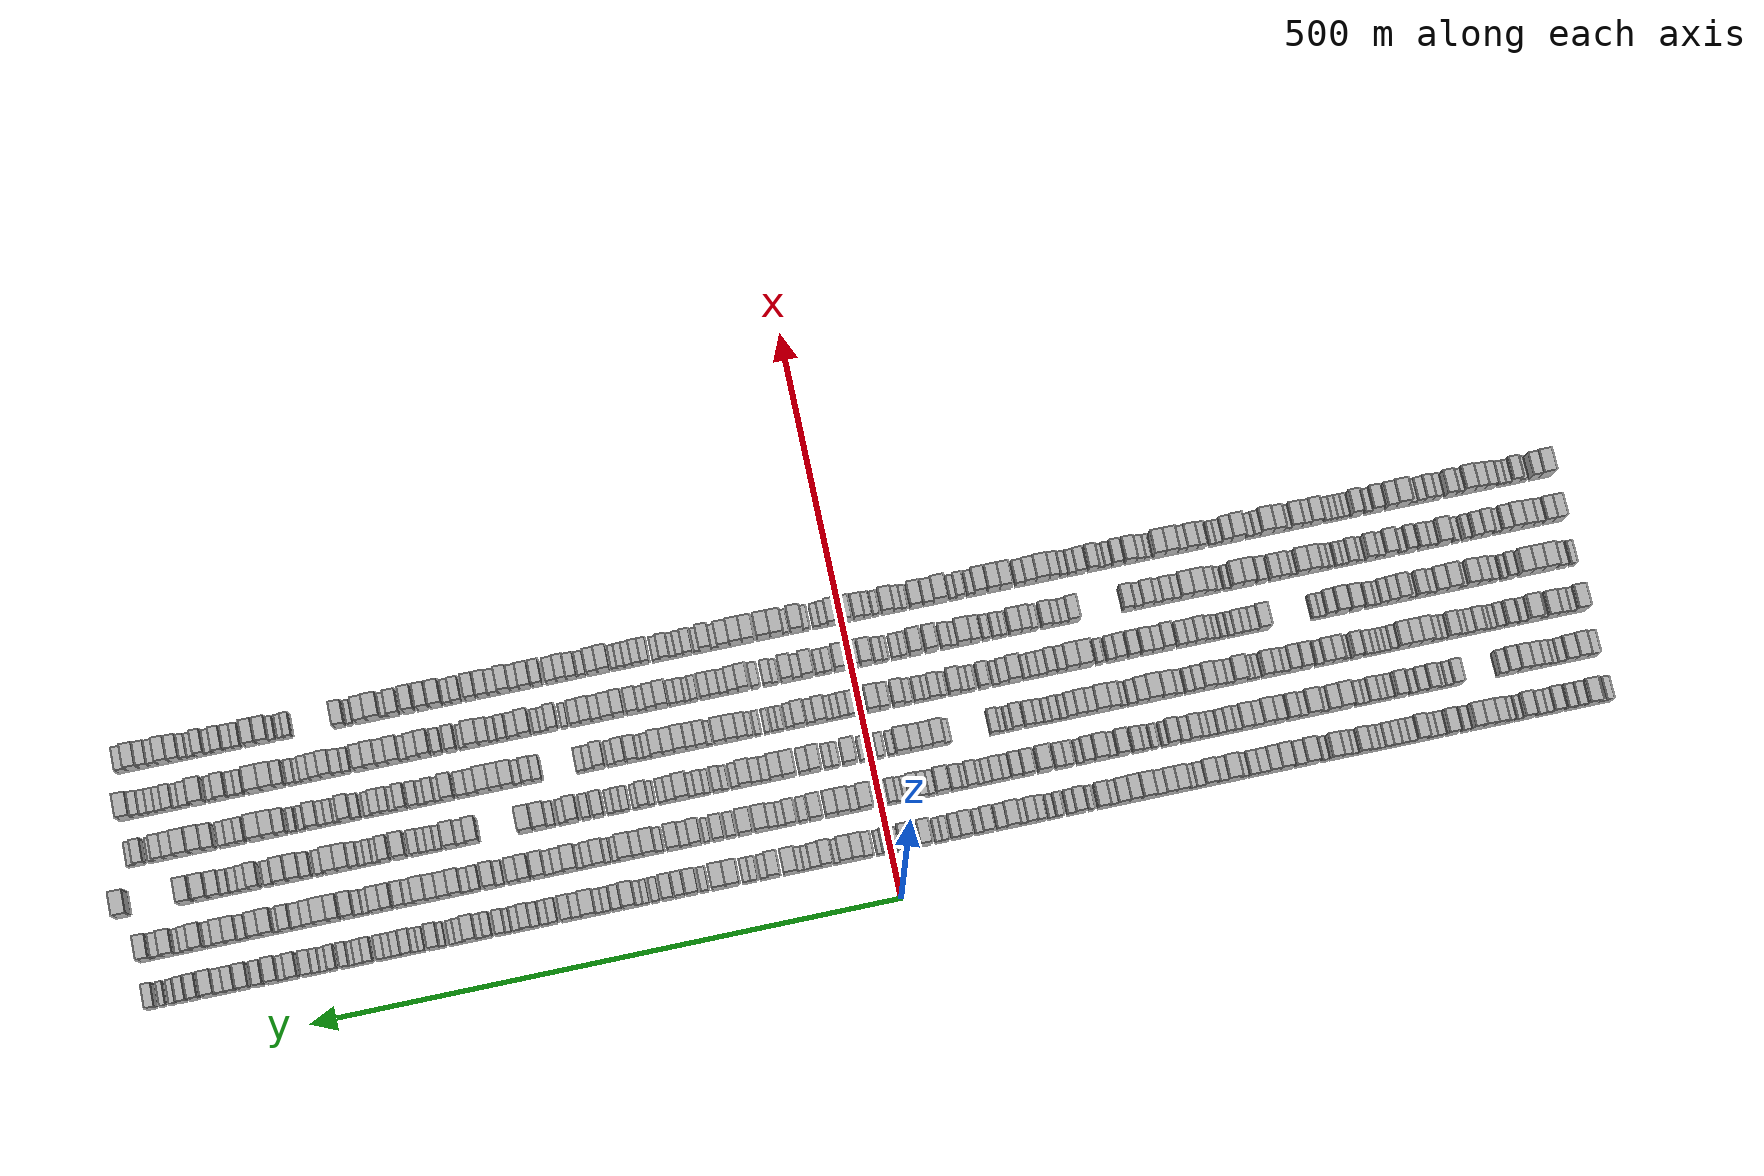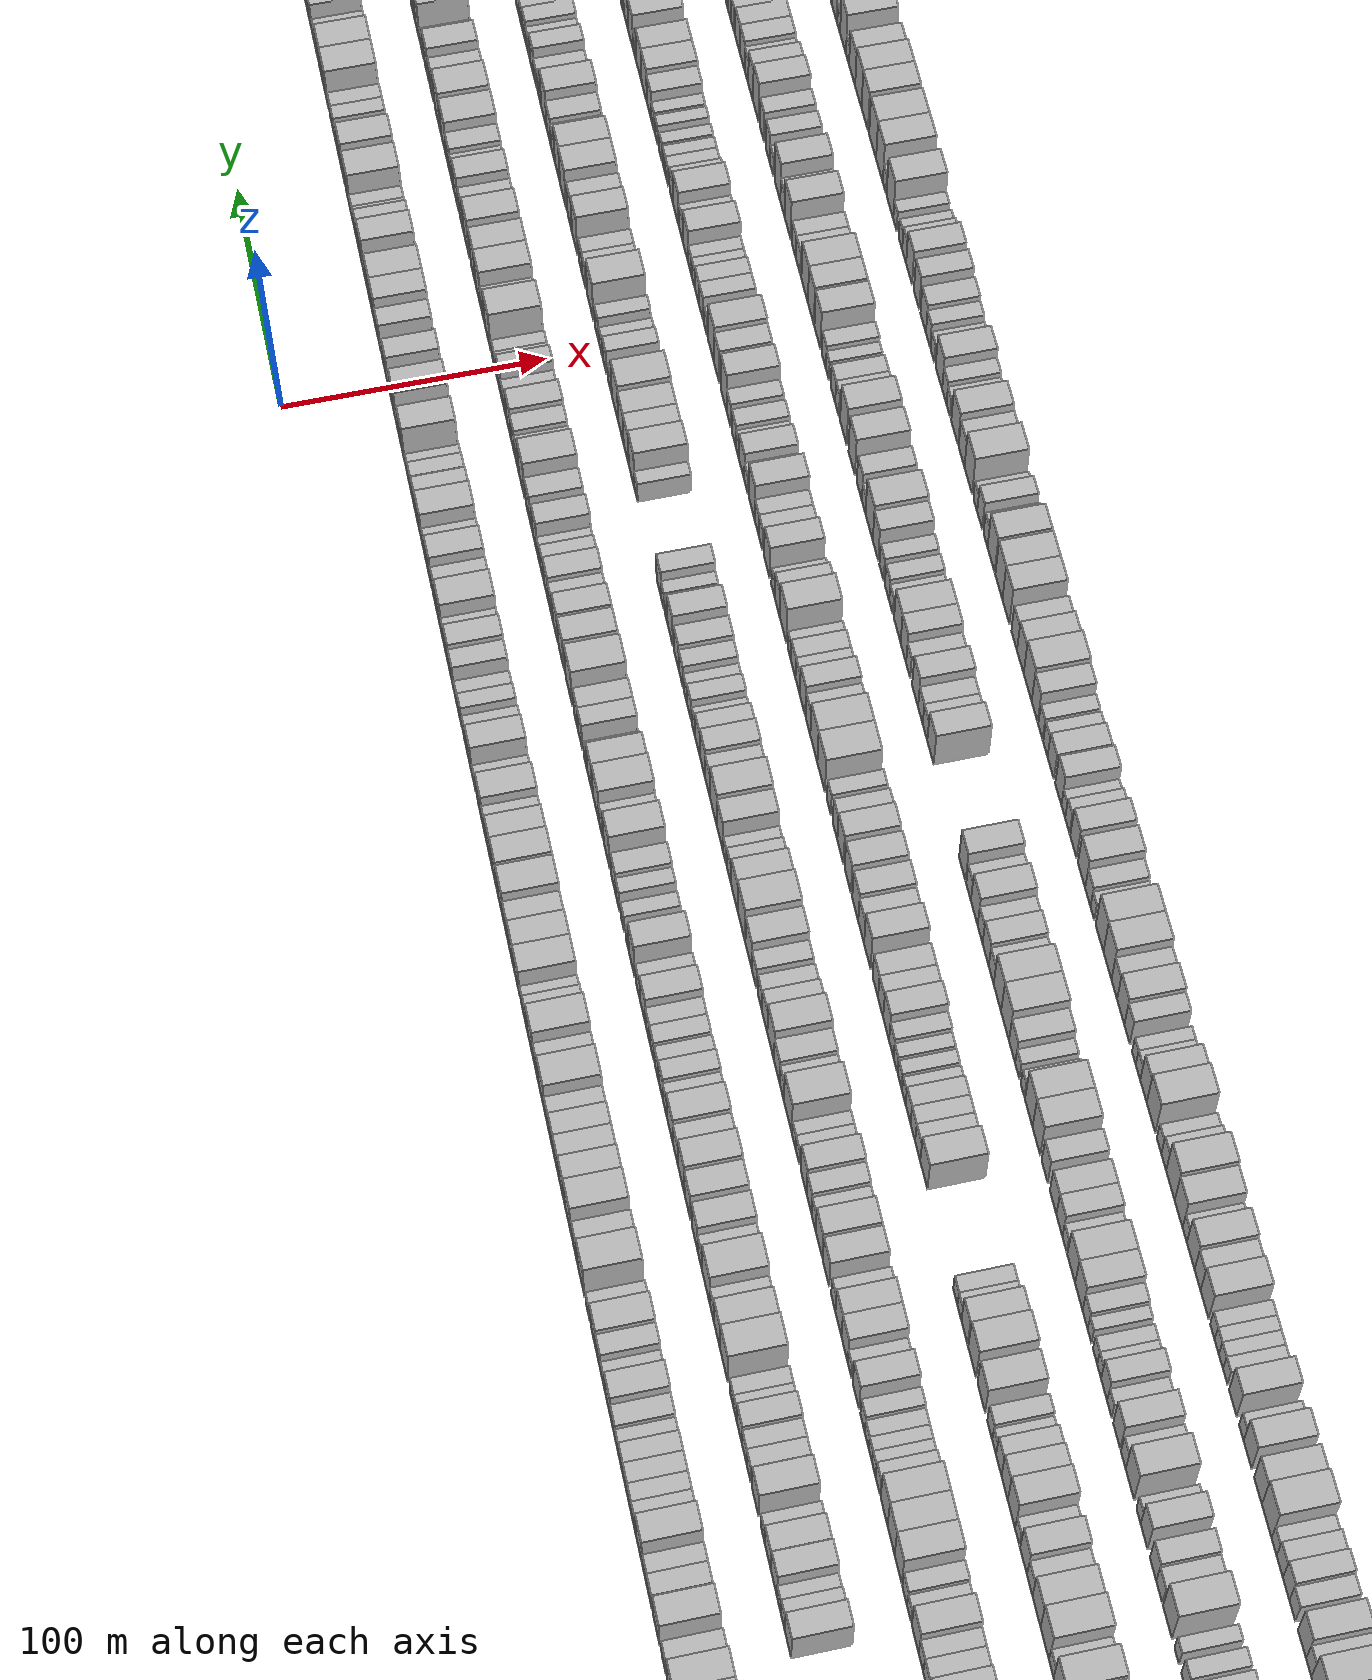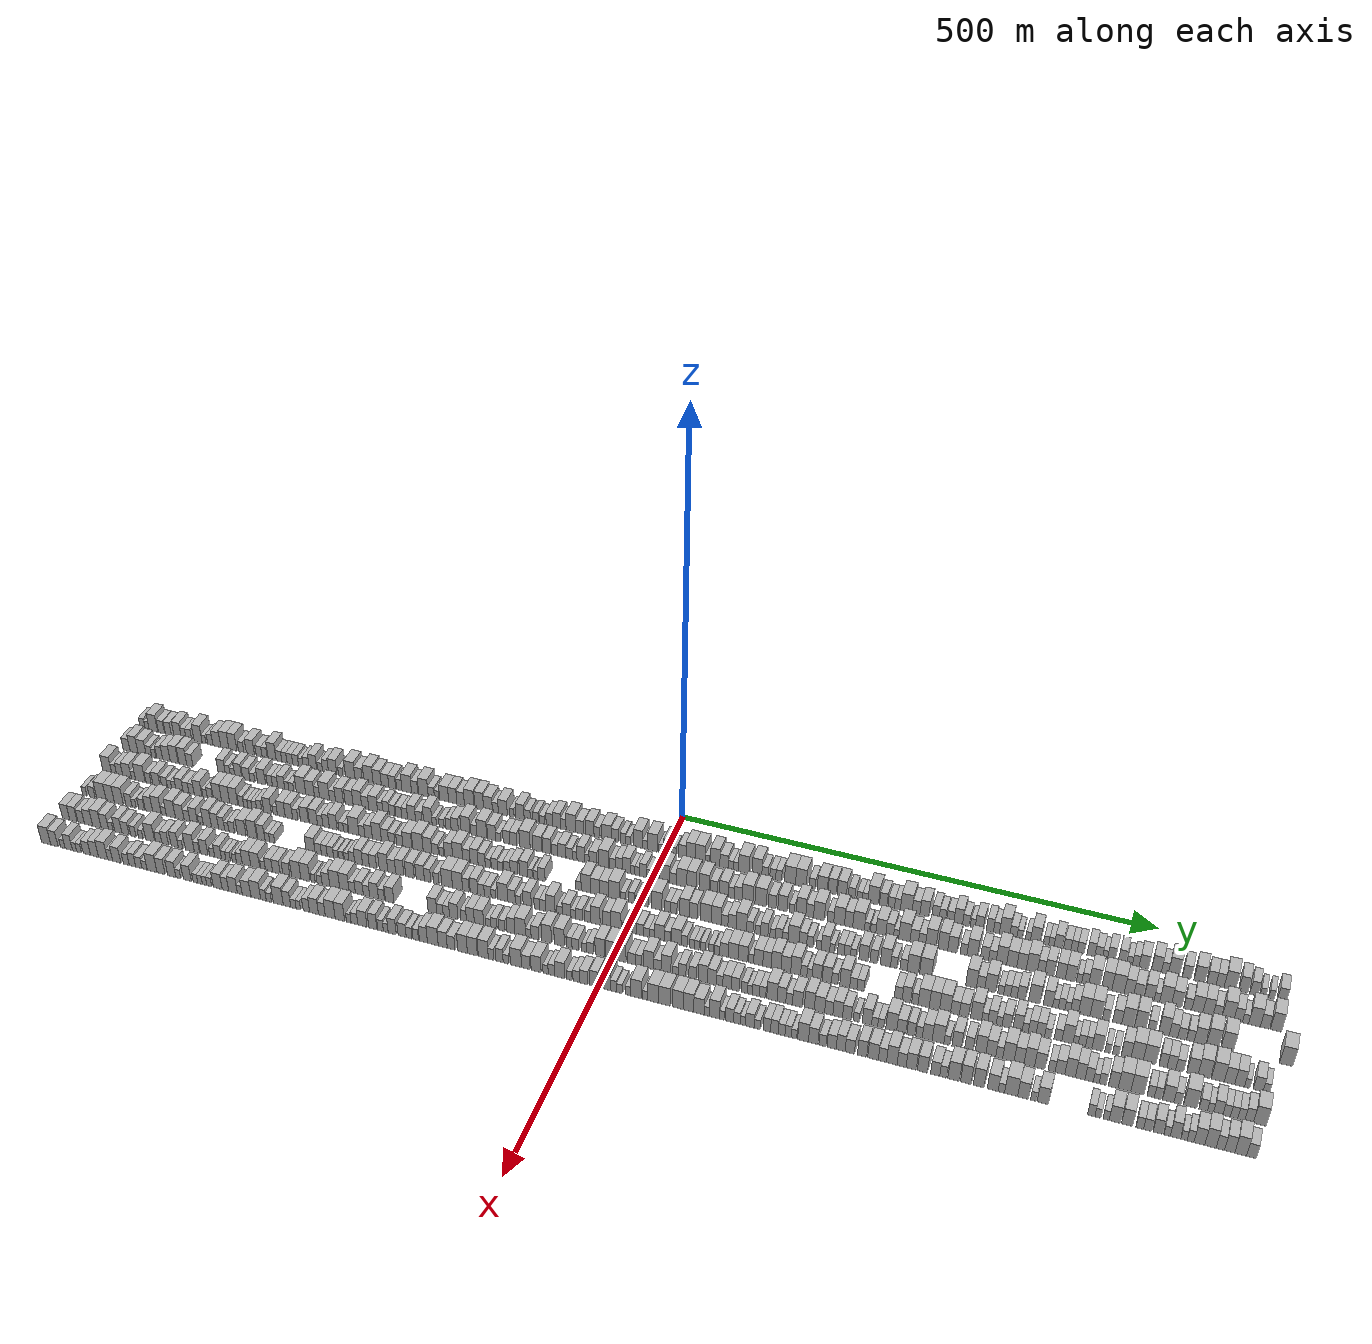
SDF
<sdf version="1.6">
 <world name="default">
  <scene>
   <sky><clouds><speed>12</speed></clouds></sky>
   <ambient>0.4 0.4 0.4 1</ambient>
   <background>0.7 0.7 0.7 1</background>
   <shadows>1</shadows>
  </scene>
  <gravity>0 0 -9.8066</gravity>
  <magnetic_field>6e-06 2.3e-05 -4.2e-05</magnetic_field>
  <physics default="0" name="default_physics" type="ode">
   <ode>
    <solver>
     <type>quick</type>
     <iters>10</iters>
     <sor>1.0</sor>
     <use_dynamic_moi_rescaling>0</use_dynamic_moi_rescaling>
    </solver>
    <constraints>
     <cfm>0</cfm>
     <erp>0.2</erp>
     <contact_max_correcting_vel>100</contact_max_correcting_vel>
     <contact_surface_layer>0.001</contact_surface_layer>
    </constraints>
   </ode>
   <max_step_size>0.004</max_step_size>
   <real_time_factor>1</real_time_factor>
   <real_time_update_rate>250</real_time_update_rate>
  </physics>
  <light name="sun" type="directional">
   <pose>0 0 10 0 0 0</pose>
   <diffuse>0.8 0.8 0.8 1</diffuse>
   <specular>0.2 0.2 0.2 1</specular>
   <attenuation>
    <range>1000</range>
    <constant>0.9</constant>
    <linear>0.01</linear>
    <quadratic>0.001</quadratic>
   </attenuation>
   <direction>-0.5 0.1 -0.9</direction>
  </light>
  <model name="building_1">
   <static>1</static>
   <pose>50.0000 -616.9183 0 0.000000 0.000000 0.000000</pose>
   <link name="link">
    <pose>0 0 7.50 0 0 0</pose>
    <collision name="collision"><geometry><box><size>20.0000 6.1633 15.0000</size></box></geometry></collision>
    <visual name="visual">
     <cast_shadows>0</cast_shadows>
     <geometry><box><size>20.0000 6.1633 15.0000</size></box></geometry>
     <material>
      <script>
       <uri>model://HANNAS_wall/materials/scripts</uri>
       <uri>model://HANNAS_wall/materials/textures</uri>
       <name>vrc/HANNAS_wall</name>
      </script>
     </material>
    </visual>
   </link>
  </model>
  <model name="building_2">
   <static>1</static>
   <pose>50.0000 -611.2370 0 0.000000 0.000000 0.000000</pose>
   <link name="link">
    <pose>0 0 6.00 0 0 0</pose>
    <collision name="collision"><geometry><box><size>20.0000 5.1993 12.0000</size></box></geometry></collision>
    <visual name="visual">
     <cast_shadows>0</cast_shadows>
     <geometry><box><size>20.0000 5.1993 12.0000</size></box></geometry>
     <material>
      <script>
       <uri>model://HANNAS_wall/materials/scripts</uri>
       <uri>model://HANNAS_wall/materials/textures</uri>
       <name>vrc/HANNAS_wall</name>
      </script>
     </material>
    </visual>
   </link>
  </model>
  <model name="building_3">
   <static>1</static>
   <pose>50.0000 -603.2668 0 0.000000 0.000000 0.000000</pose>
   <link name="link">
    <pose>0 0 12.00 0 0 0</pose>
    <collision name="collision"><geometry><box><size>20.0000 10.7413 24.0000</size></box></geometry></collision>
    <visual name="visual">
     <cast_shadows>0</cast_shadows>
     <geometry><box><size>20.0000 10.7413 24.0000</size></box></geometry>
     <material>
      <script>
       <uri>model://HANNAS_wall/materials/scripts</uri>
       <uri>model://HANNAS_wall/materials/textures</uri>
       <name>vrc/HANNAS_wall</name>
      </script>
     </material>
    </visual>
   </link>
  </model>
  <model name="building_4">
   <static>1</static>
   <pose>50.0000 -593.0272 0 0.000000 0.000000 0.000000</pose>
   <link name="link">
    <pose>0 0 9.00 0 0 0</pose>
    <collision name="collision"><geometry><box><size>20.0000 7.7378 18.0000</size></box></geometry></collision>
    <visual name="visual">
     <cast_shadows>0</cast_shadows>
     <geometry><box><size>20.0000 7.7378 18.0000</size></box></geometry>
     <material>
      <script>
       <uri>model://HANNAS_wall/materials/scripts</uri>
       <uri>model://HANNAS_wall/materials/textures</uri>
       <name>vrc/HANNAS_wall</name>
      </script>
     </material>
    </visual>
   </link>
  </model>
  <model name="building_5">
   <static>1</static>
   <pose>50.0000 -584.3045 0 0.000000 0.000000 0.000000</pose>
   <link name="link">
    <pose>0 0 9.00 0 0 0</pose>
    <collision name="collision"><geometry><box><size>20.0000 7.7077 18.0000</size></box></geometry></collision>
    <visual name="visual">
     <cast_shadows>0</cast_shadows>
     <geometry><box><size>20.0000 7.7077 18.0000</size></box></geometry>
     <material>
      <script>
       <uri>model://HANNAS_wall/materials/scripts</uri>
       <uri>model://HANNAS_wall/materials/textures</uri>
       <name>vrc/HANNAS_wall</name>
      </script>
     </material>
    </visual>
   </link>
  </model>
  <model name="building_6">
   <static>1</static>
   <pose>50.0000 -572.7570 0 0.000000 0.000000 0.000000</pose>
   <link name="link">
    <pose>0 0 10.50 0 0 0</pose>
    <collision name="collision"><geometry><box><size>20.0000 9.3873 21.0000</size></box></geometry></collision>
    <visual name="visual">
     <cast_shadows>0</cast_shadows>
     <geometry><box><size>20.0000 9.3873 21.0000</size></box></geometry>
     <material>
      <script>
       <uri>model://HANNAS_wall/materials/scripts</uri>
       <uri>model://HANNAS_wall/materials/textures</uri>
       <name>vrc/HANNAS_wall</name>
      </script>
     </material>
    </visual>
   </link>
  </model>
  <model name="building_7">
   <static>1</static>
   <pose>50.0000 -564.9902 0 0.000000 0.000000 0.000000</pose>
   <link name="link">
    <pose>0 0 7.50 0 0 0</pose>
    <collision name="collision"><geometry><box><size>20.0000 6.1462 15.0000</size></box></geometry></collision>
    <visual name="visual">
     <cast_shadows>0</cast_shadows>
     <geometry><box><size>20.0000 6.1462 15.0000</size></box></geometry>
     <material>
      <script>
       <uri>model://HANNAS_wall/materials/scripts</uri>
       <uri>model://HANNAS_wall/materials/textures</uri>
       <name>vrc/HANNAS_wall</name>
      </script>
     </material>
    </visual>
   </link>
  </model>
  <model name="building_8">
   <static>1</static>
   <pose>50.0000 -558.4783 0 0.000000 0.000000 0.000000</pose>
   <link name="link">
    <pose>0 0 7.50 0 0 0</pose>
    <collision name="collision"><geometry><box><size>20.0000 6.8775 15.0000</size></box></geometry></collision>
    <visual name="visual">
     <cast_shadows>0</cast_shadows>
     <geometry><box><size>20.0000 6.8775 15.0000</size></box></geometry>
     <material>
      <script>
       <uri>model://HANNAS_wall/materials/scripts</uri>
       <uri>model://HANNAS_wall/materials/textures</uri>
       <name>vrc/HANNAS_wall</name>
      </script>
     </material>
    </visual>
   </link>
  </model>
  <model name="building_9">
   <static>1</static>
   <pose>50.0000 -546.9646 0 0.000000 0.000000 0.000000</pose>
   <link name="link">
    <pose>0 0 12.00 0 0 0</pose>
    <collision name="collision"><geometry><box><size>20.0000 10.1499 24.0000</size></box></geometry></collision>
    <visual name="visual">
     <cast_shadows>0</cast_shadows>
     <geometry><box><size>20.0000 10.1499 24.0000</size></box></geometry>
     <material>
      <script>
       <uri>model://HANNAS_wall/materials/scripts</uri>
       <uri>model://HANNAS_wall/materials/textures</uri>
       <name>vrc/HANNAS_wall</name>
      </script>
     </material>
    </visual>
   </link>
  </model>
  <model name="building_10">
   <static>1</static>
   <pose>50.0000 -539.4749 0 0.000000 0.000000 0.000000</pose>
   <link name="link">
    <pose>0 0 6.00 0 0 0</pose>
    <collision name="collision"><geometry><box><size>20.0000 4.8296 12.0000</size></box></geometry></collision>
    <visual name="visual">
     <cast_shadows>0</cast_shadows>
     <geometry><box><size>20.0000 4.8296 12.0000</size></box></geometry>
     <material>
      <script>
       <uri>model://HANNAS_wall/materials/scripts</uri>
       <uri>model://HANNAS_wall/materials/textures</uri>
       <name>vrc/HANNAS_wall</name>
      </script>
     </material>
    </visual>
   </link>
  </model>
  <model name="building_11">
   <static>1</static>
   <pose>50.0000 -531.7551 0 0.000000 0.000000 0.000000</pose>
   <link name="link">
    <pose>0 0 7.50 0 0 0</pose>
    <collision name="collision"><geometry><box><size>20.0000 6.6100 15.0000</size></box></geometry></collision>
    <visual name="visual">
     <cast_shadows>0</cast_shadows>
     <geometry><box><size>20.0000 6.6100 15.0000</size></box></geometry>
     <material>
      <script>
       <uri>model://HANNAS_wall/materials/scripts</uri>
       <uri>model://HANNAS_wall/materials/textures</uri>
       <name>vrc/HANNAS_wall</name>
      </script>
     </material>
    </visual>
   </link>
  </model>
  <model name="building_12">
   <static>1</static>
   <pose>50.0000 -523.5142 0 0.000000 0.000000 0.000000</pose>
   <link name="link">
    <pose>0 0 10.50 0 0 0</pose>
    <collision name="collision"><geometry><box><size>20.0000 9.8717 21.0000</size></box></geometry></collision>
    <visual name="visual">
     <cast_shadows>0</cast_shadows>
     <geometry><box><size>20.0000 9.8717 21.0000</size></box></geometry>
     <material>
      <script>
       <uri>model://HANNAS_wall/materials/scripts</uri>
       <uri>model://HANNAS_wall/materials/textures</uri>
       <name>vrc/HANNAS_wall</name>
      </script>
     </material>
    </visual>
   </link>
  </model>
  <model name="building_13">
   <static>1</static>
   <pose>50.0000 -513.5343 0 0.000000 0.000000 0.000000</pose>
   <link name="link">
    <pose>0 0 12.00 0 0 0</pose>
    <collision name="collision"><geometry><box><size>20.0000 10.0883 24.0000</size></box></geometry></collision>
    <visual name="visual">
     <cast_shadows>0</cast_shadows>
     <geometry><box><size>20.0000 10.0883 24.0000</size></box></geometry>
     <material>
      <script>
       <uri>model://HANNAS_wall/materials/scripts</uri>
       <uri>model://HANNAS_wall/materials/textures</uri>
       <name>vrc/HANNAS_wall</name>
      </script>
     </material>
    </visual>
   </link>
  </model>
  <model name="building_14">
   <static>1</static>
   <pose>50.0000 -503.5252 0 0.000000 0.000000 0.000000</pose>
   <link name="link">
    <pose>0 0 12.00 0 0 0</pose>
    <collision name="collision"><geometry><box><size>20.0000 9.9298 24.0000</size></box></geometry></collision>
    <visual name="visual">
     <cast_shadows>0</cast_shadows>
     <geometry><box><size>20.0000 9.9298 24.0000</size></box></geometry>
     <material>
      <script>
       <uri>model://HANNAS_wall/materials/scripts</uri>
       <uri>model://HANNAS_wall/materials/textures</uri>
       <name>vrc/HANNAS_wall</name>
      </script>
     </material>
    </visual>
   </link>
  </model>
  <model name="building_15">
   <static>1</static>
   <pose>50.0000 -493.2294 0 0.000000 0.000000 0.000000</pose>
   <link name="link">
    <pose>0 0 7.50 0 0 0</pose>
    <collision name="collision"><geometry><box><size>20.0000 6.6619 15.0000</size></box></geometry></collision>
    <visual name="visual">
     <cast_shadows>0</cast_shadows>
     <geometry><box><size>20.0000 6.6619 15.0000</size></box></geometry>
     <material>
      <script>
       <uri>model://HANNAS_wall/materials/scripts</uri>
       <uri>model://HANNAS_wall/materials/textures</uri>
       <name>vrc/HANNAS_wall</name>
      </script>
     </material>
    </visual>
   </link>
  </model>
  <model name="building_16">
   <static>1</static>
   <pose>50.0000 -481.8707 0 0.000000 0.000000 0.000000</pose>
   <link name="link">
    <pose>0 0 10.50 0 0 0</pose>
    <collision name="collision"><geometry><box><size>20.0000 10.0555 21.0000</size></box></geometry></collision>
    <visual name="visual">
     <cast_shadows>0</cast_shadows>
     <geometry><box><size>20.0000 10.0555 21.0000</size></box></geometry>
     <material>
      <script>
       <uri>model://HANNAS_wall/materials/scripts</uri>
       <uri>model://HANNAS_wall/materials/textures</uri>
       <name>vrc/HANNAS_wall</name>
      </script>
     </material>
    </visual>
   </link>
  </model>
  <model name="building_17">
   <static>1</static>
   <pose>50.0000 -471.1658 0 0.000000 0.000000 0.000000</pose>
   <link name="link">
    <pose>0 0 7.50 0 0 0</pose>
    <collision name="collision"><geometry><box><size>20.0000 7.3543 15.0000</size></box></geometry></collision>
    <visual name="visual">
     <cast_shadows>0</cast_shadows>
     <geometry><box><size>20.0000 7.3543 15.0000</size></box></geometry>
     <material>
      <script>
       <uri>model://HANNAS_wall/materials/scripts</uri>
       <uri>model://HANNAS_wall/materials/textures</uri>
       <name>vrc/HANNAS_wall</name>
      </script>
     </material>
    </visual>
   </link>
  </model>
  <model name="building_18">
   <static>1</static>
   <pose>50.0000 -464.2979 0 0.000000 0.000000 0.000000</pose>
   <link name="link">
    <pose>0 0 7.50 0 0 0</pose>
    <collision name="collision"><geometry><box><size>20.0000 6.3814 15.0000</size></box></geometry></collision>
    <visual name="visual">
     <cast_shadows>0</cast_shadows>
     <geometry><box><size>20.0000 6.3814 15.0000</size></box></geometry>
     <material>
      <script>
       <uri>model://HANNAS_wall/materials/scripts</uri>
       <uri>model://HANNAS_wall/materials/textures</uri>
       <name>vrc/HANNAS_wall</name>
      </script>
     </material>
    </visual>
   </link>
  </model>
  <model name="building_19">
   <static>1</static>
   <pose>50.0000 -455.1495 0 0.000000 0.000000 0.000000</pose>
   <link name="link">
    <pose>0 0 12.00 0 0 0</pose>
    <collision name="collision"><geometry><box><size>20.0000 9.9155 24.0000</size></box></geometry></collision>
    <visual name="visual">
     <cast_shadows>0</cast_shadows>
     <geometry><box><size>20.0000 9.9155 24.0000</size></box></geometry>
     <material>
      <script>
       <uri>model://HANNAS_wall/materials/scripts</uri>
       <uri>model://HANNAS_wall/materials/textures</uri>
       <name>vrc/HANNAS_wall</name>
      </script>
     </material>
    </visual>
   </link>
  </model>
  <model name="building_20">
   <static>1</static>
   <pose>50.0000 -446.6802 0 0.000000 0.000000 0.000000</pose>
   <link name="link">
    <pose>0 0 7.50 0 0 0</pose>
    <collision name="collision"><geometry><box><size>20.0000 7.0231 15.0000</size></box></geometry></collision>
    <visual name="visual">
     <cast_shadows>0</cast_shadows>
     <geometry><box><size>20.0000 7.0231 15.0000</size></box></geometry>
     <material>
      <script>
       <uri>model://HANNAS_wall/materials/scripts</uri>
       <uri>model://HANNAS_wall/materials/textures</uri>
       <name>vrc/HANNAS_wall</name>
      </script>
     </material>
    </visual>
   </link>
  </model>
  <model name="building_21">
   <static>1</static>
   <pose>50.0000 -440.0367 0 0.000000 0.000000 0.000000</pose>
   <link name="link">
    <pose>0 0 7.50 0 0 0</pose>
    <collision name="collision"><geometry><box><size>20.0000 6.2639 15.0000</size></box></geometry></collision>
    <visual name="visual">
     <cast_shadows>0</cast_shadows>
     <geometry><box><size>20.0000 6.2639 15.0000</size></box></geometry>
     <material>
      <script>
       <uri>model://HANNAS_wall/materials/scripts</uri>
       <uri>model://HANNAS_wall/materials/textures</uri>
       <name>vrc/HANNAS_wall</name>
      </script>
     </material>
    </visual>
   </link>
  </model>
  <model name="building_22">
   <static>1</static>
   <pose>50.0000 -433.4118 0 0.000000 0.000000 0.000000</pose>
   <link name="link">
    <pose>0 0 7.50 0 0 0</pose>
    <collision name="collision"><geometry><box><size>20.0000 6.9858 15.0000</size></box></geometry></collision>
    <visual name="visual">
     <cast_shadows>0</cast_shadows>
     <geometry><box><size>20.0000 6.9858 15.0000</size></box></geometry>
     <material>
      <script>
       <uri>model://HANNAS_wall/materials/scripts</uri>
       <uri>model://HANNAS_wall/materials/textures</uri>
       <name>vrc/HANNAS_wall</name>
      </script>
     </material>
    </visual>
   </link>
  </model>
  <model name="building_23">
   <static>1</static>
   <pose>50.0000 -426.4306 0 0.000000 0.000000 0.000000</pose>
   <link name="link">
    <pose>0 0 7.50 0 0 0</pose>
    <collision name="collision"><geometry><box><size>20.0000 6.9766 15.0000</size></box></geometry></collision>
    <visual name="visual">
     <cast_shadows>0</cast_shadows>
     <geometry><box><size>20.0000 6.9766 15.0000</size></box></geometry>
     <material>
      <script>
       <uri>model://HANNAS_wall/materials/scripts</uri>
       <uri>model://HANNAS_wall/materials/textures</uri>
       <name>vrc/HANNAS_wall</name>
      </script>
     </material>
    </visual>
   </link>
  </model>
  <model name="building_24">
   <static>1</static>
   <pose>50.0000 -420.1451 0 0.000000 0.000000 0.000000</pose>
   <link name="link">
    <pose>0 0 6.00 0 0 0</pose>
    <collision name="collision"><geometry><box><size>20.0000 5.5945 12.0000</size></box></geometry></collision>
    <visual name="visual">
     <cast_shadows>0</cast_shadows>
     <geometry><box><size>20.0000 5.5945 12.0000</size></box></geometry>
     <material>
      <script>
       <uri>model://HANNAS_wall/materials/scripts</uri>
       <uri>model://HANNAS_wall/materials/textures</uri>
       <name>vrc/HANNAS_wall</name>
      </script>
     </material>
    </visual>
   </link>
  </model>
  <model name="building_25">
   <static>1</static>
   <pose>50.0000 -413.6183 0 0.000000 0.000000 0.000000</pose>
   <link name="link">
    <pose>0 0 7.50 0 0 0</pose>
    <collision name="collision"><geometry><box><size>20.0000 7.4590 15.0000</size></box></geometry></collision>
    <visual name="visual">
     <cast_shadows>0</cast_shadows>
     <geometry><box><size>20.0000 7.4590 15.0000</size></box></geometry>
     <material>
      <script>
       <uri>model://HANNAS_wall/materials/scripts</uri>
       <uri>model://HANNAS_wall/materials/textures</uri>
       <name>vrc/HANNAS_wall</name>
      </script>
     </material>
    </visual>
   </link>
  </model>
  <model name="building_26">
   <static>1</static>
   <pose>50.0000 -405.2751 0 0.000000 0.000000 0.000000</pose>
   <link name="link">
    <pose>0 0 10.50 0 0 0</pose>
    <collision name="collision"><geometry><box><size>20.0000 9.2276 21.0000</size></box></geometry></collision>
    <visual name="visual">
     <cast_shadows>0</cast_shadows>
     <geometry><box><size>20.0000 9.2276 21.0000</size></box></geometry>
     <material>
      <script>
       <uri>model://HANNAS_wall/materials/scripts</uri>
       <uri>model://HANNAS_wall/materials/textures</uri>
       <name>vrc/HANNAS_wall</name>
      </script>
     </material>
    </visual>
   </link>
  </model>
  <model name="building_27">
   <static>1</static>
   <pose>50.0000 -396.7223 0 0.000000 0.000000 0.000000</pose>
   <link name="link">
    <pose>0 0 6.00 0 0 0</pose>
    <collision name="collision"><geometry><box><size>20.0000 5.8781 12.0000</size></box></geometry></collision>
    <visual name="visual">
     <cast_shadows>0</cast_shadows>
     <geometry><box><size>20.0000 5.8781 12.0000</size></box></geometry>
     <material>
      <script>
       <uri>model://HANNAS_wall/materials/scripts</uri>
       <uri>model://HANNAS_wall/materials/textures</uri>
       <name>vrc/HANNAS_wall</name>
      </script>
     </material>
    </visual>
   </link>
  </model>
  <model name="building_28">
   <static>1</static>
   <pose>50.0000 -390.0835 0 0.000000 0.000000 0.000000</pose>
   <link name="link">
    <pose>0 0 9.00 0 0 0</pose>
    <collision name="collision"><geometry><box><size>20.0000 7.3994 18.0000</size></box></geometry></collision>
    <visual name="visual">
     <cast_shadows>0</cast_shadows>
     <geometry><box><size>20.0000 7.3994 18.0000</size></box></geometry>
     <material>
      <script>
       <uri>model://HANNAS_wall/materials/scripts</uri>
       <uri>model://HANNAS_wall/materials/textures</uri>
       <name>vrc/HANNAS_wall</name>
      </script>
     </material>
    </visual>
   </link>
  </model>
  <model name="building_29">
   <static>1</static>
   <pose>50.0000 -381.4417 0 0.000000 0.000000 0.000000</pose>
   <link name="link">
    <pose>0 0 10.50 0 0 0</pose>
    <collision name="collision"><geometry><box><size>20.0000 9.8843 21.0000</size></box></geometry></collision>
    <visual name="visual">
     <cast_shadows>0</cast_shadows>
     <geometry><box><size>20.0000 9.8843 21.0000</size></box></geometry>
     <material>
      <script>
       <uri>model://HANNAS_wall/materials/scripts</uri>
       <uri>model://HANNAS_wall/materials/textures</uri>
       <name>vrc/HANNAS_wall</name>
      </script>
     </material>
    </visual>
   </link>
  </model>
  <model name="building_30">
   <static>1</static>
   <pose>50.0000 -371.7914 0 0.000000 0.000000 0.000000</pose>
   <link name="link">
    <pose>0 0 6.00 0 0 0</pose>
    <collision name="collision"><geometry><box><size>20.0000 5.4162 12.0000</size></box></geometry></collision>
    <visual name="visual">
     <cast_shadows>0</cast_shadows>
     <geometry><box><size>20.0000 5.4162 12.0000</size></box></geometry>
     <material>
      <script>
       <uri>model://HANNAS_wall/materials/scripts</uri>
       <uri>model://HANNAS_wall/materials/textures</uri>
       <name>vrc/HANNAS_wall</name>
      </script>
     </material>
    </visual>
   </link>
  </model>
  <model name="building_31">
   <static>1</static>
   <pose>50.0000 -360.3759 0 0.000000 0.000000 0.000000</pose>
   <link name="link">
    <pose>0 0 12.00 0 0 0</pose>
    <collision name="collision"><geometry><box><size>20.0000 11.4149 24.0000</size></box></geometry></collision>
    <visual name="visual">
     <cast_shadows>0</cast_shadows>
     <geometry><box><size>20.0000 11.4149 24.0000</size></box></geometry>
     <material>
      <script>
       <uri>model://HANNAS_wall/materials/scripts</uri>
       <uri>model://HANNAS_wall/materials/textures</uri>
       <name>vrc/HANNAS_wall</name>
      </script>
     </material>
    </visual>
   </link>
  </model>
  <model name="building_32">
   <static>1</static>
   <pose>50.0000 -350.3277 0 0.000000 0.000000 0.000000</pose>
   <link name="link">
    <pose>0 0 9.00 0 0 0</pose>
    <collision name="collision"><geometry><box><size>20.0000 8.6814 18.0000</size></box></geometry></collision>
    <visual name="visual">
     <cast_shadows>0</cast_shadows>
     <geometry><box><size>20.0000 8.6814 18.0000</size></box></geometry>
     <material>
      <script>
       <uri>model://HANNAS_wall/materials/scripts</uri>
       <uri>model://HANNAS_wall/materials/textures</uri>
       <name>vrc/HANNAS_wall</name>
      </script>
     </material>
    </visual>
   </link>
  </model>
  <model name="building_33">
   <static>1</static>
   <pose>50.0000 -338.4936 0 0.000000 0.000000 0.000000</pose>
   <link name="link">
    <pose>0 0 12.00 0 0 0</pose>
    <collision name="collision"><geometry><box><size>20.0000 10.9869 24.0000</size></box></geometry></collision>
    <visual name="visual">
     <cast_shadows>0</cast_shadows>
     <geometry><box><size>20.0000 10.9869 24.0000</size></box></geometry>
     <material>
      <script>
       <uri>model://HANNAS_wall/materials/scripts</uri>
       <uri>model://HANNAS_wall/materials/textures</uri>
       <name>vrc/HANNAS_wall</name>
      </script>
     </material>
    </visual>
   </link>
  </model>
  <model name="building_34">
   <static>1</static>
   <pose>50.0000 -328.1596 0 0.000000 0.000000 0.000000</pose>
   <link name="link">
    <pose>0 0 10.50 0 0 0</pose>
    <collision name="collision"><geometry><box><size>20.0000 9.6810 21.0000</size></box></geometry></collision>
    <visual name="visual">
     <cast_shadows>0</cast_shadows>
     <geometry><box><size>20.0000 9.6810 21.0000</size></box></geometry>
     <material>
      <script>
       <uri>model://HANNAS_wall/materials/scripts</uri>
       <uri>model://HANNAS_wall/materials/textures</uri>
       <name>vrc/HANNAS_wall</name>
      </script>
     </material>
    </visual>
   </link>
  </model>
  <model name="building_35">
   <static>1</static>
   <pose>50.0000 -318.8257 0 0.000000 0.000000 0.000000</pose>
   <link name="link">
    <pose>0 0 9.00 0 0 0</pose>
    <collision name="collision"><geometry><box><size>20.0000 8.9869 18.0000</size></box></geometry></collision>
    <visual name="visual">
     <cast_shadows>0</cast_shadows>
     <geometry><box><size>20.0000 8.9869 18.0000</size></box></geometry>
     <material>
      <script>
       <uri>model://HANNAS_wall/materials/scripts</uri>
       <uri>model://HANNAS_wall/materials/textures</uri>
       <name>vrc/HANNAS_wall</name>
      </script>
     </material>
    </visual>
   </link>
  </model>
  <model name="building_36">
   <static>1</static>
   <pose>50.0000 -310.2682 0 0.000000 0.000000 0.000000</pose>
   <link name="link">
    <pose>0 0 9.00 0 0 0</pose>
    <collision name="collision"><geometry><box><size>20.0000 8.1281 18.0000</size></box></geometry></collision>
    <visual name="visual">
     <cast_shadows>0</cast_shadows>
     <geometry><box><size>20.0000 8.1281 18.0000</size></box></geometry>
     <material>
      <script>
       <uri>model://HANNAS_wall/materials/scripts</uri>
       <uri>model://HANNAS_wall/materials/textures</uri>
       <name>vrc/HANNAS_wall</name>
      </script>
     </material>
    </visual>
   </link>
  </model>
  <model name="building_37">
   <static>1</static>
   <pose>50.0000 -302.0606 0 0.000000 0.000000 0.000000</pose>
   <link name="link">
    <pose>0 0 7.50 0 0 0</pose>
    <collision name="collision"><geometry><box><size>20.0000 6.2870 15.0000</size></box></geometry></collision>
    <visual name="visual">
     <cast_shadows>0</cast_shadows>
     <geometry><box><size>20.0000 6.2870 15.0000</size></box></geometry>
     <material>
      <script>
       <uri>model://HANNAS_wall/materials/scripts</uri>
       <uri>model://HANNAS_wall/materials/textures</uri>
       <name>vrc/HANNAS_wall</name>
      </script>
     </material>
    </visual>
   </link>
  </model>
  <model name="building_38">
   <static>1</static>
   <pose>50.0000 -293.2327 0 0.000000 0.000000 0.000000</pose>
   <link name="link">
    <pose>0 0 12.00 0 0 0</pose>
    <collision name="collision"><geometry><box><size>20.0000 11.3690 24.0000</size></box></geometry></collision>
    <visual name="visual">
     <cast_shadows>0</cast_shadows>
     <geometry><box><size>20.0000 11.3690 24.0000</size></box></geometry>
     <material>
      <script>
       <uri>model://HANNAS_wall/materials/scripts</uri>
       <uri>model://HANNAS_wall/materials/textures</uri>
       <name>vrc/HANNAS_wall</name>
      </script>
     </material>
    </visual>
   </link>
  </model>
  <model name="building_39">
   <static>1</static>
   <pose>50.0000 -283.8331 0 0.000000 0.000000 0.000000</pose>
   <link name="link">
    <pose>0 0 9.00 0 0 0</pose>
    <collision name="collision"><geometry><box><size>20.0000 7.4301 18.0000</size></box></geometry></collision>
    <visual name="visual">
     <cast_shadows>0</cast_shadows>
     <geometry><box><size>20.0000 7.4301 18.0000</size></box></geometry>
     <material>
      <script>
       <uri>model://HANNAS_wall/materials/scripts</uri>
       <uri>model://HANNAS_wall/materials/textures</uri>
       <name>vrc/HANNAS_wall</name>
      </script>
     </material>
    </visual>
   </link>
  </model>
  <model name="building_40">
   <static>1</static>
   <pose>50.0000 -273.5586 0 0.000000 0.000000 0.000000</pose>
   <link name="link">
    <pose>0 0 12.00 0 0 0</pose>
    <collision name="collision"><geometry><box><size>20.0000 11.1189 24.0000</size></box></geometry></collision>
    <visual name="visual">
     <cast_shadows>0</cast_shadows>
     <geometry><box><size>20.0000 11.1189 24.0000</size></box></geometry>
     <material>
      <script>
       <uri>model://HANNAS_wall/materials/scripts</uri>
       <uri>model://HANNAS_wall/materials/textures</uri>
       <name>vrc/HANNAS_wall</name>
      </script>
     </material>
    </visual>
   </link>
  </model>
  <model name="building_41">
   <static>1</static>
   <pose>50.0000 -264.3199 0 0.000000 0.000000 0.000000</pose>
   <link name="link">
    <pose>0 0 7.50 0 0 0</pose>
    <collision name="collision"><geometry><box><size>20.0000 7.3586 15.0000</size></box></geometry></collision>
    <visual name="visual">
     <cast_shadows>0</cast_shadows>
     <geometry><box><size>20.0000 7.3586 15.0000</size></box></geometry>
     <material>
      <script>
       <uri>model://HANNAS_wall/materials/scripts</uri>
       <uri>model://HANNAS_wall/materials/textures</uri>
       <name>vrc/HANNAS_wall</name>
      </script>
     </material>
    </visual>
   </link>
  </model>
  <model name="building_42">
   <static>1</static>
   <pose>50.0000 -258.1257 0 0.000000 0.000000 0.000000</pose>
   <link name="link">
    <pose>0 0 6.00 0 0 0</pose>
    <collision name="collision"><geometry><box><size>20.0000 5.0299 12.0000</size></box></geometry></collision>
    <visual name="visual">
     <cast_shadows>0</cast_shadows>
     <geometry><box><size>20.0000 5.0299 12.0000</size></box></geometry>
     <material>
      <script>
       <uri>model://HANNAS_wall/materials/scripts</uri>
       <uri>model://HANNAS_wall/materials/textures</uri>
       <name>vrc/HANNAS_wall</name>
      </script>
     </material>
    </visual>
   </link>
  </model>
  <model name="building_43">
   <static>1</static>
   <pose>50.0000 -249.3676 0 0.000000 0.000000 0.000000</pose>
   <link name="link">
    <pose>0 0 10.50 0 0 0</pose>
    <collision name="collision"><geometry><box><size>20.0000 10.4863 21.0000</size></box></geometry></collision>
    <visual name="visual">
     <cast_shadows>0</cast_shadows>
     <geometry><box><size>20.0000 10.4863 21.0000</size></box></geometry>
     <material>
      <script>
       <uri>model://HANNAS_wall/materials/scripts</uri>
       <uri>model://HANNAS_wall/materials/textures</uri>
       <name>vrc/HANNAS_wall</name>
      </script>
     </material>
    </visual>
   </link>
  </model>
  <model name="building_44">
   <static>1</static>
   <pose>50.0000 -239.3578 0 0.000000 0.000000 0.000000</pose>
   <link name="link">
    <pose>0 0 10.50 0 0 0</pose>
    <collision name="collision"><geometry><box><size>20.0000 9.5332 21.0000</size></box></geometry></collision>
    <visual name="visual">
     <cast_shadows>0</cast_shadows>
     <geometry><box><size>20.0000 9.5332 21.0000</size></box></geometry>
     <material>
      <script>
       <uri>model://HANNAS_wall/materials/scripts</uri>
       <uri>model://HANNAS_wall/materials/textures</uri>
       <name>vrc/HANNAS_wall</name>
      </script>
     </material>
    </visual>
   </link>
  </model>
  <model name="building_45">
   <static>1</static>
   <pose>50.0000 -230.1755 0 0.000000 0.000000 0.000000</pose>
   <link name="link">
    <pose>0 0 9.00 0 0 0</pose>
    <collision name="collision"><geometry><box><size>20.0000 8.8316 18.0000</size></box></geometry></collision>
    <visual name="visual">
     <cast_shadows>0</cast_shadows>
     <geometry><box><size>20.0000 8.8316 18.0000</size></box></geometry>
     <material>
      <script>
       <uri>model://HANNAS_wall/materials/scripts</uri>
       <uri>model://HANNAS_wall/materials/textures</uri>
       <name>vrc/HANNAS_wall</name>
      </script>
     </material>
    </visual>
   </link>
  </model>
  <model name="building_46">
   <static>1</static>
   <pose>50.0000 -220.2064 0 0.000000 0.000000 0.000000</pose>
   <link name="link">
    <pose>0 0 12.00 0 0 0</pose>
    <collision name="collision"><geometry><box><size>20.0000 11.1066 24.0000</size></box></geometry></collision>
    <visual name="visual">
     <cast_shadows>0</cast_shadows>
     <geometry><box><size>20.0000 11.1066 24.0000</size></box></geometry>
     <material>
      <script>
       <uri>model://HANNAS_wall/materials/scripts</uri>
       <uri>model://HANNAS_wall/materials/textures</uri>
       <name>vrc/HANNAS_wall</name>
      </script>
     </material>
    </visual>
   </link>
  </model>
  <model name="building_47">
   <static>1</static>
   <pose>50.0000 -208.5934 0 0.000000 0.000000 0.000000</pose>
   <link name="link">
    <pose>0 0 12.00 0 0 0</pose>
    <collision name="collision"><geometry><box><size>20.0000 10.1195 24.0000</size></box></geometry></collision>
    <visual name="visual">
     <cast_shadows>0</cast_shadows>
     <geometry><box><size>20.0000 10.1195 24.0000</size></box></geometry>
     <material>
      <script>
       <uri>model://HANNAS_wall/materials/scripts</uri>
       <uri>model://HANNAS_wall/materials/textures</uri>
       <name>vrc/HANNAS_wall</name>
      </script>
     </material>
    </visual>
   </link>
  </model>
  <model name="building_48">
   <static>1</static>
   <pose>50.0000 -198.4298 0 0.000000 0.000000 0.000000</pose>
   <link name="link">
    <pose>0 0 10.50 0 0 0</pose>
    <collision name="collision"><geometry><box><size>20.0000 10.2078 21.0000</size></box></geometry></collision>
    <visual name="visual">
     <cast_shadows>0</cast_shadows>
     <geometry><box><size>20.0000 10.2078 21.0000</size></box></geometry>
     <material>
      <script>
       <uri>model://HANNAS_wall/materials/scripts</uri>
       <uri>model://HANNAS_wall/materials/textures</uri>
       <name>vrc/HANNAS_wall</name>
      </script>
     </material>
    </visual>
   </link>
  </model>
  <model name="building_49">
   <static>1</static>
   <pose>50.0000 -189.9141 0 0.000000 0.000000 0.000000</pose>
   <link name="link">
    <pose>0 0 7.50 0 0 0</pose>
    <collision name="collision"><geometry><box><size>20.0000 6.8235 15.0000</size></box></geometry></collision>
    <visual name="visual">
     <cast_shadows>0</cast_shadows>
     <geometry><box><size>20.0000 6.8235 15.0000</size></box></geometry>
     <material>
      <script>
       <uri>model://HANNAS_wall/materials/scripts</uri>
       <uri>model://HANNAS_wall/materials/textures</uri>
       <name>vrc/HANNAS_wall</name>
      </script>
     </material>
    </visual>
   </link>
  </model>
  <model name="building_50">
   <static>1</static>
   <pose>50.0000 -181.3824 0 0.000000 0.000000 0.000000</pose>
   <link name="link">
    <pose>0 0 10.50 0 0 0</pose>
    <collision name="collision"><geometry><box><size>20.0000 10.2401 21.0000</size></box></geometry></collision>
    <visual name="visual">
     <cast_shadows>0</cast_shadows>
     <geometry><box><size>20.0000 10.2401 21.0000</size></box></geometry>
     <material>
      <script>
       <uri>model://HANNAS_wall/materials/scripts</uri>
       <uri>model://HANNAS_wall/materials/textures</uri>
       <name>vrc/HANNAS_wall</name>
      </script>
     </material>
    </visual>
   </link>
  </model>
  <model name="building_51">
   <static>1</static>
   <pose>50.0000 -170.8531 0 0.000000 0.000000 0.000000</pose>
   <link name="link">
    <pose>0 0 6.00 0 0 0</pose>
    <collision name="collision"><geometry><box><size>20.0000 4.8184 12.0000</size></box></geometry></collision>
    <visual name="visual">
     <cast_shadows>0</cast_shadows>
     <geometry><box><size>20.0000 4.8184 12.0000</size></box></geometry>
     <material>
      <script>
       <uri>model://HANNAS_wall/materials/scripts</uri>
       <uri>model://HANNAS_wall/materials/textures</uri>
       <name>vrc/HANNAS_wall</name>
      </script>
     </material>
    </visual>
   </link>
  </model>
  <model name="building_52">
   <static>1</static>
   <pose>50.0000 -161.6943 0 0.000000 0.000000 0.000000</pose>
   <link name="link">
    <pose>0 0 10.50 0 0 0</pose>
    <collision name="collision"><geometry><box><size>20.0000 9.4994 21.0000</size></box></geometry></collision>
    <visual name="visual">
     <cast_shadows>0</cast_shadows>
     <geometry><box><size>20.0000 9.4994 21.0000</size></box></geometry>
     <material>
      <script>
       <uri>model://HANNAS_wall/materials/scripts</uri>
       <uri>model://HANNAS_wall/materials/textures</uri>
       <name>vrc/HANNAS_wall</name>
      </script>
     </material>
    </visual>
   </link>
  </model>
  <model name="building_53">
   <static>1</static>
   <pose>50.0000 -153.4275 0 0.000000 0.000000 0.000000</pose>
   <link name="link">
    <pose>0 0 7.50 0 0 0</pose>
    <collision name="collision"><geometry><box><size>20.0000 7.0341 15.0000</size></box></geometry></collision>
    <visual name="visual">
     <cast_shadows>0</cast_shadows>
     <geometry><box><size>20.0000 7.0341 15.0000</size></box></geometry>
     <material>
      <script>
       <uri>model://HANNAS_wall/materials/scripts</uri>
       <uri>model://HANNAS_wall/materials/textures</uri>
       <name>vrc/HANNAS_wall</name>
      </script>
     </material>
    </visual>
   </link>
  </model>
  <model name="building_54">
   <static>1</static>
   <pose>50.0000 -143.8111 0 0.000000 0.000000 0.000000</pose>
   <link name="link">
    <pose>0 0 7.50 0 0 0</pose>
    <collision name="collision"><geometry><box><size>20.0000 6.1988 15.0000</size></box></geometry></collision>
    <visual name="visual">
     <cast_shadows>0</cast_shadows>
     <geometry><box><size>20.0000 6.1988 15.0000</size></box></geometry>
     <material>
      <script>
       <uri>model://HANNAS_wall/materials/scripts</uri>
       <uri>model://HANNAS_wall/materials/textures</uri>
       <name>vrc/HANNAS_wall</name>
      </script>
     </material>
    </visual>
   </link>
  </model>
  <model name="building_55">
   <static>1</static>
   <pose>50.0000 -136.8092 0 0.000000 0.000000 0.000000</pose>
   <link name="link">
    <pose>0 0 6.00 0 0 0</pose>
    <collision name="collision"><geometry><box><size>20.0000 5.8050 12.0000</size></box></geometry></collision>
    <visual name="visual">
     <cast_shadows>0</cast_shadows>
     <geometry><box><size>20.0000 5.8050 12.0000</size></box></geometry>
     <material>
      <script>
       <uri>model://HANNAS_wall/materials/scripts</uri>
       <uri>model://HANNAS_wall/materials/textures</uri>
       <name>vrc/HANNAS_wall</name>
      </script>
     </material>
    </visual>
   </link>
  </model>
  <model name="building_56">
   <static>1</static>
   <pose>50.0000 -128.0963 0 0.000000 0.000000 0.000000</pose>
   <link name="link">
    <pose>0 0 9.00 0 0 0</pose>
    <collision name="collision"><geometry><box><size>20.0000 7.6208 18.0000</size></box></geometry></collision>
    <visual name="visual">
     <cast_shadows>0</cast_shadows>
     <geometry><box><size>20.0000 7.6208 18.0000</size></box></geometry>
     <material>
      <script>
       <uri>model://HANNAS_wall/materials/scripts</uri>
       <uri>model://HANNAS_wall/materials/textures</uri>
       <name>vrc/HANNAS_wall</name>
      </script>
     </material>
    </visual>
   </link>
  </model>
  <model name="building_57">
   <static>1</static>
   <pose>50.0000 -119.9312 0 0.000000 0.000000 0.000000</pose>
   <link name="link">
    <pose>0 0 10.50 0 0 0</pose>
    <collision name="collision"><geometry><box><size>20.0000 8.7093 21.0000</size></box></geometry></collision>
    <visual name="visual">
     <cast_shadows>0</cast_shadows>
     <geometry><box><size>20.0000 8.7093 21.0000</size></box></geometry>
     <material>
      <script>
       <uri>model://HANNAS_wall/materials/scripts</uri>
       <uri>model://HANNAS_wall/materials/textures</uri>
       <name>vrc/HANNAS_wall</name>
      </script>
     </material>
    </visual>
   </link>
  </model>
  <model name="building_58">
   <static>1</static>
   <pose>50.0000 -112.5008 0 0.000000 0.000000 0.000000</pose>
   <link name="link">
    <pose>0 0 7.50 0 0 0</pose>
    <collision name="collision"><geometry><box><size>20.0000 6.1514 15.0000</size></box></geometry></collision>
    <visual name="visual">
     <cast_shadows>0</cast_shadows>
     <geometry><box><size>20.0000 6.1514 15.0000</size></box></geometry>
     <material>
      <script>
       <uri>model://HANNAS_wall/materials/scripts</uri>
       <uri>model://HANNAS_wall/materials/textures</uri>
       <name>vrc/HANNAS_wall</name>
      </script>
     </material>
    </visual>
   </link>
  </model>
  <model name="building_59">
   <static>1</static>
   <pose>50.0000 -103.9284 0 0.000000 0.000000 0.000000</pose>
   <link name="link">
    <pose>0 0 12.00 0 0 0</pose>
    <collision name="collision"><geometry><box><size>20.0000 10.9934 24.0000</size></box></geometry></collision>
    <visual name="visual">
     <cast_shadows>0</cast_shadows>
     <geometry><box><size>20.0000 10.9934 24.0000</size></box></geometry>
     <material>
      <script>
       <uri>model://HANNAS_wall/materials/scripts</uri>
       <uri>model://HANNAS_wall/materials/textures</uri>
       <name>vrc/HANNAS_wall</name>
      </script>
     </material>
    </visual>
   </link>
  </model>
  <model name="building_60">
   <static>1</static>
   <pose>50.0000 -94.0672 0 0.000000 0.000000 0.000000</pose>
   <link name="link">
    <pose>0 0 9.00 0 0 0</pose>
    <collision name="collision"><geometry><box><size>20.0000 8.7290 18.0000</size></box></geometry></collision>
    <visual name="visual">
     <cast_shadows>0</cast_shadows>
     <geometry><box><size>20.0000 8.7290 18.0000</size></box></geometry>
     <material>
      <script>
       <uri>model://HANNAS_wall/materials/scripts</uri>
       <uri>model://HANNAS_wall/materials/textures</uri>
       <name>vrc/HANNAS_wall</name>
      </script>
     </material>
    </visual>
   </link>
  </model>
  <model name="building_61">
   <static>1</static>
   <pose>50.0000 -82.8539 0 0.000000 0.000000 0.000000</pose>
   <link name="link">
    <pose>0 0 10.50 0 0 0</pose>
    <collision name="collision"><geometry><box><size>20.0000 9.6976 21.0000</size></box></geometry></collision>
    <visual name="visual">
     <cast_shadows>0</cast_shadows>
     <geometry><box><size>20.0000 9.6976 21.0000</size></box></geometry>
     <material>
      <script>
       <uri>model://HANNAS_wall/materials/scripts</uri>
       <uri>model://HANNAS_wall/materials/textures</uri>
       <name>vrc/HANNAS_wall</name>
      </script>
     </material>
    </visual>
   </link>
  </model>
  <model name="building_62">
   <static>1</static>
   <pose>50.0000 -74.6640 0 0.000000 0.000000 0.000000</pose>
   <link name="link">
    <pose>0 0 7.50 0 0 0</pose>
    <collision name="collision"><geometry><box><size>20.0000 6.6820 15.0000</size></box></geometry></collision>
    <visual name="visual">
     <cast_shadows>0</cast_shadows>
     <geometry><box><size>20.0000 6.6820 15.0000</size></box></geometry>
     <material>
      <script>
       <uri>model://HANNAS_wall/materials/scripts</uri>
       <uri>model://HANNAS_wall/materials/textures</uri>
       <name>vrc/HANNAS_wall</name>
      </script>
     </material>
    </visual>
   </link>
  </model>
  <model name="building_63">
   <static>1</static>
   <pose>50.0000 -64.0740 0 0.000000 0.000000 0.000000</pose>
   <link name="link">
    <pose>0 0 10.50 0 0 0</pose>
    <collision name="collision"><geometry><box><size>20.0000 10.4980 21.0000</size></box></geometry></collision>
    <visual name="visual">
     <cast_shadows>0</cast_shadows>
     <geometry><box><size>20.0000 10.4980 21.0000</size></box></geometry>
     <material>
      <script>
       <uri>model://HANNAS_wall/materials/scripts</uri>
       <uri>model://HANNAS_wall/materials/textures</uri>
       <name>vrc/HANNAS_wall</name>
      </script>
     </material>
    </visual>
   </link>
  </model>
  <model name="building_64">
   <static>1</static>
   <pose>50.0000 -54.8764 0 0.000000 0.000000 0.000000</pose>
   <link name="link">
    <pose>0 0 9.00 0 0 0</pose>
    <collision name="collision"><geometry><box><size>20.0000 7.8972 18.0000</size></box></geometry></collision>
    <visual name="visual">
     <cast_shadows>0</cast_shadows>
     <geometry><box><size>20.0000 7.8972 18.0000</size></box></geometry>
     <material>
      <script>
       <uri>model://HANNAS_wall/materials/scripts</uri>
       <uri>model://HANNAS_wall/materials/textures</uri>
       <name>vrc/HANNAS_wall</name>
      </script>
     </material>
    </visual>
   </link>
  </model>
  <model name="building_65">
   <static>1</static>
   <pose>50.0000 -45.8027 0 0.000000 0.000000 0.000000</pose>
   <link name="link">
    <pose>0 0 7.50 0 0 0</pose>
    <collision name="collision"><geometry><box><size>20.0000 6.2502 15.0000</size></box></geometry></collision>
    <visual name="visual">
     <cast_shadows>0</cast_shadows>
     <geometry><box><size>20.0000 6.2502 15.0000</size></box></geometry>
     <material>
      <script>
       <uri>model://HANNAS_wall/materials/scripts</uri>
       <uri>model://HANNAS_wall/materials/textures</uri>
       <name>vrc/HANNAS_wall</name>
      </script>
     </material>
    </visual>
   </link>
  </model>
  <model name="building_66">
   <static>1</static>
   <pose>50.0000 -39.9302 0 0.000000 0.000000 0.000000</pose>
   <link name="link">
    <pose>0 0 6.00 0 0 0</pose>
    <collision name="collision"><geometry><box><size>20.0000 5.4947 12.0000</size></box></geometry></collision>
    <visual name="visual">
     <cast_shadows>0</cast_shadows>
     <geometry><box><size>20.0000 5.4947 12.0000</size></box></geometry>
     <material>
      <script>
       <uri>model://HANNAS_wall/materials/scripts</uri>
       <uri>model://HANNAS_wall/materials/textures</uri>
       <name>vrc/HANNAS_wall</name>
      </script>
     </material>
    </visual>
   </link>
  </model>
  <model name="building_67">
   <static>1</static>
   <pose>50.0000 -29.0658 0 0.000000 0.000000 0.000000</pose>
   <link name="link">
    <pose>0 0 12.00 0 0 0</pose>
    <collision name="collision"><geometry><box><size>20.0000 10.2342 24.0000</size></box></geometry></collision>
    <visual name="visual">
     <cast_shadows>0</cast_shadows>
     <geometry><box><size>20.0000 10.2342 24.0000</size></box></geometry>
     <material>
      <script>
       <uri>model://HANNAS_wall/materials/scripts</uri>
       <uri>model://HANNAS_wall/materials/textures</uri>
       <name>vrc/HANNAS_wall</name>
      </script>
     </material>
    </visual>
   </link>
  </model>
  <model name="building_68">
   <static>1</static>
   <pose>50.0000 -21.1430 0 0.000000 0.000000 0.000000</pose>
   <link name="link">
    <pose>0 0 6.00 0 0 0</pose>
    <collision name="collision"><geometry><box><size>20.0000 5.6113 12.0000</size></box></geometry></collision>
    <visual name="visual">
     <cast_shadows>0</cast_shadows>
     <geometry><box><size>20.0000 5.6113 12.0000</size></box></geometry>
     <material>
      <script>
       <uri>model://HANNAS_wall/materials/scripts</uri>
       <uri>model://HANNAS_wall/materials/textures</uri>
       <name>vrc/HANNAS_wall</name>
      </script>
     </material>
    </visual>
   </link>
  </model>
  <model name="building_69">
   <static>1</static>
   <pose>50.0000 -12.9018 0 0.000000 0.000000 0.000000</pose>
   <link name="link">
    <pose>0 0 12.00 0 0 0</pose>
    <collision name="collision"><geometry><box><size>20.0000 10.8712 24.0000</size></box></geometry></collision>
    <visual name="visual">
     <cast_shadows>0</cast_shadows>
     <geometry><box><size>20.0000 10.8712 24.0000</size></box></geometry>
     <material>
      <script>
       <uri>model://HANNAS_wall/materials/scripts</uri>
       <uri>model://HANNAS_wall/materials/textures</uri>
       <name>vrc/HANNAS_wall</name>
      </script>
     </material>
    </visual>
   </link>
  </model>
  <model name="building_70">
   <static>1</static>
   <pose>50.0000 -3.5770 0 0.000000 0.000000 0.000000</pose>
   <link name="link">
    <pose>0 0 6.00 0 0 0</pose>
    <collision name="collision"><geometry><box><size>20.0000 5.7784 12.0000</size></box></geometry></collision>
    <visual name="visual">
     <cast_shadows>0</cast_shadows>
     <geometry><box><size>20.0000 5.7784 12.0000</size></box></geometry>
     <material>
      <script>
       <uri>model://HANNAS_wall/materials/scripts</uri>
       <uri>model://HANNAS_wall/materials/textures</uri>
       <name>vrc/HANNAS_wall</name>
      </script>
     </material>
    </visual>
   </link>
  </model>
  <model name="building_71">
   <static>1</static>
   <pose>50.0000 3.6200 0 0.000000 0.000000 0.000000</pose>
   <link name="link">
    <pose>0 0 10.50 0 0 0</pose>
    <collision name="collision"><geometry><box><size>20.0000 8.6156 21.0000</size></box></geometry></collision>
    <visual name="visual">
     <cast_shadows>0</cast_shadows>
     <geometry><box><size>20.0000 8.6156 21.0000</size></box></geometry>
     <material>
      <script>
       <uri>model://HANNAS_wall/materials/scripts</uri>
       <uri>model://HANNAS_wall/materials/textures</uri>
       <name>vrc/HANNAS_wall</name>
      </script>
     </material>
    </visual>
   </link>
  </model>
  <model name="building_72">
   <static>1</static>
   <pose>50.0000 10.3360 0 0.000000 0.000000 0.000000</pose>
   <link name="link">
    <pose>0 0 6.00 0 0 0</pose>
    <collision name="collision"><geometry><box><size>20.0000 4.8165 12.0000</size></box></geometry></collision>
    <visual name="visual">
     <cast_shadows>0</cast_shadows>
     <geometry><box><size>20.0000 4.8165 12.0000</size></box></geometry>
     <material>
      <script>
       <uri>model://HANNAS_wall/materials/scripts</uri>
       <uri>model://HANNAS_wall/materials/textures</uri>
       <name>vrc/HANNAS_wall</name>
      </script>
     </material>
    </visual>
   </link>
  </model>
  <model name="building_73">
   <static>1</static>
   <pose>50.0000 19.7261 0 0.000000 0.000000 0.000000</pose>
   <link name="link">
    <pose>0 0 9.00 0 0 0</pose>
    <collision name="collision"><geometry><box><size>20.0000 7.9636 18.0000</size></box></geometry></collision>
    <visual name="visual">
     <cast_shadows>0</cast_shadows>
     <geometry><box><size>20.0000 7.9636 18.0000</size></box></geometry>
     <material>
      <script>
       <uri>model://HANNAS_wall/materials/scripts</uri>
       <uri>model://HANNAS_wall/materials/textures</uri>
       <name>vrc/HANNAS_wall</name>
      </script>
     </material>
    </visual>
   </link>
  </model>
  <model name="building_74">
   <static>1</static>
   <pose>50.0000 28.5896 0 0.000000 0.000000 0.000000</pose>
   <link name="link">
    <pose>0 0 12.00 0 0 0</pose>
    <collision name="collision"><geometry><box><size>20.0000 9.7633 24.0000</size></box></geometry></collision>
    <visual name="visual">
     <cast_shadows>0</cast_shadows>
     <geometry><box><size>20.0000 9.7633 24.0000</size></box></geometry>
     <material>
      <script>
       <uri>model://HANNAS_wall/materials/scripts</uri>
       <uri>model://HANNAS_wall/materials/textures</uri>
       <name>vrc/HANNAS_wall</name>
      </script>
     </material>
    </visual>
   </link>
  </model>
  <model name="building_75">
   <static>1</static>
   <pose>50.0000 38.9172 0 0.000000 0.000000 0.000000</pose>
   <link name="link">
    <pose>0 0 12.00 0 0 0</pose>
    <collision name="collision"><geometry><box><size>20.0000 10.8919 24.0000</size></box></geometry></collision>
    <visual name="visual">
     <cast_shadows>0</cast_shadows>
     <geometry><box><size>20.0000 10.8919 24.0000</size></box></geometry>
     <material>
      <script>
       <uri>model://HANNAS_wall/materials/scripts</uri>
       <uri>model://HANNAS_wall/materials/textures</uri>
       <name>vrc/HANNAS_wall</name>
      </script>
     </material>
    </visual>
   </link>
  </model>
  <model name="building_76">
   <static>1</static>
   <pose>50.0000 46.8128 0 0.000000 0.000000 0.000000</pose>
   <link name="link">
    <pose>0 0 6.00 0 0 0</pose>
    <collision name="collision"><geometry><box><size>20.0000 4.8993 12.0000</size></box></geometry></collision>
    <visual name="visual">
     <cast_shadows>0</cast_shadows>
     <geometry><box><size>20.0000 4.8993 12.0000</size></box></geometry>
     <material>
      <script>
       <uri>model://HANNAS_wall/materials/scripts</uri>
       <uri>model://HANNAS_wall/materials/textures</uri>
       <name>vrc/HANNAS_wall</name>
      </script>
     </material>
    </visual>
   </link>
  </model>
  <model name="building_77">
   <static>1</static>
   <pose>50.0000 55.2715 0 0.000000 0.000000 0.000000</pose>
   <link name="link">
    <pose>0 0 12.00 0 0 0</pose>
    <collision name="collision"><geometry><box><size>20.0000 10.0181 24.0000</size></box></geometry></collision>
    <visual name="visual">
     <cast_shadows>0</cast_shadows>
     <geometry><box><size>20.0000 10.0181 24.0000</size></box></geometry>
     <material>
      <script>
       <uri>model://HANNAS_wall/materials/scripts</uri>
       <uri>model://HANNAS_wall/materials/textures</uri>
       <name>vrc/HANNAS_wall</name>
      </script>
     </material>
    </visual>
   </link>
  </model>
  <model name="building_78">
   <static>1</static>
   <pose>50.0000 64.7624 0 0.000000 0.000000 0.000000</pose>
   <link name="link">
    <pose>0 0 9.00 0 0 0</pose>
    <collision name="collision"><geometry><box><size>20.0000 8.9637 18.0000</size></box></geometry></collision>
    <visual name="visual">
     <cast_shadows>0</cast_shadows>
     <geometry><box><size>20.0000 8.9637 18.0000</size></box></geometry>
     <material>
      <script>
       <uri>model://HANNAS_wall/materials/scripts</uri>
       <uri>model://HANNAS_wall/materials/textures</uri>
       <name>vrc/HANNAS_wall</name>
      </script>
     </material>
    </visual>
   </link>
  </model>
  <model name="building_79">
   <static>1</static>
   <pose>50.0000 72.0623 0 0.000000 0.000000 0.000000</pose>
   <link name="link">
    <pose>0 0 6.00 0 0 0</pose>
    <collision name="collision"><geometry><box><size>20.0000 5.6362 12.0000</size></box></geometry></collision>
    <visual name="visual">
     <cast_shadows>0</cast_shadows>
     <geometry><box><size>20.0000 5.6362 12.0000</size></box></geometry>
     <material>
      <script>
       <uri>model://HANNAS_wall/materials/scripts</uri>
       <uri>model://HANNAS_wall/materials/textures</uri>
       <name>vrc/HANNAS_wall</name>
      </script>
     </material>
    </visual>
   </link>
  </model>
  <model name="building_80">
   <static>1</static>
   <pose>50.0000 77.6364 0 0.000000 0.000000 0.000000</pose>
   <link name="link">
    <pose>0 0 6.00 0 0 0</pose>
    <collision name="collision"><geometry><box><size>20.0000 5.5121 12.0000</size></box></geometry></collision>
    <visual name="visual">
     <cast_shadows>0</cast_shadows>
     <geometry><box><size>20.0000 5.5121 12.0000</size></box></geometry>
     <material>
      <script>
       <uri>model://HANNAS_wall/materials/scripts</uri>
       <uri>model://HANNAS_wall/materials/textures</uri>
       <name>vrc/HANNAS_wall</name>
      </script>
     </material>
    </visual>
   </link>
  </model>
  <model name="building_81">
   <static>1</static>
   <pose>50.0000 86.2128 0 0.000000 0.000000 0.000000</pose>
   <link name="link">
    <pose>0 0 12.00 0 0 0</pose>
    <collision name="collision"><geometry><box><size>20.0000 11.6407 24.0000</size></box></geometry></collision>
    <visual name="visual">
     <cast_shadows>0</cast_shadows>
     <geometry><box><size>20.0000 11.6407 24.0000</size></box></geometry>
     <material>
      <script>
       <uri>model://HANNAS_wall/materials/scripts</uri>
       <uri>model://HANNAS_wall/materials/textures</uri>
       <name>vrc/HANNAS_wall</name>
      </script>
     </material>
    </visual>
   </link>
  </model>
  <model name="building_82">
   <static>1</static>
   <pose>50.0000 100.2320 0 0.000000 0.000000 0.000000</pose>
   <link name="link">
    <pose>0 0 12.00 0 0 0</pose>
    <collision name="collision"><geometry><box><size>20.0000 10.3977 24.0000</size></box></geometry></collision>
    <visual name="visual">
     <cast_shadows>0</cast_shadows>
     <geometry><box><size>20.0000 10.3977 24.0000</size></box></geometry>
     <material>
      <script>
       <uri>model://HANNAS_wall/materials/scripts</uri>
       <uri>model://HANNAS_wall/materials/textures</uri>
       <name>vrc/HANNAS_wall</name>
      </script>
     </material>
    </visual>
   </link>
  </model>
  <model name="building_83">
   <static>1</static>
   <pose>50.0000 108.7038 0 0.000000 0.000000 0.000000</pose>
   <link name="link">
    <pose>0 0 7.50 0 0 0</pose>
    <collision name="collision"><geometry><box><size>20.0000 6.5460 15.0000</size></box></geometry></collision>
    <visual name="visual">
     <cast_shadows>0</cast_shadows>
     <geometry><box><size>20.0000 6.5460 15.0000</size></box></geometry>
     <material>
      <script>
       <uri>model://HANNAS_wall/materials/scripts</uri>
       <uri>model://HANNAS_wall/materials/textures</uri>
       <name>vrc/HANNAS_wall</name>
      </script>
     </material>
    </visual>
   </link>
  </model>
  <model name="building_84">
   <static>1</static>
   <pose>50.0000 117.1123 0 0.000000 0.000000 0.000000</pose>
   <link name="link">
    <pose>0 0 7.50 0 0 0</pose>
    <collision name="collision"><geometry><box><size>20.0000 6.2710 15.0000</size></box></geometry></collision>
    <visual name="visual">
     <cast_shadows>0</cast_shadows>
     <geometry><box><size>20.0000 6.2710 15.0000</size></box></geometry>
     <material>
      <script>
       <uri>model://HANNAS_wall/materials/scripts</uri>
       <uri>model://HANNAS_wall/materials/textures</uri>
       <name>vrc/HANNAS_wall</name>
      </script>
     </material>
    </visual>
   </link>
  </model>
  <model name="building_85">
   <static>1</static>
   <pose>50.0000 123.4167 0 0.000000 0.000000 0.000000</pose>
   <link name="link">
    <pose>0 0 7.50 0 0 0</pose>
    <collision name="collision"><geometry><box><size>20.0000 6.3378 15.0000</size></box></geometry></collision>
    <visual name="visual">
     <cast_shadows>0</cast_shadows>
     <geometry><box><size>20.0000 6.3378 15.0000</size></box></geometry>
     <material>
      <script>
       <uri>model://HANNAS_wall/materials/scripts</uri>
       <uri>model://HANNAS_wall/materials/textures</uri>
       <name>vrc/HANNAS_wall</name>
      </script>
     </material>
    </visual>
   </link>
  </model>
  <model name="building_86">
   <static>1</static>
   <pose>50.0000 135.4706 0 0.000000 0.000000 0.000000</pose>
   <link name="link">
    <pose>0 0 12.00 0 0 0</pose>
    <collision name="collision"><geometry><box><size>20.0000 11.7699 24.0000</size></box></geometry></collision>
    <visual name="visual">
     <cast_shadows>0</cast_shadows>
     <geometry><box><size>20.0000 11.7699 24.0000</size></box></geometry>
     <material>
      <script>
       <uri>model://HANNAS_wall/materials/scripts</uri>
       <uri>model://HANNAS_wall/materials/textures</uri>
       <name>vrc/HANNAS_wall</name>
      </script>
     </material>
    </visual>
   </link>
  </model>
  <model name="building_87">
   <static>1</static>
   <pose>50.0000 147.0180 0 0.000000 0.000000 0.000000</pose>
   <link name="link">
    <pose>0 0 12.00 0 0 0</pose>
    <collision name="collision"><geometry><box><size>20.0000 11.3249 24.0000</size></box></geometry></collision>
    <visual name="visual">
     <cast_shadows>0</cast_shadows>
     <geometry><box><size>20.0000 11.3249 24.0000</size></box></geometry>
     <material>
      <script>
       <uri>model://HANNAS_wall/materials/scripts</uri>
       <uri>model://HANNAS_wall/materials/textures</uri>
       <name>vrc/HANNAS_wall</name>
      </script>
     </material>
    </visual>
   </link>
  </model>
  <model name="building_88">
   <static>1</static>
   <pose>50.0000 158.9779 0 0.000000 0.000000 0.000000</pose>
   <link name="link">
    <pose>0 0 7.50 0 0 0</pose>
    <collision name="collision"><geometry><box><size>20.0000 6.5948 15.0000</size></box></geometry></collision>
    <visual name="visual">
     <cast_shadows>0</cast_shadows>
     <geometry><box><size>20.0000 6.5948 15.0000</size></box></geometry>
     <material>
      <script>
       <uri>model://HANNAS_wall/materials/scripts</uri>
       <uri>model://HANNAS_wall/materials/textures</uri>
       <name>vrc/HANNAS_wall</name>
      </script>
     </material>
    </visual>
   </link>
  </model>
  <model name="building_89">
   <static>1</static>
   <pose>50.0000 169.5128 0 0.000000 0.000000 0.000000</pose>
   <link name="link">
    <pose>0 0 10.50 0 0 0</pose>
    <collision name="collision"><geometry><box><size>20.0000 10.4752 21.0000</size></box></geometry></collision>
    <visual name="visual">
     <cast_shadows>0</cast_shadows>
     <geometry><box><size>20.0000 10.4752 21.0000</size></box></geometry>
     <material>
      <script>
       <uri>model://HANNAS_wall/materials/scripts</uri>
       <uri>model://HANNAS_wall/materials/textures</uri>
       <name>vrc/HANNAS_wall</name>
      </script>
     </material>
    </visual>
   </link>
  </model>
  <model name="building_90">
   <static>1</static>
   <pose>50.0000 180.0520 0 0.000000 0.000000 0.000000</pose>
   <link name="link">
    <pose>0 0 10.50 0 0 0</pose>
    <collision name="collision"><geometry><box><size>20.0000 8.6031 21.0000</size></box></geometry></collision>
    <visual name="visual">
     <cast_shadows>0</cast_shadows>
     <geometry><box><size>20.0000 8.6031 21.0000</size></box></geometry>
     <material>
      <script>
       <uri>model://HANNAS_wall/materials/scripts</uri>
       <uri>model://HANNAS_wall/materials/textures</uri>
       <name>vrc/HANNAS_wall</name>
      </script>
     </material>
    </visual>
   </link>
  </model>
  <model name="building_91">
   <static>1</static>
   <pose>50.0000 190.0894 0 0.000000 0.000000 0.000000</pose>
   <link name="link">
    <pose>0 0 10.50 0 0 0</pose>
    <collision name="collision"><geometry><box><size>20.0000 9.4717 21.0000</size></box></geometry></collision>
    <visual name="visual">
     <cast_shadows>0</cast_shadows>
     <geometry><box><size>20.0000 9.4717 21.0000</size></box></geometry>
     <material>
      <script>
       <uri>model://HANNAS_wall/materials/scripts</uri>
       <uri>model://HANNAS_wall/materials/textures</uri>
       <name>vrc/HANNAS_wall</name>
      </script>
     </material>
    </visual>
   </link>
  </model>
  <model name="building_92">
   <static>1</static>
   <pose>50.0000 200.2904 0 0.000000 0.000000 0.000000</pose>
   <link name="link">
    <pose>0 0 7.50 0 0 0</pose>
    <collision name="collision"><geometry><box><size>20.0000 6.9304 15.0000</size></box></geometry></collision>
    <visual name="visual">
     <cast_shadows>0</cast_shadows>
     <geometry><box><size>20.0000 6.9304 15.0000</size></box></geometry>
     <material>
      <script>
       <uri>model://HANNAS_wall/materials/scripts</uri>
       <uri>model://HANNAS_wall/materials/textures</uri>
       <name>vrc/HANNAS_wall</name>
      </script>
     </material>
    </visual>
   </link>
  </model>
  <model name="building_93">
   <static>1</static>
   <pose>50.0000 208.6465 0 0.000000 0.000000 0.000000</pose>
   <link name="link">
    <pose>0 0 6.00 0 0 0</pose>
    <collision name="collision"><geometry><box><size>20.0000 5.7820 12.0000</size></box></geometry></collision>
    <visual name="visual">
     <cast_shadows>0</cast_shadows>
     <geometry><box><size>20.0000 5.7820 12.0000</size></box></geometry>
     <material>
      <script>
       <uri>model://HANNAS_wall/materials/scripts</uri>
       <uri>model://HANNAS_wall/materials/textures</uri>
       <name>vrc/HANNAS_wall</name>
      </script>
     </material>
    </visual>
   </link>
  </model>
  <model name="building_94">
   <static>1</static>
   <pose>50.0000 214.4517 0 0.000000 0.000000 0.000000</pose>
   <link name="link">
    <pose>0 0 6.00 0 0 0</pose>
    <collision name="collision"><geometry><box><size>20.0000 5.8285 12.0000</size></box></geometry></collision>
    <visual name="visual">
     <cast_shadows>0</cast_shadows>
     <geometry><box><size>20.0000 5.8285 12.0000</size></box></geometry>
     <material>
      <script>
       <uri>model://HANNAS_wall/materials/scripts</uri>
       <uri>model://HANNAS_wall/materials/textures</uri>
       <name>vrc/HANNAS_wall</name>
      </script>
     </material>
    </visual>
   </link>
  </model>
  <model name="building_95">
   <static>1</static>
   <pose>50.0000 222.8467 0 0.000000 0.000000 0.000000</pose>
   <link name="link">
    <pose>0 0 12.00 0 0 0</pose>
    <collision name="collision"><geometry><box><size>20.0000 10.9615 24.0000</size></box></geometry></collision>
    <visual name="visual">
     <cast_shadows>0</cast_shadows>
     <geometry><box><size>20.0000 10.9615 24.0000</size></box></geometry>
     <material>
      <script>
       <uri>model://HANNAS_wall/materials/scripts</uri>
       <uri>model://HANNAS_wall/materials/textures</uri>
       <name>vrc/HANNAS_wall</name>
      </script>
     </material>
    </visual>
   </link>
  </model>
  <model name="building_96">
   <static>1</static>
   <pose>50.0000 233.2390 0 0.000000 0.000000 0.000000</pose>
   <link name="link">
    <pose>0 0 9.00 0 0 0</pose>
    <collision name="collision"><geometry><box><size>20.0000 7.8230 18.0000</size></box></geometry></collision>
    <visual name="visual">
     <cast_shadows>0</cast_shadows>
     <geometry><box><size>20.0000 7.8230 18.0000</size></box></geometry>
     <material>
      <script>
       <uri>model://HANNAS_wall/materials/scripts</uri>
       <uri>model://HANNAS_wall/materials/textures</uri>
       <name>vrc/HANNAS_wall</name>
      </script>
     </material>
    </visual>
   </link>
  </model>
  <model name="building_97">
   <static>1</static>
   <pose>50.0000 241.5161 0 0.000000 0.000000 0.000000</pose>
   <link name="link">
    <pose>0 0 7.50 0 0 0</pose>
    <collision name="collision"><geometry><box><size>20.0000 6.7313 15.0000</size></box></geometry></collision>
    <visual name="visual">
     <cast_shadows>0</cast_shadows>
     <geometry><box><size>20.0000 6.7313 15.0000</size></box></geometry>
     <material>
      <script>
       <uri>model://HANNAS_wall/materials/scripts</uri>
       <uri>model://HANNAS_wall/materials/textures</uri>
       <name>vrc/HANNAS_wall</name>
      </script>
     </material>
    </visual>
   </link>
  </model>
  <model name="building_98">
   <static>1</static>
   <pose>50.0000 247.9279 0 0.000000 0.000000 0.000000</pose>
   <link name="link">
    <pose>0 0 7.50 0 0 0</pose>
    <collision name="collision"><geometry><box><size>20.0000 6.0922 15.0000</size></box></geometry></collision>
    <visual name="visual">
     <cast_shadows>0</cast_shadows>
     <geometry><box><size>20.0000 6.0922 15.0000</size></box></geometry>
     <material>
      <script>
       <uri>model://HANNAS_wall/materials/scripts</uri>
       <uri>model://HANNAS_wall/materials/textures</uri>
       <name>vrc/HANNAS_wall</name>
      </script>
     </material>
    </visual>
   </link>
  </model>
  <model name="building_99">
   <static>1</static>
   <pose>50.0000 256.9598 0 0.000000 0.000000 0.000000</pose>
   <link name="link">
    <pose>0 0 12.00 0 0 0</pose>
    <collision name="collision"><geometry><box><size>20.0000 11.9715 24.0000</size></box></geometry></collision>
    <visual name="visual">
     <cast_shadows>0</cast_shadows>
     <geometry><box><size>20.0000 11.9715 24.0000</size></box></geometry>
     <material>
      <script>
       <uri>model://HANNAS_wall/materials/scripts</uri>
       <uri>model://HANNAS_wall/materials/textures</uri>
       <name>vrc/HANNAS_wall</name>
      </script>
     </material>
    </visual>
   </link>
  </model>
  <model name="building_100">
   <static>1</static>
   <pose>50.0000 266.9800 0 0.000000 0.000000 0.000000</pose>
   <link name="link">
    <pose>0 0 9.00 0 0 0</pose>
    <collision name="collision"><geometry><box><size>20.0000 8.0691 18.0000</size></box></geometry></collision>
    <visual name="visual">
     <cast_shadows>0</cast_shadows>
     <geometry><box><size>20.0000 8.0691 18.0000</size></box></geometry>
     <material>
      <script>
       <uri>model://HANNAS_wall/materials/scripts</uri>
       <uri>model://HANNAS_wall/materials/textures</uri>
       <name>vrc/HANNAS_wall</name>
      </script>
     </material>
    </visual>
   </link>
  </model>
  <model name="building_101">
   <static>1</static>
   <pose>50.0000 275.5455 0 0.000000 0.000000 0.000000</pose>
   <link name="link">
    <pose>0 0 10.50 0 0 0</pose>
    <collision name="collision"><geometry><box><size>20.0000 9.0618 21.0000</size></box></geometry></collision>
    <visual name="visual">
     <cast_shadows>0</cast_shadows>
     <geometry><box><size>20.0000 9.0618 21.0000</size></box></geometry>
     <material>
      <script>
       <uri>model://HANNAS_wall/materials/scripts</uri>
       <uri>model://HANNAS_wall/materials/textures</uri>
       <name>vrc/HANNAS_wall</name>
      </script>
     </material>
    </visual>
   </link>
  </model>
  <model name="building_102">
   <static>1</static>
   <pose>50.0000 286.8204 0 0.000000 0.000000 0.000000</pose>
   <link name="link">
    <pose>0 0 9.00 0 0 0</pose>
    <collision name="collision"><geometry><box><size>20.0000 7.4881 18.0000</size></box></geometry></collision>
    <visual name="visual">
     <cast_shadows>0</cast_shadows>
     <geometry><box><size>20.0000 7.4881 18.0000</size></box></geometry>
     <material>
      <script>
       <uri>model://HANNAS_wall/materials/scripts</uri>
       <uri>model://HANNAS_wall/materials/textures</uri>
       <name>vrc/HANNAS_wall</name>
      </script>
     </material>
    </visual>
   </link>
  </model>
  <model name="building_103">
   <static>1</static>
   <pose>50.0000 293.9209 0 0.000000 0.000000 0.000000</pose>
   <link name="link">
    <pose>0 0 7.50 0 0 0</pose>
    <collision name="collision"><geometry><box><size>20.0000 6.7129 15.0000</size></box></geometry></collision>
    <visual name="visual">
     <cast_shadows>0</cast_shadows>
     <geometry><box><size>20.0000 6.7129 15.0000</size></box></geometry>
     <material>
      <script>
       <uri>model://HANNAS_wall/materials/scripts</uri>
       <uri>model://HANNAS_wall/materials/textures</uri>
       <name>vrc/HANNAS_wall</name>
      </script>
     </material>
    </visual>
   </link>
  </model>
  <model name="building_104">
   <static>1</static>
   <pose>50.0000 301.9484 0 0.000000 0.000000 0.000000</pose>
   <link name="link">
    <pose>0 0 7.50 0 0 0</pose>
    <collision name="collision"><geometry><box><size>20.0000 7.3420 15.0000</size></box></geometry></collision>
    <visual name="visual">
     <cast_shadows>0</cast_shadows>
     <geometry><box><size>20.0000 7.3420 15.0000</size></box></geometry>
     <material>
      <script>
       <uri>model://HANNAS_wall/materials/scripts</uri>
       <uri>model://HANNAS_wall/materials/textures</uri>
       <name>vrc/HANNAS_wall</name>
      </script>
     </material>
    </visual>
   </link>
  </model>
  <model name="building_105">
   <static>1</static>
   <pose>50.0000 310.0076 0 0.000000 0.000000 0.000000</pose>
   <link name="link">
    <pose>0 0 10.50 0 0 0</pose>
    <collision name="collision"><geometry><box><size>20.0000 8.7764 21.0000</size></box></geometry></collision>
    <visual name="visual">
     <cast_shadows>0</cast_shadows>
     <geometry><box><size>20.0000 8.7764 21.0000</size></box></geometry>
     <material>
      <script>
       <uri>model://HANNAS_wall/materials/scripts</uri>
       <uri>model://HANNAS_wall/materials/textures</uri>
       <name>vrc/HANNAS_wall</name>
      </script>
     </material>
    </visual>
   </link>
  </model>
  <model name="building_106">
   <static>1</static>
   <pose>50.0000 317.8394 0 0.000000 0.000000 0.000000</pose>
   <link name="link">
    <pose>0 0 7.50 0 0 0</pose>
    <collision name="collision"><geometry><box><size>20.0000 6.8872 15.0000</size></box></geometry></collision>
    <visual name="visual">
     <cast_shadows>0</cast_shadows>
     <geometry><box><size>20.0000 6.8872 15.0000</size></box></geometry>
     <material>
      <script>
       <uri>model://HANNAS_wall/materials/scripts</uri>
       <uri>model://HANNAS_wall/materials/textures</uri>
       <name>vrc/HANNAS_wall</name>
      </script>
     </material>
    </visual>
   </link>
  </model>
  <model name="building_107">
   <static>1</static>
   <pose>50.0000 324.7450 0 0.000000 0.000000 0.000000</pose>
   <link name="link">
    <pose>0 0 6.00 0 0 0</pose>
    <collision name="collision"><geometry><box><size>20.0000 4.9238 12.0000</size></box></geometry></collision>
    <visual name="visual">
     <cast_shadows>0</cast_shadows>
     <geometry><box><size>20.0000 4.9238 12.0000</size></box></geometry>
     <material>
      <script>
       <uri>model://HANNAS_wall/materials/scripts</uri>
       <uri>model://HANNAS_wall/materials/textures</uri>
       <name>vrc/HANNAS_wall</name>
      </script>
     </material>
    </visual>
   </link>
  </model>
  <model name="building_108">
   <static>1</static>
   <pose>50.0000 331.3017 0 0.000000 0.000000 0.000000</pose>
   <link name="link">
    <pose>0 0 9.00 0 0 0</pose>
    <collision name="collision"><geometry><box><size>20.0000 8.1896 18.0000</size></box></geometry></collision>
    <visual name="visual">
     <cast_shadows>0</cast_shadows>
     <geometry><box><size>20.0000 8.1896 18.0000</size></box></geometry>
     <material>
      <script>
       <uri>model://HANNAS_wall/materials/scripts</uri>
       <uri>model://HANNAS_wall/materials/textures</uri>
       <name>vrc/HANNAS_wall</name>
      </script>
     </material>
    </visual>
   </link>
  </model>
  <model name="building_109">
   <static>1</static>
   <pose>50.0000 342.0063 0 0.000000 0.000000 0.000000</pose>
   <link name="link">
    <pose>0 0 9.00 0 0 0</pose>
    <collision name="collision"><geometry><box><size>20.0000 7.2196 18.0000</size></box></geometry></collision>
    <visual name="visual">
     <cast_shadows>0</cast_shadows>
     <geometry><box><size>20.0000 7.2196 18.0000</size></box></geometry>
     <material>
      <script>
       <uri>model://HANNAS_wall/materials/scripts</uri>
       <uri>model://HANNAS_wall/materials/textures</uri>
       <name>vrc/HANNAS_wall</name>
      </script>
     </material>
    </visual>
   </link>
  </model>
  <model name="building_110">
   <static>1</static>
   <pose>50.0000 348.6271 0 0.000000 0.000000 0.000000</pose>
   <link name="link">
    <pose>0 0 7.50 0 0 0</pose>
    <collision name="collision"><geometry><box><size>20.0000 6.0222 15.0000</size></box></geometry></collision>
    <visual name="visual">
     <cast_shadows>0</cast_shadows>
     <geometry><box><size>20.0000 6.0222 15.0000</size></box></geometry>
     <material>
      <script>
       <uri>model://HANNAS_wall/materials/scripts</uri>
       <uri>model://HANNAS_wall/materials/textures</uri>
       <name>vrc/HANNAS_wall</name>
      </script>
     </material>
    </visual>
   </link>
  </model>
  <model name="building_111">
   <static>1</static>
   <pose>50.0000 356.7832 0 0.000000 0.000000 0.000000</pose>
   <link name="link">
    <pose>0 0 12.00 0 0 0</pose>
    <collision name="collision"><geometry><box><size>20.0000 10.2899 24.0000</size></box></geometry></collision>
    <visual name="visual">
     <cast_shadows>0</cast_shadows>
     <geometry><box><size>20.0000 10.2899 24.0000</size></box></geometry>
     <material>
      <script>
       <uri>model://HANNAS_wall/materials/scripts</uri>
       <uri>model://HANNAS_wall/materials/textures</uri>
       <name>vrc/HANNAS_wall</name>
      </script>
     </material>
    </visual>
   </link>
  </model>
  <model name="building_112">
   <static>1</static>
   <pose>50.0000 365.5223 0 0.000000 0.000000 0.000000</pose>
   <link name="link">
    <pose>0 0 7.50 0 0 0</pose>
    <collision name="collision"><geometry><box><size>20.0000 7.1882 15.0000</size></box></geometry></collision>
    <visual name="visual">
     <cast_shadows>0</cast_shadows>
     <geometry><box><size>20.0000 7.1882 15.0000</size></box></geometry>
     <material>
      <script>
       <uri>model://HANNAS_wall/materials/scripts</uri>
       <uri>model://HANNAS_wall/materials/textures</uri>
       <name>vrc/HANNAS_wall</name>
      </script>
     </material>
    </visual>
   </link>
  </model>
  <model name="building_113">
   <static>1</static>
   <pose>50.0000 371.8301 0 0.000000 0.000000 0.000000</pose>
   <link name="link">
    <pose>0 0 6.00 0 0 0</pose>
    <collision name="collision"><geometry><box><size>20.0000 5.4275 12.0000</size></box></geometry></collision>
    <visual name="visual">
     <cast_shadows>0</cast_shadows>
     <geometry><box><size>20.0000 5.4275 12.0000</size></box></geometry>
     <material>
      <script>
       <uri>model://HANNAS_wall/materials/scripts</uri>
       <uri>model://HANNAS_wall/materials/textures</uri>
       <name>vrc/HANNAS_wall</name>
      </script>
     </material>
    </visual>
   </link>
  </model>
  <model name="building_114">
   <static>1</static>
   <pose>50.0000 380.0903 0 0.000000 0.000000 0.000000</pose>
   <link name="link">
    <pose>0 0 6.00 0 0 0</pose>
    <collision name="collision"><geometry><box><size>20.0000 5.0929 12.0000</size></box></geometry></collision>
    <visual name="visual">
     <cast_shadows>0</cast_shadows>
     <geometry><box><size>20.0000 5.0929 12.0000</size></box></geometry>
     <material>
      <script>
       <uri>model://HANNAS_wall/materials/scripts</uri>
       <uri>model://HANNAS_wall/materials/textures</uri>
       <name>vrc/HANNAS_wall</name>
      </script>
     </material>
    </visual>
   </link>
  </model>
  <model name="building_115">
   <static>1</static>
   <pose>50.0000 387.4964 0 0.000000 0.000000 0.000000</pose>
   <link name="link">
    <pose>0 0 10.50 0 0 0</pose>
    <collision name="collision"><geometry><box><size>20.0000 9.7192 21.0000</size></box></geometry></collision>
    <visual name="visual">
     <cast_shadows>0</cast_shadows>
     <geometry><box><size>20.0000 9.7192 21.0000</size></box></geometry>
     <material>
      <script>
       <uri>model://HANNAS_wall/materials/scripts</uri>
       <uri>model://HANNAS_wall/materials/textures</uri>
       <name>vrc/HANNAS_wall</name>
      </script>
     </material>
    </visual>
   </link>
  </model>
  <model name="building_116">
   <static>1</static>
   <pose>50.0000 398.0210 0 0.000000 0.000000 0.000000</pose>
   <link name="link">
    <pose>0 0 6.00 0 0 0</pose>
    <collision name="collision"><geometry><box><size>20.0000 5.3301 12.0000</size></box></geometry></collision>
    <visual name="visual">
     <cast_shadows>0</cast_shadows>
     <geometry><box><size>20.0000 5.3301 12.0000</size></box></geometry>
     <material>
      <script>
       <uri>model://HANNAS_wall/materials/scripts</uri>
       <uri>model://HANNAS_wall/materials/textures</uri>
       <name>vrc/HANNAS_wall</name>
      </script>
     </material>
    </visual>
   </link>
  </model>
  <model name="building_117">
   <static>1</static>
   <pose>50.0000 403.3405 0 0.000000 0.000000 0.000000</pose>
   <link name="link">
    <pose>0 0 6.00 0 0 0</pose>
    <collision name="collision"><geometry><box><size>20.0000 5.3088 12.0000</size></box></geometry></collision>
    <visual name="visual">
     <cast_shadows>0</cast_shadows>
     <geometry><box><size>20.0000 5.3088 12.0000</size></box></geometry>
     <material>
      <script>
       <uri>model://HANNAS_wall/materials/scripts</uri>
       <uri>model://HANNAS_wall/materials/textures</uri>
       <name>vrc/HANNAS_wall</name>
      </script>
     </material>
    </visual>
   </link>
  </model>
  <model name="building_118">
   <static>1</static>
   <pose>50.0000 410.1976 0 0.000000 0.000000 0.000000</pose>
   <link name="link">
    <pose>0 0 9.00 0 0 0</pose>
    <collision name="collision"><geometry><box><size>20.0000 8.4054 18.0000</size></box></geometry></collision>
    <visual name="visual">
     <cast_shadows>0</cast_shadows>
     <geometry><box><size>20.0000 8.4054 18.0000</size></box></geometry>
     <material>
      <script>
       <uri>model://HANNAS_wall/materials/scripts</uri>
       <uri>model://HANNAS_wall/materials/textures</uri>
       <name>vrc/HANNAS_wall</name>
      </script>
     </material>
    </visual>
   </link>
  </model>
  <model name="building_119">
   <static>1</static>
   <pose>50.0000 419.0222 0 0.000000 0.000000 0.000000</pose>
   <link name="link">
    <pose>0 0 7.50 0 0 0</pose>
    <collision name="collision"><geometry><box><size>20.0000 7.2438 15.0000</size></box></geometry></collision>
    <visual name="visual">
     <cast_shadows>0</cast_shadows>
     <geometry><box><size>20.0000 7.2438 15.0000</size></box></geometry>
     <material>
      <script>
       <uri>model://HANNAS_wall/materials/scripts</uri>
       <uri>model://HANNAS_wall/materials/textures</uri>
       <name>vrc/HANNAS_wall</name>
      </script>
     </material>
    </visual>
   </link>
  </model>
  <model name="building_120">
   <static>1</static>
   <pose>50.0000 425.7234 0 0.000000 0.000000 0.000000</pose>
   <link name="link">
    <pose>0 0 7.50 0 0 0</pose>
    <collision name="collision"><geometry><box><size>20.0000 6.1588 15.0000</size></box></geometry></collision>
    <visual name="visual">
     <cast_shadows>0</cast_shadows>
     <geometry><box><size>20.0000 6.1588 15.0000</size></box></geometry>
     <material>
      <script>
       <uri>model://HANNAS_wall/materials/scripts</uri>
       <uri>model://HANNAS_wall/materials/textures</uri>
       <name>vrc/HANNAS_wall</name>
      </script>
     </material>
    </visual>
   </link>
  </model>
  <model name="building_121">
   <static>1</static>
   <pose>50.0000 432.2003 0 0.000000 0.000000 0.000000</pose>
   <link name="link">
    <pose>0 0 7.50 0 0 0</pose>
    <collision name="collision"><geometry><box><size>20.0000 6.7949 15.0000</size></box></geometry></collision>
    <visual name="visual">
     <cast_shadows>0</cast_shadows>
     <geometry><box><size>20.0000 6.7949 15.0000</size></box></geometry>
     <material>
      <script>
       <uri>model://HANNAS_wall/materials/scripts</uri>
       <uri>model://HANNAS_wall/materials/textures</uri>
       <name>vrc/HANNAS_wall</name>
      </script>
     </material>
    </visual>
   </link>
  </model>
  <model name="building_122">
   <static>1</static>
   <pose>50.0000 442.4061 0 0.000000 0.000000 0.000000</pose>
   <link name="link">
    <pose>0 0 9.00 0 0 0</pose>
    <collision name="collision"><geometry><box><size>20.0000 7.6168 18.0000</size></box></geometry></collision>
    <visual name="visual">
     <cast_shadows>0</cast_shadows>
     <geometry><box><size>20.0000 7.6168 18.0000</size></box></geometry>
     <material>
      <script>
       <uri>model://HANNAS_wall/materials/scripts</uri>
       <uri>model://HANNAS_wall/materials/textures</uri>
       <name>vrc/HANNAS_wall</name>
      </script>
     </material>
    </visual>
   </link>
  </model>
  <model name="building_123">
   <static>1</static>
   <pose>50.0000 449.9223 0 0.000000 0.000000 0.000000</pose>
   <link name="link">
    <pose>0 0 7.50 0 0 0</pose>
    <collision name="collision"><geometry><box><size>20.0000 7.4155 15.0000</size></box></geometry></collision>
    <visual name="visual">
     <cast_shadows>0</cast_shadows>
     <geometry><box><size>20.0000 7.4155 15.0000</size></box></geometry>
     <material>
      <script>
       <uri>model://HANNAS_wall/materials/scripts</uri>
       <uri>model://HANNAS_wall/materials/textures</uri>
       <name>vrc/HANNAS_wall</name>
      </script>
     </material>
    </visual>
   </link>
  </model>
  <model name="building_124">
   <static>1</static>
   <pose>50.0000 456.0315 0 0.000000 0.000000 0.000000</pose>
   <link name="link">
    <pose>0 0 6.00 0 0 0</pose>
    <collision name="collision"><geometry><box><size>20.0000 4.8029 12.0000</size></box></geometry></collision>
    <visual name="visual">
     <cast_shadows>0</cast_shadows>
     <geometry><box><size>20.0000 4.8029 12.0000</size></box></geometry>
     <material>
      <script>
       <uri>model://HANNAS_wall/materials/scripts</uri>
       <uri>model://HANNAS_wall/materials/textures</uri>
       <name>vrc/HANNAS_wall</name>
      </script>
     </material>
    </visual>
   </link>
  </model>
  <model name="building_125">
   <static>1</static>
   <pose>50.0000 462.1482 0 0.000000 0.000000 0.000000</pose>
   <link name="link">
    <pose>0 0 9.00 0 0 0</pose>
    <collision name="collision"><geometry><box><size>20.0000 7.4305 18.0000</size></box></geometry></collision>
    <visual name="visual">
     <cast_shadows>0</cast_shadows>
     <geometry><box><size>20.0000 7.4305 18.0000</size></box></geometry>
     <material>
      <script>
       <uri>model://HANNAS_wall/materials/scripts</uri>
       <uri>model://HANNAS_wall/materials/textures</uri>
       <name>vrc/HANNAS_wall</name>
      </script>
     </material>
    </visual>
   </link>
  </model>
  <model name="building_126">
   <static>1</static>
   <pose>50.0000 472.5253 0 0.000000 0.000000 0.000000</pose>
   <link name="link">
    <pose>0 0 9.00 0 0 0</pose>
    <collision name="collision"><geometry><box><size>20.0000 7.3238 18.0000</size></box></geometry></collision>
    <visual name="visual">
     <cast_shadows>0</cast_shadows>
     <geometry><box><size>20.0000 7.3238 18.0000</size></box></geometry>
     <material>
      <script>
       <uri>model://HANNAS_wall/materials/scripts</uri>
       <uri>model://HANNAS_wall/materials/textures</uri>
       <name>vrc/HANNAS_wall</name>
      </script>
     </material>
    </visual>
   </link>
  </model>
  <model name="building_127">
   <static>1</static>
   <pose>50.0000 479.9237 0 0.000000 0.000000 0.000000</pose>
   <link name="link">
    <pose>0 0 6.00 0 0 0</pose>
    <collision name="collision"><geometry><box><size>20.0000 5.4729 12.0000</size></box></geometry></collision>
    <visual name="visual">
     <cast_shadows>0</cast_shadows>
     <geometry><box><size>20.0000 5.4729 12.0000</size></box></geometry>
     <material>
      <script>
       <uri>model://HANNAS_wall/materials/scripts</uri>
       <uri>model://HANNAS_wall/materials/textures</uri>
       <name>vrc/HANNAS_wall</name>
      </script>
     </material>
    </visual>
   </link>
  </model>
  <model name="building_128">
   <static>1</static>
   <pose>50.0000 485.9379 0 0.000000 0.000000 0.000000</pose>
   <link name="link">
    <pose>0 0 7.50 0 0 0</pose>
    <collision name="collision"><geometry><box><size>20.0000 6.5555 15.0000</size></box></geometry></collision>
    <visual name="visual">
     <cast_shadows>0</cast_shadows>
     <geometry><box><size>20.0000 6.5555 15.0000</size></box></geometry>
     <material>
      <script>
       <uri>model://HANNAS_wall/materials/scripts</uri>
       <uri>model://HANNAS_wall/materials/textures</uri>
       <name>vrc/HANNAS_wall</name>
      </script>
     </material>
    </visual>
   </link>
  </model>
  <model name="building_129">
   <static>1</static>
   <pose>50.0000 493.7126 0 0.000000 0.000000 0.000000</pose>
   <link name="link">
    <pose>0 0 9.00 0 0 0</pose>
    <collision name="collision"><geometry><box><size>20.0000 8.9940 18.0000</size></box></geometry></collision>
    <visual name="visual">
     <cast_shadows>0</cast_shadows>
     <geometry><box><size>20.0000 8.9940 18.0000</size></box></geometry>
     <material>
      <script>
       <uri>model://HANNAS_wall/materials/scripts</uri>
       <uri>model://HANNAS_wall/materials/textures</uri>
       <name>vrc/HANNAS_wall</name>
      </script>
     </material>
    </visual>
   </link>
  </model>
  <model name="building_130">
   <static>1</static>
   <pose>50.0000 505.9392 0 0.000000 0.000000 0.000000</pose>
   <link name="link">
    <pose>0 0 10.50 0 0 0</pose>
    <collision name="collision"><geometry><box><size>20.0000 9.4592 21.0000</size></box></geometry></collision>
    <visual name="visual">
     <cast_shadows>0</cast_shadows>
     <geometry><box><size>20.0000 9.4592 21.0000</size></box></geometry>
     <material>
      <script>
       <uri>model://HANNAS_wall/materials/scripts</uri>
       <uri>model://HANNAS_wall/materials/textures</uri>
       <name>vrc/HANNAS_wall</name>
      </script>
     </material>
    </visual>
   </link>
  </model>
  <model name="building_131">
   <static>1</static>
   <pose>50.0000 514.0240 0 0.000000 0.000000 0.000000</pose>
   <link name="link">
    <pose>0 0 7.50 0 0 0</pose>
    <collision name="collision"><geometry><box><size>20.0000 6.7103 15.0000</size></box></geometry></collision>
    <visual name="visual">
     <cast_shadows>0</cast_shadows>
     <geometry><box><size>20.0000 6.7103 15.0000</size></box></geometry>
     <material>
      <script>
       <uri>model://HANNAS_wall/materials/scripts</uri>
       <uri>model://HANNAS_wall/materials/textures</uri>
       <name>vrc/HANNAS_wall</name>
      </script>
     </material>
    </visual>
   </link>
  </model>
  <model name="building_132">
   <static>1</static>
   <pose>50.0000 522.5997 0 0.000000 0.000000 0.000000</pose>
   <link name="link">
    <pose>0 0 12.00 0 0 0</pose>
    <collision name="collision"><geometry><box><size>20.0000 10.4409 24.0000</size></box></geometry></collision>
    <visual name="visual">
     <cast_shadows>0</cast_shadows>
     <geometry><box><size>20.0000 10.4409 24.0000</size></box></geometry>
     <material>
      <script>
       <uri>model://HANNAS_wall/materials/scripts</uri>
       <uri>model://HANNAS_wall/materials/textures</uri>
       <name>vrc/HANNAS_wall</name>
      </script>
     </material>
    </visual>
   </link>
  </model>
  <model name="building_133">
   <static>1</static>
   <pose>50.0000 534.9122 0 0.000000 0.000000 0.000000</pose>
   <link name="link">
    <pose>0 0 9.00 0 0 0</pose>
    <collision name="collision"><geometry><box><size>20.0000 8.1841 18.0000</size></box></geometry></collision>
    <visual name="visual">
     <cast_shadows>0</cast_shadows>
     <geometry><box><size>20.0000 8.1841 18.0000</size></box></geometry>
     <material>
      <script>
       <uri>model://HANNAS_wall/materials/scripts</uri>
       <uri>model://HANNAS_wall/materials/textures</uri>
       <name>vrc/HANNAS_wall</name>
      </script>
     </material>
    </visual>
   </link>
  </model>
  <model name="building_134">
   <static>1</static>
   <pose>50.0000 547.1386 0 0.000000 0.000000 0.000000</pose>
   <link name="link">
    <pose>0 0 10.50 0 0 0</pose>
    <collision name="collision"><geometry><box><size>20.0000 10.2687 21.0000</size></box></geometry></collision>
    <visual name="visual">
     <cast_shadows>0</cast_shadows>
     <geometry><box><size>20.0000 10.2687 21.0000</size></box></geometry>
     <material>
      <script>
       <uri>model://HANNAS_wall/materials/scripts</uri>
       <uri>model://HANNAS_wall/materials/textures</uri>
       <name>vrc/HANNAS_wall</name>
      </script>
     </material>
    </visual>
   </link>
  </model>
  <model name="building_135">
   <static>1</static>
   <pose>50.0000 558.5640 0 0.000000 0.000000 0.000000</pose>
   <link name="link">
    <pose>0 0 9.00 0 0 0</pose>
    <collision name="collision"><geometry><box><size>20.0000 8.5822 18.0000</size></box></geometry></collision>
    <visual name="visual">
     <cast_shadows>0</cast_shadows>
     <geometry><box><size>20.0000 8.5822 18.0000</size></box></geometry>
     <material>
      <script>
       <uri>model://HANNAS_wall/materials/scripts</uri>
       <uri>model://HANNAS_wall/materials/textures</uri>
       <name>vrc/HANNAS_wall</name>
      </script>
     </material>
    </visual>
   </link>
  </model>
  <model name="building_136">
   <static>1</static>
   <pose>50.0000 566.7089 0 0.000000 0.000000 0.000000</pose>
   <link name="link">
    <pose>0 0 9.00 0 0 0</pose>
    <collision name="collision"><geometry><box><size>20.0000 7.7077 18.0000</size></box></geometry></collision>
    <visual name="visual">
     <cast_shadows>0</cast_shadows>
     <geometry><box><size>20.0000 7.7077 18.0000</size></box></geometry>
     <material>
      <script>
       <uri>model://HANNAS_wall/materials/scripts</uri>
       <uri>model://HANNAS_wall/materials/textures</uri>
       <name>vrc/HANNAS_wall</name>
      </script>
     </material>
    </visual>
   </link>
  </model>
  <model name="building_137">
   <static>1</static>
   <pose>50.0000 576.0219 0 0.000000 0.000000 0.000000</pose>
   <link name="link">
    <pose>0 0 12.00 0 0 0</pose>
    <collision name="collision"><geometry><box><size>20.0000 10.9183 24.0000</size></box></geometry></collision>
    <visual name="visual">
     <cast_shadows>0</cast_shadows>
     <geometry><box><size>20.0000 10.9183 24.0000</size></box></geometry>
     <material>
      <script>
       <uri>model://HANNAS_wall/materials/scripts</uri>
       <uri>model://HANNAS_wall/materials/textures</uri>
       <name>vrc/HANNAS_wall</name>
      </script>
     </material>
    </visual>
   </link>
  </model>
  <model name="building_138">
   <static>1</static>
   <pose>50.0000 588.7377 0 0.000000 0.000000 0.000000</pose>
   <link name="link">
    <pose>0 0 10.50 0 0 0</pose>
    <collision name="collision"><geometry><box><size>20.0000 8.5133 21.0000</size></box></geometry></collision>
    <visual name="visual">
     <cast_shadows>0</cast_shadows>
     <geometry><box><size>20.0000 8.5133 21.0000</size></box></geometry>
     <material>
      <script>
       <uri>model://HANNAS_wall/materials/scripts</uri>
       <uri>model://HANNAS_wall/materials/textures</uri>
       <name>vrc/HANNAS_wall</name>
      </script>
     </material>
    </visual>
   </link>
  </model>
  <model name="building_139">
   <static>1</static>
   <pose>50.0000 598.7402 0 0.000000 0.000000 0.000000</pose>
   <link name="link">
    <pose>0 0 9.00 0 0 0</pose>
    <collision name="collision"><geometry><box><size>20.0000 7.4918 18.0000</size></box></geometry></collision>
    <visual name="visual">
     <cast_shadows>0</cast_shadows>
     <geometry><box><size>20.0000 7.4918 18.0000</size></box></geometry>
     <material>
      <script>
       <uri>model://HANNAS_wall/materials/scripts</uri>
       <uri>model://HANNAS_wall/materials/textures</uri>
       <name>vrc/HANNAS_wall</name>
      </script>
     </material>
    </visual>
   </link>
  </model>
  <model name="building_140">
   <static>1</static>
   <pose>50.0000 607.0550 0 0.000000 0.000000 0.000000</pose>
   <link name="link">
    <pose>0 0 6.00 0 0 0</pose>
    <collision name="collision"><geometry><box><size>20.0000 5.1379 12.0000</size></box></geometry></collision>
    <visual name="visual">
     <cast_shadows>0</cast_shadows>
     <geometry><box><size>20.0000 5.1379 12.0000</size></box></geometry>
     <material>
      <script>
       <uri>model://HANNAS_wall/materials/scripts</uri>
       <uri>model://HANNAS_wall/materials/textures</uri>
       <name>vrc/HANNAS_wall</name>
      </script>
     </material>
    </visual>
   </link>
  </model>
  <model name="building_141">
   <static>1</static>
   <pose>50.0000 615.1500 0 0.000000 0.000000 0.000000</pose>
   <link name="link">
    <pose>0 0 6.00 0 0 0</pose>
    <collision name="collision"><geometry><box><size>20.0000 5.0520 12.0000</size></box></geometry></collision>
    <visual name="visual">
     <cast_shadows>0</cast_shadows>
     <geometry><box><size>20.0000 5.0520 12.0000</size></box></geometry>
     <material>
      <script>
       <uri>model://HANNAS_wall/materials/scripts</uri>
       <uri>model://HANNAS_wall/materials/textures</uri>
       <name>vrc/HANNAS_wall</name>
      </script>
     </material>
    </visual>
   </link>
  </model>
  <model name="building_142">
   <static>1</static>
   <pose>50.0000 624.8124 0 0.000000 0.000000 0.000000</pose>
   <link name="link">
    <pose>0 0 9.00 0 0 0</pose>
    <collision name="collision"><geometry><box><size>20.0000 8.2729 18.0000</size></box></geometry></collision>
    <visual name="visual">
     <cast_shadows>0</cast_shadows>
     <geometry><box><size>20.0000 8.2729 18.0000</size></box></geometry>
     <material>
      <script>
       <uri>model://HANNAS_wall/materials/scripts</uri>
       <uri>model://HANNAS_wall/materials/textures</uri>
       <name>vrc/HANNAS_wall</name>
      </script>
     </material>
    </visual>
   </link>
  </model>
  <model name="building_143">
   <static>1</static>
   <pose>90.0000 -613.6056 0 0.000000 0.000000 0.000000</pose>
   <link name="link">
    <pose>0 0 9.00 0 0 0</pose>
    <collision name="collision"><geometry><box><size>20.0000 8.7888 18.0000</size></box></geometry></collision>
    <visual name="visual">
     <cast_shadows>0</cast_shadows>
     <geometry><box><size>20.0000 8.7888 18.0000</size></box></geometry>
     <material>
      <script>
       <uri>model://HANNAS_wall/materials/scripts</uri>
       <uri>model://HANNAS_wall/materials/textures</uri>
       <name>vrc/HANNAS_wall</name>
      </script>
     </material>
    </visual>
   </link>
  </model>
  <model name="building_144">
   <static>1</static>
   <pose>90.0000 -604.2729 0 0.000000 0.000000 0.000000</pose>
   <link name="link">
    <pose>0 0 12.00 0 0 0</pose>
    <collision name="collision"><geometry><box><size>20.0000 9.8767 24.0000</size></box></geometry></collision>
    <visual name="visual">
     <cast_shadows>0</cast_shadows>
     <geometry><box><size>20.0000 9.8767 24.0000</size></box></geometry>
     <material>
      <script>
       <uri>model://HANNAS_wall/materials/scripts</uri>
       <uri>model://HANNAS_wall/materials/textures</uri>
       <name>vrc/HANNAS_wall</name>
      </script>
     </material>
    </visual>
   </link>
  </model>
  <model name="building_145">
   <static>1</static>
   <pose>90.0000 -594.1526 0 0.000000 0.000000 0.000000</pose>
   <link name="link">
    <pose>0 0 10.50 0 0 0</pose>
    <collision name="collision"><geometry><box><size>20.0000 10.3638 21.0000</size></box></geometry></collision>
    <visual name="visual">
     <cast_shadows>0</cast_shadows>
     <geometry><box><size>20.0000 10.3638 21.0000</size></box></geometry>
     <material>
      <script>
       <uri>model://HANNAS_wall/materials/scripts</uri>
       <uri>model://HANNAS_wall/materials/textures</uri>
       <name>vrc/HANNAS_wall</name>
      </script>
     </material>
    </visual>
   </link>
  </model>
  <model name="building_146">
   <static>1</static>
   <pose>90.0000 -585.5412 0 0.000000 0.000000 0.000000</pose>
   <link name="link">
    <pose>0 0 7.50 0 0 0</pose>
    <collision name="collision"><geometry><box><size>20.0000 6.8589 15.0000</size></box></geometry></collision>
    <visual name="visual">
     <cast_shadows>0</cast_shadows>
     <geometry><box><size>20.0000 6.8589 15.0000</size></box></geometry>
     <material>
      <script>
       <uri>model://HANNAS_wall/materials/scripts</uri>
       <uri>model://HANNAS_wall/materials/textures</uri>
       <name>vrc/HANNAS_wall</name>
      </script>
     </material>
    </visual>
   </link>
  </model>
  <model name="building_147">
   <static>1</static>
   <pose>90.0000 -579.5454 0 0.000000 0.000000 0.000000</pose>
   <link name="link">
    <pose>0 0 6.00 0 0 0</pose>
    <collision name="collision"><geometry><box><size>20.0000 5.1327 12.0000</size></box></geometry></collision>
    <visual name="visual">
     <cast_shadows>0</cast_shadows>
     <geometry><box><size>20.0000 5.1327 12.0000</size></box></geometry>
     <material>
      <script>
       <uri>model://HANNAS_wall/materials/scripts</uri>
       <uri>model://HANNAS_wall/materials/textures</uri>
       <name>vrc/HANNAS_wall</name>
      </script>
     </material>
    </visual>
   </link>
  </model>
  <model name="building_148">
   <static>1</static>
   <pose>90.0000 -572.2633 0 0.000000 0.000000 0.000000</pose>
   <link name="link">
    <pose>0 0 9.00 0 0 0</pose>
    <collision name="collision"><geometry><box><size>20.0000 7.4315 18.0000</size></box></geometry></collision>
    <visual name="visual">
     <cast_shadows>0</cast_shadows>
     <geometry><box><size>20.0000 7.4315 18.0000</size></box></geometry>
     <material>
      <script>
       <uri>model://HANNAS_wall/materials/scripts</uri>
       <uri>model://HANNAS_wall/materials/textures</uri>
       <name>vrc/HANNAS_wall</name>
      </script>
     </material>
    </visual>
   </link>
  </model>
  <model name="building_149">
   <static>1</static>
   <pose>90.0000 -563.8164 0 0.000000 0.000000 0.000000</pose>
   <link name="link">
    <pose>0 0 10.50 0 0 0</pose>
    <collision name="collision"><geometry><box><size>20.0000 9.4622 21.0000</size></box></geometry></collision>
    <visual name="visual">
     <cast_shadows>0</cast_shadows>
     <geometry><box><size>20.0000 9.4622 21.0000</size></box></geometry>
     <material>
      <script>
       <uri>model://HANNAS_wall/materials/scripts</uri>
       <uri>model://HANNAS_wall/materials/textures</uri>
       <name>vrc/HANNAS_wall</name>
      </script>
     </material>
    </visual>
   </link>
  </model>
  <model name="building_150">
   <static>1</static>
   <pose>90.0000 -554.1654 0 0.000000 0.000000 0.000000</pose>
   <link name="link">
    <pose>0 0 12.00 0 0 0</pose>
    <collision name="collision"><geometry><box><size>20.0000 9.8398 24.0000</size></box></geometry></collision>
    <visual name="visual">
     <cast_shadows>0</cast_shadows>
     <geometry><box><size>20.0000 9.8398 24.0000</size></box></geometry>
     <material>
      <script>
       <uri>model://HANNAS_wall/materials/scripts</uri>
       <uri>model://HANNAS_wall/materials/textures</uri>
       <name>vrc/HANNAS_wall</name>
      </script>
     </material>
    </visual>
   </link>
  </model>
  <model name="building_151">
   <static>1</static>
   <pose>90.0000 -543.3971 0 0.000000 0.000000 0.000000</pose>
   <link name="link">
    <pose>0 0 12.00 0 0 0</pose>
    <collision name="collision"><geometry><box><size>20.0000 9.6969 24.0000</size></box></geometry></collision>
    <visual name="visual">
     <cast_shadows>0</cast_shadows>
     <geometry><box><size>20.0000 9.6969 24.0000</size></box></geometry>
     <material>
      <script>
       <uri>model://HANNAS_wall/materials/scripts</uri>
       <uri>model://HANNAS_wall/materials/textures</uri>
       <name>vrc/HANNAS_wall</name>
      </script>
     </material>
    </visual>
   </link>
  </model>
  <model name="building_152">
   <static>1</static>
   <pose>90.0000 -534.6614 0 0.000000 0.000000 0.000000</pose>
   <link name="link">
    <pose>0 0 9.00 0 0 0</pose>
    <collision name="collision"><geometry><box><size>20.0000 7.7745 18.0000</size></box></geometry></collision>
    <visual name="visual">
     <cast_shadows>0</cast_shadows>
     <geometry><box><size>20.0000 7.7745 18.0000</size></box></geometry>
     <material>
      <script>
       <uri>model://HANNAS_wall/materials/scripts</uri>
       <uri>model://HANNAS_wall/materials/textures</uri>
       <name>vrc/HANNAS_wall</name>
      </script>
     </material>
    </visual>
   </link>
  </model>
  <model name="building_153">
   <static>1</static>
   <pose>90.0000 -495.4189 0 0.000000 0.000000 0.000000</pose>
   <link name="link">
    <pose>0 0 10.50 0 0 0</pose>
    <collision name="collision"><geometry><box><size>20.0000 8.9035 21.0000</size></box></geometry></collision>
    <visual name="visual">
     <cast_shadows>0</cast_shadows>
     <geometry><box><size>20.0000 8.9035 21.0000</size></box></geometry>
     <material>
      <script>
       <uri>model://HANNAS_wall/materials/scripts</uri>
       <uri>model://HANNAS_wall/materials/textures</uri>
       <name>vrc/HANNAS_wall</name>
      </script>
     </material>
    </visual>
   </link>
  </model>
  <model name="building_154">
   <static>1</static>
   <pose>90.0000 -487.9175 0 0.000000 0.000000 0.000000</pose>
   <link name="link">
    <pose>0 0 7.50 0 0 0</pose>
    <collision name="collision"><geometry><box><size>20.0000 6.0993 15.0000</size></box></geometry></collision>
    <visual name="visual">
     <cast_shadows>0</cast_shadows>
     <geometry><box><size>20.0000 6.0993 15.0000</size></box></geometry>
     <material>
      <script>
       <uri>model://HANNAS_wall/materials/scripts</uri>
       <uri>model://HANNAS_wall/materials/textures</uri>
       <name>vrc/HANNAS_wall</name>
      </script>
     </material>
    </visual>
   </link>
  </model>
  <model name="building_155">
   <static>1</static>
   <pose>90.0000 -482.1044 0 0.000000 0.000000 0.000000</pose>
   <link name="link">
    <pose>0 0 6.00 0 0 0</pose>
    <collision name="collision"><geometry><box><size>20.0000 5.5268 12.0000</size></box></geometry></collision>
    <visual name="visual">
     <cast_shadows>0</cast_shadows>
     <geometry><box><size>20.0000 5.5268 12.0000</size></box></geometry>
     <material>
      <script>
       <uri>model://HANNAS_wall/materials/scripts</uri>
       <uri>model://HANNAS_wall/materials/textures</uri>
       <name>vrc/HANNAS_wall</name>
      </script>
     </material>
    </visual>
   </link>
  </model>
  <model name="building_156">
   <static>1</static>
   <pose>90.0000 -475.0347 0 0.000000 0.000000 0.000000</pose>
   <link name="link">
    <pose>0 0 10.50 0 0 0</pose>
    <collision name="collision"><geometry><box><size>20.0000 8.6125 21.0000</size></box></geometry></collision>
    <visual name="visual">
     <cast_shadows>0</cast_shadows>
     <geometry><box><size>20.0000 8.6125 21.0000</size></box></geometry>
     <material>
      <script>
       <uri>model://HANNAS_wall/materials/scripts</uri>
       <uri>model://HANNAS_wall/materials/textures</uri>
       <name>vrc/HANNAS_wall</name>
      </script>
     </material>
    </visual>
   </link>
  </model>
  <model name="building_157">
   <static>1</static>
   <pose>90.0000 -465.3340 0 0.000000 0.000000 0.000000</pose>
   <link name="link">
    <pose>0 0 9.00 0 0 0</pose>
    <collision name="collision"><geometry><box><size>20.0000 8.7889 18.0000</size></box></geometry></collision>
    <visual name="visual">
     <cast_shadows>0</cast_shadows>
     <geometry><box><size>20.0000 8.7889 18.0000</size></box></geometry>
     <material>
      <script>
       <uri>model://HANNAS_wall/materials/scripts</uri>
       <uri>model://HANNAS_wall/materials/textures</uri>
       <name>vrc/HANNAS_wall</name>
      </script>
     </material>
    </visual>
   </link>
  </model>
  <model name="building_158">
   <static>1</static>
   <pose>90.0000 -457.9556 0 0.000000 0.000000 0.000000</pose>
   <link name="link">
    <pose>0 0 6.00 0 0 0</pose>
    <collision name="collision"><geometry><box><size>20.0000 5.9680 12.0000</size></box></geometry></collision>
    <visual name="visual">
     <cast_shadows>0</cast_shadows>
     <geometry><box><size>20.0000 5.9680 12.0000</size></box></geometry>
     <material>
      <script>
       <uri>model://HANNAS_wall/materials/scripts</uri>
       <uri>model://HANNAS_wall/materials/textures</uri>
       <name>vrc/HANNAS_wall</name>
      </script>
     </material>
    </visual>
   </link>
  </model>
  <model name="building_159">
   <static>1</static>
   <pose>90.0000 -447.0557 0 0.000000 0.000000 0.000000</pose>
   <link name="link">
    <pose>0 0 10.50 0 0 0</pose>
    <collision name="collision"><geometry><box><size>20.0000 9.8318 21.0000</size></box></geometry></collision>
    <visual name="visual">
     <cast_shadows>0</cast_shadows>
     <geometry><box><size>20.0000 9.8318 21.0000</size></box></geometry>
     <material>
      <script>
       <uri>model://HANNAS_wall/materials/scripts</uri>
       <uri>model://HANNAS_wall/materials/textures</uri>
       <name>vrc/HANNAS_wall</name>
      </script>
     </material>
    </visual>
   </link>
  </model>
  <model name="building_160">
   <static>1</static>
   <pose>90.0000 -437.0159 0 0.000000 0.000000 0.000000</pose>
   <link name="link">
    <pose>0 0 7.50 0 0 0</pose>
    <collision name="collision"><geometry><box><size>20.0000 6.2480 15.0000</size></box></geometry></collision>
    <visual name="visual">
     <cast_shadows>0</cast_shadows>
     <geometry><box><size>20.0000 6.2480 15.0000</size></box></geometry>
     <material>
      <script>
       <uri>model://HANNAS_wall/materials/scripts</uri>
       <uri>model://HANNAS_wall/materials/textures</uri>
       <name>vrc/HANNAS_wall</name>
      </script>
     </material>
    </visual>
   </link>
  </model>
  <model name="building_161">
   <static>1</static>
   <pose>90.0000 -430.6546 0 0.000000 0.000000 0.000000</pose>
   <link name="link">
    <pose>0 0 7.50 0 0 0</pose>
    <collision name="collision"><geometry><box><size>20.0000 6.4744 15.0000</size></box></geometry></collision>
    <visual name="visual">
     <cast_shadows>0</cast_shadows>
     <geometry><box><size>20.0000 6.4744 15.0000</size></box></geometry>
     <material>
      <script>
       <uri>model://HANNAS_wall/materials/scripts</uri>
       <uri>model://HANNAS_wall/materials/textures</uri>
       <name>vrc/HANNAS_wall</name>
      </script>
     </material>
    </visual>
   </link>
  </model>
  <model name="building_162">
   <static>1</static>
   <pose>90.0000 -423.2687 0 0.000000 0.000000 0.000000</pose>
   <link name="link">
    <pose>0 0 9.00 0 0 0</pose>
    <collision name="collision"><geometry><box><size>20.0000 8.2975 18.0000</size></box></geometry></collision>
    <visual name="visual">
     <cast_shadows>0</cast_shadows>
     <geometry><box><size>20.0000 8.2975 18.0000</size></box></geometry>
     <material>
      <script>
       <uri>model://HANNAS_wall/materials/scripts</uri>
       <uri>model://HANNAS_wall/materials/textures</uri>
       <name>vrc/HANNAS_wall</name>
      </script>
     </material>
    </visual>
   </link>
  </model>
  <model name="building_163">
   <static>1</static>
   <pose>90.0000 -416.6083 0 0.000000 0.000000 0.000000</pose>
   <link name="link">
    <pose>0 0 6.00 0 0 0</pose>
    <collision name="collision"><geometry><box><size>20.0000 5.0232 12.0000</size></box></geometry></collision>
    <visual name="visual">
     <cast_shadows>0</cast_shadows>
     <geometry><box><size>20.0000 5.0232 12.0000</size></box></geometry>
     <material>
      <script>
       <uri>model://HANNAS_wall/materials/scripts</uri>
       <uri>model://HANNAS_wall/materials/textures</uri>
       <name>vrc/HANNAS_wall</name>
      </script>
     </material>
    </visual>
   </link>
  </model>
  <model name="building_164">
   <static>1</static>
   <pose>90.0000 -411.1420 0 0.000000 0.000000 0.000000</pose>
   <link name="link">
    <pose>0 0 6.00 0 0 0</pose>
    <collision name="collision"><geometry><box><size>20.0000 5.9096 12.0000</size></box></geometry></collision>
    <visual name="visual">
     <cast_shadows>0</cast_shadows>
     <geometry><box><size>20.0000 5.9096 12.0000</size></box></geometry>
     <material>
      <script>
       <uri>model://HANNAS_wall/materials/scripts</uri>
       <uri>model://HANNAS_wall/materials/textures</uri>
       <name>vrc/HANNAS_wall</name>
      </script>
     </material>
    </visual>
   </link>
  </model>
  <model name="building_165">
   <static>1</static>
   <pose>90.0000 -399.5384 0 0.000000 0.000000 0.000000</pose>
   <link name="link">
    <pose>0 0 12.00 0 0 0</pose>
    <collision name="collision"><geometry><box><size>20.0000 11.2975 24.0000</size></box></geometry></collision>
    <visual name="visual">
     <cast_shadows>0</cast_shadows>
     <geometry><box><size>20.0000 11.2975 24.0000</size></box></geometry>
     <material>
      <script>
       <uri>model://HANNAS_wall/materials/scripts</uri>
       <uri>model://HANNAS_wall/materials/textures</uri>
       <name>vrc/HANNAS_wall</name>
      </script>
     </material>
    </visual>
   </link>
  </model>
  <model name="building_166">
   <static>1</static>
   <pose>90.0000 -388.7065 0 0.000000 0.000000 0.000000</pose>
   <link name="link">
    <pose>0 0 10.50 0 0 0</pose>
    <collision name="collision"><geometry><box><size>20.0000 10.3663 21.0000</size></box></geometry></collision>
    <visual name="visual">
     <cast_shadows>0</cast_shadows>
     <geometry><box><size>20.0000 10.3663 21.0000</size></box></geometry>
     <material>
      <script>
       <uri>model://HANNAS_wall/materials/scripts</uri>
       <uri>model://HANNAS_wall/materials/textures</uri>
       <name>vrc/HANNAS_wall</name>
      </script>
     </material>
    </visual>
   </link>
  </model>
  <model name="building_167">
   <static>1</static>
   <pose>90.0000 -380.4522 0 0.000000 0.000000 0.000000</pose>
   <link name="link">
    <pose>0 0 7.50 0 0 0</pose>
    <collision name="collision"><geometry><box><size>20.0000 6.1422 15.0000</size></box></geometry></collision>
    <visual name="visual">
     <cast_shadows>0</cast_shadows>
     <geometry><box><size>20.0000 6.1422 15.0000</size></box></geometry>
     <material>
      <script>
       <uri>model://HANNAS_wall/materials/scripts</uri>
       <uri>model://HANNAS_wall/materials/textures</uri>
       <name>vrc/HANNAS_wall</name>
      </script>
     </material>
    </visual>
   </link>
  </model>
  <model name="building_168">
   <static>1</static>
   <pose>90.0000 -371.4727 0 0.000000 0.000000 0.000000</pose>
   <link name="link">
    <pose>0 0 12.00 0 0 0</pose>
    <collision name="collision"><geometry><box><size>20.0000 11.8168 24.0000</size></box></geometry></collision>
    <visual name="visual">
     <cast_shadows>0</cast_shadows>
     <geometry><box><size>20.0000 11.8168 24.0000</size></box></geometry>
     <material>
      <script>
       <uri>model://HANNAS_wall/materials/scripts</uri>
       <uri>model://HANNAS_wall/materials/textures</uri>
       <name>vrc/HANNAS_wall</name>
      </script>
     </material>
    </visual>
   </link>
  </model>
  <model name="building_169">
   <static>1</static>
   <pose>90.0000 -361.9908 0 0.000000 0.000000 0.000000</pose>
   <link name="link">
    <pose>0 0 7.50 0 0 0</pose>
    <collision name="collision"><geometry><box><size>20.0000 7.1472 15.0000</size></box></geometry></collision>
    <visual name="visual">
     <cast_shadows>0</cast_shadows>
     <geometry><box><size>20.0000 7.1472 15.0000</size></box></geometry>
     <material>
      <script>
       <uri>model://HANNAS_wall/materials/scripts</uri>
       <uri>model://HANNAS_wall/materials/textures</uri>
       <name>vrc/HANNAS_wall</name>
      </script>
     </material>
    </visual>
   </link>
  </model>
  <model name="building_170">
   <static>1</static>
   <pose>90.0000 -353.6864 0 0.000000 0.000000 0.000000</pose>
   <link name="link">
    <pose>0 0 10.50 0 0 0</pose>
    <collision name="collision"><geometry><box><size>20.0000 9.4615 21.0000</size></box></geometry></collision>
    <visual name="visual">
     <cast_shadows>0</cast_shadows>
     <geometry><box><size>20.0000 9.4615 21.0000</size></box></geometry>
     <material>
      <script>
       <uri>model://HANNAS_wall/materials/scripts</uri>
       <uri>model://HANNAS_wall/materials/textures</uri>
       <name>vrc/HANNAS_wall</name>
      </script>
     </material>
    </visual>
   </link>
  </model>
  <model name="building_171">
   <static>1</static>
   <pose>90.0000 -342.2341 0 0.000000 0.000000 0.000000</pose>
   <link name="link">
    <pose>0 0 10.50 0 0 0</pose>
    <collision name="collision"><geometry><box><size>20.0000 9.4432 21.0000</size></box></geometry></collision>
    <visual name="visual">
     <cast_shadows>0</cast_shadows>
     <geometry><box><size>20.0000 9.4432 21.0000</size></box></geometry>
     <material>
      <script>
       <uri>model://HANNAS_wall/materials/scripts</uri>
       <uri>model://HANNAS_wall/materials/textures</uri>
       <name>vrc/HANNAS_wall</name>
      </script>
     </material>
    </visual>
   </link>
  </model>
  <model name="building_172">
   <static>1</static>
   <pose>90.0000 -332.4848 0 0.000000 0.000000 0.000000</pose>
   <link name="link">
    <pose>0 0 12.00 0 0 0</pose>
    <collision name="collision"><geometry><box><size>20.0000 10.0553 24.0000</size></box></geometry></collision>
    <visual name="visual">
     <cast_shadows>0</cast_shadows>
     <geometry><box><size>20.0000 10.0553 24.0000</size></box></geometry>
     <material>
      <script>
       <uri>model://HANNAS_wall/materials/scripts</uri>
       <uri>model://HANNAS_wall/materials/textures</uri>
       <name>vrc/HANNAS_wall</name>
      </script>
     </material>
    </visual>
   </link>
  </model>
  <model name="building_173">
   <static>1</static>
   <pose>90.0000 -323.2910 0 0.000000 0.000000 0.000000</pose>
   <link name="link">
    <pose>0 0 9.00 0 0 0</pose>
    <collision name="collision"><geometry><box><size>20.0000 8.3322 18.0000</size></box></geometry></collision>
    <visual name="visual">
     <cast_shadows>0</cast_shadows>
     <geometry><box><size>20.0000 8.3322 18.0000</size></box></geometry>
     <material>
      <script>
       <uri>model://HANNAS_wall/materials/scripts</uri>
       <uri>model://HANNAS_wall/materials/textures</uri>
       <name>vrc/HANNAS_wall</name>
      </script>
     </material>
    </visual>
   </link>
  </model>
  <model name="building_174">
   <static>1</static>
   <pose>90.0000 -314.0239 0 0.000000 0.000000 0.000000</pose>
   <link name="link">
    <pose>0 0 10.50 0 0 0</pose>
    <collision name="collision"><geometry><box><size>20.0000 10.2021 21.0000</size></box></geometry></collision>
    <visual name="visual">
     <cast_shadows>0</cast_shadows>
     <geometry><box><size>20.0000 10.2021 21.0000</size></box></geometry>
     <material>
      <script>
       <uri>model://HANNAS_wall/materials/scripts</uri>
       <uri>model://HANNAS_wall/materials/textures</uri>
       <name>vrc/HANNAS_wall</name>
      </script>
     </material>
    </visual>
   </link>
  </model>
  <model name="building_175">
   <static>1</static>
   <pose>90.0000 -305.7463 0 0.000000 0.000000 0.000000</pose>
   <link name="link">
    <pose>0 0 7.50 0 0 0</pose>
    <collision name="collision"><geometry><box><size>20.0000 6.3532 15.0000</size></box></geometry></collision>
    <visual name="visual">
     <cast_shadows>0</cast_shadows>
     <geometry><box><size>20.0000 6.3532 15.0000</size></box></geometry>
     <material>
      <script>
       <uri>model://HANNAS_wall/materials/scripts</uri>
       <uri>model://HANNAS_wall/materials/textures</uri>
       <name>vrc/HANNAS_wall</name>
      </script>
     </material>
    </visual>
   </link>
  </model>
  <model name="building_176">
   <static>1</static>
   <pose>90.0000 -298.9471 0 0.000000 0.000000 0.000000</pose>
   <link name="link">
    <pose>0 0 9.00 0 0 0</pose>
    <collision name="collision"><geometry><box><size>20.0000 7.2453 18.0000</size></box></geometry></collision>
    <visual name="visual">
     <cast_shadows>0</cast_shadows>
     <geometry><box><size>20.0000 7.2453 18.0000</size></box></geometry>
     <material>
      <script>
       <uri>model://HANNAS_wall/materials/scripts</uri>
       <uri>model://HANNAS_wall/materials/textures</uri>
       <name>vrc/HANNAS_wall</name>
      </script>
     </material>
    </visual>
   </link>
  </model>
  <model name="building_177">
   <static>1</static>
   <pose>90.0000 -291.9489 0 0.000000 0.000000 0.000000</pose>
   <link name="link">
    <pose>0 0 7.50 0 0 0</pose>
    <collision name="collision"><geometry><box><size>20.0000 6.7512 15.0000</size></box></geometry></collision>
    <visual name="visual">
     <cast_shadows>0</cast_shadows>
     <geometry><box><size>20.0000 6.7512 15.0000</size></box></geometry>
     <material>
      <script>
       <uri>model://HANNAS_wall/materials/scripts</uri>
       <uri>model://HANNAS_wall/materials/textures</uri>
       <name>vrc/HANNAS_wall</name>
      </script>
     </material>
    </visual>
   </link>
  </model>
  <model name="building_178">
   <static>1</static>
   <pose>90.0000 -284.1256 0 0.000000 0.000000 0.000000</pose>
   <link name="link">
    <pose>0 0 7.50 0 0 0</pose>
    <collision name="collision"><geometry><box><size>20.0000 6.8954 15.0000</size></box></geometry></collision>
    <visual name="visual">
     <cast_shadows>0</cast_shadows>
     <geometry><box><size>20.0000 6.8954 15.0000</size></box></geometry>
     <material>
      <script>
       <uri>model://HANNAS_wall/materials/scripts</uri>
       <uri>model://HANNAS_wall/materials/textures</uri>
       <name>vrc/HANNAS_wall</name>
      </script>
     </material>
    </visual>
   </link>
  </model>
  <model name="building_179">
   <static>1</static>
   <pose>90.0000 -277.3339 0 0.000000 0.000000 0.000000</pose>
   <link name="link">
    <pose>0 0 7.50 0 0 0</pose>
    <collision name="collision"><geometry><box><size>20.0000 6.6880 15.0000</size></box></geometry></collision>
    <visual name="visual">
     <cast_shadows>0</cast_shadows>
     <geometry><box><size>20.0000 6.6880 15.0000</size></box></geometry>
     <material>
      <script>
       <uri>model://HANNAS_wall/materials/scripts</uri>
       <uri>model://HANNAS_wall/materials/textures</uri>
       <name>vrc/HANNAS_wall</name>
      </script>
     </material>
    </visual>
   </link>
  </model>
  <model name="building_180">
   <static>1</static>
   <pose>90.0000 -269.3341 0 0.000000 0.000000 0.000000</pose>
   <link name="link">
    <pose>0 0 10.50 0 0 0</pose>
    <collision name="collision"><geometry><box><size>20.0000 9.3115 21.0000</size></box></geometry></collision>
    <visual name="visual">
     <cast_shadows>0</cast_shadows>
     <geometry><box><size>20.0000 9.3115 21.0000</size></box></geometry>
     <material>
      <script>
       <uri>model://HANNAS_wall/materials/scripts</uri>
       <uri>model://HANNAS_wall/materials/textures</uri>
       <name>vrc/HANNAS_wall</name>
      </script>
     </material>
    </visual>
   </link>
  </model>
  <model name="building_181">
   <static>1</static>
   <pose>90.0000 -260.9317 0 0.000000 0.000000 0.000000</pose>
   <link name="link">
    <pose>0 0 7.50 0 0 0</pose>
    <collision name="collision"><geometry><box><size>20.0000 7.4934 15.0000</size></box></geometry></collision>
    <visual name="visual">
     <cast_shadows>0</cast_shadows>
     <geometry><box><size>20.0000 7.4934 15.0000</size></box></geometry>
     <material>
      <script>
       <uri>model://HANNAS_wall/materials/scripts</uri>
       <uri>model://HANNAS_wall/materials/textures</uri>
       <name>vrc/HANNAS_wall</name>
      </script>
     </material>
    </visual>
   </link>
  </model>
  <model name="building_182">
   <static>1</static>
   <pose>90.0000 -250.3432 0 0.000000 0.000000 0.000000</pose>
   <link name="link">
    <pose>0 0 12.00 0 0 0</pose>
    <collision name="collision"><geometry><box><size>20.0000 9.6837 24.0000</size></box></geometry></collision>
    <visual name="visual">
     <cast_shadows>0</cast_shadows>
     <geometry><box><size>20.0000 9.6837 24.0000</size></box></geometry>
     <material>
      <script>
       <uri>model://HANNAS_wall/materials/scripts</uri>
       <uri>model://HANNAS_wall/materials/textures</uri>
       <name>vrc/HANNAS_wall</name>
      </script>
     </material>
    </visual>
   </link>
  </model>
  <model name="building_183">
   <static>1</static>
   <pose>90.0000 -243.0185 0 0.000000 0.000000 0.000000</pose>
   <link name="link">
    <pose>0 0 6.00 0 0 0</pose>
    <collision name="collision"><geometry><box><size>20.0000 4.9656 12.0000</size></box></geometry></collision>
    <visual name="visual">
     <cast_shadows>0</cast_shadows>
     <geometry><box><size>20.0000 4.9656 12.0000</size></box></geometry>
     <material>
      <script>
       <uri>model://HANNAS_wall/materials/scripts</uri>
       <uri>model://HANNAS_wall/materials/textures</uri>
       <name>vrc/HANNAS_wall</name>
      </script>
     </material>
    </visual>
   </link>
  </model>
  <model name="building_184">
   <static>1</static>
   <pose>90.0000 -234.6496 0 0.000000 0.000000 0.000000</pose>
   <link name="link">
    <pose>0 0 6.00 0 0 0</pose>
    <collision name="collision"><geometry><box><size>20.0000 5.7723 12.0000</size></box></geometry></collision>
    <visual name="visual">
     <cast_shadows>0</cast_shadows>
     <geometry><box><size>20.0000 5.7723 12.0000</size></box></geometry>
     <material>
      <script>
       <uri>model://HANNAS_wall/materials/scripts</uri>
       <uri>model://HANNAS_wall/materials/textures</uri>
       <name>vrc/HANNAS_wall</name>
      </script>
     </material>
    </visual>
   </link>
  </model>
  <model name="building_185">
   <static>1</static>
   <pose>90.0000 -226.7459 0 0.000000 0.000000 0.000000</pose>
   <link name="link">
    <pose>0 0 7.50 0 0 0</pose>
    <collision name="collision"><geometry><box><size>20.0000 6.0350 15.0000</size></box></geometry></collision>
    <visual name="visual">
     <cast_shadows>0</cast_shadows>
     <geometry><box><size>20.0000 6.0350 15.0000</size></box></geometry>
     <material>
      <script>
       <uri>model://HANNAS_wall/materials/scripts</uri>
       <uri>model://HANNAS_wall/materials/textures</uri>
       <name>vrc/HANNAS_wall</name>
      </script>
     </material>
    </visual>
   </link>
  </model>
  <model name="building_186">
   <static>1</static>
   <pose>90.0000 -219.5596 0 0.000000 0.000000 0.000000</pose>
   <link name="link">
    <pose>0 0 9.00 0 0 0</pose>
    <collision name="collision"><geometry><box><size>20.0000 8.3377 18.0000</size></box></geometry></collision>
    <visual name="visual">
     <cast_shadows>0</cast_shadows>
     <geometry><box><size>20.0000 8.3377 18.0000</size></box></geometry>
     <material>
      <script>
       <uri>model://HANNAS_wall/materials/scripts</uri>
       <uri>model://HANNAS_wall/materials/textures</uri>
       <name>vrc/HANNAS_wall</name>
      </script>
     </material>
    </visual>
   </link>
  </model>
  <model name="building_187">
   <static>1</static>
   <pose>90.0000 -207.2074 0 0.000000 0.000000 0.000000</pose>
   <link name="link">
    <pose>0 0 12.00 0 0 0</pose>
    <collision name="collision"><geometry><box><size>20.0000 10.3668 24.0000</size></box></geometry></collision>
    <visual name="visual">
     <cast_shadows>0</cast_shadows>
     <geometry><box><size>20.0000 10.3668 24.0000</size></box></geometry>
     <material>
      <script>
       <uri>model://HANNAS_wall/materials/scripts</uri>
       <uri>model://HANNAS_wall/materials/textures</uri>
       <name>vrc/HANNAS_wall</name>
      </script>
     </material>
    </visual>
   </link>
  </model>
  <model name="building_188">
   <static>1</static>
   <pose>90.0000 -197.6466 0 0.000000 0.000000 0.000000</pose>
   <link name="link">
    <pose>0 0 7.50 0 0 0</pose>
    <collision name="collision"><geometry><box><size>20.0000 6.7547 15.0000</size></box></geometry></collision>
    <visual name="visual">
     <cast_shadows>0</cast_shadows>
     <geometry><box><size>20.0000 6.7547 15.0000</size></box></geometry>
     <material>
      <script>
       <uri>model://HANNAS_wall/materials/scripts</uri>
       <uri>model://HANNAS_wall/materials/textures</uri>
       <name>vrc/HANNAS_wall</name>
      </script>
     </material>
    </visual>
   </link>
  </model>
  <model name="building_189">
   <static>1</static>
   <pose>90.0000 -188.6585 0 0.000000 0.000000 0.000000</pose>
   <link name="link">
    <pose>0 0 12.00 0 0 0</pose>
    <collision name="collision"><geometry><box><size>20.0000 11.2215 24.0000</size></box></geometry></collision>
    <visual name="visual">
     <cast_shadows>0</cast_shadows>
     <geometry><box><size>20.0000 11.2215 24.0000</size></box></geometry>
     <material>
      <script>
       <uri>model://HANNAS_wall/materials/scripts</uri>
       <uri>model://HANNAS_wall/materials/textures</uri>
       <name>vrc/HANNAS_wall</name>
      </script>
     </material>
    </visual>
   </link>
  </model>
  <model name="building_190">
   <static>1</static>
   <pose>90.0000 -177.4496 0 0.000000 0.000000 0.000000</pose>
   <link name="link">
    <pose>0 0 10.50 0 0 0</pose>
    <collision name="collision"><geometry><box><size>20.0000 9.1963 21.0000</size></box></geometry></collision>
    <visual name="visual">
     <cast_shadows>0</cast_shadows>
     <geometry><box><size>20.0000 9.1963 21.0000</size></box></geometry>
     <material>
      <script>
       <uri>model://HANNAS_wall/materials/scripts</uri>
       <uri>model://HANNAS_wall/materials/textures</uri>
       <name>vrc/HANNAS_wall</name>
      </script>
     </material>
    </visual>
   </link>
  </model>
  <model name="building_191">
   <static>1</static>
   <pose>90.0000 -170.1637 0 0.000000 0.000000 0.000000</pose>
   <link name="link">
    <pose>0 0 6.00 0 0 0</pose>
    <collision name="collision"><geometry><box><size>20.0000 5.3755 12.0000</size></box></geometry></collision>
    <visual name="visual">
     <cast_shadows>0</cast_shadows>
     <geometry><box><size>20.0000 5.3755 12.0000</size></box></geometry>
     <material>
      <script>
       <uri>model://HANNAS_wall/materials/scripts</uri>
       <uri>model://HANNAS_wall/materials/textures</uri>
       <name>vrc/HANNAS_wall</name>
      </script>
     </material>
    </visual>
   </link>
  </model>
  <model name="building_192">
   <static>1</static>
   <pose>90.0000 -160.7091 0 0.000000 0.000000 0.000000</pose>
   <link name="link">
    <pose>0 0 9.00 0 0 0</pose>
    <collision name="collision"><geometry><box><size>20.0000 7.5336 18.0000</size></box></geometry></collision>
    <visual name="visual">
     <cast_shadows>0</cast_shadows>
     <geometry><box><size>20.0000 7.5336 18.0000</size></box></geometry>
     <material>
      <script>
       <uri>model://HANNAS_wall/materials/scripts</uri>
       <uri>model://HANNAS_wall/materials/textures</uri>
       <name>vrc/HANNAS_wall</name>
      </script>
     </material>
    </visual>
   </link>
  </model>
  <model name="building_193">
   <static>1</static>
   <pose>90.0000 -152.9391 0 0.000000 0.000000 0.000000</pose>
   <link name="link">
    <pose>0 0 9.00 0 0 0</pose>
    <collision name="collision"><geometry><box><size>20.0000 8.0065 18.0000</size></box></geometry></collision>
    <visual name="visual">
     <cast_shadows>0</cast_shadows>
     <geometry><box><size>20.0000 8.0065 18.0000</size></box></geometry>
     <material>
      <script>
       <uri>model://HANNAS_wall/materials/scripts</uri>
       <uri>model://HANNAS_wall/materials/textures</uri>
       <name>vrc/HANNAS_wall</name>
      </script>
     </material>
    </visual>
   </link>
  </model>
  <model name="building_194">
   <static>1</static>
   <pose>90.0000 -140.0308 0 0.000000 0.000000 0.000000</pose>
   <link name="link">
    <pose>0 0 12.00 0 0 0</pose>
    <collision name="collision"><geometry><box><size>20.0000 11.8102 24.0000</size></box></geometry></collision>
    <visual name="visual">
     <cast_shadows>0</cast_shadows>
     <geometry><box><size>20.0000 11.8102 24.0000</size></box></geometry>
     <material>
      <script>
       <uri>model://HANNAS_wall/materials/scripts</uri>
       <uri>model://HANNAS_wall/materials/textures</uri>
       <name>vrc/HANNAS_wall</name>
      </script>
     </material>
    </visual>
   </link>
  </model>
  <model name="building_195">
   <static>1</static>
   <pose>90.0000 -126.2016 0 0.000000 0.000000 0.000000</pose>
   <link name="link">
    <pose>0 0 10.50 0 0 0</pose>
    <collision name="collision"><geometry><box><size>20.0000 9.8482 21.0000</size></box></geometry></collision>
    <visual name="visual">
     <cast_shadows>0</cast_shadows>
     <geometry><box><size>20.0000 9.8482 21.0000</size></box></geometry>
     <material>
      <script>
       <uri>model://HANNAS_wall/materials/scripts</uri>
       <uri>model://HANNAS_wall/materials/textures</uri>
       <name>vrc/HANNAS_wall</name>
      </script>
     </material>
    </visual>
   </link>
  </model>
  <model name="building_196">
   <static>1</static>
   <pose>90.0000 -115.7255 0 0.000000 0.000000 0.000000</pose>
   <link name="link">
    <pose>0 0 10.50 0 0 0</pose>
    <collision name="collision"><geometry><box><size>20.0000 9.1041 21.0000</size></box></geometry></collision>
    <visual name="visual">
     <cast_shadows>0</cast_shadows>
     <geometry><box><size>20.0000 9.1041 21.0000</size></box></geometry>
     <material>
      <script>
       <uri>model://HANNAS_wall/materials/scripts</uri>
       <uri>model://HANNAS_wall/materials/textures</uri>
       <name>vrc/HANNAS_wall</name>
      </script>
     </material>
    </visual>
   </link>
  </model>
  <model name="building_197">
   <static>1</static>
   <pose>90.0000 -106.6463 0 0.000000 0.000000 0.000000</pose>
   <link name="link">
    <pose>0 0 7.50 0 0 0</pose>
    <collision name="collision"><geometry><box><size>20.0000 7.0542 15.0000</size></box></geometry></collision>
    <visual name="visual">
     <cast_shadows>0</cast_shadows>
     <geometry><box><size>20.0000 7.0542 15.0000</size></box></geometry>
     <material>
      <script>
       <uri>model://HANNAS_wall/materials/scripts</uri>
       <uri>model://HANNAS_wall/materials/textures</uri>
       <name>vrc/HANNAS_wall</name>
      </script>
     </material>
    </visual>
   </link>
  </model>
  <model name="building_198">
   <static>1</static>
   <pose>90.0000 -98.6274 0 0.000000 0.000000 0.000000</pose>
   <link name="link">
    <pose>0 0 9.00 0 0 0</pose>
    <collision name="collision"><geometry><box><size>20.0000 8.9837 18.0000</size></box></geometry></collision>
    <visual name="visual">
     <cast_shadows>0</cast_shadows>
     <geometry><box><size>20.0000 8.9837 18.0000</size></box></geometry>
     <material>
      <script>
       <uri>model://HANNAS_wall/materials/scripts</uri>
       <uri>model://HANNAS_wall/materials/textures</uri>
       <name>vrc/HANNAS_wall</name>
      </script>
     </material>
    </visual>
   </link>
  </model>
  <model name="building_199">
   <static>1</static>
   <pose>90.0000 -90.6472 0 0.000000 0.000000 0.000000</pose>
   <link name="link">
    <pose>0 0 7.50 0 0 0</pose>
    <collision name="collision"><geometry><box><size>20.0000 6.9767 15.0000</size></box></geometry></collision>
    <visual name="visual">
     <cast_shadows>0</cast_shadows>
     <geometry><box><size>20.0000 6.9767 15.0000</size></box></geometry>
     <material>
      <script>
       <uri>model://HANNAS_wall/materials/scripts</uri>
       <uri>model://HANNAS_wall/materials/textures</uri>
       <name>vrc/HANNAS_wall</name>
      </script>
     </material>
    </visual>
   </link>
  </model>
  <model name="building_200">
   <static>1</static>
   <pose>90.0000 -84.5414 0 0.000000 0.000000 0.000000</pose>
   <link name="link">
    <pose>0 0 6.00 0 0 0</pose>
    <collision name="collision"><geometry><box><size>20.0000 5.2349 12.0000</size></box></geometry></collision>
    <visual name="visual">
     <cast_shadows>0</cast_shadows>
     <geometry><box><size>20.0000 5.2349 12.0000</size></box></geometry>
     <material>
      <script>
       <uri>model://HANNAS_wall/materials/scripts</uri>
       <uri>model://HANNAS_wall/materials/textures</uri>
       <name>vrc/HANNAS_wall</name>
      </script>
     </material>
    </visual>
   </link>
  </model>
  <model name="building_201">
   <static>1</static>
   <pose>90.0000 -77.6360 0 0.000000 0.000000 0.000000</pose>
   <link name="link">
    <pose>0 0 10.50 0 0 0</pose>
    <collision name="collision"><geometry><box><size>20.0000 8.5759 21.0000</size></box></geometry></collision>
    <visual name="visual">
     <cast_shadows>0</cast_shadows>
     <geometry><box><size>20.0000 8.5759 21.0000</size></box></geometry>
     <material>
      <script>
       <uri>model://HANNAS_wall/materials/scripts</uri>
       <uri>model://HANNAS_wall/materials/textures</uri>
       <name>vrc/HANNAS_wall</name>
      </script>
     </material>
    </visual>
   </link>
  </model>
  <model name="building_202">
   <static>1</static>
   <pose>90.0000 -70.9441 0 0.000000 0.000000 0.000000</pose>
   <link name="link">
    <pose>0 0 6.00 0 0 0</pose>
    <collision name="collision"><geometry><box><size>20.0000 4.8079 12.0000</size></box></geometry></collision>
    <visual name="visual">
     <cast_shadows>0</cast_shadows>
     <geometry><box><size>20.0000 4.8079 12.0000</size></box></geometry>
     <material>
      <script>
       <uri>model://HANNAS_wall/materials/scripts</uri>
       <uri>model://HANNAS_wall/materials/textures</uri>
       <name>vrc/HANNAS_wall</name>
      </script>
     </material>
    </visual>
   </link>
  </model>
  <model name="building_203">
   <static>1</static>
   <pose>90.0000 -64.2863 0 0.000000 0.000000 0.000000</pose>
   <link name="link">
    <pose>0 0 9.00 0 0 0</pose>
    <collision name="collision"><geometry><box><size>20.0000 8.5078 18.0000</size></box></geometry></collision>
    <visual name="visual">
     <cast_shadows>0</cast_shadows>
     <geometry><box><size>20.0000 8.5078 18.0000</size></box></geometry>
     <material>
      <script>
       <uri>model://HANNAS_wall/materials/scripts</uri>
       <uri>model://HANNAS_wall/materials/textures</uri>
       <name>vrc/HANNAS_wall</name>
      </script>
     </material>
    </visual>
   </link>
  </model>
  <model name="building_204">
   <static>1</static>
   <pose>90.0000 -52.4618 0 0.000000 0.000000 0.000000</pose>
   <link name="link">
    <pose>0 0 12.00 0 0 0</pose>
    <collision name="collision"><geometry><box><size>20.0000 11.1412 24.0000</size></box></geometry></collision>
    <visual name="visual">
     <cast_shadows>0</cast_shadows>
     <geometry><box><size>20.0000 11.1412 24.0000</size></box></geometry>
     <material>
      <script>
       <uri>model://HANNAS_wall/materials/scripts</uri>
       <uri>model://HANNAS_wall/materials/textures</uri>
       <name>vrc/HANNAS_wall</name>
      </script>
     </material>
    </visual>
   </link>
  </model>
  <model name="building_205">
   <static>1</static>
   <pose>90.0000 -42.8701 0 0.000000 0.000000 0.000000</pose>
   <link name="link">
    <pose>0 0 7.50 0 0 0</pose>
    <collision name="collision"><geometry><box><size>20.0000 6.0421 15.0000</size></box></geometry></collision>
    <visual name="visual">
     <cast_shadows>0</cast_shadows>
     <geometry><box><size>20.0000 6.0421 15.0000</size></box></geometry>
     <material>
      <script>
       <uri>model://HANNAS_wall/materials/scripts</uri>
       <uri>model://HANNAS_wall/materials/textures</uri>
       <name>vrc/HANNAS_wall</name>
      </script>
     </material>
    </visual>
   </link>
  </model>
  <model name="building_206">
   <static>1</static>
   <pose>90.0000 -36.0428 0 0.000000 0.000000 0.000000</pose>
   <link name="link">
    <pose>0 0 9.00 0 0 0</pose>
    <collision name="collision"><geometry><box><size>20.0000 7.6125 18.0000</size></box></geometry></collision>
    <visual name="visual">
     <cast_shadows>0</cast_shadows>
     <geometry><box><size>20.0000 7.6125 18.0000</size></box></geometry>
     <material>
      <script>
       <uri>model://HANNAS_wall/materials/scripts</uri>
       <uri>model://HANNAS_wall/materials/textures</uri>
       <name>vrc/HANNAS_wall</name>
      </script>
     </material>
    </visual>
   </link>
  </model>
  <model name="building_207">
   <static>1</static>
   <pose>90.0000 -27.7088 0 0.000000 0.000000 0.000000</pose>
   <link name="link">
    <pose>0 0 10.50 0 0 0</pose>
    <collision name="collision"><geometry><box><size>20.0000 9.0556 21.0000</size></box></geometry></collision>
    <visual name="visual">
     <cast_shadows>0</cast_shadows>
     <geometry><box><size>20.0000 9.0556 21.0000</size></box></geometry>
     <material>
      <script>
       <uri>model://HANNAS_wall/materials/scripts</uri>
       <uri>model://HANNAS_wall/materials/textures</uri>
       <name>vrc/HANNAS_wall</name>
      </script>
     </material>
    </visual>
   </link>
  </model>
  <model name="building_208">
   <static>1</static>
   <pose>90.0000 -20.7755 0 0.000000 0.000000 0.000000</pose>
   <link name="link">
    <pose>0 0 6.00 0 0 0</pose>
    <collision name="collision"><geometry><box><size>20.0000 4.8109 12.0000</size></box></geometry></collision>
    <visual name="visual">
     <cast_shadows>0</cast_shadows>
     <geometry><box><size>20.0000 4.8109 12.0000</size></box></geometry>
     <material>
      <script>
       <uri>model://HANNAS_wall/materials/scripts</uri>
       <uri>model://HANNAS_wall/materials/textures</uri>
       <name>vrc/HANNAS_wall</name>
      </script>
     </material>
    </visual>
   </link>
  </model>
  <model name="building_209">
   <static>1</static>
   <pose>90.0000 -15.6992 0 0.000000 0.000000 0.000000</pose>
   <link name="link">
    <pose>0 0 6.00 0 0 0</pose>
    <collision name="collision"><geometry><box><size>20.0000 5.3416 12.0000</size></box></geometry></collision>
    <visual name="visual">
     <cast_shadows>0</cast_shadows>
     <geometry><box><size>20.0000 5.3416 12.0000</size></box></geometry>
     <material>
      <script>
       <uri>model://HANNAS_wall/materials/scripts</uri>
       <uri>model://HANNAS_wall/materials/textures</uri>
       <name>vrc/HANNAS_wall</name>
      </script>
     </material>
    </visual>
   </link>
  </model>
  <model name="building_210">
   <static>1</static>
   <pose>90.0000 -9.4069 0 0.000000 0.000000 0.000000</pose>
   <link name="link">
    <pose>0 0 9.00 0 0 0</pose>
    <collision name="collision"><geometry><box><size>20.0000 7.2430 18.0000</size></box></geometry></collision>
    <visual name="visual">
     <cast_shadows>0</cast_shadows>
     <geometry><box><size>20.0000 7.2430 18.0000</size></box></geometry>
     <material>
      <script>
       <uri>model://HANNAS_wall/materials/scripts</uri>
       <uri>model://HANNAS_wall/materials/textures</uri>
       <name>vrc/HANNAS_wall</name>
      </script>
     </material>
    </visual>
   </link>
  </model>
  <model name="building_211">
   <static>1</static>
   <pose>90.0000 -3.1458 0 0.000000 0.000000 0.000000</pose>
   <link name="link">
    <pose>0 0 6.00 0 0 0</pose>
    <collision name="collision"><geometry><box><size>20.0000 5.2793 12.0000</size></box></geometry></collision>
    <visual name="visual">
     <cast_shadows>0</cast_shadows>
     <geometry><box><size>20.0000 5.2793 12.0000</size></box></geometry>
     <material>
      <script>
       <uri>model://HANNAS_wall/materials/scripts</uri>
       <uri>model://HANNAS_wall/materials/textures</uri>
       <name>vrc/HANNAS_wall</name>
      </script>
     </material>
    </visual>
   </link>
  </model>
  <model name="building_212">
   <static>1</static>
   <pose>90.0000 2.1346 0 0.000000 0.000000 0.000000</pose>
   <link name="link">
    <pose>0 0 6.00 0 0 0</pose>
    <collision name="collision"><geometry><box><size>20.0000 5.2814 12.0000</size></box></geometry></collision>
    <visual name="visual">
     <cast_shadows>0</cast_shadows>
     <geometry><box><size>20.0000 5.2814 12.0000</size></box></geometry>
     <material>
      <script>
       <uri>model://HANNAS_wall/materials/scripts</uri>
       <uri>model://HANNAS_wall/materials/textures</uri>
       <name>vrc/HANNAS_wall</name>
      </script>
     </material>
    </visual>
   </link>
  </model>
  <model name="building_213">
   <static>1</static>
   <pose>90.0000 13.6112 0 0.000000 0.000000 0.000000</pose>
   <link name="link">
    <pose>0 0 12.00 0 0 0</pose>
    <collision name="collision"><geometry><box><size>20.0000 11.6719 24.0000</size></box></geometry></collision>
    <visual name="visual">
     <cast_shadows>0</cast_shadows>
     <geometry><box><size>20.0000 11.6719 24.0000</size></box></geometry>
     <material>
      <script>
       <uri>model://HANNAS_wall/materials/scripts</uri>
       <uri>model://HANNAS_wall/materials/textures</uri>
       <name>vrc/HANNAS_wall</name>
      </script>
     </material>
    </visual>
   </link>
  </model>
  <model name="building_214">
   <static>1</static>
   <pose>90.0000 23.1948 0 0.000000 0.000000 0.000000</pose>
   <link name="link">
    <pose>0 0 7.50 0 0 0</pose>
    <collision name="collision"><geometry><box><size>20.0000 7.4953 15.0000</size></box></geometry></collision>
    <visual name="visual">
     <cast_shadows>0</cast_shadows>
     <geometry><box><size>20.0000 7.4953 15.0000</size></box></geometry>
     <material>
      <script>
       <uri>model://HANNAS_wall/materials/scripts</uri>
       <uri>model://HANNAS_wall/materials/textures</uri>
       <name>vrc/HANNAS_wall</name>
      </script>
     </material>
    </visual>
   </link>
  </model>
  <model name="building_215">
   <static>1</static>
   <pose>90.0000 32.3058 0 0.000000 0.000000 0.000000</pose>
   <link name="link">
    <pose>0 0 12.00 0 0 0</pose>
    <collision name="collision"><geometry><box><size>20.0000 10.7266 24.0000</size></box></geometry></collision>
    <visual name="visual">
     <cast_shadows>0</cast_shadows>
     <geometry><box><size>20.0000 10.7266 24.0000</size></box></geometry>
     <material>
      <script>
       <uri>model://HANNAS_wall/materials/scripts</uri>
       <uri>model://HANNAS_wall/materials/textures</uri>
       <name>vrc/HANNAS_wall</name>
      </script>
     </material>
    </visual>
   </link>
  </model>
  <model name="building_216">
   <static>1</static>
   <pose>90.0000 42.7172 0 0.000000 0.000000 0.000000</pose>
   <link name="link">
    <pose>0 0 12.00 0 0 0</pose>
    <collision name="collision"><geometry><box><size>20.0000 10.0962 24.0000</size></box></geometry></collision>
    <visual name="visual">
     <cast_shadows>0</cast_shadows>
     <geometry><box><size>20.0000 10.0962 24.0000</size></box></geometry>
     <material>
      <script>
       <uri>model://HANNAS_wall/materials/scripts</uri>
       <uri>model://HANNAS_wall/materials/textures</uri>
       <name>vrc/HANNAS_wall</name>
      </script>
     </material>
    </visual>
   </link>
  </model>
  <model name="building_217">
   <static>1</static>
   <pose>90.0000 56.2069 0 0.000000 0.000000 0.000000</pose>
   <link name="link">
    <pose>0 0 12.00 0 0 0</pose>
    <collision name="collision"><geometry><box><size>20.0000 10.8832 24.0000</size></box></geometry></collision>
    <visual name="visual">
     <cast_shadows>0</cast_shadows>
     <geometry><box><size>20.0000 10.8832 24.0000</size></box></geometry>
     <material>
      <script>
       <uri>model://HANNAS_wall/materials/scripts</uri>
       <uri>model://HANNAS_wall/materials/textures</uri>
       <name>vrc/HANNAS_wall</name>
      </script>
     </material>
    </visual>
   </link>
  </model>
  <model name="building_218">
   <static>1</static>
   <pose>90.0000 66.6106 0 0.000000 0.000000 0.000000</pose>
   <link name="link">
    <pose>0 0 9.00 0 0 0</pose>
    <collision name="collision"><geometry><box><size>20.0000 7.9242 18.0000</size></box></geometry></collision>
    <visual name="visual">
     <cast_shadows>0</cast_shadows>
     <geometry><box><size>20.0000 7.9242 18.0000</size></box></geometry>
     <material>
      <script>
       <uri>model://HANNAS_wall/materials/scripts</uri>
       <uri>model://HANNAS_wall/materials/textures</uri>
       <name>vrc/HANNAS_wall</name>
      </script>
     </material>
    </visual>
   </link>
  </model>
  <model name="building_219">
   <static>1</static>
   <pose>90.0000 77.3674 0 0.000000 0.000000 0.000000</pose>
   <link name="link">
    <pose>0 0 10.50 0 0 0</pose>
    <collision name="collision"><geometry><box><size>20.0000 9.5893 21.0000</size></box></geometry></collision>
    <visual name="visual">
     <cast_shadows>0</cast_shadows>
     <geometry><box><size>20.0000 9.5893 21.0000</size></box></geometry>
     <material>
      <script>
       <uri>model://HANNAS_wall/materials/scripts</uri>
       <uri>model://HANNAS_wall/materials/textures</uri>
       <name>vrc/HANNAS_wall</name>
      </script>
     </material>
    </visual>
   </link>
  </model>
  <model name="building_220">
   <static>1</static>
   <pose>90.0000 85.3149 0 0.000000 0.000000 0.000000</pose>
   <link name="link">
    <pose>0 0 7.50 0 0 0</pose>
    <collision name="collision"><geometry><box><size>20.0000 6.3057 15.0000</size></box></geometry></collision>
    <visual name="visual">
     <cast_shadows>0</cast_shadows>
     <geometry><box><size>20.0000 6.3057 15.0000</size></box></geometry>
     <material>
      <script>
       <uri>model://HANNAS_wall/materials/scripts</uri>
       <uri>model://HANNAS_wall/materials/textures</uri>
       <name>vrc/HANNAS_wall</name>
      </script>
     </material>
    </visual>
   </link>
  </model>
  <model name="building_221">
   <static>1</static>
   <pose>90.0000 92.4992 0 0.000000 0.000000 0.000000</pose>
   <link name="link">
    <pose>0 0 9.00 0 0 0</pose>
    <collision name="collision"><geometry><box><size>20.0000 8.0629 18.0000</size></box></geometry></collision>
    <visual name="visual">
     <cast_shadows>0</cast_shadows>
     <geometry><box><size>20.0000 8.0629 18.0000</size></box></geometry>
     <material>
      <script>
       <uri>model://HANNAS_wall/materials/scripts</uri>
       <uri>model://HANNAS_wall/materials/textures</uri>
       <name>vrc/HANNAS_wall</name>
      </script>
     </material>
    </visual>
   </link>
  </model>
  <model name="building_222">
   <static>1</static>
   <pose>90.0000 102.3803 0 0.000000 0.000000 0.000000</pose>
   <link name="link">
    <pose>0 0 12.00 0 0 0</pose>
    <collision name="collision"><geometry><box><size>20.0000 11.6992 24.0000</size></box></geometry></collision>
    <visual name="visual">
     <cast_shadows>0</cast_shadows>
     <geometry><box><size>20.0000 11.6992 24.0000</size></box></geometry>
     <material>
      <script>
       <uri>model://HANNAS_wall/materials/scripts</uri>
       <uri>model://HANNAS_wall/materials/textures</uri>
       <name>vrc/HANNAS_wall</name>
      </script>
     </material>
    </visual>
   </link>
  </model>
  <model name="building_223">
   <static>1</static>
   <pose>90.0000 116.2236 0 0.000000 0.000000 0.000000</pose>
   <link name="link">
    <pose>0 0 12.00 0 0 0</pose>
    <collision name="collision"><geometry><box><size>20.0000 11.9874 24.0000</size></box></geometry></collision>
    <visual name="visual">
     <cast_shadows>0</cast_shadows>
     <geometry><box><size>20.0000 11.9874 24.0000</size></box></geometry>
     <material>
      <script>
       <uri>model://HANNAS_wall/materials/scripts</uri>
       <uri>model://HANNAS_wall/materials/textures</uri>
       <name>vrc/HANNAS_wall</name>
      </script>
     </material>
    </visual>
   </link>
  </model>
  <model name="building_224">
   <static>1</static>
   <pose>90.0000 128.2610 0 0.000000 0.000000 0.000000</pose>
   <link name="link">
    <pose>0 0 9.00 0 0 0</pose>
    <collision name="collision"><geometry><box><size>20.0000 8.0875 18.0000</size></box></geometry></collision>
    <visual name="visual">
     <cast_shadows>0</cast_shadows>
     <geometry><box><size>20.0000 8.0875 18.0000</size></box></geometry>
     <material>
      <script>
       <uri>model://HANNAS_wall/materials/scripts</uri>
       <uri>model://HANNAS_wall/materials/textures</uri>
       <name>vrc/HANNAS_wall</name>
      </script>
     </material>
    </visual>
   </link>
  </model>
  <model name="building_225">
   <static>1</static>
   <pose>90.0000 139.1630 0 0.000000 0.000000 0.000000</pose>
   <link name="link">
    <pose>0 0 10.50 0 0 0</pose>
    <collision name="collision"><geometry><box><size>20.0000 9.7165 21.0000</size></box></geometry></collision>
    <visual name="visual">
     <cast_shadows>0</cast_shadows>
     <geometry><box><size>20.0000 9.7165 21.0000</size></box></geometry>
     <material>
      <script>
       <uri>model://HANNAS_wall/materials/scripts</uri>
       <uri>model://HANNAS_wall/materials/textures</uri>
       <name>vrc/HANNAS_wall</name>
      </script>
     </material>
    </visual>
   </link>
  </model>
  <model name="building_226">
   <static>1</static>
   <pose>90.0000 148.7677 0 0.000000 0.000000 0.000000</pose>
   <link name="link">
    <pose>0 0 6.00 0 0 0</pose>
    <collision name="collision"><geometry><box><size>20.0000 5.4930 12.0000</size></box></geometry></collision>
    <visual name="visual">
     <cast_shadows>0</cast_shadows>
     <geometry><box><size>20.0000 5.4930 12.0000</size></box></geometry>
     <material>
      <script>
       <uri>model://HANNAS_wall/materials/scripts</uri>
       <uri>model://HANNAS_wall/materials/textures</uri>
       <name>vrc/HANNAS_wall</name>
      </script>
     </material>
    </visual>
   </link>
  </model>
  <model name="building_227">
   <static>1</static>
   <pose>90.0000 158.5005 0 0.000000 0.000000 0.000000</pose>
   <link name="link">
    <pose>0 0 12.00 0 0 0</pose>
    <collision name="collision"><geometry><box><size>20.0000 9.9727 24.0000</size></box></geometry></collision>
    <visual name="visual">
     <cast_shadows>0</cast_shadows>
     <geometry><box><size>20.0000 9.9727 24.0000</size></box></geometry>
     <material>
      <script>
       <uri>model://HANNAS_wall/materials/scripts</uri>
       <uri>model://HANNAS_wall/materials/textures</uri>
       <name>vrc/HANNAS_wall</name>
      </script>
     </material>
    </visual>
   </link>
  </model>
  <model name="building_228">
   <static>1</static>
   <pose>90.0000 167.4890 0 0.000000 0.000000 0.000000</pose>
   <link name="link">
    <pose>0 0 9.00 0 0 0</pose>
    <collision name="collision"><geometry><box><size>20.0000 8.0042 18.0000</size></box></geometry></collision>
    <visual name="visual">
     <cast_shadows>0</cast_shadows>
     <geometry><box><size>20.0000 8.0042 18.0000</size></box></geometry>
     <material>
      <script>
       <uri>model://HANNAS_wall/materials/scripts</uri>
       <uri>model://HANNAS_wall/materials/textures</uri>
       <name>vrc/HANNAS_wall</name>
      </script>
     </material>
    </visual>
   </link>
  </model>
  <model name="building_229">
   <static>1</static>
   <pose>90.0000 177.0655 0 0.000000 0.000000 0.000000</pose>
   <link name="link">
    <pose>0 0 12.00 0 0 0</pose>
    <collision name="collision"><geometry><box><size>20.0000 11.1488 24.0000</size></box></geometry></collision>
    <visual name="visual">
     <cast_shadows>0</cast_shadows>
     <geometry><box><size>20.0000 11.1488 24.0000</size></box></geometry>
     <material>
      <script>
       <uri>model://HANNAS_wall/materials/scripts</uri>
       <uri>model://HANNAS_wall/materials/textures</uri>
       <name>vrc/HANNAS_wall</name>
      </script>
     </material>
    </visual>
   </link>
  </model>
  <model name="building_230">
   <static>1</static>
   <pose>90.0000 189.0228 0 0.000000 0.000000 0.000000</pose>
   <link name="link">
    <pose>0 0 7.50 0 0 0</pose>
    <collision name="collision"><geometry><box><size>20.0000 6.7658 15.0000</size></box></geometry></collision>
    <visual name="visual">
     <cast_shadows>0</cast_shadows>
     <geometry><box><size>20.0000 6.7658 15.0000</size></box></geometry>
     <material>
      <script>
       <uri>model://HANNAS_wall/materials/scripts</uri>
       <uri>model://HANNAS_wall/materials/textures</uri>
       <name>vrc/HANNAS_wall</name>
      </script>
     </material>
    </visual>
   </link>
  </model>
  <model name="building_231">
   <static>1</static>
   <pose>90.0000 197.9401 0 0.000000 0.000000 0.000000</pose>
   <link name="link">
    <pose>0 0 12.00 0 0 0</pose>
    <collision name="collision"><geometry><box><size>20.0000 11.0689 24.0000</size></box></geometry></collision>
    <visual name="visual">
     <cast_shadows>0</cast_shadows>
     <geometry><box><size>20.0000 11.0689 24.0000</size></box></geometry>
     <material>
      <script>
       <uri>model://HANNAS_wall/materials/scripts</uri>
       <uri>model://HANNAS_wall/materials/textures</uri>
       <name>vrc/HANNAS_wall</name>
      </script>
     </material>
    </visual>
   </link>
  </model>
  <model name="building_232">
   <static>1</static>
   <pose>90.0000 207.7027 0 0.000000 0.000000 0.000000</pose>
   <link name="link">
    <pose>0 0 10.50 0 0 0</pose>
    <collision name="collision"><geometry><box><size>20.0000 8.4563 21.0000</size></box></geometry></collision>
    <visual name="visual">
     <cast_shadows>0</cast_shadows>
     <geometry><box><size>20.0000 8.4563 21.0000</size></box></geometry>
     <material>
      <script>
       <uri>model://HANNAS_wall/materials/scripts</uri>
       <uri>model://HANNAS_wall/materials/textures</uri>
       <name>vrc/HANNAS_wall</name>
      </script>
     </material>
    </visual>
   </link>
  </model>
  <model name="building_233">
   <static>1</static>
   <pose>90.0000 217.9192 0 0.000000 0.000000 0.000000</pose>
   <link name="link">
    <pose>0 0 12.00 0 0 0</pose>
    <collision name="collision"><geometry><box><size>20.0000 11.9768 24.0000</size></box></geometry></collision>
    <visual name="visual">
     <cast_shadows>0</cast_shadows>
     <geometry><box><size>20.0000 11.9768 24.0000</size></box></geometry>
     <material>
      <script>
       <uri>model://HANNAS_wall/materials/scripts</uri>
       <uri>model://HANNAS_wall/materials/textures</uri>
       <name>vrc/HANNAS_wall</name>
      </script>
     </material>
    </visual>
   </link>
  </model>
  <model name="building_234">
   <static>1</static>
   <pose>90.0000 226.5454 0 0.000000 0.000000 0.000000</pose>
   <link name="link">
    <pose>0 0 6.00 0 0 0</pose>
    <collision name="collision"><geometry><box><size>20.0000 5.2756 12.0000</size></box></geometry></collision>
    <visual name="visual">
     <cast_shadows>0</cast_shadows>
     <geometry><box><size>20.0000 5.2756 12.0000</size></box></geometry>
     <material>
      <script>
       <uri>model://HANNAS_wall/materials/scripts</uri>
       <uri>model://HANNAS_wall/materials/textures</uri>
       <name>vrc/HANNAS_wall</name>
      </script>
     </material>
    </visual>
   </link>
  </model>
  <model name="building_235">
   <static>1</static>
   <pose>90.0000 232.8923 0 0.000000 0.000000 0.000000</pose>
   <link name="link">
    <pose>0 0 6.00 0 0 0</pose>
    <collision name="collision"><geometry><box><size>20.0000 5.4180 12.0000</size></box></geometry></collision>
    <visual name="visual">
     <cast_shadows>0</cast_shadows>
     <geometry><box><size>20.0000 5.4180 12.0000</size></box></geometry>
     <material>
      <script>
       <uri>model://HANNAS_wall/materials/scripts</uri>
       <uri>model://HANNAS_wall/materials/textures</uri>
       <name>vrc/HANNAS_wall</name>
      </script>
     </material>
    </visual>
   </link>
  </model>
  <model name="building_236">
   <static>1</static>
   <pose>90.0000 240.6736 0 0.000000 0.000000 0.000000</pose>
   <link name="link">
    <pose>0 0 10.50 0 0 0</pose>
    <collision name="collision"><geometry><box><size>20.0000 10.1447 21.0000</size></box></geometry></collision>
    <visual name="visual">
     <cast_shadows>0</cast_shadows>
     <geometry><box><size>20.0000 10.1447 21.0000</size></box></geometry>
     <material>
      <script>
       <uri>model://HANNAS_wall/materials/scripts</uri>
       <uri>model://HANNAS_wall/materials/textures</uri>
       <name>vrc/HANNAS_wall</name>
      </script>
     </material>
    </visual>
   </link>
  </model>
  <model name="building_237">
   <static>1</static>
   <pose>90.0000 249.6774 0 0.000000 0.000000 0.000000</pose>
   <link name="link">
    <pose>0 0 9.00 0 0 0</pose>
    <collision name="collision"><geometry><box><size>20.0000 7.8629 18.0000</size></box></geometry></collision>
    <visual name="visual">
     <cast_shadows>0</cast_shadows>
     <geometry><box><size>20.0000 7.8629 18.0000</size></box></geometry>
     <material>
      <script>
       <uri>model://HANNAS_wall/materials/scripts</uri>
       <uri>model://HANNAS_wall/materials/textures</uri>
       <name>vrc/HANNAS_wall</name>
      </script>
     </material>
    </visual>
   </link>
  </model>
  <model name="building_238">
   <static>1</static>
   <pose>90.0000 256.2060 0 0.000000 0.000000 0.000000</pose>
   <link name="link">
    <pose>0 0 6.00 0 0 0</pose>
    <collision name="collision"><geometry><box><size>20.0000 5.1942 12.0000</size></box></geometry></collision>
    <visual name="visual">
     <cast_shadows>0</cast_shadows>
     <geometry><box><size>20.0000 5.1942 12.0000</size></box></geometry>
     <material>
      <script>
       <uri>model://HANNAS_wall/materials/scripts</uri>
       <uri>model://HANNAS_wall/materials/textures</uri>
       <name>vrc/HANNAS_wall</name>
      </script>
     </material>
    </visual>
   </link>
  </model>
  <model name="building_239">
   <static>1</static>
   <pose>90.0000 264.5416 0 0.000000 0.000000 0.000000</pose>
   <link name="link">
    <pose>0 0 12.00 0 0 0</pose>
    <collision name="collision"><geometry><box><size>20.0000 11.4769 24.0000</size></box></geometry></collision>
    <visual name="visual">
     <cast_shadows>0</cast_shadows>
     <geometry><box><size>20.0000 11.4769 24.0000</size></box></geometry>
     <material>
      <script>
       <uri>model://HANNAS_wall/materials/scripts</uri>
       <uri>model://HANNAS_wall/materials/textures</uri>
       <name>vrc/HANNAS_wall</name>
      </script>
     </material>
    </visual>
   </link>
  </model>
  <model name="building_240">
   <static>1</static>
   <pose>90.0000 274.5578 0 0.000000 0.000000 0.000000</pose>
   <link name="link">
    <pose>0 0 9.00 0 0 0</pose>
    <collision name="collision"><geometry><box><size>20.0000 8.5555 18.0000</size></box></geometry></collision>
    <visual name="visual">
     <cast_shadows>0</cast_shadows>
     <geometry><box><size>20.0000 8.5555 18.0000</size></box></geometry>
     <material>
      <script>
       <uri>model://HANNAS_wall/materials/scripts</uri>
       <uri>model://HANNAS_wall/materials/textures</uri>
       <name>vrc/HANNAS_wall</name>
      </script>
     </material>
    </visual>
   </link>
  </model>
  <model name="building_241">
   <static>1</static>
   <pose>90.0000 282.4095 0 0.000000 0.000000 0.000000</pose>
   <link name="link">
    <pose>0 0 7.50 0 0 0</pose>
    <collision name="collision"><geometry><box><size>20.0000 7.1480 15.0000</size></box></geometry></collision>
    <visual name="visual">
     <cast_shadows>0</cast_shadows>
     <geometry><box><size>20.0000 7.1480 15.0000</size></box></geometry>
     <material>
      <script>
       <uri>model://HANNAS_wall/materials/scripts</uri>
       <uri>model://HANNAS_wall/materials/textures</uri>
       <name>vrc/HANNAS_wall</name>
      </script>
     </material>
    </visual>
   </link>
  </model>
  <model name="building_242">
   <static>1</static>
   <pose>90.0000 291.2404 0 0.000000 0.000000 0.000000</pose>
   <link name="link">
    <pose>0 0 12.00 0 0 0</pose>
    <collision name="collision"><geometry><box><size>20.0000 10.5138 24.0000</size></box></geometry></collision>
    <visual name="visual">
     <cast_shadows>0</cast_shadows>
     <geometry><box><size>20.0000 10.5138 24.0000</size></box></geometry>
     <material>
      <script>
       <uri>model://HANNAS_wall/materials/scripts</uri>
       <uri>model://HANNAS_wall/materials/textures</uri>
       <name>vrc/HANNAS_wall</name>
      </script>
     </material>
    </visual>
   </link>
  </model>
  <model name="building_243">
   <static>1</static>
   <pose>90.0000 303.4104 0 0.000000 0.000000 0.000000</pose>
   <link name="link">
    <pose>0 0 12.00 0 0 0</pose>
    <collision name="collision"><geometry><box><size>20.0000 9.8261 24.0000</size></box></geometry></collision>
    <visual name="visual">
     <cast_shadows>0</cast_shadows>
     <geometry><box><size>20.0000 9.8261 24.0000</size></box></geometry>
     <material>
      <script>
       <uri>model://HANNAS_wall/materials/scripts</uri>
       <uri>model://HANNAS_wall/materials/textures</uri>
       <name>vrc/HANNAS_wall</name>
      </script>
     </material>
    </visual>
   </link>
  </model>
  <model name="building_244">
   <static>1</static>
   <pose>90.0000 312.9571 0 0.000000 0.000000 0.000000</pose>
   <link name="link">
    <pose>0 0 10.50 0 0 0</pose>
    <collision name="collision"><geometry><box><size>20.0000 9.2674 21.0000</size></box></geometry></collision>
    <visual name="visual">
     <cast_shadows>0</cast_shadows>
     <geometry><box><size>20.0000 9.2674 21.0000</size></box></geometry>
     <material>
      <script>
       <uri>model://HANNAS_wall/materials/scripts</uri>
       <uri>model://HANNAS_wall/materials/textures</uri>
       <name>vrc/HANNAS_wall</name>
      </script>
     </material>
    </visual>
   </link>
  </model>
  <model name="building_245">
   <static>1</static>
   <pose>90.0000 324.0343 0 0.000000 0.000000 0.000000</pose>
   <link name="link">
    <pose>0 0 7.50 0 0 0</pose>
    <collision name="collision"><geometry><box><size>20.0000 6.8872 15.0000</size></box></geometry></collision>
    <visual name="visual">
     <cast_shadows>0</cast_shadows>
     <geometry><box><size>20.0000 6.8872 15.0000</size></box></geometry>
     <material>
      <script>
       <uri>model://HANNAS_wall/materials/scripts</uri>
       <uri>model://HANNAS_wall/materials/textures</uri>
       <name>vrc/HANNAS_wall</name>
      </script>
     </material>
    </visual>
   </link>
  </model>
  <model name="building_246">
   <static>1</static>
   <pose>90.0000 332.6824 0 0.000000 0.000000 0.000000</pose>
   <link name="link">
    <pose>0 0 12.00 0 0 0</pose>
    <collision name="collision"><geometry><box><size>20.0000 10.4090 24.0000</size></box></geometry></collision>
    <visual name="visual">
     <cast_shadows>0</cast_shadows>
     <geometry><box><size>20.0000 10.4090 24.0000</size></box></geometry>
     <material>
      <script>
       <uri>model://HANNAS_wall/materials/scripts</uri>
       <uri>model://HANNAS_wall/materials/textures</uri>
       <name>vrc/HANNAS_wall</name>
      </script>
     </material>
    </visual>
   </link>
  </model>
  <model name="building_247">
   <static>1</static>
   <pose>90.0000 344.9197 0 0.000000 0.000000 0.000000</pose>
   <link name="link">
    <pose>0 0 9.00 0 0 0</pose>
    <collision name="collision"><geometry><box><size>20.0000 8.0655 18.0000</size></box></geometry></collision>
    <visual name="visual">
     <cast_shadows>0</cast_shadows>
     <geometry><box><size>20.0000 8.0655 18.0000</size></box></geometry>
     <material>
      <script>
       <uri>model://HANNAS_wall/materials/scripts</uri>
       <uri>model://HANNAS_wall/materials/textures</uri>
       <name>vrc/HANNAS_wall</name>
      </script>
     </material>
    </visual>
   </link>
  </model>
  <model name="building_248">
   <static>1</static>
   <pose>90.0000 352.6466 0 0.000000 0.000000 0.000000</pose>
   <link name="link">
    <pose>0 0 7.50 0 0 0</pose>
    <collision name="collision"><geometry><box><size>20.0000 7.3883 15.0000</size></box></geometry></collision>
    <visual name="visual">
     <cast_shadows>0</cast_shadows>
     <geometry><box><size>20.0000 7.3883 15.0000</size></box></geometry>
     <material>
      <script>
       <uri>model://HANNAS_wall/materials/scripts</uri>
       <uri>model://HANNAS_wall/materials/textures</uri>
       <name>vrc/HANNAS_wall</name>
      </script>
     </material>
    </visual>
   </link>
  </model>
  <model name="building_249">
   <static>1</static>
   <pose>90.0000 361.5470 0 0.000000 0.000000 0.000000</pose>
   <link name="link">
    <pose>0 0 12.00 0 0 0</pose>
    <collision name="collision"><geometry><box><size>20.0000 10.4123 24.0000</size></box></geometry></collision>
    <visual name="visual">
     <cast_shadows>0</cast_shadows>
     <geometry><box><size>20.0000 10.4123 24.0000</size></box></geometry>
     <material>
      <script>
       <uri>model://HANNAS_wall/materials/scripts</uri>
       <uri>model://HANNAS_wall/materials/textures</uri>
       <name>vrc/HANNAS_wall</name>
      </script>
     </material>
    </visual>
   </link>
  </model>
  <model name="building_250">
   <static>1</static>
   <pose>90.0000 371.7536 0 0.000000 0.000000 0.000000</pose>
   <link name="link">
    <pose>0 0 10.50 0 0 0</pose>
    <collision name="collision"><geometry><box><size>20.0000 10.0010 21.0000</size></box></geometry></collision>
    <visual name="visual">
     <cast_shadows>0</cast_shadows>
     <geometry><box><size>20.0000 10.0010 21.0000</size></box></geometry>
     <material>
      <script>
       <uri>model://HANNAS_wall/materials/scripts</uri>
       <uri>model://HANNAS_wall/materials/textures</uri>
       <name>vrc/HANNAS_wall</name>
      </script>
     </material>
    </visual>
   </link>
  </model>
  <model name="building_251">
   <static>1</static>
   <pose>90.0000 381.4394 0 0.000000 0.000000 0.000000</pose>
   <link name="link">
    <pose>0 0 10.50 0 0 0</pose>
    <collision name="collision"><geometry><box><size>20.0000 9.3705 21.0000</size></box></geometry></collision>
    <visual name="visual">
     <cast_shadows>0</cast_shadows>
     <geometry><box><size>20.0000 9.3705 21.0000</size></box></geometry>
     <material>
      <script>
       <uri>model://HANNAS_wall/materials/scripts</uri>
       <uri>model://HANNAS_wall/materials/textures</uri>
       <name>vrc/HANNAS_wall</name>
      </script>
     </material>
    </visual>
   </link>
  </model>
  <model name="building_252">
   <static>1</static>
   <pose>90.0000 391.5089 0 0.000000 0.000000 0.000000</pose>
   <link name="link">
    <pose>0 0 12.00 0 0 0</pose>
    <collision name="collision"><geometry><box><size>20.0000 10.7685 24.0000</size></box></geometry></collision>
    <visual name="visual">
     <cast_shadows>0</cast_shadows>
     <geometry><box><size>20.0000 10.7685 24.0000</size></box></geometry>
     <material>
      <script>
       <uri>model://HANNAS_wall/materials/scripts</uri>
       <uri>model://HANNAS_wall/materials/textures</uri>
       <name>vrc/HANNAS_wall</name>
      </script>
     </material>
    </visual>
   </link>
  </model>
  <model name="building_253">
   <static>1</static>
   <pose>90.0000 400.5280 0 0.000000 0.000000 0.000000</pose>
   <link name="link">
    <pose>0 0 9.00 0 0 0</pose>
    <collision name="collision"><geometry><box><size>20.0000 7.2698 18.0000</size></box></geometry></collision>
    <visual name="visual">
     <cast_shadows>0</cast_shadows>
     <geometry><box><size>20.0000 7.2698 18.0000</size></box></geometry>
     <material>
      <script>
       <uri>model://HANNAS_wall/materials/scripts</uri>
       <uri>model://HANNAS_wall/materials/textures</uri>
       <name>vrc/HANNAS_wall</name>
      </script>
     </material>
    </visual>
   </link>
  </model>
  <model name="building_254">
   <static>1</static>
   <pose>90.0000 408.5929 0 0.000000 0.000000 0.000000</pose>
   <link name="link">
    <pose>0 0 10.50 0 0 0</pose>
    <collision name="collision"><geometry><box><size>20.0000 8.8600 21.0000</size></box></geometry></collision>
    <visual name="visual">
     <cast_shadows>0</cast_shadows>
     <geometry><box><size>20.0000 8.8600 21.0000</size></box></geometry>
     <material>
      <script>
       <uri>model://HANNAS_wall/materials/scripts</uri>
       <uri>model://HANNAS_wall/materials/textures</uri>
       <name>vrc/HANNAS_wall</name>
      </script>
     </material>
    </visual>
   </link>
  </model>
  <model name="building_255">
   <static>1</static>
   <pose>90.0000 419.5918 0 0.000000 0.000000 0.000000</pose>
   <link name="link">
    <pose>0 0 10.50 0 0 0</pose>
    <collision name="collision"><geometry><box><size>20.0000 9.1378 21.0000</size></box></geometry></collision>
    <visual name="visual">
     <cast_shadows>0</cast_shadows>
     <geometry><box><size>20.0000 9.1378 21.0000</size></box></geometry>
     <material>
      <script>
       <uri>model://HANNAS_wall/materials/scripts</uri>
       <uri>model://HANNAS_wall/materials/textures</uri>
       <name>vrc/HANNAS_wall</name>
      </script>
     </material>
    </visual>
   </link>
  </model>
  <model name="building_256">
   <static>1</static>
   <pose>90.0000 428.9878 0 0.000000 0.000000 0.000000</pose>
   <link name="link">
    <pose>0 0 10.50 0 0 0</pose>
    <collision name="collision"><geometry><box><size>20.0000 9.6542 21.0000</size></box></geometry></collision>
    <visual name="visual">
     <cast_shadows>0</cast_shadows>
     <geometry><box><size>20.0000 9.6542 21.0000</size></box></geometry>
     <material>
      <script>
       <uri>model://HANNAS_wall/materials/scripts</uri>
       <uri>model://HANNAS_wall/materials/textures</uri>
       <name>vrc/HANNAS_wall</name>
      </script>
     </material>
    </visual>
   </link>
  </model>
  <model name="building_257">
   <static>1</static>
   <pose>90.0000 437.4126 0 0.000000 0.000000 0.000000</pose>
   <link name="link">
    <pose>0 0 6.00 0 0 0</pose>
    <collision name="collision"><geometry><box><size>20.0000 5.1952 12.0000</size></box></geometry></collision>
    <visual name="visual">
     <cast_shadows>0</cast_shadows>
     <geometry><box><size>20.0000 5.1952 12.0000</size></box></geometry>
     <material>
      <script>
       <uri>model://HANNAS_wall/materials/scripts</uri>
       <uri>model://HANNAS_wall/materials/textures</uri>
       <name>vrc/HANNAS_wall</name>
      </script>
     </material>
    </visual>
   </link>
  </model>
  <model name="building_258">
   <static>1</static>
   <pose>90.0000 443.3906 0 0.000000 0.000000 0.000000</pose>
   <link name="link">
    <pose>0 0 7.50 0 0 0</pose>
    <collision name="collision"><geometry><box><size>20.0000 6.7607 15.0000</size></box></geometry></collision>
    <visual name="visual">
     <cast_shadows>0</cast_shadows>
     <geometry><box><size>20.0000 6.7607 15.0000</size></box></geometry>
     <material>
      <script>
       <uri>model://HANNAS_wall/materials/scripts</uri>
       <uri>model://HANNAS_wall/materials/textures</uri>
       <name>vrc/HANNAS_wall</name>
      </script>
     </material>
    </visual>
   </link>
  </model>
  <model name="building_259">
   <static>1</static>
   <pose>90.0000 451.9508 0 0.000000 0.000000 0.000000</pose>
   <link name="link">
    <pose>0 0 12.00 0 0 0</pose>
    <collision name="collision"><geometry><box><size>20.0000 10.3598 24.0000</size></box></geometry></collision>
    <visual name="visual">
     <cast_shadows>0</cast_shadows>
     <geometry><box><size>20.0000 10.3598 24.0000</size></box></geometry>
     <material>
      <script>
       <uri>model://HANNAS_wall/materials/scripts</uri>
       <uri>model://HANNAS_wall/materials/textures</uri>
       <name>vrc/HANNAS_wall</name>
      </script>
     </material>
    </visual>
   </link>
  </model>
  <model name="building_260">
   <static>1</static>
   <pose>90.0000 464.0607 0 0.000000 0.000000 0.000000</pose>
   <link name="link">
    <pose>0 0 12.00 0 0 0</pose>
    <collision name="collision"><geometry><box><size>20.0000 9.8599 24.0000</size></box></geometry></collision>
    <visual name="visual">
     <cast_shadows>0</cast_shadows>
     <geometry><box><size>20.0000 9.8599 24.0000</size></box></geometry>
     <material>
      <script>
       <uri>model://HANNAS_wall/materials/scripts</uri>
       <uri>model://HANNAS_wall/materials/textures</uri>
       <name>vrc/HANNAS_wall</name>
      </script>
     </material>
    </visual>
   </link>
  </model>
  <model name="building_261">
   <static>1</static>
   <pose>90.0000 474.9596 0 0.000000 0.000000 0.000000</pose>
   <link name="link">
    <pose>0 0 12.00 0 0 0</pose>
    <collision name="collision"><geometry><box><size>20.0000 11.9379 24.0000</size></box></geometry></collision>
    <visual name="visual">
     <cast_shadows>0</cast_shadows>
     <geometry><box><size>20.0000 11.9379 24.0000</size></box></geometry>
     <material>
      <script>
       <uri>model://HANNAS_wall/materials/scripts</uri>
       <uri>model://HANNAS_wall/materials/textures</uri>
       <name>vrc/HANNAS_wall</name>
      </script>
     </material>
    </visual>
   </link>
  </model>
  <model name="building_262">
   <static>1</static>
   <pose>90.0000 485.3880 0 0.000000 0.000000 0.000000</pose>
   <link name="link">
    <pose>0 0 10.50 0 0 0</pose>
    <collision name="collision"><geometry><box><size>20.0000 8.9188 21.0000</size></box></geometry></collision>
    <visual name="visual">
     <cast_shadows>0</cast_shadows>
     <geometry><box><size>20.0000 8.9188 21.0000</size></box></geometry>
     <material>
      <script>
       <uri>model://HANNAS_wall/materials/scripts</uri>
       <uri>model://HANNAS_wall/materials/textures</uri>
       <name>vrc/HANNAS_wall</name>
      </script>
     </material>
    </visual>
   </link>
  </model>
  <model name="building_263">
   <static>1</static>
   <pose>90.0000 494.3400 0 0.000000 0.000000 0.000000</pose>
   <link name="link">
    <pose>0 0 9.00 0 0 0</pose>
    <collision name="collision"><geometry><box><size>20.0000 8.9853 18.0000</size></box></geometry></collision>
    <visual name="visual">
     <cast_shadows>0</cast_shadows>
     <geometry><box><size>20.0000 8.9853 18.0000</size></box></geometry>
     <material>
      <script>
       <uri>model://HANNAS_wall/materials/scripts</uri>
       <uri>model://HANNAS_wall/materials/textures</uri>
       <name>vrc/HANNAS_wall</name>
      </script>
     </material>
    </visual>
   </link>
  </model>
  <model name="building_264">
   <static>1</static>
   <pose>90.0000 504.5758 0 0.000000 0.000000 0.000000</pose>
   <link name="link">
    <pose>0 0 10.50 0 0 0</pose>
    <collision name="collision"><geometry><box><size>20.0000 9.4862 21.0000</size></box></geometry></collision>
    <visual name="visual">
     <cast_shadows>0</cast_shadows>
     <geometry><box><size>20.0000 9.4862 21.0000</size></box></geometry>
     <material>
      <script>
       <uri>model://HANNAS_wall/materials/scripts</uri>
       <uri>model://HANNAS_wall/materials/textures</uri>
       <name>vrc/HANNAS_wall</name>
      </script>
     </material>
    </visual>
   </link>
  </model>
  <model name="building_265">
   <static>1</static>
   <pose>90.0000 511.9490 0 0.000000 0.000000 0.000000</pose>
   <link name="link">
    <pose>0 0 6.00 0 0 0</pose>
    <collision name="collision"><geometry><box><size>20.0000 5.2603 12.0000</size></box></geometry></collision>
    <visual name="visual">
     <cast_shadows>0</cast_shadows>
     <geometry><box><size>20.0000 5.2603 12.0000</size></box></geometry>
     <material>
      <script>
       <uri>model://HANNAS_wall/materials/scripts</uri>
       <uri>model://HANNAS_wall/materials/textures</uri>
       <name>vrc/HANNAS_wall</name>
      </script>
     </material>
    </visual>
   </link>
  </model>
  <model name="building_266">
   <static>1</static>
   <pose>90.0000 520.1186 0 0.000000 0.000000 0.000000</pose>
   <link name="link">
    <pose>0 0 12.00 0 0 0</pose>
    <collision name="collision"><geometry><box><size>20.0000 11.0788 24.0000</size></box></geometry></collision>
    <visual name="visual">
     <cast_shadows>0</cast_shadows>
     <geometry><box><size>20.0000 11.0788 24.0000</size></box></geometry>
     <material>
      <script>
       <uri>model://HANNAS_wall/materials/scripts</uri>
       <uri>model://HANNAS_wall/materials/textures</uri>
       <name>vrc/HANNAS_wall</name>
      </script>
     </material>
    </visual>
   </link>
  </model>
  <model name="building_267">
   <static>1</static>
   <pose>90.0000 530.5757 0 0.000000 0.000000 0.000000</pose>
   <link name="link">
    <pose>0 0 10.50 0 0 0</pose>
    <collision name="collision"><geometry><box><size>20.0000 9.8355 21.0000</size></box></geometry></collision>
    <visual name="visual">
     <cast_shadows>0</cast_shadows>
     <geometry><box><size>20.0000 9.8355 21.0000</size></box></geometry>
     <material>
      <script>
       <uri>model://HANNAS_wall/materials/scripts</uri>
       <uri>model://HANNAS_wall/materials/textures</uri>
       <name>vrc/HANNAS_wall</name>
      </script>
     </material>
    </visual>
   </link>
  </model>
  <model name="building_268">
   <static>1</static>
   <pose>90.0000 541.2150 0 0.000000 0.000000 0.000000</pose>
   <link name="link">
    <pose>0 0 7.50 0 0 0</pose>
    <collision name="collision"><geometry><box><size>20.0000 7.4430 15.0000</size></box></geometry></collision>
    <visual name="visual">
     <cast_shadows>0</cast_shadows>
     <geometry><box><size>20.0000 7.4430 15.0000</size></box></geometry>
     <material>
      <script>
       <uri>model://HANNAS_wall/materials/scripts</uri>
       <uri>model://HANNAS_wall/materials/textures</uri>
       <name>vrc/HANNAS_wall</name>
      </script>
     </material>
    </visual>
   </link>
  </model>
  <model name="building_269">
   <static>1</static>
   <pose>90.0000 550.1425 0 0.000000 0.000000 0.000000</pose>
   <link name="link">
    <pose>0 0 10.50 0 0 0</pose>
    <collision name="collision"><geometry><box><size>20.0000 10.4120 21.0000</size></box></geometry></collision>
    <visual name="visual">
     <cast_shadows>0</cast_shadows>
     <geometry><box><size>20.0000 10.4120 21.0000</size></box></geometry>
     <material>
      <script>
       <uri>model://HANNAS_wall/materials/scripts</uri>
       <uri>model://HANNAS_wall/materials/textures</uri>
       <name>vrc/HANNAS_wall</name>
      </script>
     </material>
    </visual>
   </link>
  </model>
  <model name="building_270">
   <static>1</static>
   <pose>90.0000 560.1361 0 0.000000 0.000000 0.000000</pose>
   <link name="link">
    <pose>0 0 10.50 0 0 0</pose>
    <collision name="collision"><geometry><box><size>20.0000 9.5751 21.0000</size></box></geometry></collision>
    <visual name="visual">
     <cast_shadows>0</cast_shadows>
     <geometry><box><size>20.0000 9.5751 21.0000</size></box></geometry>
     <material>
      <script>
       <uri>model://HANNAS_wall/materials/scripts</uri>
       <uri>model://HANNAS_wall/materials/textures</uri>
       <name>vrc/HANNAS_wall</name>
      </script>
     </material>
    </visual>
   </link>
  </model>
  <model name="building_271">
   <static>1</static>
   <pose>90.0000 568.6189 0 0.000000 0.000000 0.000000</pose>
   <link name="link">
    <pose>0 0 7.50 0 0 0</pose>
    <collision name="collision"><geometry><box><size>20.0000 7.3906 15.0000</size></box></geometry></collision>
    <visual name="visual">
     <cast_shadows>0</cast_shadows>
     <geometry><box><size>20.0000 7.3906 15.0000</size></box></geometry>
     <material>
      <script>
       <uri>model://HANNAS_wall/materials/scripts</uri>
       <uri>model://HANNAS_wall/materials/textures</uri>
       <name>vrc/HANNAS_wall</name>
      </script>
     </material>
    </visual>
   </link>
  </model>
  <model name="building_272">
   <static>1</static>
   <pose>90.0000 578.7879 0 0.000000 0.000000 0.000000</pose>
   <link name="link">
    <pose>0 0 12.00 0 0 0</pose>
    <collision name="collision"><geometry><box><size>20.0000 10.9474 24.0000</size></box></geometry></collision>
    <visual name="visual">
     <cast_shadows>0</cast_shadows>
     <geometry><box><size>20.0000 10.9474 24.0000</size></box></geometry>
     <material>
      <script>
       <uri>model://HANNAS_wall/materials/scripts</uri>
       <uri>model://HANNAS_wall/materials/textures</uri>
       <name>vrc/HANNAS_wall</name>
      </script>
     </material>
    </visual>
   </link>
  </model>
  <model name="building_273">
   <static>1</static>
   <pose>90.0000 588.2281 0 0.000000 0.000000 0.000000</pose>
   <link name="link">
    <pose>0 0 9.00 0 0 0</pose>
    <collision name="collision"><geometry><box><size>20.0000 7.9329 18.0000</size></box></geometry></collision>
    <visual name="visual">
     <cast_shadows>0</cast_shadows>
     <geometry><box><size>20.0000 7.9329 18.0000</size></box></geometry>
     <material>
      <script>
       <uri>model://HANNAS_wall/materials/scripts</uri>
       <uri>model://HANNAS_wall/materials/textures</uri>
       <name>vrc/HANNAS_wall</name>
      </script>
     </material>
    </visual>
   </link>
  </model>
  <model name="building_274">
   <static>1</static>
   <pose>90.0000 595.0700 0 0.000000 0.000000 0.000000</pose>
   <link name="link">
    <pose>0 0 6.00 0 0 0</pose>
    <collision name="collision"><geometry><box><size>20.0000 5.7510 12.0000</size></box></geometry></collision>
    <visual name="visual">
     <cast_shadows>0</cast_shadows>
     <geometry><box><size>20.0000 5.7510 12.0000</size></box></geometry>
     <material>
      <script>
       <uri>model://HANNAS_wall/materials/scripts</uri>
       <uri>model://HANNAS_wall/materials/textures</uri>
       <name>vrc/HANNAS_wall</name>
      </script>
     </material>
    </visual>
   </link>
  </model>
  <model name="building_275">
   <static>1</static>
   <pose>90.0000 603.3871 0 0.000000 0.000000 0.000000</pose>
   <link name="link">
    <pose>0 0 12.00 0 0 0</pose>
    <collision name="collision"><geometry><box><size>20.0000 10.8831 24.0000</size></box></geometry></collision>
    <visual name="visual">
     <cast_shadows>0</cast_shadows>
     <geometry><box><size>20.0000 10.8831 24.0000</size></box></geometry>
     <material>
      <script>
       <uri>model://HANNAS_wall/materials/scripts</uri>
       <uri>model://HANNAS_wall/materials/textures</uri>
       <name>vrc/HANNAS_wall</name>
      </script>
     </material>
    </visual>
   </link>
  </model>
  <model name="building_276">
   <static>1</static>
   <pose>90.0000 612.9606 0 0.000000 0.000000 0.000000</pose>
   <link name="link">
    <pose>0 0 9.00 0 0 0</pose>
    <collision name="collision"><geometry><box><size>20.0000 8.2639 18.0000</size></box></geometry></collision>
    <visual name="visual">
     <cast_shadows>0</cast_shadows>
     <geometry><box><size>20.0000 8.2639 18.0000</size></box></geometry>
     <material>
      <script>
       <uri>model://HANNAS_wall/materials/scripts</uri>
       <uri>model://HANNAS_wall/materials/textures</uri>
       <name>vrc/HANNAS_wall</name>
      </script>
     </material>
    </visual>
   </link>
  </model>
  <model name="building_277">
   <static>1</static>
   <pose>90.0000 623.2012 0 0.000000 0.000000 0.000000</pose>
   <link name="link">
    <pose>0 0 12.00 0 0 0</pose>
    <collision name="collision"><geometry><box><size>20.0000 10.2173 24.0000</size></box></geometry></collision>
    <visual name="visual">
     <cast_shadows>0</cast_shadows>
     <geometry><box><size>20.0000 10.2173 24.0000</size></box></geometry>
     <material>
      <script>
       <uri>model://HANNAS_wall/materials/scripts</uri>
       <uri>model://HANNAS_wall/materials/textures</uri>
       <name>vrc/HANNAS_wall</name>
      </script>
     </material>
    </visual>
   </link>
  </model>
  <model name="building_278">
   <static>1</static>
   <pose>130.0000 -613.6432 0 0.000000 0.000000 0.000000</pose>
   <link name="link">
    <pose>0 0 12.00 0 0 0</pose>
    <collision name="collision"><geometry><box><size>20.0000 10.7137 24.0000</size></box></geometry></collision>
    <visual name="visual">
     <cast_shadows>0</cast_shadows>
     <geometry><box><size>20.0000 10.7137 24.0000</size></box></geometry>
     <material>
      <script>
       <uri>model://HANNAS_wall/materials/scripts</uri>
       <uri>model://HANNAS_wall/materials/textures</uri>
       <name>vrc/HANNAS_wall</name>
      </script>
     </material>
    </visual>
   </link>
  </model>
  <model name="building_279">
   <static>1</static>
   <pose>130.0000 -605.2138 0 0.000000 0.000000 0.000000</pose>
   <link name="link">
    <pose>0 0 7.50 0 0 0</pose>
    <collision name="collision"><geometry><box><size>20.0000 6.1450 15.0000</size></box></geometry></collision>
    <visual name="visual">
     <cast_shadows>0</cast_shadows>
     <geometry><box><size>20.0000 6.1450 15.0000</size></box></geometry>
     <material>
      <script>
       <uri>model://HANNAS_wall/materials/scripts</uri>
       <uri>model://HANNAS_wall/materials/textures</uri>
       <name>vrc/HANNAS_wall</name>
      </script>
     </material>
    </visual>
   </link>
  </model>
  <model name="building_280">
   <static>1</static>
   <pose>130.0000 -598.2308 0 0.000000 0.000000 0.000000</pose>
   <link name="link">
    <pose>0 0 9.00 0 0 0</pose>
    <collision name="collision"><geometry><box><size>20.0000 7.8210 18.0000</size></box></geometry></collision>
    <visual name="visual">
     <cast_shadows>0</cast_shadows>
     <geometry><box><size>20.0000 7.8210 18.0000</size></box></geometry>
     <material>
      <script>
       <uri>model://HANNAS_wall/materials/scripts</uri>
       <uri>model://HANNAS_wall/materials/textures</uri>
       <name>vrc/HANNAS_wall</name>
      </script>
     </material>
    </visual>
   </link>
  </model>
  <model name="building_281">
   <static>1</static>
   <pose>130.0000 -589.0757 0 0.000000 0.000000 0.000000</pose>
   <link name="link">
    <pose>0 0 10.50 0 0 0</pose>
    <collision name="collision"><geometry><box><size>20.0000 10.4893 21.0000</size></box></geometry></collision>
    <visual name="visual">
     <cast_shadows>0</cast_shadows>
     <geometry><box><size>20.0000 10.4893 21.0000</size></box></geometry>
     <material>
      <script>
       <uri>model://HANNAS_wall/materials/scripts</uri>
       <uri>model://HANNAS_wall/materials/textures</uri>
       <name>vrc/HANNAS_wall</name>
      </script>
     </material>
    </visual>
   </link>
  </model>
  <model name="building_282">
   <static>1</static>
   <pose>130.0000 -581.3388 0 0.000000 0.000000 0.000000</pose>
   <link name="link">
    <pose>0 0 6.00 0 0 0</pose>
    <collision name="collision"><geometry><box><size>20.0000 4.9845 12.0000</size></box></geometry></collision>
    <visual name="visual">
     <cast_shadows>0</cast_shadows>
     <geometry><box><size>20.0000 4.9845 12.0000</size></box></geometry>
     <material>
      <script>
       <uri>model://HANNAS_wall/materials/scripts</uri>
       <uri>model://HANNAS_wall/materials/textures</uri>
       <name>vrc/HANNAS_wall</name>
      </script>
     </material>
    </visual>
   </link>
  </model>
  <model name="building_283">
   <static>1</static>
   <pose>130.0000 -572.8759 0 0.000000 0.000000 0.000000</pose>
   <link name="link">
    <pose>0 0 12.00 0 0 0</pose>
    <collision name="collision"><geometry><box><size>20.0000 11.9412 24.0000</size></box></geometry></collision>
    <visual name="visual">
     <cast_shadows>0</cast_shadows>
     <geometry><box><size>20.0000 11.9412 24.0000</size></box></geometry>
     <material>
      <script>
       <uri>model://HANNAS_wall/materials/scripts</uri>
       <uri>model://HANNAS_wall/materials/textures</uri>
       <name>vrc/HANNAS_wall</name>
      </script>
     </material>
    </visual>
   </link>
  </model>
  <model name="building_284">
   <static>1</static>
   <pose>130.0000 -562.7772 0 0.000000 0.000000 0.000000</pose>
   <link name="link">
    <pose>0 0 7.50 0 0 0</pose>
    <collision name="collision"><geometry><box><size>20.0000 6.2563 15.0000</size></box></geometry></collision>
    <visual name="visual">
     <cast_shadows>0</cast_shadows>
     <geometry><box><size>20.0000 6.2563 15.0000</size></box></geometry>
     <material>
      <script>
       <uri>model://HANNAS_wall/materials/scripts</uri>
       <uri>model://HANNAS_wall/materials/textures</uri>
       <name>vrc/HANNAS_wall</name>
      </script>
     </material>
    </visual>
   </link>
  </model>
  <model name="building_285">
   <static>1</static>
   <pose>130.0000 -553.1775 0 0.000000 0.000000 0.000000</pose>
   <link name="link">
    <pose>0 0 9.00 0 0 0</pose>
    <collision name="collision"><geometry><box><size>20.0000 8.9432 18.0000</size></box></geometry></collision>
    <visual name="visual">
     <cast_shadows>0</cast_shadows>
     <geometry><box><size>20.0000 8.9432 18.0000</size></box></geometry>
     <material>
      <script>
       <uri>model://HANNAS_wall/materials/scripts</uri>
       <uri>model://HANNAS_wall/materials/textures</uri>
       <name>vrc/HANNAS_wall</name>
      </script>
     </material>
    </visual>
   </link>
  </model>
  <model name="building_286">
   <static>1</static>
   <pose>130.0000 -543.0987 0 0.000000 0.000000 0.000000</pose>
   <link name="link">
    <pose>0 0 7.50 0 0 0</pose>
    <collision name="collision"><geometry><box><size>20.0000 7.2145 15.0000</size></box></geometry></collision>
    <visual name="visual">
     <cast_shadows>0</cast_shadows>
     <geometry><box><size>20.0000 7.2145 15.0000</size></box></geometry>
     <material>
      <script>
       <uri>model://HANNAS_wall/materials/scripts</uri>
       <uri>model://HANNAS_wall/materials/textures</uri>
       <name>vrc/HANNAS_wall</name>
      </script>
     </material>
    </visual>
   </link>
  </model>
  <model name="building_287">
   <static>1</static>
   <pose>130.0000 -536.9005 0 0.000000 0.000000 0.000000</pose>
   <link name="link">
    <pose>0 0 6.00 0 0 0</pose>
    <collision name="collision"><geometry><box><size>20.0000 5.1817 12.0000</size></box></geometry></collision>
    <visual name="visual">
     <cast_shadows>0</cast_shadows>
     <geometry><box><size>20.0000 5.1817 12.0000</size></box></geometry>
     <material>
      <script>
       <uri>model://HANNAS_wall/materials/scripts</uri>
       <uri>model://HANNAS_wall/materials/textures</uri>
       <name>vrc/HANNAS_wall</name>
      </script>
     </material>
    </visual>
   </link>
  </model>
  <model name="building_288">
   <static>1</static>
   <pose>130.0000 -531.6961 0 0.000000 0.000000 0.000000</pose>
   <link name="link">
    <pose>0 0 6.00 0 0 0</pose>
    <collision name="collision"><geometry><box><size>20.0000 5.2272 12.0000</size></box></geometry></collision>
    <visual name="visual">
     <cast_shadows>0</cast_shadows>
     <geometry><box><size>20.0000 5.2272 12.0000</size></box></geometry>
     <material>
      <script>
       <uri>model://HANNAS_wall/materials/scripts</uri>
       <uri>model://HANNAS_wall/materials/textures</uri>
       <name>vrc/HANNAS_wall</name>
      </script>
     </material>
    </visual>
   </link>
  </model>
  <model name="building_289">
   <static>1</static>
   <pose>130.0000 -524.7653 0 0.000000 0.000000 0.000000</pose>
   <link name="link">
    <pose>0 0 9.00 0 0 0</pose>
    <collision name="collision"><geometry><box><size>20.0000 8.6344 18.0000</size></box></geometry></collision>
    <visual name="visual">
     <cast_shadows>0</cast_shadows>
     <geometry><box><size>20.0000 8.6344 18.0000</size></box></geometry>
     <material>
      <script>
       <uri>model://HANNAS_wall/materials/scripts</uri>
       <uri>model://HANNAS_wall/materials/textures</uri>
       <name>vrc/HANNAS_wall</name>
      </script>
     </material>
    </visual>
   </link>
  </model>
  <model name="building_290">
   <static>1</static>
   <pose>130.0000 -516.8483 0 0.000000 0.000000 0.000000</pose>
   <link name="link">
    <pose>0 0 7.50 0 0 0</pose>
    <collision name="collision"><geometry><box><size>20.0000 7.1997 15.0000</size></box></geometry></collision>
    <visual name="visual">
     <cast_shadows>0</cast_shadows>
     <geometry><box><size>20.0000 7.1997 15.0000</size></box></geometry>
     <material>
      <script>
       <uri>model://HANNAS_wall/materials/scripts</uri>
       <uri>model://HANNAS_wall/materials/textures</uri>
       <name>vrc/HANNAS_wall</name>
      </script>
     </material>
    </visual>
   </link>
  </model>
  <model name="building_291">
   <static>1</static>
   <pose>130.0000 -510.1252 0 0.000000 0.000000 0.000000</pose>
   <link name="link">
    <pose>0 0 7.50 0 0 0</pose>
    <collision name="collision"><geometry><box><size>20.0000 6.2465 15.0000</size></box></geometry></collision>
    <visual name="visual">
     <cast_shadows>0</cast_shadows>
     <geometry><box><size>20.0000 6.2465 15.0000</size></box></geometry>
     <material>
      <script>
       <uri>model://HANNAS_wall/materials/scripts</uri>
       <uri>model://HANNAS_wall/materials/textures</uri>
       <name>vrc/HANNAS_wall</name>
      </script>
     </material>
    </visual>
   </link>
  </model>
  <model name="building_292">
   <static>1</static>
   <pose>130.0000 -502.2788 0 0.000000 0.000000 0.000000</pose>
   <link name="link">
    <pose>0 0 10.50 0 0 0</pose>
    <collision name="collision"><geometry><box><size>20.0000 9.4462 21.0000</size></box></geometry></collision>
    <visual name="visual">
     <cast_shadows>0</cast_shadows>
     <geometry><box><size>20.0000 9.4462 21.0000</size></box></geometry>
     <material>
      <script>
       <uri>model://HANNAS_wall/materials/scripts</uri>
       <uri>model://HANNAS_wall/materials/textures</uri>
       <name>vrc/HANNAS_wall</name>
      </script>
     </material>
    </visual>
   </link>
  </model>
  <model name="building_293">
   <static>1</static>
   <pose>130.0000 -493.8481 0 0.000000 0.000000 0.000000</pose>
   <link name="link">
    <pose>0 0 6.00 0 0 0</pose>
    <collision name="collision"><geometry><box><size>20.0000 5.4152 12.0000</size></box></geometry></collision>
    <visual name="visual">
     <cast_shadows>0</cast_shadows>
     <geometry><box><size>20.0000 5.4152 12.0000</size></box></geometry>
     <material>
      <script>
       <uri>model://HANNAS_wall/materials/scripts</uri>
       <uri>model://HANNAS_wall/materials/textures</uri>
       <name>vrc/HANNAS_wall</name>
      </script>
     </material>
    </visual>
   </link>
  </model>
  <model name="building_294">
   <static>1</static>
   <pose>130.0000 -487.8864 0 0.000000 0.000000 0.000000</pose>
   <link name="link">
    <pose>0 0 7.50 0 0 0</pose>
    <collision name="collision"><geometry><box><size>20.0000 6.5083 15.0000</size></box></geometry></collision>
    <visual name="visual">
     <cast_shadows>0</cast_shadows>
     <geometry><box><size>20.0000 6.5083 15.0000</size></box></geometry>
     <material>
      <script>
       <uri>model://HANNAS_wall/materials/scripts</uri>
       <uri>model://HANNAS_wall/materials/textures</uri>
       <name>vrc/HANNAS_wall</name>
      </script>
     </material>
    </visual>
   </link>
  </model>
  <model name="building_295">
   <static>1</static>
   <pose>130.0000 -478.7346 0 0.000000 0.000000 0.000000</pose>
   <link name="link">
    <pose>0 0 12.00 0 0 0</pose>
    <collision name="collision"><geometry><box><size>20.0000 9.7952 24.0000</size></box></geometry></collision>
    <visual name="visual">
     <cast_shadows>0</cast_shadows>
     <geometry><box><size>20.0000 9.7952 24.0000</size></box></geometry>
     <material>
      <script>
       <uri>model://HANNAS_wall/materials/scripts</uri>
       <uri>model://HANNAS_wall/materials/textures</uri>
       <name>vrc/HANNAS_wall</name>
      </script>
     </material>
    </visual>
   </link>
  </model>
  <model name="building_296">
   <static>1</static>
   <pose>130.0000 -468.9219 0 0.000000 0.000000 0.000000</pose>
   <link name="link">
    <pose>0 0 12.00 0 0 0</pose>
    <collision name="collision"><geometry><box><size>20.0000 9.8303 24.0000</size></box></geometry></collision>
    <visual name="visual">
     <cast_shadows>0</cast_shadows>
     <geometry><box><size>20.0000 9.8303 24.0000</size></box></geometry>
     <material>
      <script>
       <uri>model://HANNAS_wall/materials/scripts</uri>
       <uri>model://HANNAS_wall/materials/textures</uri>
       <name>vrc/HANNAS_wall</name>
      </script>
     </material>
    </visual>
   </link>
  </model>
  <model name="building_297">
   <static>1</static>
   <pose>130.0000 -459.0878 0 0.000000 0.000000 0.000000</pose>
   <link name="link">
    <pose>0 0 12.00 0 0 0</pose>
    <collision name="collision"><geometry><box><size>20.0000 9.8380 24.0000</size></box></geometry></collision>
    <visual name="visual">
     <cast_shadows>0</cast_shadows>
     <geometry><box><size>20.0000 9.8380 24.0000</size></box></geometry>
     <material>
      <script>
       <uri>model://HANNAS_wall/materials/scripts</uri>
       <uri>model://HANNAS_wall/materials/textures</uri>
       <name>vrc/HANNAS_wall</name>
      </script>
     </material>
    </visual>
   </link>
  </model>
  <model name="building_298">
   <static>1</static>
   <pose>130.0000 -450.1578 0 0.000000 0.000000 0.000000</pose>
   <link name="link">
    <pose>0 0 7.50 0 0 0</pose>
    <collision name="collision"><geometry><box><size>20.0000 6.0220 15.0000</size></box></geometry></collision>
    <visual name="visual">
     <cast_shadows>0</cast_shadows>
     <geometry><box><size>20.0000 6.0220 15.0000</size></box></geometry>
     <material>
      <script>
       <uri>model://HANNAS_wall/materials/scripts</uri>
       <uri>model://HANNAS_wall/materials/textures</uri>
       <name>vrc/HANNAS_wall</name>
      </script>
     </material>
    </visual>
   </link>
  </model>
  <model name="building_299">
   <static>1</static>
   <pose>130.0000 -444.6797 0 0.000000 0.000000 0.000000</pose>
   <link name="link">
    <pose>0 0 6.00 0 0 0</pose>
    <collision name="collision"><geometry><box><size>20.0000 4.9340 12.0000</size></box></geometry></collision>
    <visual name="visual">
     <cast_shadows>0</cast_shadows>
     <geometry><box><size>20.0000 4.9340 12.0000</size></box></geometry>
     <material>
      <script>
       <uri>model://HANNAS_wall/materials/scripts</uri>
       <uri>model://HANNAS_wall/materials/textures</uri>
       <name>vrc/HANNAS_wall</name>
      </script>
     </material>
    </visual>
   </link>
  </model>
  <model name="building_300">
   <static>1</static>
   <pose>130.0000 -439.7998 0 0.000000 0.000000 0.000000</pose>
   <link name="link">
    <pose>0 0 6.00 0 0 0</pose>
    <collision name="collision"><geometry><box><size>20.0000 4.8259 12.0000</size></box></geometry></collision>
    <visual name="visual">
     <cast_shadows>0</cast_shadows>
     <geometry><box><size>20.0000 4.8259 12.0000</size></box></geometry>
     <material>
      <script>
       <uri>model://HANNAS_wall/materials/scripts</uri>
       <uri>model://HANNAS_wall/materials/textures</uri>
       <name>vrc/HANNAS_wall</name>
      </script>
     </material>
    </visual>
   </link>
  </model>
  <model name="building_301">
   <static>1</static>
   <pose>130.0000 -434.5237 0 0.000000 0.000000 0.000000</pose>
   <link name="link">
    <pose>0 0 6.00 0 0 0</pose>
    <collision name="collision"><geometry><box><size>20.0000 5.7262 12.0000</size></box></geometry></collision>
    <visual name="visual">
     <cast_shadows>0</cast_shadows>
     <geometry><box><size>20.0000 5.7262 12.0000</size></box></geometry>
     <material>
      <script>
       <uri>model://HANNAS_wall/materials/scripts</uri>
       <uri>model://HANNAS_wall/materials/textures</uri>
       <name>vrc/HANNAS_wall</name>
      </script>
     </material>
    </visual>
   </link>
  </model>
  <model name="building_302">
   <static>1</static>
   <pose>130.0000 -428.4995 0 0.000000 0.000000 0.000000</pose>
   <link name="link">
    <pose>0 0 7.50 0 0 0</pose>
    <collision name="collision"><geometry><box><size>20.0000 6.3222 15.0000</size></box></geometry></collision>
    <visual name="visual">
     <cast_shadows>0</cast_shadows>
     <geometry><box><size>20.0000 6.3222 15.0000</size></box></geometry>
     <material>
      <script>
       <uri>model://HANNAS_wall/materials/scripts</uri>
       <uri>model://HANNAS_wall/materials/textures</uri>
       <name>vrc/HANNAS_wall</name>
      </script>
     </material>
    </visual>
   </link>
  </model>
  <model name="building_303">
   <static>1</static>
   <pose>130.0000 -418.8341 0 0.000000 0.000000 0.000000</pose>
   <link name="link">
    <pose>0 0 10.50 0 0 0</pose>
    <collision name="collision"><geometry><box><size>20.0000 9.0087 21.0000</size></box></geometry></collision>
    <visual name="visual">
     <cast_shadows>0</cast_shadows>
     <geometry><box><size>20.0000 9.0087 21.0000</size></box></geometry>
     <material>
      <script>
       <uri>model://HANNAS_wall/materials/scripts</uri>
       <uri>model://HANNAS_wall/materials/textures</uri>
       <name>vrc/HANNAS_wall</name>
      </script>
     </material>
    </visual>
   </link>
  </model>
  <model name="building_304">
   <static>1</static>
   <pose>130.0000 -409.6575 0 0.000000 0.000000 0.000000</pose>
   <link name="link">
    <pose>0 0 6.00 0 0 0</pose>
    <collision name="collision"><geometry><box><size>20.0000 5.3444 12.0000</size></box></geometry></collision>
    <visual name="visual">
     <cast_shadows>0</cast_shadows>
     <geometry><box><size>20.0000 5.3444 12.0000</size></box></geometry>
     <material>
      <script>
       <uri>model://HANNAS_wall/materials/scripts</uri>
       <uri>model://HANNAS_wall/materials/textures</uri>
       <name>vrc/HANNAS_wall</name>
      </script>
     </material>
    </visual>
   </link>
  </model>
  <model name="building_305">
   <static>1</static>
   <pose>130.0000 -402.4314 0 0.000000 0.000000 0.000000</pose>
   <link name="link">
    <pose>0 0 10.50 0 0 0</pose>
    <collision name="collision"><geometry><box><size>20.0000 9.1078 21.0000</size></box></geometry></collision>
    <visual name="visual">
     <cast_shadows>0</cast_shadows>
     <geometry><box><size>20.0000 9.1078 21.0000</size></box></geometry>
     <material>
      <script>
       <uri>model://HANNAS_wall/materials/scripts</uri>
       <uri>model://HANNAS_wall/materials/textures</uri>
       <name>vrc/HANNAS_wall</name>
      </script>
     </material>
    </visual>
   </link>
  </model>
  <model name="building_306">
   <static>1</static>
   <pose>130.0000 -393.4585 0 0.000000 0.000000 0.000000</pose>
   <link name="link">
    <pose>0 0 10.50 0 0 0</pose>
    <collision name="collision"><geometry><box><size>20.0000 8.8381 21.0000</size></box></geometry></collision>
    <visual name="visual">
     <cast_shadows>0</cast_shadows>
     <geometry><box><size>20.0000 8.8381 21.0000</size></box></geometry>
     <material>
      <script>
       <uri>model://HANNAS_wall/materials/scripts</uri>
       <uri>model://HANNAS_wall/materials/textures</uri>
       <name>vrc/HANNAS_wall</name>
      </script>
     </material>
    </visual>
   </link>
  </model>
  <model name="building_307">
   <static>1</static>
   <pose>130.0000 -385.9074 0 0.000000 0.000000 0.000000</pose>
   <link name="link">
    <pose>0 0 7.50 0 0 0</pose>
    <collision name="collision"><geometry><box><size>20.0000 6.2640 15.0000</size></box></geometry></collision>
    <visual name="visual">
     <cast_shadows>0</cast_shadows>
     <geometry><box><size>20.0000 6.2640 15.0000</size></box></geometry>
     <material>
      <script>
       <uri>model://HANNAS_wall/materials/scripts</uri>
       <uri>model://HANNAS_wall/materials/textures</uri>
       <name>vrc/HANNAS_wall</name>
      </script>
     </material>
    </visual>
   </link>
  </model>
  <model name="building_308">
   <static>1</static>
   <pose>130.0000 -375.0651 0 0.000000 0.000000 0.000000</pose>
   <link name="link">
    <pose>0 0 10.50 0 0 0</pose>
    <collision name="collision"><geometry><box><size>20.0000 9.4207 21.0000</size></box></geometry></collision>
    <visual name="visual">
     <cast_shadows>0</cast_shadows>
     <geometry><box><size>20.0000 9.4207 21.0000</size></box></geometry>
     <material>
      <script>
       <uri>model://HANNAS_wall/materials/scripts</uri>
       <uri>model://HANNAS_wall/materials/textures</uri>
       <name>vrc/HANNAS_wall</name>
      </script>
     </material>
    </visual>
   </link>
  </model>
  <model name="building_309">
   <static>1</static>
   <pose>130.0000 -364.5666 0 0.000000 0.000000 0.000000</pose>
   <link name="link">
    <pose>0 0 10.50 0 0 0</pose>
    <collision name="collision"><geometry><box><size>20.0000 9.5764 21.0000</size></box></geometry></collision>
    <visual name="visual">
     <cast_shadows>0</cast_shadows>
     <geometry><box><size>20.0000 9.5764 21.0000</size></box></geometry>
     <material>
      <script>
       <uri>model://HANNAS_wall/materials/scripts</uri>
       <uri>model://HANNAS_wall/materials/textures</uri>
       <name>vrc/HANNAS_wall</name>
      </script>
     </material>
    </visual>
   </link>
  </model>
  <model name="building_310">
   <static>1</static>
   <pose>130.0000 -356.6105 0 0.000000 0.000000 0.000000</pose>
   <link name="link">
    <pose>0 0 7.50 0 0 0</pose>
    <collision name="collision"><geometry><box><size>20.0000 6.3357 15.0000</size></box></geometry></collision>
    <visual name="visual">
     <cast_shadows>0</cast_shadows>
     <geometry><box><size>20.0000 6.3357 15.0000</size></box></geometry>
     <material>
      <script>
       <uri>model://HANNAS_wall/materials/scripts</uri>
       <uri>model://HANNAS_wall/materials/textures</uri>
       <name>vrc/HANNAS_wall</name>
      </script>
     </material>
    </visual>
   </link>
  </model>
  <model name="building_311">
   <static>1</static>
   <pose>130.0000 -349.7077 0 0.000000 0.000000 0.000000</pose>
   <link name="link">
    <pose>0 0 9.00 0 0 0</pose>
    <collision name="collision"><geometry><box><size>20.0000 7.4699 18.0000</size></box></geometry></collision>
    <visual name="visual">
     <cast_shadows>0</cast_shadows>
     <geometry><box><size>20.0000 7.4699 18.0000</size></box></geometry>
     <material>
      <script>
       <uri>model://HANNAS_wall/materials/scripts</uri>
       <uri>model://HANNAS_wall/materials/textures</uri>
       <name>vrc/HANNAS_wall</name>
      </script>
     </material>
    </visual>
   </link>
  </model>
  <model name="building_312">
   <static>1</static>
   <pose>130.0000 -341.4335 0 0.000000 0.000000 0.000000</pose>
   <link name="link">
    <pose>0 0 10.50 0 0 0</pose>
    <collision name="collision"><geometry><box><size>20.0000 9.0784 21.0000</size></box></geometry></collision>
    <visual name="visual">
     <cast_shadows>0</cast_shadows>
     <geometry><box><size>20.0000 9.0784 21.0000</size></box></geometry>
     <material>
      <script>
       <uri>model://HANNAS_wall/materials/scripts</uri>
       <uri>model://HANNAS_wall/materials/textures</uri>
       <name>vrc/HANNAS_wall</name>
      </script>
     </material>
    </visual>
   </link>
  </model>
  <model name="building_313">
   <static>1</static>
   <pose>130.0000 -332.1164 0 0.000000 0.000000 0.000000</pose>
   <link name="link">
    <pose>0 0 6.00 0 0 0</pose>
    <collision name="collision"><geometry><box><size>20.0000 5.5559 12.0000</size></box></geometry></collision>
    <visual name="visual">
     <cast_shadows>0</cast_shadows>
     <geometry><box><size>20.0000 5.5559 12.0000</size></box></geometry>
     <material>
      <script>
       <uri>model://HANNAS_wall/materials/scripts</uri>
       <uri>model://HANNAS_wall/materials/textures</uri>
       <name>vrc/HANNAS_wall</name>
      </script>
     </material>
    </visual>
   </link>
  </model>
  <model name="building_314">
   <static>1</static>
   <pose>130.0000 -326.8407 0 0.000000 0.000000 0.000000</pose>
   <link name="link">
    <pose>0 0 6.00 0 0 0</pose>
    <collision name="collision"><geometry><box><size>20.0000 4.9955 12.0000</size></box></geometry></collision>
    <visual name="visual">
     <cast_shadows>0</cast_shadows>
     <geometry><box><size>20.0000 4.9955 12.0000</size></box></geometry>
     <material>
      <script>
       <uri>model://HANNAS_wall/materials/scripts</uri>
       <uri>model://HANNAS_wall/materials/textures</uri>
       <name>vrc/HANNAS_wall</name>
      </script>
     </material>
    </visual>
   </link>
  </model>
  <model name="building_315">
   <static>1</static>
   <pose>130.0000 -317.4107 0 0.000000 0.000000 0.000000</pose>
   <link name="link">
    <pose>0 0 12.00 0 0 0</pose>
    <collision name="collision"><geometry><box><size>20.0000 11.8646 24.0000</size></box></geometry></collision>
    <visual name="visual">
     <cast_shadows>0</cast_shadows>
     <geometry><box><size>20.0000 11.8646 24.0000</size></box></geometry>
     <material>
      <script>
       <uri>model://HANNAS_wall/materials/scripts</uri>
       <uri>model://HANNAS_wall/materials/textures</uri>
       <name>vrc/HANNAS_wall</name>
      </script>
     </material>
    </visual>
   </link>
  </model>
  <model name="building_316">
   <static>1</static>
   <pose>130.0000 -308.0843 0 0.000000 0.000000 0.000000</pose>
   <link name="link">
    <pose>0 0 7.50 0 0 0</pose>
    <collision name="collision"><geometry><box><size>20.0000 6.7880 15.0000</size></box></geometry></collision>
    <visual name="visual">
     <cast_shadows>0</cast_shadows>
     <geometry><box><size>20.0000 6.7880 15.0000</size></box></geometry>
     <material>
      <script>
       <uri>model://HANNAS_wall/materials/scripts</uri>
       <uri>model://HANNAS_wall/materials/textures</uri>
       <name>vrc/HANNAS_wall</name>
      </script>
     </material>
    </visual>
   </link>
  </model>
  <model name="building_317">
   <static>1</static>
   <pose>130.0000 -300.3633 0 0.000000 0.000000 0.000000</pose>
   <link name="link">
    <pose>0 0 9.00 0 0 0</pose>
    <collision name="collision"><geometry><box><size>20.0000 8.6539 18.0000</size></box></geometry></collision>
    <visual name="visual">
     <cast_shadows>0</cast_shadows>
     <geometry><box><size>20.0000 8.6539 18.0000</size></box></geometry>
     <material>
      <script>
       <uri>model://HANNAS_wall/materials/scripts</uri>
       <uri>model://HANNAS_wall/materials/textures</uri>
       <name>vrc/HANNAS_wall</name>
      </script>
     </material>
    </visual>
   </link>
  </model>
  <model name="building_318">
   <static>1</static>
   <pose>130.0000 -290.8211 0 0.000000 0.000000 0.000000</pose>
   <link name="link">
    <pose>0 0 12.00 0 0 0</pose>
    <collision name="collision"><geometry><box><size>20.0000 10.4305 24.0000</size></box></geometry></collision>
    <visual name="visual">
     <cast_shadows>0</cast_shadows>
     <geometry><box><size>20.0000 10.4305 24.0000</size></box></geometry>
     <material>
      <script>
       <uri>model://HANNAS_wall/materials/scripts</uri>
       <uri>model://HANNAS_wall/materials/textures</uri>
       <name>vrc/HANNAS_wall</name>
      </script>
     </material>
    </visual>
   </link>
  </model>
  <model name="building_319">
   <static>1</static>
   <pose>130.0000 -281.4815 0 0.000000 0.000000 0.000000</pose>
   <link name="link">
    <pose>0 0 9.00 0 0 0</pose>
    <collision name="collision"><geometry><box><size>20.0000 8.2488 18.0000</size></box></geometry></collision>
    <visual name="visual">
     <cast_shadows>0</cast_shadows>
     <geometry><box><size>20.0000 8.2488 18.0000</size></box></geometry>
     <material>
      <script>
       <uri>model://HANNAS_wall/materials/scripts</uri>
       <uri>model://HANNAS_wall/materials/textures</uri>
       <name>vrc/HANNAS_wall</name>
      </script>
     </material>
    </visual>
   </link>
  </model>
  <model name="building_320">
   <static>1</static>
   <pose>130.0000 -273.7382 0 0.000000 0.000000 0.000000</pose>
   <link name="link">
    <pose>0 0 7.50 0 0 0</pose>
    <collision name="collision"><geometry><box><size>20.0000 7.2378 15.0000</size></box></geometry></collision>
    <visual name="visual">
     <cast_shadows>0</cast_shadows>
     <geometry><box><size>20.0000 7.2378 15.0000</size></box></geometry>
     <material>
      <script>
       <uri>model://HANNAS_wall/materials/scripts</uri>
       <uri>model://HANNAS_wall/materials/textures</uri>
       <name>vrc/HANNAS_wall</name>
      </script>
     </material>
    </visual>
   </link>
  </model>
  <model name="building_321">
   <static>1</static>
   <pose>130.0000 -264.5063 0 0.000000 0.000000 0.000000</pose>
   <link name="link">
    <pose>0 0 7.50 0 0 0</pose>
    <collision name="collision"><geometry><box><size>20.0000 7.2259 15.0000</size></box></geometry></collision>
    <visual name="visual">
     <cast_shadows>0</cast_shadows>
     <geometry><box><size>20.0000 7.2259 15.0000</size></box></geometry>
     <material>
      <script>
       <uri>model://HANNAS_wall/materials/scripts</uri>
       <uri>model://HANNAS_wall/materials/textures</uri>
       <name>vrc/HANNAS_wall</name>
      </script>
     </material>
    </visual>
   </link>
  </model>
  <model name="building_322">
   <static>1</static>
   <pose>130.0000 -255.8008 0 0.000000 0.000000 0.000000</pose>
   <link name="link">
    <pose>0 0 10.50 0 0 0</pose>
    <collision name="collision"><geometry><box><size>20.0000 10.1851 21.0000</size></box></geometry></collision>
    <visual name="visual">
     <cast_shadows>0</cast_shadows>
     <geometry><box><size>20.0000 10.1851 21.0000</size></box></geometry>
     <material>
      <script>
       <uri>model://HANNAS_wall/materials/scripts</uri>
       <uri>model://HANNAS_wall/materials/textures</uri>
       <name>vrc/HANNAS_wall</name>
      </script>
     </material>
    </visual>
   </link>
  </model>
  <model name="building_323">
   <static>1</static>
   <pose>130.0000 -243.7885 0 0.000000 0.000000 0.000000</pose>
   <link name="link">
    <pose>0 0 12.00 0 0 0</pose>
    <collision name="collision"><geometry><box><size>20.0000 11.8395 24.0000</size></box></geometry></collision>
    <visual name="visual">
     <cast_shadows>0</cast_shadows>
     <geometry><box><size>20.0000 11.8395 24.0000</size></box></geometry>
     <material>
      <script>
       <uri>model://HANNAS_wall/materials/scripts</uri>
       <uri>model://HANNAS_wall/materials/textures</uri>
       <name>vrc/HANNAS_wall</name>
      </script>
     </material>
    </visual>
   </link>
  </model>
  <model name="building_324">
   <static>1</static>
   <pose>130.0000 -232.9279 0 0.000000 0.000000 0.000000</pose>
   <link name="link">
    <pose>0 0 10.50 0 0 0</pose>
    <collision name="collision"><geometry><box><size>20.0000 9.8816 21.0000</size></box></geometry></collision>
    <visual name="visual">
     <cast_shadows>0</cast_shadows>
     <geometry><box><size>20.0000 9.8816 21.0000</size></box></geometry>
     <material>
      <script>
       <uri>model://HANNAS_wall/materials/scripts</uri>
       <uri>model://HANNAS_wall/materials/textures</uri>
       <name>vrc/HANNAS_wall</name>
      </script>
     </material>
    </visual>
   </link>
  </model>
  <model name="building_325">
   <static>1</static>
   <pose>130.0000 -224.2596 0 0.000000 0.000000 0.000000</pose>
   <link name="link">
    <pose>0 0 7.50 0 0 0</pose>
    <collision name="collision"><geometry><box><size>20.0000 7.4551 15.0000</size></box></geometry></collision>
    <visual name="visual">
     <cast_shadows>0</cast_shadows>
     <geometry><box><size>20.0000 7.4551 15.0000</size></box></geometry>
     <material>
      <script>
       <uri>model://HANNAS_wall/materials/scripts</uri>
       <uri>model://HANNAS_wall/materials/textures</uri>
       <name>vrc/HANNAS_wall</name>
      </script>
     </material>
    </visual>
   </link>
  </model>
  <model name="building_326">
   <static>1</static>
   <pose>130.0000 -217.0787 0 0.000000 0.000000 0.000000</pose>
   <link name="link">
    <pose>0 0 6.00 0 0 0</pose>
    <collision name="collision"><geometry><box><size>20.0000 4.9067 12.0000</size></box></geometry></collision>
    <visual name="visual">
     <cast_shadows>0</cast_shadows>
     <geometry><box><size>20.0000 4.9067 12.0000</size></box></geometry>
     <material>
      <script>
       <uri>model://HANNAS_wall/materials/scripts</uri>
       <uri>model://HANNAS_wall/materials/textures</uri>
       <name>vrc/HANNAS_wall</name>
      </script>
     </material>
    </visual>
   </link>
  </model>
  <model name="building_327">
   <static>1</static>
   <pose>130.0000 -209.0170 0 0.000000 0.000000 0.000000</pose>
   <link name="link">
    <pose>0 0 10.50 0 0 0</pose>
    <collision name="collision"><geometry><box><size>20.0000 9.2166 21.0000</size></box></geometry></collision>
    <visual name="visual">
     <cast_shadows>0</cast_shadows>
     <geometry><box><size>20.0000 9.2166 21.0000</size></box></geometry>
     <material>
      <script>
       <uri>model://HANNAS_wall/materials/scripts</uri>
       <uri>model://HANNAS_wall/materials/textures</uri>
       <name>vrc/HANNAS_wall</name>
      </script>
     </material>
    </visual>
   </link>
  </model>
  <model name="building_328">
   <static>1</static>
   <pose>130.0000 -198.7559 0 0.000000 0.000000 0.000000</pose>
   <link name="link">
    <pose>0 0 12.00 0 0 0</pose>
    <collision name="collision"><geometry><box><size>20.0000 11.3056 24.0000</size></box></geometry></collision>
    <visual name="visual">
     <cast_shadows>0</cast_shadows>
     <geometry><box><size>20.0000 11.3056 24.0000</size></box></geometry>
     <material>
      <script>
       <uri>model://HANNAS_wall/materials/scripts</uri>
       <uri>model://HANNAS_wall/materials/textures</uri>
       <name>vrc/HANNAS_wall</name>
      </script>
     </material>
    </visual>
   </link>
  </model>
  <model name="building_329">
   <static>1</static>
   <pose>130.0000 -188.9693 0 0.000000 0.000000 0.000000</pose>
   <link name="link">
    <pose>0 0 9.00 0 0 0</pose>
    <collision name="collision"><geometry><box><size>20.0000 8.2676 18.0000</size></box></geometry></collision>
    <visual name="visual">
     <cast_shadows>0</cast_shadows>
     <geometry><box><size>20.0000 8.2676 18.0000</size></box></geometry>
     <material>
      <script>
       <uri>model://HANNAS_wall/materials/scripts</uri>
       <uri>model://HANNAS_wall/materials/textures</uri>
       <name>vrc/HANNAS_wall</name>
      </script>
     </material>
    </visual>
   </link>
  </model>
  <model name="building_330">
   <static>1</static>
   <pose>130.0000 -180.4011 0 0.000000 0.000000 0.000000</pose>
   <link name="link">
    <pose>0 0 10.50 0 0 0</pose>
    <collision name="collision"><geometry><box><size>20.0000 8.8687 21.0000</size></box></geometry></collision>
    <visual name="visual">
     <cast_shadows>0</cast_shadows>
     <geometry><box><size>20.0000 8.8687 21.0000</size></box></geometry>
     <material>
      <script>
       <uri>model://HANNAS_wall/materials/scripts</uri>
       <uri>model://HANNAS_wall/materials/textures</uri>
       <name>vrc/HANNAS_wall</name>
      </script>
     </material>
    </visual>
   </link>
  </model>
  <model name="building_331">
   <static>1</static>
   <pose>130.0000 -171.9346 0 0.000000 0.000000 0.000000</pose>
   <link name="link">
    <pose>0 0 9.00 0 0 0</pose>
    <collision name="collision"><geometry><box><size>20.0000 8.0644 18.0000</size></box></geometry></collision>
    <visual name="visual">
     <cast_shadows>0</cast_shadows>
     <geometry><box><size>20.0000 8.0644 18.0000</size></box></geometry>
     <material>
      <script>
       <uri>model://HANNAS_wall/materials/scripts</uri>
       <uri>model://HANNAS_wall/materials/textures</uri>
       <name>vrc/HANNAS_wall</name>
      </script>
     </material>
    </visual>
   </link>
  </model>
  <model name="building_332">
   <static>1</static>
   <pose>130.0000 -165.0359 0 0.000000 0.000000 0.000000</pose>
   <link name="link">
    <pose>0 0 6.00 0 0 0</pose>
    <collision name="collision"><geometry><box><size>20.0000 5.7330 12.0000</size></box></geometry></collision>
    <visual name="visual">
     <cast_shadows>0</cast_shadows>
     <geometry><box><size>20.0000 5.7330 12.0000</size></box></geometry>
     <material>
      <script>
       <uri>model://HANNAS_wall/materials/scripts</uri>
       <uri>model://HANNAS_wall/materials/textures</uri>
       <name>vrc/HANNAS_wall</name>
      </script>
     </material>
    </visual>
   </link>
  </model>
  <model name="building_333">
   <static>1</static>
   <pose>130.0000 -157.6831 0 0.000000 0.000000 0.000000</pose>
   <link name="link">
    <pose>0 0 7.50 0 0 0</pose>
    <collision name="collision"><geometry><box><size>20.0000 6.9726 15.0000</size></box></geometry></collision>
    <visual name="visual">
     <cast_shadows>0</cast_shadows>
     <geometry><box><size>20.0000 6.9726 15.0000</size></box></geometry>
     <material>
      <script>
       <uri>model://HANNAS_wall/materials/scripts</uri>
       <uri>model://HANNAS_wall/materials/textures</uri>
       <name>vrc/HANNAS_wall</name>
      </script>
     </material>
    </visual>
   </link>
  </model>
  <model name="building_334">
   <static>1</static>
   <pose>130.0000 -151.2222 0 0.000000 0.000000 0.000000</pose>
   <link name="link">
    <pose>0 0 6.00 0 0 0</pose>
    <collision name="collision"><geometry><box><size>20.0000 5.9492 12.0000</size></box></geometry></collision>
    <visual name="visual">
     <cast_shadows>0</cast_shadows>
     <geometry><box><size>20.0000 5.9492 12.0000</size></box></geometry>
     <material>
      <script>
       <uri>model://HANNAS_wall/materials/scripts</uri>
       <uri>model://HANNAS_wall/materials/textures</uri>
       <name>vrc/HANNAS_wall</name>
      </script>
     </material>
    </visual>
   </link>
  </model>
  <model name="building_335">
   <static>1</static>
   <pose>130.0000 -143.6815 0 0.000000 0.000000 0.000000</pose>
   <link name="link">
    <pose>0 0 7.50 0 0 0</pose>
    <collision name="collision"><geometry><box><size>20.0000 7.1323 15.0000</size></box></geometry></collision>
    <visual name="visual">
     <cast_shadows>0</cast_shadows>
     <geometry><box><size>20.0000 7.1323 15.0000</size></box></geometry>
     <material>
      <script>
       <uri>model://HANNAS_wall/materials/scripts</uri>
       <uri>model://HANNAS_wall/materials/textures</uri>
       <name>vrc/HANNAS_wall</name>
      </script>
     </material>
    </visual>
   </link>
  </model>
  <model name="building_336">
   <static>1</static>
   <pose>130.0000 -135.9465 0 0.000000 0.000000 0.000000</pose>
   <link name="link">
    <pose>0 0 9.00 0 0 0</pose>
    <collision name="collision"><geometry><box><size>20.0000 8.3377 18.0000</size></box></geometry></collision>
    <visual name="visual">
     <cast_shadows>0</cast_shadows>
     <geometry><box><size>20.0000 8.3377 18.0000</size></box></geometry>
     <material>
      <script>
       <uri>model://HANNAS_wall/materials/scripts</uri>
       <uri>model://HANNAS_wall/materials/textures</uri>
       <name>vrc/HANNAS_wall</name>
      </script>
     </material>
    </visual>
   </link>
  </model>
  <model name="building_337">
   <static>1</static>
   <pose>130.0000 -125.1754 0 0.000000 0.000000 0.000000</pose>
   <link name="link">
    <pose>0 0 10.50 0 0 0</pose>
    <collision name="collision"><geometry><box><size>20.0000 9.2045 21.0000</size></box></geometry></collision>
    <visual name="visual">
     <cast_shadows>0</cast_shadows>
     <geometry><box><size>20.0000 9.2045 21.0000</size></box></geometry>
     <material>
      <script>
       <uri>model://HANNAS_wall/materials/scripts</uri>
       <uri>model://HANNAS_wall/materials/textures</uri>
       <name>vrc/HANNAS_wall</name>
      </script>
     </material>
    </visual>
   </link>
  </model>
  <model name="building_338">
   <static>1</static>
   <pose>130.0000 -118.1358 0 0.000000 0.000000 0.000000</pose>
   <link name="link">
    <pose>0 0 6.00 0 0 0</pose>
    <collision name="collision"><geometry><box><size>20.0000 4.8747 12.0000</size></box></geometry></collision>
    <visual name="visual">
     <cast_shadows>0</cast_shadows>
     <geometry><box><size>20.0000 4.8747 12.0000</size></box></geometry>
     <material>
      <script>
       <uri>model://HANNAS_wall/materials/scripts</uri>
       <uri>model://HANNAS_wall/materials/textures</uri>
       <name>vrc/HANNAS_wall</name>
      </script>
     </material>
    </visual>
   </link>
  </model>
  <model name="building_339">
   <static>1</static>
   <pose>130.0000 -112.0849 0 0.000000 0.000000 0.000000</pose>
   <link name="link">
    <pose>0 0 6.00 0 0 0</pose>
    <collision name="collision"><geometry><box><size>20.0000 5.2271 12.0000</size></box></geometry></collision>
    <visual name="visual">
     <cast_shadows>0</cast_shadows>
     <geometry><box><size>20.0000 5.2271 12.0000</size></box></geometry>
     <material>
      <script>
       <uri>model://HANNAS_wall/materials/scripts</uri>
       <uri>model://HANNAS_wall/materials/textures</uri>
       <name>vrc/HANNAS_wall</name>
      </script>
     </material>
    </visual>
   </link>
  </model>
  <model name="building_340">
   <static>1</static>
   <pose>130.0000 -105.5486 0 0.000000 0.000000 0.000000</pose>
   <link name="link">
    <pose>0 0 9.00 0 0 0</pose>
    <collision name="collision"><geometry><box><size>20.0000 7.8454 18.0000</size></box></geometry></collision>
    <visual name="visual">
     <cast_shadows>0</cast_shadows>
     <geometry><box><size>20.0000 7.8454 18.0000</size></box></geometry>
     <material>
      <script>
       <uri>model://HANNAS_wall/materials/scripts</uri>
       <uri>model://HANNAS_wall/materials/textures</uri>
       <name>vrc/HANNAS_wall</name>
      </script>
     </material>
    </visual>
   </link>
  </model>
  <model name="building_341">
   <static>1</static>
   <pose>130.0000 -65.0687 0 0.000000 0.000000 0.000000</pose>
   <link name="link">
    <pose>0 0 6.00 0 0 0</pose>
    <collision name="collision"><geometry><box><size>20.0000 5.7048 12.0000</size></box></geometry></collision>
    <visual name="visual">
     <cast_shadows>0</cast_shadows>
     <geometry><box><size>20.0000 5.7048 12.0000</size></box></geometry>
     <material>
      <script>
       <uri>model://HANNAS_wall/materials/scripts</uri>
       <uri>model://HANNAS_wall/materials/textures</uri>
       <name>vrc/HANNAS_wall</name>
      </script>
     </material>
    </visual>
   </link>
  </model>
  <model name="building_342">
   <static>1</static>
   <pose>130.0000 -57.1582 0 0.000000 0.000000 0.000000</pose>
   <link name="link">
    <pose>0 0 12.00 0 0 0</pose>
    <collision name="collision"><geometry><box><size>20.0000 10.1163 24.0000</size></box></geometry></collision>
    <visual name="visual">
     <cast_shadows>0</cast_shadows>
     <geometry><box><size>20.0000 10.1163 24.0000</size></box></geometry>
     <material>
      <script>
       <uri>model://HANNAS_wall/materials/scripts</uri>
       <uri>model://HANNAS_wall/materials/textures</uri>
       <name>vrc/HANNAS_wall</name>
      </script>
     </material>
    </visual>
   </link>
  </model>
  <model name="building_343">
   <static>1</static>
   <pose>130.0000 -47.3584 0 0.000000 0.000000 0.000000</pose>
   <link name="link">
    <pose>0 0 10.50 0 0 0</pose>
    <collision name="collision"><geometry><box><size>20.0000 9.4832 21.0000</size></box></geometry></collision>
    <visual name="visual">
     <cast_shadows>0</cast_shadows>
     <geometry><box><size>20.0000 9.4832 21.0000</size></box></geometry>
     <material>
      <script>
       <uri>model://HANNAS_wall/materials/scripts</uri>
       <uri>model://HANNAS_wall/materials/textures</uri>
       <name>vrc/HANNAS_wall</name>
      </script>
     </material>
    </visual>
   </link>
  </model>
  <model name="building_344">
   <static>1</static>
   <pose>130.0000 -37.7535 0 0.000000 0.000000 0.000000</pose>
   <link name="link">
    <pose>0 0 10.50 0 0 0</pose>
    <collision name="collision"><geometry><box><size>20.0000 9.7265 21.0000</size></box></geometry></collision>
    <visual name="visual">
     <cast_shadows>0</cast_shadows>
     <geometry><box><size>20.0000 9.7265 21.0000</size></box></geometry>
     <material>
      <script>
       <uri>model://HANNAS_wall/materials/scripts</uri>
       <uri>model://HANNAS_wall/materials/textures</uri>
       <name>vrc/HANNAS_wall</name>
      </script>
     </material>
    </visual>
   </link>
  </model>
  <model name="building_345">
   <static>1</static>
   <pose>130.0000 -26.9339 0 0.000000 0.000000 0.000000</pose>
   <link name="link">
    <pose>0 0 12.00 0 0 0</pose>
    <collision name="collision"><geometry><box><size>20.0000 11.9128 24.0000</size></box></geometry></collision>
    <visual name="visual">
     <cast_shadows>0</cast_shadows>
     <geometry><box><size>20.0000 11.9128 24.0000</size></box></geometry>
     <material>
      <script>
       <uri>model://HANNAS_wall/materials/scripts</uri>
       <uri>model://HANNAS_wall/materials/textures</uri>
       <name>vrc/HANNAS_wall</name>
      </script>
     </material>
    </visual>
   </link>
  </model>
  <model name="building_346">
   <static>1</static>
   <pose>130.0000 -17.0940 0 0.000000 0.000000 0.000000</pose>
   <link name="link">
    <pose>0 0 6.00 0 0 0</pose>
    <collision name="collision"><geometry><box><size>20.0000 5.7670 12.0000</size></box></geometry></collision>
    <visual name="visual">
     <cast_shadows>0</cast_shadows>
     <geometry><box><size>20.0000 5.7670 12.0000</size></box></geometry>
     <material>
      <script>
       <uri>model://HANNAS_wall/materials/scripts</uri>
       <uri>model://HANNAS_wall/materials/textures</uri>
       <name>vrc/HANNAS_wall</name>
      </script>
     </material>
    </visual>
   </link>
  </model>
  <model name="building_347">
   <static>1</static>
   <pose>130.0000 -7.7747 0 0.000000 0.000000 0.000000</pose>
   <link name="link">
    <pose>0 0 7.50 0 0 0</pose>
    <collision name="collision"><geometry><box><size>20.0000 6.8717 15.0000</size></box></geometry></collision>
    <visual name="visual">
     <cast_shadows>0</cast_shadows>
     <geometry><box><size>20.0000 6.8717 15.0000</size></box></geometry>
     <material>
      <script>
       <uri>model://HANNAS_wall/materials/scripts</uri>
       <uri>model://HANNAS_wall/materials/textures</uri>
       <name>vrc/HANNAS_wall</name>
      </script>
     </material>
    </visual>
   </link>
  </model>
  <model name="building_348">
   <static>1</static>
   <pose>130.0000 -0.7527 0 0.000000 0.000000 0.000000</pose>
   <link name="link">
    <pose>0 0 6.00 0 0 0</pose>
    <collision name="collision"><geometry><box><size>20.0000 5.1723 12.0000</size></box></geometry></collision>
    <visual name="visual">
     <cast_shadows>0</cast_shadows>
     <geometry><box><size>20.0000 5.1723 12.0000</size></box></geometry>
     <material>
      <script>
       <uri>model://HANNAS_wall/materials/scripts</uri>
       <uri>model://HANNAS_wall/materials/textures</uri>
       <name>vrc/HANNAS_wall</name>
      </script>
     </material>
    </visual>
   </link>
  </model>
  <model name="building_349">
   <static>1</static>
   <pose>130.0000 6.9333 0 0.000000 0.000000 0.000000</pose>
   <link name="link">
    <pose>0 0 7.50 0 0 0</pose>
    <collision name="collision"><geometry><box><size>20.0000 6.1996 15.0000</size></box></geometry></collision>
    <visual name="visual">
     <cast_shadows>0</cast_shadows>
     <geometry><box><size>20.0000 6.1996 15.0000</size></box></geometry>
     <material>
      <script>
       <uri>model://HANNAS_wall/materials/scripts</uri>
       <uri>model://HANNAS_wall/materials/textures</uri>
       <name>vrc/HANNAS_wall</name>
      </script>
     </material>
    </visual>
   </link>
  </model>
  <model name="building_350">
   <static>1</static>
   <pose>130.0000 18.8110 0 0.000000 0.000000 0.000000</pose>
   <link name="link">
    <pose>0 0 12.00 0 0 0</pose>
    <collision name="collision"><geometry><box><size>20.0000 11.5559 24.0000</size></box></geometry></collision>
    <visual name="visual">
     <cast_shadows>0</cast_shadows>
     <geometry><box><size>20.0000 11.5559 24.0000</size></box></geometry>
     <material>
      <script>
       <uri>model://HANNAS_wall/materials/scripts</uri>
       <uri>model://HANNAS_wall/materials/textures</uri>
       <name>vrc/HANNAS_wall</name>
      </script>
     </material>
    </visual>
   </link>
  </model>
  <model name="building_351">
   <static>1</static>
   <pose>130.0000 30.7552 0 0.000000 0.000000 0.000000</pose>
   <link name="link">
    <pose>0 0 7.50 0 0 0</pose>
    <collision name="collision"><geometry><box><size>20.0000 6.3324 15.0000</size></box></geometry></collision>
    <visual name="visual">
     <cast_shadows>0</cast_shadows>
     <geometry><box><size>20.0000 6.3324 15.0000</size></box></geometry>
     <material>
      <script>
       <uri>model://HANNAS_wall/materials/scripts</uri>
       <uri>model://HANNAS_wall/materials/textures</uri>
       <name>vrc/HANNAS_wall</name>
      </script>
     </material>
    </visual>
   </link>
  </model>
  <model name="building_352">
   <static>1</static>
   <pose>130.0000 37.2245 0 0.000000 0.000000 0.000000</pose>
   <link name="link">
    <pose>0 0 7.50 0 0 0</pose>
    <collision name="collision"><geometry><box><size>20.0000 6.6062 15.0000</size></box></geometry></collision>
    <visual name="visual">
     <cast_shadows>0</cast_shadows>
     <geometry><box><size>20.0000 6.6062 15.0000</size></box></geometry>
     <material>
      <script>
       <uri>model://HANNAS_wall/materials/scripts</uri>
       <uri>model://HANNAS_wall/materials/textures</uri>
       <name>vrc/HANNAS_wall</name>
      </script>
     </material>
    </visual>
   </link>
  </model>
  <model name="building_353">
   <static>1</static>
   <pose>130.0000 48.5218 0 0.000000 0.000000 0.000000</pose>
   <link name="link">
    <pose>0 0 12.00 0 0 0</pose>
    <collision name="collision"><geometry><box><size>20.0000 9.9884 24.0000</size></box></geometry></collision>
    <visual name="visual">
     <cast_shadows>0</cast_shadows>
     <geometry><box><size>20.0000 9.9884 24.0000</size></box></geometry>
     <material>
      <script>
       <uri>model://HANNAS_wall/materials/scripts</uri>
       <uri>model://HANNAS_wall/materials/textures</uri>
       <name>vrc/HANNAS_wall</name>
      </script>
     </material>
    </visual>
   </link>
  </model>
  <model name="building_354">
   <static>1</static>
   <pose>130.0000 57.8854 0 0.000000 0.000000 0.000000</pose>
   <link name="link">
    <pose>0 0 10.50 0 0 0</pose>
    <collision name="collision"><geometry><box><size>20.0000 8.7388 21.0000</size></box></geometry></collision>
    <visual name="visual">
     <cast_shadows>0</cast_shadows>
     <geometry><box><size>20.0000 8.7388 21.0000</size></box></geometry>
     <material>
      <script>
       <uri>model://HANNAS_wall/materials/scripts</uri>
       <uri>model://HANNAS_wall/materials/textures</uri>
       <name>vrc/HANNAS_wall</name>
      </script>
     </material>
    </visual>
   </link>
  </model>
  <model name="building_355">
   <static>1</static>
   <pose>130.0000 70.9532 0 0.000000 0.000000 0.000000</pose>
   <link name="link">
    <pose>0 0 12.00 0 0 0</pose>
    <collision name="collision"><geometry><box><size>20.0000 11.3968 24.0000</size></box></geometry></collision>
    <visual name="visual">
     <cast_shadows>0</cast_shadows>
     <geometry><box><size>20.0000 11.3968 24.0000</size></box></geometry>
     <material>
      <script>
       <uri>model://HANNAS_wall/materials/scripts</uri>
       <uri>model://HANNAS_wall/materials/textures</uri>
       <name>vrc/HANNAS_wall</name>
      </script>
     </material>
    </visual>
   </link>
  </model>
  <model name="building_356">
   <static>1</static>
   <pose>130.0000 81.8253 0 0.000000 0.000000 0.000000</pose>
   <link name="link">
    <pose>0 0 12.00 0 0 0</pose>
    <collision name="collision"><geometry><box><size>20.0000 10.3476 24.0000</size></box></geometry></collision>
    <visual name="visual">
     <cast_shadows>0</cast_shadows>
     <geometry><box><size>20.0000 10.3476 24.0000</size></box></geometry>
     <material>
      <script>
       <uri>model://HANNAS_wall/materials/scripts</uri>
       <uri>model://HANNAS_wall/materials/textures</uri>
       <name>vrc/HANNAS_wall</name>
      </script>
     </material>
    </visual>
   </link>
  </model>
  <model name="building_357">
   <static>1</static>
   <pose>130.0000 90.5860 0 0.000000 0.000000 0.000000</pose>
   <link name="link">
    <pose>0 0 7.50 0 0 0</pose>
    <collision name="collision"><geometry><box><size>20.0000 7.1738 15.0000</size></box></geometry></collision>
    <visual name="visual">
     <cast_shadows>0</cast_shadows>
     <geometry><box><size>20.0000 7.1738 15.0000</size></box></geometry>
     <material>
      <script>
       <uri>model://HANNAS_wall/materials/scripts</uri>
       <uri>model://HANNAS_wall/materials/textures</uri>
       <name>vrc/HANNAS_wall</name>
      </script>
     </material>
    </visual>
   </link>
  </model>
  <model name="building_358">
   <static>1</static>
   <pose>130.0000 98.5288 0 0.000000 0.000000 0.000000</pose>
   <link name="link">
    <pose>0 0 9.00 0 0 0</pose>
    <collision name="collision"><geometry><box><size>20.0000 8.7118 18.0000</size></box></geometry></collision>
    <visual name="visual">
     <cast_shadows>0</cast_shadows>
     <geometry><box><size>20.0000 8.7118 18.0000</size></box></geometry>
     <material>
      <script>
       <uri>model://HANNAS_wall/materials/scripts</uri>
       <uri>model://HANNAS_wall/materials/textures</uri>
       <name>vrc/HANNAS_wall</name>
      </script>
     </material>
    </visual>
   </link>
  </model>
  <model name="building_359">
   <static>1</static>
   <pose>130.0000 108.2567 0 0.000000 0.000000 0.000000</pose>
   <link name="link">
    <pose>0 0 12.00 0 0 0</pose>
    <collision name="collision"><geometry><box><size>20.0000 10.7441 24.0000</size></box></geometry></collision>
    <visual name="visual">
     <cast_shadows>0</cast_shadows>
     <geometry><box><size>20.0000 10.7441 24.0000</size></box></geometry>
     <material>
      <script>
       <uri>model://HANNAS_wall/materials/scripts</uri>
       <uri>model://HANNAS_wall/materials/textures</uri>
       <name>vrc/HANNAS_wall</name>
      </script>
     </material>
    </visual>
   </link>
  </model>
  <model name="building_360">
   <static>1</static>
   <pose>130.0000 116.9499 0 0.000000 0.000000 0.000000</pose>
   <link name="link">
    <pose>0 0 7.50 0 0 0</pose>
    <collision name="collision"><geometry><box><size>20.0000 6.6422 15.0000</size></box></geometry></collision>
    <visual name="visual">
     <cast_shadows>0</cast_shadows>
     <geometry><box><size>20.0000 6.6422 15.0000</size></box></geometry>
     <material>
      <script>
       <uri>model://HANNAS_wall/materials/scripts</uri>
       <uri>model://HANNAS_wall/materials/textures</uri>
       <name>vrc/HANNAS_wall</name>
      </script>
     </material>
    </visual>
   </link>
  </model>
  <model name="building_361">
   <static>1</static>
   <pose>130.0000 125.1638 0 0.000000 0.000000 0.000000</pose>
   <link name="link">
    <pose>0 0 6.00 0 0 0</pose>
    <collision name="collision"><geometry><box><size>20.0000 5.7855 12.0000</size></box></geometry></collision>
    <visual name="visual">
     <cast_shadows>0</cast_shadows>
     <geometry><box><size>20.0000 5.7855 12.0000</size></box></geometry>
     <material>
      <script>
       <uri>model://HANNAS_wall/materials/scripts</uri>
       <uri>model://HANNAS_wall/materials/textures</uri>
       <name>vrc/HANNAS_wall</name>
      </script>
     </material>
    </visual>
   </link>
  </model>
  <model name="building_362">
   <static>1</static>
   <pose>130.0000 131.8885 0 0.000000 0.000000 0.000000</pose>
   <link name="link">
    <pose>0 0 9.00 0 0 0</pose>
    <collision name="collision"><geometry><box><size>20.0000 7.6640 18.0000</size></box></geometry></collision>
    <visual name="visual">
     <cast_shadows>0</cast_shadows>
     <geometry><box><size>20.0000 7.6640 18.0000</size></box></geometry>
     <material>
      <script>
       <uri>model://HANNAS_wall/materials/scripts</uri>
       <uri>model://HANNAS_wall/materials/textures</uri>
       <name>vrc/HANNAS_wall</name>
      </script>
     </material>
    </visual>
   </link>
  </model>
  <model name="building_363">
   <static>1</static>
   <pose>130.0000 140.5915 0 0.000000 0.000000 0.000000</pose>
   <link name="link">
    <pose>0 0 6.00 0 0 0</pose>
    <collision name="collision"><geometry><box><size>20.0000 5.7419 12.0000</size></box></geometry></collision>
    <visual name="visual">
     <cast_shadows>0</cast_shadows>
     <geometry><box><size>20.0000 5.7419 12.0000</size></box></geometry>
     <material>
      <script>
       <uri>model://HANNAS_wall/materials/scripts</uri>
       <uri>model://HANNAS_wall/materials/textures</uri>
       <name>vrc/HANNAS_wall</name>
      </script>
     </material>
    </visual>
   </link>
  </model>
  <model name="building_364">
   <static>1</static>
   <pose>130.0000 147.1009 0 0.000000 0.000000 0.000000</pose>
   <link name="link">
    <pose>0 0 7.50 0 0 0</pose>
    <collision name="collision"><geometry><box><size>20.0000 7.2769 15.0000</size></box></geometry></collision>
    <visual name="visual">
     <cast_shadows>0</cast_shadows>
     <geometry><box><size>20.0000 7.2769 15.0000</size></box></geometry>
     <material>
      <script>
       <uri>model://HANNAS_wall/materials/scripts</uri>
       <uri>model://HANNAS_wall/materials/textures</uri>
       <name>vrc/HANNAS_wall</name>
      </script>
     </material>
    </visual>
   </link>
  </model>
  <model name="building_365">
   <static>1</static>
   <pose>130.0000 153.5853 0 0.000000 0.000000 0.000000</pose>
   <link name="link">
    <pose>0 0 6.00 0 0 0</pose>
    <collision name="collision"><geometry><box><size>20.0000 5.6920 12.0000</size></box></geometry></collision>
    <visual name="visual">
     <cast_shadows>0</cast_shadows>
     <geometry><box><size>20.0000 5.6920 12.0000</size></box></geometry>
     <material>
      <script>
       <uri>model://HANNAS_wall/materials/scripts</uri>
       <uri>model://HANNAS_wall/materials/textures</uri>
       <name>vrc/HANNAS_wall</name>
      </script>
     </material>
    </visual>
   </link>
  </model>
  <model name="building_366">
   <static>1</static>
   <pose>130.0000 162.1279 0 0.000000 0.000000 0.000000</pose>
   <link name="link">
    <pose>0 0 12.00 0 0 0</pose>
    <collision name="collision"><geometry><box><size>20.0000 11.3932 24.0000</size></box></geometry></collision>
    <visual name="visual">
     <cast_shadows>0</cast_shadows>
     <geometry><box><size>20.0000 11.3932 24.0000</size></box></geometry>
     <material>
      <script>
       <uri>model://HANNAS_wall/materials/scripts</uri>
       <uri>model://HANNAS_wall/materials/textures</uri>
       <name>vrc/HANNAS_wall</name>
      </script>
     </material>
    </visual>
   </link>
  </model>
  <model name="building_367">
   <static>1</static>
   <pose>130.0000 171.6553 0 0.000000 0.000000 0.000000</pose>
   <link name="link">
    <pose>0 0 9.00 0 0 0</pose>
    <collision name="collision"><geometry><box><size>20.0000 7.6616 18.0000</size></box></geometry></collision>
    <visual name="visual">
     <cast_shadows>0</cast_shadows>
     <geometry><box><size>20.0000 7.6616 18.0000</size></box></geometry>
     <material>
      <script>
       <uri>model://HANNAS_wall/materials/scripts</uri>
       <uri>model://HANNAS_wall/materials/textures</uri>
       <name>vrc/HANNAS_wall</name>
      </script>
     </material>
    </visual>
   </link>
  </model>
  <model name="building_368">
   <static>1</static>
   <pose>130.0000 178.7866 0 0.000000 0.000000 0.000000</pose>
   <link name="link">
    <pose>0 0 7.50 0 0 0</pose>
    <collision name="collision"><geometry><box><size>20.0000 6.6009 15.0000</size></box></geometry></collision>
    <visual name="visual">
     <cast_shadows>0</cast_shadows>
     <geometry><box><size>20.0000 6.6009 15.0000</size></box></geometry>
     <material>
      <script>
       <uri>model://HANNAS_wall/materials/scripts</uri>
       <uri>model://HANNAS_wall/materials/textures</uri>
       <name>vrc/HANNAS_wall</name>
      </script>
     </material>
    </visual>
   </link>
  </model>
  <model name="building_369">
   <static>1</static>
   <pose>130.0000 187.7524 0 0.000000 0.000000 0.000000</pose>
   <link name="link">
    <pose>0 0 6.00 0 0 0</pose>
    <collision name="collision"><geometry><box><size>20.0000 5.3307 12.0000</size></box></geometry></collision>
    <visual name="visual">
     <cast_shadows>0</cast_shadows>
     <geometry><box><size>20.0000 5.3307 12.0000</size></box></geometry>
     <material>
      <script>
       <uri>model://HANNAS_wall/materials/scripts</uri>
       <uri>model://HANNAS_wall/materials/textures</uri>
       <name>vrc/HANNAS_wall</name>
      </script>
     </material>
    </visual>
   </link>
  </model>
  <model name="building_370">
   <static>1</static>
   <pose>130.0000 194.7362 0 0.000000 0.000000 0.000000</pose>
   <link name="link">
    <pose>0 0 10.50 0 0 0</pose>
    <collision name="collision"><geometry><box><size>20.0000 8.6368 21.0000</size></box></geometry></collision>
    <visual name="visual">
     <cast_shadows>0</cast_shadows>
     <geometry><box><size>20.0000 8.6368 21.0000</size></box></geometry>
     <material>
      <script>
       <uri>model://HANNAS_wall/materials/scripts</uri>
       <uri>model://HANNAS_wall/materials/textures</uri>
       <name>vrc/HANNAS_wall</name>
      </script>
     </material>
    </visual>
   </link>
  </model>
  <model name="building_371">
   <static>1</static>
   <pose>130.0000 201.4833 0 0.000000 0.000000 0.000000</pose>
   <link name="link">
    <pose>0 0 6.00 0 0 0</pose>
    <collision name="collision"><geometry><box><size>20.0000 4.8575 12.0000</size></box></geometry></collision>
    <visual name="visual">
     <cast_shadows>0</cast_shadows>
     <geometry><box><size>20.0000 4.8575 12.0000</size></box></geometry>
     <material>
      <script>
       <uri>model://HANNAS_wall/materials/scripts</uri>
       <uri>model://HANNAS_wall/materials/textures</uri>
       <name>vrc/HANNAS_wall</name>
      </script>
     </material>
    </visual>
   </link>
  </model>
  <model name="building_372">
   <static>1</static>
   <pose>130.0000 210.2934 0 0.000000 0.000000 0.000000</pose>
   <link name="link">
    <pose>0 0 7.50 0 0 0</pose>
    <collision name="collision"><geometry><box><size>20.0000 6.7626 15.0000</size></box></geometry></collision>
    <visual name="visual">
     <cast_shadows>0</cast_shadows>
     <geometry><box><size>20.0000 6.7626 15.0000</size></box></geometry>
     <material>
      <script>
       <uri>model://HANNAS_wall/materials/scripts</uri>
       <uri>model://HANNAS_wall/materials/textures</uri>
       <name>vrc/HANNAS_wall</name>
      </script>
     </material>
    </visual>
   </link>
  </model>
  <model name="building_373">
   <static>1</static>
   <pose>130.0000 216.8389 0 0.000000 0.000000 0.000000</pose>
   <link name="link">
    <pose>0 0 7.50 0 0 0</pose>
    <collision name="collision"><geometry><box><size>20.0000 6.3285 15.0000</size></box></geometry></collision>
    <visual name="visual">
     <cast_shadows>0</cast_shadows>
     <geometry><box><size>20.0000 6.3285 15.0000</size></box></geometry>
     <material>
      <script>
       <uri>model://HANNAS_wall/materials/scripts</uri>
       <uri>model://HANNAS_wall/materials/textures</uri>
       <name>vrc/HANNAS_wall</name>
      </script>
     </material>
    </visual>
   </link>
  </model>
  <model name="building_374">
   <static>1</static>
   <pose>130.0000 222.7986 0 0.000000 0.000000 0.000000</pose>
   <link name="link">
    <pose>0 0 6.00 0 0 0</pose>
    <collision name="collision"><geometry><box><size>20.0000 5.5908 12.0000</size></box></geometry></collision>
    <visual name="visual">
     <cast_shadows>0</cast_shadows>
     <geometry><box><size>20.0000 5.5908 12.0000</size></box></geometry>
     <material>
      <script>
       <uri>model://HANNAS_wall/materials/scripts</uri>
       <uri>model://HANNAS_wall/materials/textures</uri>
       <name>vrc/HANNAS_wall</name>
      </script>
     </material>
    </visual>
   </link>
  </model>
  <model name="building_375">
   <static>1</static>
   <pose>130.0000 233.2290 0 0.000000 0.000000 0.000000</pose>
   <link name="link">
    <pose>0 0 10.50 0 0 0</pose>
    <collision name="collision"><geometry><box><size>20.0000 9.2699 21.0000</size></box></geometry></collision>
    <visual name="visual">
     <cast_shadows>0</cast_shadows>
     <geometry><box><size>20.0000 9.2699 21.0000</size></box></geometry>
     <material>
      <script>
       <uri>model://HANNAS_wall/materials/scripts</uri>
       <uri>model://HANNAS_wall/materials/textures</uri>
       <name>vrc/HANNAS_wall</name>
      </script>
     </material>
    </visual>
   </link>
  </model>
  <model name="building_376">
   <static>1</static>
   <pose>130.0000 243.4726 0 0.000000 0.000000 0.000000</pose>
   <link name="link">
    <pose>0 0 9.00 0 0 0</pose>
    <collision name="collision"><geometry><box><size>20.0000 7.2174 18.0000</size></box></geometry></collision>
    <visual name="visual">
     <cast_shadows>0</cast_shadows>
     <geometry><box><size>20.0000 7.2174 18.0000</size></box></geometry>
     <material>
      <script>
       <uri>model://HANNAS_wall/materials/scripts</uri>
       <uri>model://HANNAS_wall/materials/textures</uri>
       <name>vrc/HANNAS_wall</name>
      </script>
     </material>
    </visual>
   </link>
  </model>
  <model name="building_377">
   <static>1</static>
   <pose>130.0000 255.2172 0 0.000000 0.000000 0.000000</pose>
   <link name="link">
    <pose>0 0 12.00 0 0 0</pose>
    <collision name="collision"><geometry><box><size>20.0000 10.2718 24.0000</size></box></geometry></collision>
    <visual name="visual">
     <cast_shadows>0</cast_shadows>
     <geometry><box><size>20.0000 10.2718 24.0000</size></box></geometry>
     <material>
      <script>
       <uri>model://HANNAS_wall/materials/scripts</uri>
       <uri>model://HANNAS_wall/materials/textures</uri>
       <name>vrc/HANNAS_wall</name>
      </script>
     </material>
    </visual>
   </link>
  </model>
  <model name="building_378">
   <static>1</static>
   <pose>130.0000 263.6012 0 0.000000 0.000000 0.000000</pose>
   <link name="link">
    <pose>0 0 7.50 0 0 0</pose>
    <collision name="collision"><geometry><box><size>20.0000 6.4962 15.0000</size></box></geometry></collision>
    <visual name="visual">
     <cast_shadows>0</cast_shadows>
     <geometry><box><size>20.0000 6.4962 15.0000</size></box></geometry>
     <material>
      <script>
       <uri>model://HANNAS_wall/materials/scripts</uri>
       <uri>model://HANNAS_wall/materials/textures</uri>
       <name>vrc/HANNAS_wall</name>
      </script>
     </material>
    </visual>
   </link>
  </model>
  <model name="building_379">
   <static>1</static>
   <pose>130.0000 273.3786 0 0.000000 0.000000 0.000000</pose>
   <link name="link">
    <pose>0 0 7.50 0 0 0</pose>
    <collision name="collision"><geometry><box><size>20.0000 7.0585 15.0000</size></box></geometry></collision>
    <visual name="visual">
     <cast_shadows>0</cast_shadows>
     <geometry><box><size>20.0000 7.0585 15.0000</size></box></geometry>
     <material>
      <script>
       <uri>model://HANNAS_wall/materials/scripts</uri>
       <uri>model://HANNAS_wall/materials/textures</uri>
       <name>vrc/HANNAS_wall</name>
      </script>
     </material>
    </visual>
   </link>
  </model>
  <model name="building_380">
   <static>1</static>
   <pose>130.0000 282.5833 0 0.000000 0.000000 0.000000</pose>
   <link name="link">
    <pose>0 0 12.00 0 0 0</pose>
    <collision name="collision"><geometry><box><size>20.0000 11.3509 24.0000</size></box></geometry></collision>
    <visual name="visual">
     <cast_shadows>0</cast_shadows>
     <geometry><box><size>20.0000 11.3509 24.0000</size></box></geometry>
     <material>
      <script>
       <uri>model://HANNAS_wall/materials/scripts</uri>
       <uri>model://HANNAS_wall/materials/textures</uri>
       <name>vrc/HANNAS_wall</name>
      </script>
     </material>
    </visual>
   </link>
  </model>
  <model name="building_381">
   <static>1</static>
   <pose>130.0000 295.2302 0 0.000000 0.000000 0.000000</pose>
   <link name="link">
    <pose>0 0 12.00 0 0 0</pose>
    <collision name="collision"><geometry><box><size>20.0000 11.9431 24.0000</size></box></geometry></collision>
    <visual name="visual">
     <cast_shadows>0</cast_shadows>
     <geometry><box><size>20.0000 11.9431 24.0000</size></box></geometry>
     <material>
      <script>
       <uri>model://HANNAS_wall/materials/scripts</uri>
       <uri>model://HANNAS_wall/materials/textures</uri>
       <name>vrc/HANNAS_wall</name>
      </script>
     </material>
    </visual>
   </link>
  </model>
  <model name="building_382">
   <static>1</static>
   <pose>130.0000 340.0986 0 0.000000 0.000000 0.000000</pose>
   <link name="link">
    <pose>0 0 12.00 0 0 0</pose>
    <collision name="collision"><geometry><box><size>20.0000 10.5979 24.0000</size></box></geometry></collision>
    <visual name="visual">
     <cast_shadows>0</cast_shadows>
     <geometry><box><size>20.0000 10.5979 24.0000</size></box></geometry>
     <material>
      <script>
       <uri>model://HANNAS_wall/materials/scripts</uri>
       <uri>model://HANNAS_wall/materials/textures</uri>
       <name>vrc/HANNAS_wall</name>
      </script>
     </material>
    </visual>
   </link>
  </model>
  <model name="building_383">
   <static>1</static>
   <pose>130.0000 349.3764 0 0.000000 0.000000 0.000000</pose>
   <link name="link">
    <pose>0 0 9.00 0 0 0</pose>
    <collision name="collision"><geometry><box><size>20.0000 7.9577 18.0000</size></box></geometry></collision>
    <visual name="visual">
     <cast_shadows>0</cast_shadows>
     <geometry><box><size>20.0000 7.9577 18.0000</size></box></geometry>
     <material>
      <script>
       <uri>model://HANNAS_wall/materials/scripts</uri>
       <uri>model://HANNAS_wall/materials/textures</uri>
       <name>vrc/HANNAS_wall</name>
      </script>
     </material>
    </visual>
   </link>
  </model>
  <model name="building_384">
   <static>1</static>
   <pose>130.0000 358.7235 0 0.000000 0.000000 0.000000</pose>
   <link name="link">
    <pose>0 0 12.00 0 0 0</pose>
    <collision name="collision"><geometry><box><size>20.0000 10.7365 24.0000</size></box></geometry></collision>
    <visual name="visual">
     <cast_shadows>0</cast_shadows>
     <geometry><box><size>20.0000 10.7365 24.0000</size></box></geometry>
     <material>
      <script>
       <uri>model://HANNAS_wall/materials/scripts</uri>
       <uri>model://HANNAS_wall/materials/textures</uri>
       <name>vrc/HANNAS_wall</name>
      </script>
     </material>
    </visual>
   </link>
  </model>
  <model name="building_385">
   <static>1</static>
   <pose>130.0000 368.9908 0 0.000000 0.000000 0.000000</pose>
   <link name="link">
    <pose>0 0 6.00 0 0 0</pose>
    <collision name="collision"><geometry><box><size>20.0000 5.7982 12.0000</size></box></geometry></collision>
    <visual name="visual">
     <cast_shadows>0</cast_shadows>
     <geometry><box><size>20.0000 5.7982 12.0000</size></box></geometry>
     <material>
      <script>
       <uri>model://HANNAS_wall/materials/scripts</uri>
       <uri>model://HANNAS_wall/materials/textures</uri>
       <name>vrc/HANNAS_wall</name>
      </script>
     </material>
    </visual>
   </link>
  </model>
  <model name="building_386">
   <static>1</static>
   <pose>130.0000 375.2227 0 0.000000 0.000000 0.000000</pose>
   <link name="link">
    <pose>0 0 7.50 0 0 0</pose>
    <collision name="collision"><geometry><box><size>20.0000 6.6657 15.0000</size></box></geometry></collision>
    <visual name="visual">
     <cast_shadows>0</cast_shadows>
     <geometry><box><size>20.0000 6.6657 15.0000</size></box></geometry>
     <material>
      <script>
       <uri>model://HANNAS_wall/materials/scripts</uri>
       <uri>model://HANNAS_wall/materials/textures</uri>
       <name>vrc/HANNAS_wall</name>
      </script>
     </material>
    </visual>
   </link>
  </model>
  <model name="building_387">
   <static>1</static>
   <pose>130.0000 381.7059 0 0.000000 0.000000 0.000000</pose>
   <link name="link">
    <pose>0 0 7.50 0 0 0</pose>
    <collision name="collision"><geometry><box><size>20.0000 6.3007 15.0000</size></box></geometry></collision>
    <visual name="visual">
     <cast_shadows>0</cast_shadows>
     <geometry><box><size>20.0000 6.3007 15.0000</size></box></geometry>
     <material>
      <script>
       <uri>model://HANNAS_wall/materials/scripts</uri>
       <uri>model://HANNAS_wall/materials/textures</uri>
       <name>vrc/HANNAS_wall</name>
      </script>
     </material>
    </visual>
   </link>
  </model>
  <model name="building_388">
   <static>1</static>
   <pose>130.0000 388.8208 0 0.000000 0.000000 0.000000</pose>
   <link name="link">
    <pose>0 0 9.00 0 0 0</pose>
    <collision name="collision"><geometry><box><size>20.0000 7.9292 18.0000</size></box></geometry></collision>
    <visual name="visual">
     <cast_shadows>0</cast_shadows>
     <geometry><box><size>20.0000 7.9292 18.0000</size></box></geometry>
     <material>
      <script>
       <uri>model://HANNAS_wall/materials/scripts</uri>
       <uri>model://HANNAS_wall/materials/textures</uri>
       <name>vrc/HANNAS_wall</name>
      </script>
     </material>
    </visual>
   </link>
  </model>
  <model name="building_389">
   <static>1</static>
   <pose>130.0000 401.3830 0 0.000000 0.000000 0.000000</pose>
   <link name="link">
    <pose>0 0 12.00 0 0 0</pose>
    <collision name="collision"><geometry><box><size>20.0000 11.1950 24.0000</size></box></geometry></collision>
    <visual name="visual">
     <cast_shadows>0</cast_shadows>
     <geometry><box><size>20.0000 11.1950 24.0000</size></box></geometry>
     <material>
      <script>
       <uri>model://HANNAS_wall/materials/scripts</uri>
       <uri>model://HANNAS_wall/materials/textures</uri>
       <name>vrc/HANNAS_wall</name>
      </script>
     </material>
    </visual>
   </link>
  </model>
  <model name="building_390">
   <static>1</static>
   <pose>130.0000 414.5360 0 0.000000 0.000000 0.000000</pose>
   <link name="link">
    <pose>0 0 10.50 0 0 0</pose>
    <collision name="collision"><geometry><box><size>20.0000 9.1112 21.0000</size></box></geometry></collision>
    <visual name="visual">
     <cast_shadows>0</cast_shadows>
     <geometry><box><size>20.0000 9.1112 21.0000</size></box></geometry>
     <material>
      <script>
       <uri>model://HANNAS_wall/materials/scripts</uri>
       <uri>model://HANNAS_wall/materials/textures</uri>
       <name>vrc/HANNAS_wall</name>
      </script>
     </material>
    </visual>
   </link>
  </model>
  <model name="building_391">
   <static>1</static>
   <pose>130.0000 421.7872 0 0.000000 0.000000 0.000000</pose>
   <link name="link">
    <pose>0 0 6.00 0 0 0</pose>
    <collision name="collision"><geometry><box><size>20.0000 5.3911 12.0000</size></box></geometry></collision>
    <visual name="visual">
     <cast_shadows>0</cast_shadows>
     <geometry><box><size>20.0000 5.3911 12.0000</size></box></geometry>
     <material>
      <script>
       <uri>model://HANNAS_wall/materials/scripts</uri>
       <uri>model://HANNAS_wall/materials/textures</uri>
       <name>vrc/HANNAS_wall</name>
      </script>
     </material>
    </visual>
   </link>
  </model>
  <model name="building_392">
   <static>1</static>
   <pose>130.0000 427.6297 0 0.000000 0.000000 0.000000</pose>
   <link name="link">
    <pose>0 0 7.50 0 0 0</pose>
    <collision name="collision"><geometry><box><size>20.0000 6.2939 15.0000</size></box></geometry></collision>
    <visual name="visual">
     <cast_shadows>0</cast_shadows>
     <geometry><box><size>20.0000 6.2939 15.0000</size></box></geometry>
     <material>
      <script>
       <uri>model://HANNAS_wall/materials/scripts</uri>
       <uri>model://HANNAS_wall/materials/textures</uri>
       <name>vrc/HANNAS_wall</name>
      </script>
     </material>
    </visual>
   </link>
  </model>
  <model name="building_393">
   <static>1</static>
   <pose>130.0000 433.4944 0 0.000000 0.000000 0.000000</pose>
   <link name="link">
    <pose>0 0 6.00 0 0 0</pose>
    <collision name="collision"><geometry><box><size>20.0000 5.4356 12.0000</size></box></geometry></collision>
    <visual name="visual">
     <cast_shadows>0</cast_shadows>
     <geometry><box><size>20.0000 5.4356 12.0000</size></box></geometry>
     <material>
      <script>
       <uri>model://HANNAS_wall/materials/scripts</uri>
       <uri>model://HANNAS_wall/materials/textures</uri>
       <name>vrc/HANNAS_wall</name>
      </script>
     </material>
    </visual>
   </link>
  </model>
  <model name="building_394">
   <static>1</static>
   <pose>130.0000 439.9347 0 0.000000 0.000000 0.000000</pose>
   <link name="link">
    <pose>0 0 9.00 0 0 0</pose>
    <collision name="collision"><geometry><box><size>20.0000 7.4450 18.0000</size></box></geometry></collision>
    <visual name="visual">
     <cast_shadows>0</cast_shadows>
     <geometry><box><size>20.0000 7.4450 18.0000</size></box></geometry>
     <material>
      <script>
       <uri>model://HANNAS_wall/materials/scripts</uri>
       <uri>model://HANNAS_wall/materials/textures</uri>
       <name>vrc/HANNAS_wall</name>
      </script>
     </material>
    </visual>
   </link>
  </model>
  <model name="building_395">
   <static>1</static>
   <pose>130.0000 449.1612 0 0.000000 0.000000 0.000000</pose>
   <link name="link">
    <pose>0 0 12.00 0 0 0</pose>
    <collision name="collision"><geometry><box><size>20.0000 11.0080 24.0000</size></box></geometry></collision>
    <visual name="visual">
     <cast_shadows>0</cast_shadows>
     <geometry><box><size>20.0000 11.0080 24.0000</size></box></geometry>
     <material>
      <script>
       <uri>model://HANNAS_wall/materials/scripts</uri>
       <uri>model://HANNAS_wall/materials/textures</uri>
       <name>vrc/HANNAS_wall</name>
      </script>
     </material>
    </visual>
   </link>
  </model>
  <model name="building_396">
   <static>1</static>
   <pose>130.0000 460.0300 0 0.000000 0.000000 0.000000</pose>
   <link name="link">
    <pose>0 0 12.00 0 0 0</pose>
    <collision name="collision"><geometry><box><size>20.0000 10.7296 24.0000</size></box></geometry></collision>
    <visual name="visual">
     <cast_shadows>0</cast_shadows>
     <geometry><box><size>20.0000 10.7296 24.0000</size></box></geometry>
     <material>
      <script>
       <uri>model://HANNAS_wall/materials/scripts</uri>
       <uri>model://HANNAS_wall/materials/textures</uri>
       <name>vrc/HANNAS_wall</name>
      </script>
     </material>
    </visual>
   </link>
  </model>
  <model name="building_397">
   <static>1</static>
   <pose>130.0000 469.7368 0 0.000000 0.000000 0.000000</pose>
   <link name="link">
    <pose>0 0 7.50 0 0 0</pose>
    <collision name="collision"><geometry><box><size>20.0000 6.6840 15.0000</size></box></geometry></collision>
    <visual name="visual">
     <cast_shadows>0</cast_shadows>
     <geometry><box><size>20.0000 6.6840 15.0000</size></box></geometry>
     <material>
      <script>
       <uri>model://HANNAS_wall/materials/scripts</uri>
       <uri>model://HANNAS_wall/materials/textures</uri>
       <name>vrc/HANNAS_wall</name>
      </script>
     </material>
    </visual>
   </link>
  </model>
  <model name="building_398">
   <static>1</static>
   <pose>130.0000 480.3447 0 0.000000 0.000000 0.000000</pose>
   <link name="link">
    <pose>0 0 9.00 0 0 0</pose>
    <collision name="collision"><geometry><box><size>20.0000 8.5318 18.0000</size></box></geometry></collision>
    <visual name="visual">
     <cast_shadows>0</cast_shadows>
     <geometry><box><size>20.0000 8.5318 18.0000</size></box></geometry>
     <material>
      <script>
       <uri>model://HANNAS_wall/materials/scripts</uri>
       <uri>model://HANNAS_wall/materials/textures</uri>
       <name>vrc/HANNAS_wall</name>
      </script>
     </material>
    </visual>
   </link>
  </model>
  <model name="building_399">
   <static>1</static>
   <pose>130.0000 490.1055 0 0.000000 0.000000 0.000000</pose>
   <link name="link">
    <pose>0 0 12.00 0 0 0</pose>
    <collision name="collision"><geometry><box><size>20.0000 10.9897 24.0000</size></box></geometry></collision>
    <visual name="visual">
     <cast_shadows>0</cast_shadows>
     <geometry><box><size>20.0000 10.9897 24.0000</size></box></geometry>
     <material>
      <script>
       <uri>model://HANNAS_wall/materials/scripts</uri>
       <uri>model://HANNAS_wall/materials/textures</uri>
       <name>vrc/HANNAS_wall</name>
      </script>
     </material>
    </visual>
   </link>
  </model>
  <model name="building_400">
   <static>1</static>
   <pose>130.0000 501.8686 0 0.000000 0.000000 0.000000</pose>
   <link name="link">
    <pose>0 0 12.00 0 0 0</pose>
    <collision name="collision"><geometry><box><size>20.0000 10.5365 24.0000</size></box></geometry></collision>
    <visual name="visual">
     <cast_shadows>0</cast_shadows>
     <geometry><box><size>20.0000 10.5365 24.0000</size></box></geometry>
     <material>
      <script>
       <uri>model://HANNAS_wall/materials/scripts</uri>
       <uri>model://HANNAS_wall/materials/textures</uri>
       <name>vrc/HANNAS_wall</name>
      </script>
     </material>
    </visual>
   </link>
  </model>
  <model name="building_401">
   <static>1</static>
   <pose>130.0000 512.6352 0 0.000000 0.000000 0.000000</pose>
   <link name="link">
    <pose>0 0 7.50 0 0 0</pose>
    <collision name="collision"><geometry><box><size>20.0000 6.9969 15.0000</size></box></geometry></collision>
    <visual name="visual">
     <cast_shadows>0</cast_shadows>
     <geometry><box><size>20.0000 6.9969 15.0000</size></box></geometry>
     <material>
      <script>
       <uri>model://HANNAS_wall/materials/scripts</uri>
       <uri>model://HANNAS_wall/materials/textures</uri>
       <name>vrc/HANNAS_wall</name>
      </script>
     </material>
    </visual>
   </link>
  </model>
  <model name="building_402">
   <static>1</static>
   <pose>130.0000 524.0471 0 0.000000 0.000000 0.000000</pose>
   <link name="link">
    <pose>0 0 12.00 0 0 0</pose>
    <collision name="collision"><geometry><box><size>20.0000 9.8268 24.0000</size></box></geometry></collision>
    <visual name="visual">
     <cast_shadows>0</cast_shadows>
     <geometry><box><size>20.0000 9.8268 24.0000</size></box></geometry>
     <material>
      <script>
       <uri>model://HANNAS_wall/materials/scripts</uri>
       <uri>model://HANNAS_wall/materials/textures</uri>
       <name>vrc/HANNAS_wall</name>
      </script>
     </material>
    </visual>
   </link>
  </model>
  <model name="building_403">
   <static>1</static>
   <pose>130.0000 532.9498 0 0.000000 0.000000 0.000000</pose>
   <link name="link">
    <pose>0 0 9.00 0 0 0</pose>
    <collision name="collision"><geometry><box><size>20.0000 7.9787 18.0000</size></box></geometry></collision>
    <visual name="visual">
     <cast_shadows>0</cast_shadows>
     <geometry><box><size>20.0000 7.9787 18.0000</size></box></geometry>
     <material>
      <script>
       <uri>model://HANNAS_wall/materials/scripts</uri>
       <uri>model://HANNAS_wall/materials/textures</uri>
       <name>vrc/HANNAS_wall</name>
      </script>
     </material>
    </visual>
   </link>
  </model>
  <model name="building_404">
   <static>1</static>
   <pose>130.0000 540.6071 0 0.000000 0.000000 0.000000</pose>
   <link name="link">
    <pose>0 0 7.50 0 0 0</pose>
    <collision name="collision"><geometry><box><size>20.0000 7.3360 15.0000</size></box></geometry></collision>
    <visual name="visual">
     <cast_shadows>0</cast_shadows>
     <geometry><box><size>20.0000 7.3360 15.0000</size></box></geometry>
     <material>
      <script>
       <uri>model://HANNAS_wall/materials/scripts</uri>
       <uri>model://HANNAS_wall/materials/textures</uri>
       <name>vrc/HANNAS_wall</name>
      </script>
     </material>
    </visual>
   </link>
  </model>
  <model name="building_405">
   <static>1</static>
   <pose>130.0000 548.7007 0 0.000000 0.000000 0.000000</pose>
   <link name="link">
    <pose>0 0 7.50 0 0 0</pose>
    <collision name="collision"><geometry><box><size>20.0000 6.8511 15.0000</size></box></geometry></collision>
    <visual name="visual">
     <cast_shadows>0</cast_shadows>
     <geometry><box><size>20.0000 6.8511 15.0000</size></box></geometry>
     <material>
      <script>
       <uri>model://HANNAS_wall/materials/scripts</uri>
       <uri>model://HANNAS_wall/materials/textures</uri>
       <name>vrc/HANNAS_wall</name>
      </script>
     </material>
    </visual>
   </link>
  </model>
  <model name="building_406">
   <static>1</static>
   <pose>130.0000 557.2874 0 0.000000 0.000000 0.000000</pose>
   <link name="link">
    <pose>0 0 10.50 0 0 0</pose>
    <collision name="collision"><geometry><box><size>20.0000 10.3224 21.0000</size></box></geometry></collision>
    <visual name="visual">
     <cast_shadows>0</cast_shadows>
     <geometry><box><size>20.0000 10.3224 21.0000</size></box></geometry>
     <material>
      <script>
       <uri>model://HANNAS_wall/materials/scripts</uri>
       <uri>model://HANNAS_wall/materials/textures</uri>
       <name>vrc/HANNAS_wall</name>
      </script>
     </material>
    </visual>
   </link>
  </model>
  <model name="building_407">
   <static>1</static>
   <pose>130.0000 569.1102 0 0.000000 0.000000 0.000000</pose>
   <link name="link">
    <pose>0 0 12.00 0 0 0</pose>
    <collision name="collision"><geometry><box><size>20.0000 11.3232 24.0000</size></box></geometry></collision>
    <visual name="visual">
     <cast_shadows>0</cast_shadows>
     <geometry><box><size>20.0000 11.3232 24.0000</size></box></geometry>
     <material>
      <script>
       <uri>model://HANNAS_wall/materials/scripts</uri>
       <uri>model://HANNAS_wall/materials/textures</uri>
       <name>vrc/HANNAS_wall</name>
      </script>
     </material>
    </visual>
   </link>
  </model>
  <model name="building_408">
   <static>1</static>
   <pose>130.0000 582.4760 0 0.000000 0.000000 0.000000</pose>
   <link name="link">
    <pose>0 0 12.00 0 0 0</pose>
    <collision name="collision"><geometry><box><size>20.0000 11.4084 24.0000</size></box></geometry></collision>
    <visual name="visual">
     <cast_shadows>0</cast_shadows>
     <geometry><box><size>20.0000 11.4084 24.0000</size></box></geometry>
     <material>
      <script>
       <uri>model://HANNAS_wall/materials/scripts</uri>
       <uri>model://HANNAS_wall/materials/textures</uri>
       <name>vrc/HANNAS_wall</name>
      </script>
     </material>
    </visual>
   </link>
  </model>
  <model name="building_409">
   <static>1</static>
   <pose>130.0000 636.1737 0 0.000000 0.000000 0.000000</pose>
   <link name="link">
    <pose>0 0 12.00 0 0 0</pose>
    <collision name="collision"><geometry><box><size>20.0000 11.9957 24.0000</size></box></geometry></collision>
    <visual name="visual">
     <cast_shadows>0</cast_shadows>
     <geometry><box><size>20.0000 11.9957 24.0000</size></box></geometry>
     <material>
      <script>
       <uri>model://HANNAS_wall/materials/scripts</uri>
       <uri>model://HANNAS_wall/materials/textures</uri>
       <name>vrc/HANNAS_wall</name>
      </script>
     </material>
    </visual>
   </link>
  </model>
  <model name="building_410">
   <static>1</static>
   <pose>170.0000 -617.4011 0 0.000000 0.000000 0.000000</pose>
   <link name="link">
    <pose>0 0 6.00 0 0 0</pose>
    <collision name="collision"><geometry><box><size>20.0000 5.1977 12.0000</size></box></geometry></collision>
    <visual name="visual">
     <cast_shadows>0</cast_shadows>
     <geometry><box><size>20.0000 5.1977 12.0000</size></box></geometry>
     <material>
      <script>
       <uri>model://HANNAS_wall/materials/scripts</uri>
       <uri>model://HANNAS_wall/materials/textures</uri>
       <name>vrc/HANNAS_wall</name>
      </script>
     </material>
    </visual>
   </link>
  </model>
  <model name="building_411">
   <static>1</static>
   <pose>170.0000 -608.2315 0 0.000000 0.000000 0.000000</pose>
   <link name="link">
    <pose>0 0 7.50 0 0 0</pose>
    <collision name="collision"><geometry><box><size>20.0000 7.1416 15.0000</size></box></geometry></collision>
    <visual name="visual">
     <cast_shadows>0</cast_shadows>
     <geometry><box><size>20.0000 7.1416 15.0000</size></box></geometry>
     <material>
      <script>
       <uri>model://HANNAS_wall/materials/scripts</uri>
       <uri>model://HANNAS_wall/materials/textures</uri>
       <name>vrc/HANNAS_wall</name>
      </script>
     </material>
    </visual>
   </link>
  </model>
  <model name="building_412">
   <static>1</static>
   <pose>170.0000 -596.8510 0 0.000000 0.000000 0.000000</pose>
   <link name="link">
    <pose>0 0 12.00 0 0 0</pose>
    <collision name="collision"><geometry><box><size>20.0000 11.6194 24.0000</size></box></geometry></collision>
    <visual name="visual">
     <cast_shadows>0</cast_shadows>
     <geometry><box><size>20.0000 11.6194 24.0000</size></box></geometry>
     <material>
      <script>
       <uri>model://HANNAS_wall/materials/scripts</uri>
       <uri>model://HANNAS_wall/materials/textures</uri>
       <name>vrc/HANNAS_wall</name>
      </script>
     </material>
    </visual>
   </link>
  </model>
  <model name="building_413">
   <static>1</static>
   <pose>170.0000 -586.0185 0 0.000000 0.000000 0.000000</pose>
   <link name="link">
    <pose>0 0 12.00 0 0 0</pose>
    <collision name="collision"><geometry><box><size>20.0000 10.0457 24.0000</size></box></geometry></collision>
    <visual name="visual">
     <cast_shadows>0</cast_shadows>
     <geometry><box><size>20.0000 10.0457 24.0000</size></box></geometry>
     <material>
      <script>
       <uri>model://HANNAS_wall/materials/scripts</uri>
       <uri>model://HANNAS_wall/materials/textures</uri>
       <name>vrc/HANNAS_wall</name>
      </script>
     </material>
    </visual>
   </link>
  </model>
  <model name="building_414">
   <static>1</static>
   <pose>170.0000 -575.4777 0 0.000000 0.000000 0.000000</pose>
   <link name="link">
    <pose>0 0 12.00 0 0 0</pose>
    <collision name="collision"><geometry><box><size>20.0000 11.0358 24.0000</size></box></geometry></collision>
    <visual name="visual">
     <cast_shadows>0</cast_shadows>
     <geometry><box><size>20.0000 11.0358 24.0000</size></box></geometry>
     <material>
      <script>
       <uri>model://HANNAS_wall/materials/scripts</uri>
       <uri>model://HANNAS_wall/materials/textures</uri>
       <name>vrc/HANNAS_wall</name>
      </script>
     </material>
    </visual>
   </link>
  </model>
  <model name="building_415">
   <static>1</static>
   <pose>170.0000 -563.1759 0 0.000000 0.000000 0.000000</pose>
   <link name="link">
    <pose>0 0 9.00 0 0 0</pose>
    <collision name="collision"><geometry><box><size>20.0000 7.5678 18.0000</size></box></geometry></collision>
    <visual name="visual">
     <cast_shadows>0</cast_shadows>
     <geometry><box><size>20.0000 7.5678 18.0000</size></box></geometry>
     <material>
      <script>
       <uri>model://HANNAS_wall/materials/scripts</uri>
       <uri>model://HANNAS_wall/materials/textures</uri>
       <name>vrc/HANNAS_wall</name>
      </script>
     </material>
    </visual>
   </link>
  </model>
  <model name="building_416">
   <static>1</static>
   <pose>170.0000 -556.8699 0 0.000000 0.000000 0.000000</pose>
   <link name="link">
    <pose>0 0 6.00 0 0 0</pose>
    <collision name="collision"><geometry><box><size>20.0000 5.0443 12.0000</size></box></geometry></collision>
    <visual name="visual">
     <cast_shadows>0</cast_shadows>
     <geometry><box><size>20.0000 5.0443 12.0000</size></box></geometry>
     <material>
      <script>
       <uri>model://HANNAS_wall/materials/scripts</uri>
       <uri>model://HANNAS_wall/materials/textures</uri>
       <name>vrc/HANNAS_wall</name>
      </script>
     </material>
    </visual>
   </link>
  </model>
  <model name="building_417">
   <static>1</static>
   <pose>170.0000 -547.8493 0 0.000000 0.000000 0.000000</pose>
   <link name="link">
    <pose>0 0 7.50 0 0 0</pose>
    <collision name="collision"><geometry><box><size>20.0000 6.9968 15.0000</size></box></geometry></collision>
    <visual name="visual">
     <cast_shadows>0</cast_shadows>
     <geometry><box><size>20.0000 6.9968 15.0000</size></box></geometry>
     <material>
      <script>
       <uri>model://HANNAS_wall/materials/scripts</uri>
       <uri>model://HANNAS_wall/materials/textures</uri>
       <name>vrc/HANNAS_wall</name>
      </script>
     </material>
    </visual>
   </link>
  </model>
  <model name="building_418">
   <static>1</static>
   <pose>170.0000 -538.8398 0 0.000000 0.000000 0.000000</pose>
   <link name="link">
    <pose>0 0 10.50 0 0 0</pose>
    <collision name="collision"><geometry><box><size>20.0000 9.0223 21.0000</size></box></geometry></collision>
    <visual name="visual">
     <cast_shadows>0</cast_shadows>
     <geometry><box><size>20.0000 9.0223 21.0000</size></box></geometry>
     <material>
      <script>
       <uri>model://HANNAS_wall/materials/scripts</uri>
       <uri>model://HANNAS_wall/materials/textures</uri>
       <name>vrc/HANNAS_wall</name>
      </script>
     </material>
    </visual>
   </link>
  </model>
  <model name="building_419">
   <static>1</static>
   <pose>170.0000 -529.1072 0 0.000000 0.000000 0.000000</pose>
   <link name="link">
    <pose>0 0 12.00 0 0 0</pose>
    <collision name="collision"><geometry><box><size>20.0000 10.4429 24.0000</size></box></geometry></collision>
    <visual name="visual">
     <cast_shadows>0</cast_shadows>
     <geometry><box><size>20.0000 10.4429 24.0000</size></box></geometry>
     <material>
      <script>
       <uri>model://HANNAS_wall/materials/scripts</uri>
       <uri>model://HANNAS_wall/materials/textures</uri>
       <name>vrc/HANNAS_wall</name>
      </script>
     </material>
    </visual>
   </link>
  </model>
  <model name="building_420">
   <static>1</static>
   <pose>170.0000 -520.8958 0 0.000000 0.000000 0.000000</pose>
   <link name="link">
    <pose>0 0 6.00 0 0 0</pose>
    <collision name="collision"><geometry><box><size>20.0000 5.9798 12.0000</size></box></geometry></collision>
    <visual name="visual">
     <cast_shadows>0</cast_shadows>
     <geometry><box><size>20.0000 5.9798 12.0000</size></box></geometry>
     <material>
      <script>
       <uri>model://HANNAS_wall/materials/scripts</uri>
       <uri>model://HANNAS_wall/materials/textures</uri>
       <name>vrc/HANNAS_wall</name>
      </script>
     </material>
    </visual>
   </link>
  </model>
  <model name="building_421">
   <static>1</static>
   <pose>170.0000 -512.4517 0 0.000000 0.000000 0.000000</pose>
   <link name="link">
    <pose>0 0 12.00 0 0 0</pose>
    <collision name="collision"><geometry><box><size>20.0000 10.9084 24.0000</size></box></geometry></collision>
    <visual name="visual">
     <cast_shadows>0</cast_shadows>
     <geometry><box><size>20.0000 10.9084 24.0000</size></box></geometry>
     <material>
      <script>
       <uri>model://HANNAS_wall/materials/scripts</uri>
       <uri>model://HANNAS_wall/materials/textures</uri>
       <name>vrc/HANNAS_wall</name>
      </script>
     </material>
    </visual>
   </link>
  </model>
  <model name="building_422">
   <static>1</static>
   <pose>170.0000 -501.8076 0 0.000000 0.000000 0.000000</pose>
   <link name="link">
    <pose>0 0 10.50 0 0 0</pose>
    <collision name="collision"><geometry><box><size>20.0000 10.3797 21.0000</size></box></geometry></collision>
    <visual name="visual">
     <cast_shadows>0</cast_shadows>
     <geometry><box><size>20.0000 10.3797 21.0000</size></box></geometry>
     <material>
      <script>
       <uri>model://HANNAS_wall/materials/scripts</uri>
       <uri>model://HANNAS_wall/materials/textures</uri>
       <name>vrc/HANNAS_wall</name>
      </script>
     </material>
    </visual>
   </link>
  </model>
  <model name="building_423">
   <static>1</static>
   <pose>170.0000 -493.0050 0 0.000000 0.000000 0.000000</pose>
   <link name="link">
    <pose>0 0 7.50 0 0 0</pose>
    <collision name="collision"><geometry><box><size>20.0000 7.2255 15.0000</size></box></geometry></collision>
    <visual name="visual">
     <cast_shadows>0</cast_shadows>
     <geometry><box><size>20.0000 7.2255 15.0000</size></box></geometry>
     <material>
      <script>
       <uri>model://HANNAS_wall/materials/scripts</uri>
       <uri>model://HANNAS_wall/materials/textures</uri>
       <name>vrc/HANNAS_wall</name>
      </script>
     </material>
    </visual>
   </link>
  </model>
  <model name="building_424">
   <static>1</static>
   <pose>170.0000 -484.8514 0 0.000000 0.000000 0.000000</pose>
   <link name="link">
    <pose>0 0 10.50 0 0 0</pose>
    <collision name="collision"><geometry><box><size>20.0000 9.0818 21.0000</size></box></geometry></collision>
    <visual name="visual">
     <cast_shadows>0</cast_shadows>
     <geometry><box><size>20.0000 9.0818 21.0000</size></box></geometry>
     <material>
      <script>
       <uri>model://HANNAS_wall/materials/scripts</uri>
       <uri>model://HANNAS_wall/materials/textures</uri>
       <name>vrc/HANNAS_wall</name>
      </script>
     </material>
    </visual>
   </link>
  </model>
  <model name="building_425">
   <static>1</static>
   <pose>170.0000 -476.4792 0 0.000000 0.000000 0.000000</pose>
   <link name="link">
    <pose>0 0 6.00 0 0 0</pose>
    <collision name="collision"><geometry><box><size>20.0000 5.6626 12.0000</size></box></geometry></collision>
    <visual name="visual">
     <cast_shadows>0</cast_shadows>
     <geometry><box><size>20.0000 5.6626 12.0000</size></box></geometry>
     <material>
      <script>
       <uri>model://HANNAS_wall/materials/scripts</uri>
       <uri>model://HANNAS_wall/materials/textures</uri>
       <name>vrc/HANNAS_wall</name>
      </script>
     </material>
    </visual>
   </link>
  </model>
  <model name="building_426">
   <static>1</static>
   <pose>170.0000 -468.8043 0 0.000000 0.000000 0.000000</pose>
   <link name="link">
    <pose>0 0 12.00 0 0 0</pose>
    <collision name="collision"><geometry><box><size>20.0000 9.6873 24.0000</size></box></geometry></collision>
    <visual name="visual">
     <cast_shadows>0</cast_shadows>
     <geometry><box><size>20.0000 9.6873 24.0000</size></box></geometry>
     <material>
      <script>
       <uri>model://HANNAS_wall/materials/scripts</uri>
       <uri>model://HANNAS_wall/materials/textures</uri>
       <name>vrc/HANNAS_wall</name>
      </script>
     </material>
    </visual>
   </link>
  </model>
  <model name="building_427">
   <static>1</static>
   <pose>170.0000 -459.7346 0 0.000000 0.000000 0.000000</pose>
   <link name="link">
    <pose>0 0 10.50 0 0 0</pose>
    <collision name="collision"><geometry><box><size>20.0000 8.4520 21.0000</size></box></geometry></collision>
    <visual name="visual">
     <cast_shadows>0</cast_shadows>
     <geometry><box><size>20.0000 8.4520 21.0000</size></box></geometry>
     <material>
      <script>
       <uri>model://HANNAS_wall/materials/scripts</uri>
       <uri>model://HANNAS_wall/materials/textures</uri>
       <name>vrc/HANNAS_wall</name>
      </script>
     </material>
    </visual>
   </link>
  </model>
  <model name="building_428">
   <static>1</static>
   <pose>170.0000 -451.9008 0 0.000000 0.000000 0.000000</pose>
   <link name="link">
    <pose>0 0 9.00 0 0 0</pose>
    <collision name="collision"><geometry><box><size>20.0000 7.2156 18.0000</size></box></geometry></collision>
    <visual name="visual">
     <cast_shadows>0</cast_shadows>
     <geometry><box><size>20.0000 7.2156 18.0000</size></box></geometry>
     <material>
      <script>
       <uri>model://HANNAS_wall/materials/scripts</uri>
       <uri>model://HANNAS_wall/materials/textures</uri>
       <name>vrc/HANNAS_wall</name>
      </script>
     </material>
    </visual>
   </link>
  </model>
  <model name="building_429">
   <static>1</static>
   <pose>170.0000 -445.7088 0 0.000000 0.000000 0.000000</pose>
   <link name="link">
    <pose>0 0 6.00 0 0 0</pose>
    <collision name="collision"><geometry><box><size>20.0000 5.1683 12.0000</size></box></geometry></collision>
    <visual name="visual">
     <cast_shadows>0</cast_shadows>
     <geometry><box><size>20.0000 5.1683 12.0000</size></box></geometry>
     <material>
      <script>
       <uri>model://HANNAS_wall/materials/scripts</uri>
       <uri>model://HANNAS_wall/materials/textures</uri>
       <name>vrc/HANNAS_wall</name>
      </script>
     </material>
    </visual>
   </link>
  </model>
  <model name="building_430">
   <static>1</static>
   <pose>170.0000 -439.7634 0 0.000000 0.000000 0.000000</pose>
   <link name="link">
    <pose>0 0 7.50 0 0 0</pose>
    <collision name="collision"><geometry><box><size>20.0000 6.7225 15.0000</size></box></geometry></collision>
    <visual name="visual">
     <cast_shadows>0</cast_shadows>
     <geometry><box><size>20.0000 6.7225 15.0000</size></box></geometry>
     <material>
      <script>
       <uri>model://HANNAS_wall/materials/scripts</uri>
       <uri>model://HANNAS_wall/materials/textures</uri>
       <name>vrc/HANNAS_wall</name>
      </script>
     </material>
    </visual>
   </link>
  </model>
  <model name="building_431">
   <static>1</static>
   <pose>170.0000 -428.2060 0 0.000000 0.000000 0.000000</pose>
   <link name="link">
    <pose>0 0 10.50 0 0 0</pose>
    <collision name="collision"><geometry><box><size>20.0000 10.3924 21.0000</size></box></geometry></collision>
    <visual name="visual">
     <cast_shadows>0</cast_shadows>
     <geometry><box><size>20.0000 10.3924 21.0000</size></box></geometry>
     <material>
      <script>
       <uri>model://HANNAS_wall/materials/scripts</uri>
       <uri>model://HANNAS_wall/materials/textures</uri>
       <name>vrc/HANNAS_wall</name>
      </script>
     </material>
    </visual>
   </link>
  </model>
  <model name="building_432">
   <static>1</static>
   <pose>170.0000 -415.6781 0 0.000000 0.000000 0.000000</pose>
   <link name="link">
    <pose>0 0 12.00 0 0 0</pose>
    <collision name="collision"><geometry><box><size>20.0000 10.6633 24.0000</size></box></geometry></collision>
    <visual name="visual">
     <cast_shadows>0</cast_shadows>
     <geometry><box><size>20.0000 10.6633 24.0000</size></box></geometry>
     <material>
      <script>
       <uri>model://HANNAS_wall/materials/scripts</uri>
       <uri>model://HANNAS_wall/materials/textures</uri>
       <name>vrc/HANNAS_wall</name>
      </script>
     </material>
    </visual>
   </link>
  </model>
  <model name="building_433">
   <static>1</static>
   <pose>170.0000 -405.1038 0 0.000000 0.000000 0.000000</pose>
   <link name="link">
    <pose>0 0 10.50 0 0 0</pose>
    <collision name="collision"><geometry><box><size>20.0000 8.4853 21.0000</size></box></geometry></collision>
    <visual name="visual">
     <cast_shadows>0</cast_shadows>
     <geometry><box><size>20.0000 8.4853 21.0000</size></box></geometry>
     <material>
      <script>
       <uri>model://HANNAS_wall/materials/scripts</uri>
       <uri>model://HANNAS_wall/materials/textures</uri>
       <name>vrc/HANNAS_wall</name>
      </script>
     </material>
    </visual>
   </link>
  </model>
  <model name="building_434">
   <static>1</static>
   <pose>170.0000 -398.1014 0 0.000000 0.000000 0.000000</pose>
   <link name="link">
    <pose>0 0 6.00 0 0 0</pose>
    <collision name="collision"><geometry><box><size>20.0000 5.5194 12.0000</size></box></geometry></collision>
    <visual name="visual">
     <cast_shadows>0</cast_shadows>
     <geometry><box><size>20.0000 5.5194 12.0000</size></box></geometry>
     <material>
      <script>
       <uri>model://HANNAS_wall/materials/scripts</uri>
       <uri>model://HANNAS_wall/materials/textures</uri>
       <name>vrc/HANNAS_wall</name>
      </script>
     </material>
    </visual>
   </link>
  </model>
  <model name="building_435">
   <static>1</static>
   <pose>170.0000 -392.3567 0 0.000000 0.000000 0.000000</pose>
   <link name="link">
    <pose>0 0 6.00 0 0 0</pose>
    <collision name="collision"><geometry><box><size>20.0000 5.9701 12.0000</size></box></geometry></collision>
    <visual name="visual">
     <cast_shadows>0</cast_shadows>
     <geometry><box><size>20.0000 5.9701 12.0000</size></box></geometry>
     <material>
      <script>
       <uri>model://HANNAS_wall/materials/scripts</uri>
       <uri>model://HANNAS_wall/materials/textures</uri>
       <name>vrc/HANNAS_wall</name>
      </script>
     </material>
    </visual>
   </link>
  </model>
  <model name="building_436">
   <static>1</static>
   <pose>170.0000 -347.8198 0 0.000000 0.000000 0.000000</pose>
   <link name="link">
    <pose>0 0 10.50 0 0 0</pose>
    <collision name="collision"><geometry><box><size>20.0000 10.3679 21.0000</size></box></geometry></collision>
    <visual name="visual">
     <cast_shadows>0</cast_shadows>
     <geometry><box><size>20.0000 10.3679 21.0000</size></box></geometry>
     <material>
      <script>
       <uri>model://HANNAS_wall/materials/scripts</uri>
       <uri>model://HANNAS_wall/materials/textures</uri>
       <name>vrc/HANNAS_wall</name>
      </script>
     </material>
    </visual>
   </link>
  </model>
  <model name="building_437">
   <static>1</static>
   <pose>170.0000 -338.9159 0 0.000000 0.000000 0.000000</pose>
   <link name="link">
    <pose>0 0 7.50 0 0 0</pose>
    <collision name="collision"><geometry><box><size>20.0000 7.4399 15.0000</size></box></geometry></collision>
    <visual name="visual">
     <cast_shadows>0</cast_shadows>
     <geometry><box><size>20.0000 7.4399 15.0000</size></box></geometry>
     <material>
      <script>
       <uri>model://HANNAS_wall/materials/scripts</uri>
       <uri>model://HANNAS_wall/materials/textures</uri>
       <name>vrc/HANNAS_wall</name>
      </script>
     </material>
    </visual>
   </link>
  </model>
  <model name="building_438">
   <static>1</static>
   <pose>170.0000 -331.8814 0 0.000000 0.000000 0.000000</pose>
   <link name="link">
    <pose>0 0 7.50 0 0 0</pose>
    <collision name="collision"><geometry><box><size>20.0000 6.6290 15.0000</size></box></geometry></collision>
    <visual name="visual">
     <cast_shadows>0</cast_shadows>
     <geometry><box><size>20.0000 6.6290 15.0000</size></box></geometry>
     <material>
      <script>
       <uri>model://HANNAS_wall/materials/scripts</uri>
       <uri>model://HANNAS_wall/materials/textures</uri>
       <name>vrc/HANNAS_wall</name>
      </script>
     </material>
    </visual>
   </link>
  </model>
  <model name="building_439">
   <static>1</static>
   <pose>170.0000 -324.9724 0 0.000000 0.000000 0.000000</pose>
   <link name="link">
    <pose>0 0 7.50 0 0 0</pose>
    <collision name="collision"><geometry><box><size>20.0000 7.1890 15.0000</size></box></geometry></collision>
    <visual name="visual">
     <cast_shadows>0</cast_shadows>
     <geometry><box><size>20.0000 7.1890 15.0000</size></box></geometry>
     <material>
      <script>
       <uri>model://HANNAS_wall/materials/scripts</uri>
       <uri>model://HANNAS_wall/materials/textures</uri>
       <name>vrc/HANNAS_wall</name>
      </script>
     </material>
    </visual>
   </link>
  </model>
  <model name="building_440">
   <static>1</static>
   <pose>170.0000 -318.8270 0 0.000000 0.000000 0.000000</pose>
   <link name="link">
    <pose>0 0 6.00 0 0 0</pose>
    <collision name="collision"><geometry><box><size>20.0000 5.1017 12.0000</size></box></geometry></collision>
    <visual name="visual">
     <cast_shadows>0</cast_shadows>
     <geometry><box><size>20.0000 5.1017 12.0000</size></box></geometry>
     <material>
      <script>
       <uri>model://HANNAS_wall/materials/scripts</uri>
       <uri>model://HANNAS_wall/materials/textures</uri>
       <name>vrc/HANNAS_wall</name>
      </script>
     </material>
    </visual>
   </link>
  </model>
  <model name="building_441">
   <static>1</static>
   <pose>170.0000 -312.6405 0 0.000000 0.000000 0.000000</pose>
   <link name="link">
    <pose>0 0 6.00 0 0 0</pose>
    <collision name="collision"><geometry><box><size>20.0000 5.2715 12.0000</size></box></geometry></collision>
    <visual name="visual">
     <cast_shadows>0</cast_shadows>
     <geometry><box><size>20.0000 5.2715 12.0000</size></box></geometry>
     <material>
      <script>
       <uri>model://HANNAS_wall/materials/scripts</uri>
       <uri>model://HANNAS_wall/materials/textures</uri>
       <name>vrc/HANNAS_wall</name>
      </script>
     </material>
    </visual>
   </link>
  </model>
  <model name="building_442">
   <static>1</static>
   <pose>170.0000 -306.3109 0 0.000000 0.000000 0.000000</pose>
   <link name="link">
    <pose>0 0 6.00 0 0 0</pose>
    <collision name="collision"><geometry><box><size>20.0000 5.3875 12.0000</size></box></geometry></collision>
    <visual name="visual">
     <cast_shadows>0</cast_shadows>
     <geometry><box><size>20.0000 5.3875 12.0000</size></box></geometry>
     <material>
      <script>
       <uri>model://HANNAS_wall/materials/scripts</uri>
       <uri>model://HANNAS_wall/materials/textures</uri>
       <name>vrc/HANNAS_wall</name>
      </script>
     </material>
    </visual>
   </link>
  </model>
  <model name="building_443">
   <static>1</static>
   <pose>170.0000 -300.3593 0 0.000000 0.000000 0.000000</pose>
   <link name="link">
    <pose>0 0 7.50 0 0 0</pose>
    <collision name="collision"><geometry><box><size>20.0000 6.5158 15.0000</size></box></geometry></collision>
    <visual name="visual">
     <cast_shadows>0</cast_shadows>
     <geometry><box><size>20.0000 6.5158 15.0000</size></box></geometry>
     <material>
      <script>
       <uri>model://HANNAS_wall/materials/scripts</uri>
       <uri>model://HANNAS_wall/materials/textures</uri>
       <name>vrc/HANNAS_wall</name>
      </script>
     </material>
    </visual>
   </link>
  </model>
  <model name="building_444">
   <static>1</static>
   <pose>170.0000 -292.6764 0 0.000000 0.000000 0.000000</pose>
   <link name="link">
    <pose>0 0 10.50 0 0 0</pose>
    <collision name="collision"><geometry><box><size>20.0000 8.8499 21.0000</size></box></geometry></collision>
    <visual name="visual">
     <cast_shadows>0</cast_shadows>
     <geometry><box><size>20.0000 8.8499 21.0000</size></box></geometry>
     <material>
      <script>
       <uri>model://HANNAS_wall/materials/scripts</uri>
       <uri>model://HANNAS_wall/materials/textures</uri>
       <name>vrc/HANNAS_wall</name>
      </script>
     </material>
    </visual>
   </link>
  </model>
  <model name="building_445">
   <static>1</static>
   <pose>170.0000 -284.4262 0 0.000000 0.000000 0.000000</pose>
   <link name="link">
    <pose>0 0 9.00 0 0 0</pose>
    <collision name="collision"><geometry><box><size>20.0000 7.6505 18.0000</size></box></geometry></collision>
    <visual name="visual">
     <cast_shadows>0</cast_shadows>
     <geometry><box><size>20.0000 7.6505 18.0000</size></box></geometry>
     <material>
      <script>
       <uri>model://HANNAS_wall/materials/scripts</uri>
       <uri>model://HANNAS_wall/materials/textures</uri>
       <name>vrc/HANNAS_wall</name>
      </script>
     </material>
    </visual>
   </link>
  </model>
  <model name="building_446">
   <static>1</static>
   <pose>170.0000 -276.4540 0 0.000000 0.000000 0.000000</pose>
   <link name="link">
    <pose>0 0 9.00 0 0 0</pose>
    <collision name="collision"><geometry><box><size>20.0000 8.2937 18.0000</size></box></geometry></collision>
    <visual name="visual">
     <cast_shadows>0</cast_shadows>
     <geometry><box><size>20.0000 8.2937 18.0000</size></box></geometry>
     <material>
      <script>
       <uri>model://HANNAS_wall/materials/scripts</uri>
       <uri>model://HANNAS_wall/materials/textures</uri>
       <name>vrc/HANNAS_wall</name>
      </script>
     </material>
    </visual>
   </link>
  </model>
  <model name="building_447">
   <static>1</static>
   <pose>170.0000 -264.4535 0 0.000000 0.000000 0.000000</pose>
   <link name="link">
    <pose>0 0 12.00 0 0 0</pose>
    <collision name="collision"><geometry><box><size>20.0000 9.7073 24.0000</size></box></geometry></collision>
    <visual name="visual">
     <cast_shadows>0</cast_shadows>
     <geometry><box><size>20.0000 9.7073 24.0000</size></box></geometry>
     <material>
      <script>
       <uri>model://HANNAS_wall/materials/scripts</uri>
       <uri>model://HANNAS_wall/materials/textures</uri>
       <name>vrc/HANNAS_wall</name>
      </script>
     </material>
    </visual>
   </link>
  </model>
  <model name="building_448">
   <static>1</static>
   <pose>170.0000 -255.1632 0 0.000000 0.000000 0.000000</pose>
   <link name="link">
    <pose>0 0 9.00 0 0 0</pose>
    <collision name="collision"><geometry><box><size>20.0000 8.8734 18.0000</size></box></geometry></collision>
    <visual name="visual">
     <cast_shadows>0</cast_shadows>
     <geometry><box><size>20.0000 8.8734 18.0000</size></box></geometry>
     <material>
      <script>
       <uri>model://HANNAS_wall/materials/scripts</uri>
       <uri>model://HANNAS_wall/materials/textures</uri>
       <name>vrc/HANNAS_wall</name>
      </script>
     </material>
    </visual>
   </link>
  </model>
  <model name="building_449">
   <static>1</static>
   <pose>170.0000 -246.1115 0 0.000000 0.000000 0.000000</pose>
   <link name="link">
    <pose>0 0 10.50 0 0 0</pose>
    <collision name="collision"><geometry><box><size>20.0000 9.2299 21.0000</size></box></geometry></collision>
    <visual name="visual">
     <cast_shadows>0</cast_shadows>
     <geometry><box><size>20.0000 9.2299 21.0000</size></box></geometry>
     <material>
      <script>
       <uri>model://HANNAS_wall/materials/scripts</uri>
       <uri>model://HANNAS_wall/materials/textures</uri>
       <name>vrc/HANNAS_wall</name>
      </script>
     </material>
    </visual>
   </link>
  </model>
  <model name="building_450">
   <static>1</static>
   <pose>170.0000 -234.6754 0 0.000000 0.000000 0.000000</pose>
   <link name="link">
    <pose>0 0 10.50 0 0 0</pose>
    <collision name="collision"><geometry><box><size>20.0000 9.6423 21.0000</size></box></geometry></collision>
    <visual name="visual">
     <cast_shadows>0</cast_shadows>
     <geometry><box><size>20.0000 9.6423 21.0000</size></box></geometry>
     <material>
      <script>
       <uri>model://HANNAS_wall/materials/scripts</uri>
       <uri>model://HANNAS_wall/materials/textures</uri>
       <name>vrc/HANNAS_wall</name>
      </script>
     </material>
    </visual>
   </link>
  </model>
  <model name="building_451">
   <static>1</static>
   <pose>170.0000 -223.2006 0 0.000000 0.000000 0.000000</pose>
   <link name="link">
    <pose>0 0 10.50 0 0 0</pose>
    <collision name="collision"><geometry><box><size>20.0000 9.3072 21.0000</size></box></geometry></collision>
    <visual name="visual">
     <cast_shadows>0</cast_shadows>
     <geometry><box><size>20.0000 9.3072 21.0000</size></box></geometry>
     <material>
      <script>
       <uri>model://HANNAS_wall/materials/scripts</uri>
       <uri>model://HANNAS_wall/materials/textures</uri>
       <name>vrc/HANNAS_wall</name>
      </script>
     </material>
    </visual>
   </link>
  </model>
  <model name="building_452">
   <static>1</static>
   <pose>170.0000 -214.9379 0 0.000000 0.000000 0.000000</pose>
   <link name="link">
    <pose>0 0 9.00 0 0 0</pose>
    <collision name="collision"><geometry><box><size>20.0000 7.2183 18.0000</size></box></geometry></collision>
    <visual name="visual">
     <cast_shadows>0</cast_shadows>
     <geometry><box><size>20.0000 7.2183 18.0000</size></box></geometry>
     <material>
      <script>
       <uri>model://HANNAS_wall/materials/scripts</uri>
       <uri>model://HANNAS_wall/materials/textures</uri>
       <name>vrc/HANNAS_wall</name>
      </script>
     </material>
    </visual>
   </link>
  </model>
  <model name="building_453">
   <static>1</static>
   <pose>170.0000 -205.2210 0 0.000000 0.000000 0.000000</pose>
   <link name="link">
    <pose>0 0 7.50 0 0 0</pose>
    <collision name="collision"><geometry><box><size>20.0000 6.2155 15.0000</size></box></geometry></collision>
    <visual name="visual">
     <cast_shadows>0</cast_shadows>
     <geometry><box><size>20.0000 6.2155 15.0000</size></box></geometry>
     <material>
      <script>
       <uri>model://HANNAS_wall/materials/scripts</uri>
       <uri>model://HANNAS_wall/materials/textures</uri>
       <name>vrc/HANNAS_wall</name>
      </script>
     </material>
    </visual>
   </link>
  </model>
  <model name="building_454">
   <static>1</static>
   <pose>170.0000 -193.1445 0 0.000000 0.000000 0.000000</pose>
   <link name="link">
    <pose>0 0 12.00 0 0 0</pose>
    <collision name="collision"><geometry><box><size>20.0000 11.9375 24.0000</size></box></geometry></collision>
    <visual name="visual">
     <cast_shadows>0</cast_shadows>
     <geometry><box><size>20.0000 11.9375 24.0000</size></box></geometry>
     <material>
      <script>
       <uri>model://HANNAS_wall/materials/scripts</uri>
       <uri>model://HANNAS_wall/materials/textures</uri>
       <name>vrc/HANNAS_wall</name>
      </script>
     </material>
    </visual>
   </link>
  </model>
  <model name="building_455">
   <static>1</static>
   <pose>170.0000 -181.5685 0 0.000000 0.000000 0.000000</pose>
   <link name="link">
    <pose>0 0 12.00 0 0 0</pose>
    <collision name="collision"><geometry><box><size>20.0000 11.2147 24.0000</size></box></geometry></collision>
    <visual name="visual">
     <cast_shadows>0</cast_shadows>
     <geometry><box><size>20.0000 11.2147 24.0000</size></box></geometry>
     <material>
      <script>
       <uri>model://HANNAS_wall/materials/scripts</uri>
       <uri>model://HANNAS_wall/materials/textures</uri>
       <name>vrc/HANNAS_wall</name>
      </script>
     </material>
    </visual>
   </link>
  </model>
  <model name="building_456">
   <static>1</static>
   <pose>170.0000 -172.3012 0 0.000000 0.000000 0.000000</pose>
   <link name="link">
    <pose>0 0 9.00 0 0 0</pose>
    <collision name="collision"><geometry><box><size>20.0000 7.3198 18.0000</size></box></geometry></collision>
    <visual name="visual">
     <cast_shadows>0</cast_shadows>
     <geometry><box><size>20.0000 7.3198 18.0000</size></box></geometry>
     <material>
      <script>
       <uri>model://HANNAS_wall/materials/scripts</uri>
       <uri>model://HANNAS_wall/materials/textures</uri>
       <name>vrc/HANNAS_wall</name>
      </script>
     </material>
    </visual>
   </link>
  </model>
  <model name="building_457">
   <static>1</static>
   <pose>170.0000 -163.4332 0 0.000000 0.000000 0.000000</pose>
   <link name="link">
    <pose>0 0 10.50 0 0 0</pose>
    <collision name="collision"><geometry><box><size>20.0000 8.4163 21.0000</size></box></geometry></collision>
    <visual name="visual">
     <cast_shadows>0</cast_shadows>
     <geometry><box><size>20.0000 8.4163 21.0000</size></box></geometry>
     <material>
      <script>
       <uri>model://HANNAS_wall/materials/scripts</uri>
       <uri>model://HANNAS_wall/materials/textures</uri>
       <name>vrc/HANNAS_wall</name>
      </script>
     </material>
    </visual>
   </link>
  </model>
  <model name="building_458">
   <static>1</static>
   <pose>170.0000 -155.6379 0 0.000000 0.000000 0.000000</pose>
   <link name="link">
    <pose>0 0 7.50 0 0 0</pose>
    <collision name="collision"><geometry><box><size>20.0000 7.1742 15.0000</size></box></geometry></collision>
    <visual name="visual">
     <cast_shadows>0</cast_shadows>
     <geometry><box><size>20.0000 7.1742 15.0000</size></box></geometry>
     <material>
      <script>
       <uri>model://HANNAS_wall/materials/scripts</uri>
       <uri>model://HANNAS_wall/materials/textures</uri>
       <name>vrc/HANNAS_wall</name>
      </script>
     </material>
    </visual>
   </link>
  </model>
  <model name="building_459">
   <static>1</static>
   <pose>170.0000 -148.3262 0 0.000000 0.000000 0.000000</pose>
   <link name="link">
    <pose>0 0 7.50 0 0 0</pose>
    <collision name="collision"><geometry><box><size>20.0000 7.4492 15.0000</size></box></geometry></collision>
    <visual name="visual">
     <cast_shadows>0</cast_shadows>
     <geometry><box><size>20.0000 7.4492 15.0000</size></box></geometry>
     <material>
      <script>
       <uri>model://HANNAS_wall/materials/scripts</uri>
       <uri>model://HANNAS_wall/materials/textures</uri>
       <name>vrc/HANNAS_wall</name>
      </script>
     </material>
    </visual>
   </link>
  </model>
  <model name="building_460">
   <static>1</static>
   <pose>170.0000 -141.9584 0 0.000000 0.000000 0.000000</pose>
   <link name="link">
    <pose>0 0 6.00 0 0 0</pose>
    <collision name="collision"><geometry><box><size>20.0000 5.2864 12.0000</size></box></geometry></collision>
    <visual name="visual">
     <cast_shadows>0</cast_shadows>
     <geometry><box><size>20.0000 5.2864 12.0000</size></box></geometry>
     <material>
      <script>
       <uri>model://HANNAS_wall/materials/scripts</uri>
       <uri>model://HANNAS_wall/materials/textures</uri>
       <name>vrc/HANNAS_wall</name>
      </script>
     </material>
    </visual>
   </link>
  </model>
  <model name="building_461">
   <static>1</static>
   <pose>170.0000 -131.8360 0 0.000000 0.000000 0.000000</pose>
   <link name="link">
    <pose>0 0 12.00 0 0 0</pose>
    <collision name="collision"><geometry><box><size>20.0000 10.9584 24.0000</size></box></geometry></collision>
    <visual name="visual">
     <cast_shadows>0</cast_shadows>
     <geometry><box><size>20.0000 10.9584 24.0000</size></box></geometry>
     <material>
      <script>
       <uri>model://HANNAS_wall/materials/scripts</uri>
       <uri>model://HANNAS_wall/materials/textures</uri>
       <name>vrc/HANNAS_wall</name>
      </script>
     </material>
    </visual>
   </link>
  </model>
  <model name="building_462">
   <static>1</static>
   <pose>170.0000 -122.2541 0 0.000000 0.000000 0.000000</pose>
   <link name="link">
    <pose>0 0 9.00 0 0 0</pose>
    <collision name="collision"><geometry><box><size>20.0000 8.2053 18.0000</size></box></geometry></collision>
    <visual name="visual">
     <cast_shadows>0</cast_shadows>
     <geometry><box><size>20.0000 8.2053 18.0000</size></box></geometry>
     <material>
      <script>
       <uri>model://HANNAS_wall/materials/scripts</uri>
       <uri>model://HANNAS_wall/materials/textures</uri>
       <name>vrc/HANNAS_wall</name>
      </script>
     </material>
    </visual>
   </link>
  </model>
  <model name="building_463">
   <static>1</static>
   <pose>170.0000 -115.4026 0 0.000000 0.000000 0.000000</pose>
   <link name="link">
    <pose>0 0 6.00 0 0 0</pose>
    <collision name="collision"><geometry><box><size>20.0000 5.4978 12.0000</size></box></geometry></collision>
    <visual name="visual">
     <cast_shadows>0</cast_shadows>
     <geometry><box><size>20.0000 5.4978 12.0000</size></box></geometry>
     <material>
      <script>
       <uri>model://HANNAS_wall/materials/scripts</uri>
       <uri>model://HANNAS_wall/materials/textures</uri>
       <name>vrc/HANNAS_wall</name>
      </script>
     </material>
    </visual>
   </link>
  </model>
  <model name="building_464">
   <static>1</static>
   <pose>170.0000 -105.1804 0 0.000000 0.000000 0.000000</pose>
   <link name="link">
    <pose>0 0 10.50 0 0 0</pose>
    <collision name="collision"><geometry><box><size>20.0000 8.9464 21.0000</size></box></geometry></collision>
    <visual name="visual">
     <cast_shadows>0</cast_shadows>
     <geometry><box><size>20.0000 8.9464 21.0000</size></box></geometry>
     <material>
      <script>
       <uri>model://HANNAS_wall/materials/scripts</uri>
       <uri>model://HANNAS_wall/materials/textures</uri>
       <name>vrc/HANNAS_wall</name>
      </script>
     </material>
    </visual>
   </link>
  </model>
  <model name="building_465">
   <static>1</static>
   <pose>170.0000 -94.6784 0 0.000000 0.000000 0.000000</pose>
   <link name="link">
    <pose>0 0 7.50 0 0 0</pose>
    <collision name="collision"><geometry><box><size>20.0000 6.0577 15.0000</size></box></geometry></collision>
    <visual name="visual">
     <cast_shadows>0</cast_shadows>
     <geometry><box><size>20.0000 6.0577 15.0000</size></box></geometry>
     <material>
      <script>
       <uri>model://HANNAS_wall/materials/scripts</uri>
       <uri>model://HANNAS_wall/materials/textures</uri>
       <name>vrc/HANNAS_wall</name>
      </script>
     </material>
    </visual>
   </link>
  </model>
  <model name="building_466">
   <static>1</static>
   <pose>170.0000 -88.3247 0 0.000000 0.000000 0.000000</pose>
   <link name="link">
    <pose>0 0 7.50 0 0 0</pose>
    <collision name="collision"><geometry><box><size>20.0000 6.6497 15.0000</size></box></geometry></collision>
    <visual name="visual">
     <cast_shadows>0</cast_shadows>
     <geometry><box><size>20.0000 6.6497 15.0000</size></box></geometry>
     <material>
      <script>
       <uri>model://HANNAS_wall/materials/scripts</uri>
       <uri>model://HANNAS_wall/materials/textures</uri>
       <name>vrc/HANNAS_wall</name>
      </script>
     </material>
    </visual>
   </link>
  </model>
  <model name="building_467">
   <static>1</static>
   <pose>170.0000 -80.0457 0 0.000000 0.000000 0.000000</pose>
   <link name="link">
    <pose>0 0 12.00 0 0 0</pose>
    <collision name="collision"><geometry><box><size>20.0000 9.9085 24.0000</size></box></geometry></collision>
    <visual name="visual">
     <cast_shadows>0</cast_shadows>
     <geometry><box><size>20.0000 9.9085 24.0000</size></box></geometry>
     <material>
      <script>
       <uri>model://HANNAS_wall/materials/scripts</uri>
       <uri>model://HANNAS_wall/materials/textures</uri>
       <name>vrc/HANNAS_wall</name>
      </script>
     </material>
    </visual>
   </link>
  </model>
  <model name="building_468">
   <static>1</static>
   <pose>170.0000 -70.1857 0 0.000000 0.000000 0.000000</pose>
   <link name="link">
    <pose>0 0 6.00 0 0 0</pose>
    <collision name="collision"><geometry><box><size>20.0000 5.8115 12.0000</size></box></geometry></collision>
    <visual name="visual">
     <cast_shadows>0</cast_shadows>
     <geometry><box><size>20.0000 5.8115 12.0000</size></box></geometry>
     <material>
      <script>
       <uri>model://HANNAS_wall/materials/scripts</uri>
       <uri>model://HANNAS_wall/materials/textures</uri>
       <name>vrc/HANNAS_wall</name>
      </script>
     </material>
    </visual>
   </link>
  </model>
  <model name="building_469">
   <static>1</static>
   <pose>170.0000 -62.8395 0 0.000000 0.000000 0.000000</pose>
   <link name="link">
    <pose>0 0 9.00 0 0 0</pose>
    <collision name="collision"><geometry><box><size>20.0000 8.8808 18.0000</size></box></geometry></collision>
    <visual name="visual">
     <cast_shadows>0</cast_shadows>
     <geometry><box><size>20.0000 8.8808 18.0000</size></box></geometry>
     <material>
      <script>
       <uri>model://HANNAS_wall/materials/scripts</uri>
       <uri>model://HANNAS_wall/materials/textures</uri>
       <name>vrc/HANNAS_wall</name>
      </script>
     </material>
    </visual>
   </link>
  </model>
  <model name="building_470">
   <static>1</static>
   <pose>170.0000 -55.6870 0 0.000000 0.000000 0.000000</pose>
   <link name="link">
    <pose>0 0 6.00 0 0 0</pose>
    <collision name="collision"><geometry><box><size>20.0000 5.4242 12.0000</size></box></geometry></collision>
    <visual name="visual">
     <cast_shadows>0</cast_shadows>
     <geometry><box><size>20.0000 5.4242 12.0000</size></box></geometry>
     <material>
      <script>
       <uri>model://HANNAS_wall/materials/scripts</uri>
       <uri>model://HANNAS_wall/materials/textures</uri>
       <name>vrc/HANNAS_wall</name>
      </script>
     </material>
    </visual>
   </link>
  </model>
  <model name="building_471">
   <static>1</static>
   <pose>170.0000 -49.2799 0 0.000000 0.000000 0.000000</pose>
   <link name="link">
    <pose>0 0 7.50 0 0 0</pose>
    <collision name="collision"><geometry><box><size>20.0000 7.3900 15.0000</size></box></geometry></collision>
    <visual name="visual">
     <cast_shadows>0</cast_shadows>
     <geometry><box><size>20.0000 7.3900 15.0000</size></box></geometry>
     <material>
      <script>
       <uri>model://HANNAS_wall/materials/scripts</uri>
       <uri>model://HANNAS_wall/materials/textures</uri>
       <name>vrc/HANNAS_wall</name>
      </script>
     </material>
    </visual>
   </link>
  </model>
  <model name="building_472">
   <static>1</static>
   <pose>170.0000 -40.1173 0 0.000000 0.000000 0.000000</pose>
   <link name="link">
    <pose>0 0 7.50 0 0 0</pose>
    <collision name="collision"><geometry><box><size>20.0000 6.9351 15.0000</size></box></geometry></collision>
    <visual name="visual">
     <cast_shadows>0</cast_shadows>
     <geometry><box><size>20.0000 6.9351 15.0000</size></box></geometry>
     <material>
      <script>
       <uri>model://HANNAS_wall/materials/scripts</uri>
       <uri>model://HANNAS_wall/materials/textures</uri>
       <name>vrc/HANNAS_wall</name>
      </script>
     </material>
    </visual>
   </link>
  </model>
  <model name="building_473">
   <static>1</static>
   <pose>170.0000 -31.7857 0 0.000000 0.000000 0.000000</pose>
   <link name="link">
    <pose>0 0 12.00 0 0 0</pose>
    <collision name="collision"><geometry><box><size>20.0000 9.7280 24.0000</size></box></geometry></collision>
    <visual name="visual">
     <cast_shadows>0</cast_shadows>
     <geometry><box><size>20.0000 9.7280 24.0000</size></box></geometry>
     <material>
      <script>
       <uri>model://HANNAS_wall/materials/scripts</uri>
       <uri>model://HANNAS_wall/materials/textures</uri>
       <name>vrc/HANNAS_wall</name>
      </script>
     </material>
    </visual>
   </link>
  </model>
  <model name="building_474">
   <static>1</static>
   <pose>170.0000 -19.6623 0 0.000000 0.000000 0.000000</pose>
   <link name="link">
    <pose>0 0 10.50 0 0 0</pose>
    <collision name="collision"><geometry><box><size>20.0000 8.5188 21.0000</size></box></geometry></collision>
    <visual name="visual">
     <cast_shadows>0</cast_shadows>
     <geometry><box><size>20.0000 8.5188 21.0000</size></box></geometry>
     <material>
      <script>
       <uri>model://HANNAS_wall/materials/scripts</uri>
       <uri>model://HANNAS_wall/materials/textures</uri>
       <name>vrc/HANNAS_wall</name>
      </script>
     </material>
    </visual>
   </link>
  </model>
  <model name="building_475">
   <static>1</static>
   <pose>170.0000 -10.0335 0 0.000000 0.000000 0.000000</pose>
   <link name="link">
    <pose>0 0 12.00 0 0 0</pose>
    <collision name="collision"><geometry><box><size>20.0000 10.7388 24.0000</size></box></geometry></collision>
    <visual name="visual">
     <cast_shadows>0</cast_shadows>
     <geometry><box><size>20.0000 10.7388 24.0000</size></box></geometry>
     <material>
      <script>
       <uri>model://HANNAS_wall/materials/scripts</uri>
       <uri>model://HANNAS_wall/materials/textures</uri>
       <name>vrc/HANNAS_wall</name>
      </script>
     </material>
    </visual>
   </link>
  </model>
  <model name="building_476">
   <static>1</static>
   <pose>170.0000 -0.1329 0 0.000000 0.000000 0.000000</pose>
   <link name="link">
    <pose>0 0 6.00 0 0 0</pose>
    <collision name="collision"><geometry><box><size>20.0000 5.0625 12.0000</size></box></geometry></collision>
    <visual name="visual">
     <cast_shadows>0</cast_shadows>
     <geometry><box><size>20.0000 5.0625 12.0000</size></box></geometry>
     <material>
      <script>
       <uri>model://HANNAS_wall/materials/scripts</uri>
       <uri>model://HANNAS_wall/materials/textures</uri>
       <name>vrc/HANNAS_wall</name>
      </script>
     </material>
    </visual>
   </link>
  </model>
  <model name="building_477">
   <static>1</static>
   <pose>170.0000 8.0151 0 0.000000 0.000000 0.000000</pose>
   <link name="link">
    <pose>0 0 7.50 0 0 0</pose>
    <collision name="collision"><geometry><box><size>20.0000 7.2336 15.0000</size></box></geometry></collision>
    <visual name="visual">
     <cast_shadows>0</cast_shadows>
     <geometry><box><size>20.0000 7.2336 15.0000</size></box></geometry>
     <material>
      <script>
       <uri>model://HANNAS_wall/materials/scripts</uri>
       <uri>model://HANNAS_wall/materials/textures</uri>
       <name>vrc/HANNAS_wall</name>
      </script>
     </material>
    </visual>
   </link>
  </model>
  <model name="building_478">
   <static>1</static>
   <pose>170.0000 15.2782 0 0.000000 0.000000 0.000000</pose>
   <link name="link">
    <pose>0 0 7.50 0 0 0</pose>
    <collision name="collision"><geometry><box><size>20.0000 7.2926 15.0000</size></box></geometry></collision>
    <visual name="visual">
     <cast_shadows>0</cast_shadows>
     <geometry><box><size>20.0000 7.2926 15.0000</size></box></geometry>
     <material>
      <script>
       <uri>model://HANNAS_wall/materials/scripts</uri>
       <uri>model://HANNAS_wall/materials/textures</uri>
       <name>vrc/HANNAS_wall</name>
      </script>
     </material>
    </visual>
   </link>
  </model>
  <model name="building_479">
   <static>1</static>
   <pose>170.0000 21.9084 0 0.000000 0.000000 0.000000</pose>
   <link name="link">
    <pose>0 0 6.00 0 0 0</pose>
    <collision name="collision"><geometry><box><size>20.0000 5.9677 12.0000</size></box></geometry></collision>
    <visual name="visual">
     <cast_shadows>0</cast_shadows>
     <geometry><box><size>20.0000 5.9677 12.0000</size></box></geometry>
     <material>
      <script>
       <uri>model://HANNAS_wall/materials/scripts</uri>
       <uri>model://HANNAS_wall/materials/textures</uri>
       <name>vrc/HANNAS_wall</name>
      </script>
     </material>
    </visual>
   </link>
  </model>
  <model name="building_480">
   <static>1</static>
   <pose>170.0000 27.7446 0 0.000000 0.000000 0.000000</pose>
   <link name="link">
    <pose>0 0 6.00 0 0 0</pose>
    <collision name="collision"><geometry><box><size>20.0000 5.7048 12.0000</size></box></geometry></collision>
    <visual name="visual">
     <cast_shadows>0</cast_shadows>
     <geometry><box><size>20.0000 5.7048 12.0000</size></box></geometry>
     <material>
      <script>
       <uri>model://HANNAS_wall/materials/scripts</uri>
       <uri>model://HANNAS_wall/materials/textures</uri>
       <name>vrc/HANNAS_wall</name>
      </script>
     </material>
    </visual>
   </link>
  </model>
  <model name="building_481">
   <static>1</static>
   <pose>170.0000 35.5423 0 0.000000 0.000000 0.000000</pose>
   <link name="link">
    <pose>0 0 10.50 0 0 0</pose>
    <collision name="collision"><geometry><box><size>20.0000 9.8907 21.0000</size></box></geometry></collision>
    <visual name="visual">
     <cast_shadows>0</cast_shadows>
     <geometry><box><size>20.0000 9.8907 21.0000</size></box></geometry>
     <material>
      <script>
       <uri>model://HANNAS_wall/materials/scripts</uri>
       <uri>model://HANNAS_wall/materials/textures</uri>
       <name>vrc/HANNAS_wall</name>
      </script>
     </material>
    </visual>
   </link>
  </model>
  <model name="building_482">
   <static>1</static>
   <pose>170.0000 43.9485 0 0.000000 0.000000 0.000000</pose>
   <link name="link">
    <pose>0 0 7.50 0 0 0</pose>
    <collision name="collision"><geometry><box><size>20.0000 6.9216 15.0000</size></box></geometry></collision>
    <visual name="visual">
     <cast_shadows>0</cast_shadows>
     <geometry><box><size>20.0000 6.9216 15.0000</size></box></geometry>
     <material>
      <script>
       <uri>model://HANNAS_wall/materials/scripts</uri>
       <uri>model://HANNAS_wall/materials/textures</uri>
       <name>vrc/HANNAS_wall</name>
      </script>
     </material>
    </visual>
   </link>
  </model>
  <model name="building_483">
   <static>1</static>
   <pose>170.0000 53.4901 0 0.000000 0.000000 0.000000</pose>
   <link name="link">
    <pose>0 0 10.50 0 0 0</pose>
    <collision name="collision"><geometry><box><size>20.0000 10.1616 21.0000</size></box></geometry></collision>
    <visual name="visual">
     <cast_shadows>0</cast_shadows>
     <geometry><box><size>20.0000 10.1616 21.0000</size></box></geometry>
     <material>
      <script>
       <uri>model://HANNAS_wall/materials/scripts</uri>
       <uri>model://HANNAS_wall/materials/textures</uri>
       <name>vrc/HANNAS_wall</name>
      </script>
     </material>
    </visual>
   </link>
  </model>
  <model name="building_484">
   <static>1</static>
   <pose>170.0000 61.7375 0 0.000000 0.000000 0.000000</pose>
   <link name="link">
    <pose>0 0 7.50 0 0 0</pose>
    <collision name="collision"><geometry><box><size>20.0000 6.3331 15.0000</size></box></geometry></collision>
    <visual name="visual">
     <cast_shadows>0</cast_shadows>
     <geometry><box><size>20.0000 6.3331 15.0000</size></box></geometry>
     <material>
      <script>
       <uri>model://HANNAS_wall/materials/scripts</uri>
       <uri>model://HANNAS_wall/materials/textures</uri>
       <name>vrc/HANNAS_wall</name>
      </script>
     </material>
    </visual>
   </link>
  </model>
  <model name="building_485">
   <static>1</static>
   <pose>170.0000 69.5751 0 0.000000 0.000000 0.000000</pose>
   <link name="link">
    <pose>0 0 6.00 0 0 0</pose>
    <collision name="collision"><geometry><box><size>20.0000 5.3422 12.0000</size></box></geometry></collision>
    <visual name="visual">
     <cast_shadows>0</cast_shadows>
     <geometry><box><size>20.0000 5.3422 12.0000</size></box></geometry>
     <material>
      <script>
       <uri>model://HANNAS_wall/materials/scripts</uri>
       <uri>model://HANNAS_wall/materials/textures</uri>
       <name>vrc/HANNAS_wall</name>
      </script>
     </material>
    </visual>
   </link>
  </model>
  <model name="building_486">
   <static>1</static>
   <pose>170.0000 74.8259 0 0.000000 0.000000 0.000000</pose>
   <link name="link">
    <pose>0 0 6.00 0 0 0</pose>
    <collision name="collision"><geometry><box><size>20.0000 5.1594 12.0000</size></box></geometry></collision>
    <visual name="visual">
     <cast_shadows>0</cast_shadows>
     <geometry><box><size>20.0000 5.1594 12.0000</size></box></geometry>
     <material>
      <script>
       <uri>model://HANNAS_wall/materials/scripts</uri>
       <uri>model://HANNAS_wall/materials/textures</uri>
       <name>vrc/HANNAS_wall</name>
      </script>
     </material>
    </visual>
   </link>
  </model>
  <model name="building_487">
   <static>1</static>
   <pose>170.0000 80.9944 0 0.000000 0.000000 0.000000</pose>
   <link name="link">
    <pose>0 0 6.00 0 0 0</pose>
    <collision name="collision"><geometry><box><size>20.0000 5.1776 12.0000</size></box></geometry></collision>
    <visual name="visual">
     <cast_shadows>0</cast_shadows>
     <geometry><box><size>20.0000 5.1776 12.0000</size></box></geometry>
     <material>
      <script>
       <uri>model://HANNAS_wall/materials/scripts</uri>
       <uri>model://HANNAS_wall/materials/textures</uri>
       <name>vrc/HANNAS_wall</name>
      </script>
     </material>
    </visual>
   </link>
  </model>
  <model name="building_488">
   <static>1</static>
   <pose>170.0000 89.2489 0 0.000000 0.000000 0.000000</pose>
   <link name="link">
    <pose>0 0 6.00 0 0 0</pose>
    <collision name="collision"><geometry><box><size>20.0000 5.3314 12.0000</size></box></geometry></collision>
    <visual name="visual">
     <cast_shadows>0</cast_shadows>
     <geometry><box><size>20.0000 5.3314 12.0000</size></box></geometry>
     <material>
      <script>
       <uri>model://HANNAS_wall/materials/scripts</uri>
       <uri>model://HANNAS_wall/materials/textures</uri>
       <name>vrc/HANNAS_wall</name>
      </script>
     </material>
    </visual>
   </link>
  </model>
  <model name="building_489">
   <static>1</static>
   <pose>170.0000 95.5874 0 0.000000 0.000000 0.000000</pose>
   <link name="link">
    <pose>0 0 6.00 0 0 0</pose>
    <collision name="collision"><geometry><box><size>20.0000 5.3454 12.0000</size></box></geometry></collision>
    <visual name="visual">
     <cast_shadows>0</cast_shadows>
     <geometry><box><size>20.0000 5.3454 12.0000</size></box></geometry>
     <material>
      <script>
       <uri>model://HANNAS_wall/materials/scripts</uri>
       <uri>model://HANNAS_wall/materials/textures</uri>
       <name>vrc/HANNAS_wall</name>
      </script>
     </material>
    </visual>
   </link>
  </model>
  <model name="building_490">
   <static>1</static>
   <pose>170.0000 102.5634 0 0.000000 0.000000 0.000000</pose>
   <link name="link">
    <pose>0 0 9.00 0 0 0</pose>
    <collision name="collision"><geometry><box><size>20.0000 8.6067 18.0000</size></box></geometry></collision>
    <visual name="visual">
     <cast_shadows>0</cast_shadows>
     <geometry><box><size>20.0000 8.6067 18.0000</size></box></geometry>
     <material>
      <script>
       <uri>model://HANNAS_wall/materials/scripts</uri>
       <uri>model://HANNAS_wall/materials/textures</uri>
       <name>vrc/HANNAS_wall</name>
      </script>
     </material>
    </visual>
   </link>
  </model>
  <model name="building_491">
   <static>1</static>
   <pose>170.0000 111.9612 0 0.000000 0.000000 0.000000</pose>
   <link name="link">
    <pose>0 0 10.50 0 0 0</pose>
    <collision name="collision"><geometry><box><size>20.0000 10.1888 21.0000</size></box></geometry></collision>
    <visual name="visual">
     <cast_shadows>0</cast_shadows>
     <geometry><box><size>20.0000 10.1888 21.0000</size></box></geometry>
     <material>
      <script>
       <uri>model://HANNAS_wall/materials/scripts</uri>
       <uri>model://HANNAS_wall/materials/textures</uri>
       <name>vrc/HANNAS_wall</name>
      </script>
     </material>
    </visual>
   </link>
  </model>
  <model name="building_492">
   <static>1</static>
   <pose>170.0000 122.0177 0 0.000000 0.000000 0.000000</pose>
   <link name="link">
    <pose>0 0 10.50 0 0 0</pose>
    <collision name="collision"><geometry><box><size>20.0000 9.9243 21.0000</size></box></geometry></collision>
    <visual name="visual">
     <cast_shadows>0</cast_shadows>
     <geometry><box><size>20.0000 9.9243 21.0000</size></box></geometry>
     <material>
      <script>
       <uri>model://HANNAS_wall/materials/scripts</uri>
       <uri>model://HANNAS_wall/materials/textures</uri>
       <name>vrc/HANNAS_wall</name>
      </script>
     </material>
    </visual>
   </link>
  </model>
  <model name="building_493">
   <static>1</static>
   <pose>170.0000 130.5193 0 0.000000 0.000000 0.000000</pose>
   <link name="link">
    <pose>0 0 6.00 0 0 0</pose>
    <collision name="collision"><geometry><box><size>20.0000 5.0789 12.0000</size></box></geometry></collision>
    <visual name="visual">
     <cast_shadows>0</cast_shadows>
     <geometry><box><size>20.0000 5.0789 12.0000</size></box></geometry>
     <material>
      <script>
       <uri>model://HANNAS_wall/materials/scripts</uri>
       <uri>model://HANNAS_wall/materials/textures</uri>
       <name>vrc/HANNAS_wall</name>
      </script>
     </material>
    </visual>
   </link>
  </model>
  <model name="building_494">
   <static>1</static>
   <pose>170.0000 137.6943 0 0.000000 0.000000 0.000000</pose>
   <link name="link">
    <pose>0 0 10.50 0 0 0</pose>
    <collision name="collision"><geometry><box><size>20.0000 9.2711 21.0000</size></box></geometry></collision>
    <visual name="visual">
     <cast_shadows>0</cast_shadows>
     <geometry><box><size>20.0000 9.2711 21.0000</size></box></geometry>
     <material>
      <script>
       <uri>model://HANNAS_wall/materials/scripts</uri>
       <uri>model://HANNAS_wall/materials/textures</uri>
       <name>vrc/HANNAS_wall</name>
      </script>
     </material>
    </visual>
   </link>
  </model>
  <model name="building_495">
   <static>1</static>
   <pose>170.0000 146.6038 0 0.000000 0.000000 0.000000</pose>
   <link name="link">
    <pose>0 0 10.50 0 0 0</pose>
    <collision name="collision"><geometry><box><size>20.0000 8.5479 21.0000</size></box></geometry></collision>
    <visual name="visual">
     <cast_shadows>0</cast_shadows>
     <geometry><box><size>20.0000 8.5479 21.0000</size></box></geometry>
     <material>
      <script>
       <uri>model://HANNAS_wall/materials/scripts</uri>
       <uri>model://HANNAS_wall/materials/textures</uri>
       <name>vrc/HANNAS_wall</name>
      </script>
     </material>
    </visual>
   </link>
  </model>
  <model name="building_496">
   <static>1</static>
   <pose>170.0000 155.8745 0 0.000000 0.000000 0.000000</pose>
   <link name="link">
    <pose>0 0 12.00 0 0 0</pose>
    <collision name="collision"><geometry><box><size>20.0000 9.9935 24.0000</size></box></geometry></collision>
    <visual name="visual">
     <cast_shadows>0</cast_shadows>
     <geometry><box><size>20.0000 9.9935 24.0000</size></box></geometry>
     <material>
      <script>
       <uri>model://HANNAS_wall/materials/scripts</uri>
       <uri>model://HANNAS_wall/materials/textures</uri>
       <name>vrc/HANNAS_wall</name>
      </script>
     </material>
    </visual>
   </link>
  </model>
  <model name="building_497">
   <static>1</static>
   <pose>170.0000 165.7739 0 0.000000 0.000000 0.000000</pose>
   <link name="link">
    <pose>0 0 10.50 0 0 0</pose>
    <collision name="collision"><geometry><box><size>20.0000 9.8053 21.0000</size></box></geometry></collision>
    <visual name="visual">
     <cast_shadows>0</cast_shadows>
     <geometry><box><size>20.0000 9.8053 21.0000</size></box></geometry>
     <material>
      <script>
       <uri>model://HANNAS_wall/materials/scripts</uri>
       <uri>model://HANNAS_wall/materials/textures</uri>
       <name>vrc/HANNAS_wall</name>
      </script>
     </material>
    </visual>
   </link>
  </model>
  <model name="building_498">
   <static>1</static>
   <pose>170.0000 175.6447 0 0.000000 0.000000 0.000000</pose>
   <link name="link">
    <pose>0 0 12.00 0 0 0</pose>
    <collision name="collision"><geometry><box><size>20.0000 9.9363 24.0000</size></box></geometry></collision>
    <visual name="visual">
     <cast_shadows>0</cast_shadows>
     <geometry><box><size>20.0000 9.9363 24.0000</size></box></geometry>
     <material>
      <script>
       <uri>model://HANNAS_wall/materials/scripts</uri>
       <uri>model://HANNAS_wall/materials/textures</uri>
       <name>vrc/HANNAS_wall</name>
      </script>
     </material>
    </visual>
   </link>
  </model>
  <model name="building_499">
   <static>1</static>
   <pose>170.0000 183.7962 0 0.000000 0.000000 0.000000</pose>
   <link name="link">
    <pose>0 0 7.50 0 0 0</pose>
    <collision name="collision"><geometry><box><size>20.0000 6.3666 15.0000</size></box></geometry></collision>
    <visual name="visual">
     <cast_shadows>0</cast_shadows>
     <geometry><box><size>20.0000 6.3666 15.0000</size></box></geometry>
     <material>
      <script>
       <uri>model://HANNAS_wall/materials/scripts</uri>
       <uri>model://HANNAS_wall/materials/textures</uri>
       <name>vrc/HANNAS_wall</name>
      </script>
     </material>
    </visual>
   </link>
  </model>
  <model name="building_500">
   <static>1</static>
   <pose>170.0000 189.5695 0 0.000000 0.000000 0.000000</pose>
   <link name="link">
    <pose>0 0 6.00 0 0 0</pose>
    <collision name="collision"><geometry><box><size>20.0000 5.1799 12.0000</size></box></geometry></collision>
    <visual name="visual">
     <cast_shadows>0</cast_shadows>
     <geometry><box><size>20.0000 5.1799 12.0000</size></box></geometry>
     <material>
      <script>
       <uri>model://HANNAS_wall/materials/scripts</uri>
       <uri>model://HANNAS_wall/materials/textures</uri>
       <name>vrc/HANNAS_wall</name>
      </script>
     </material>
    </visual>
   </link>
  </model>
  <model name="building_501">
   <static>1</static>
   <pose>170.0000 196.7788 0 0.000000 0.000000 0.000000</pose>
   <link name="link">
    <pose>0 0 10.50 0 0 0</pose>
    <collision name="collision"><geometry><box><size>20.0000 9.2387 21.0000</size></box></geometry></collision>
    <visual name="visual">
     <cast_shadows>0</cast_shadows>
     <geometry><box><size>20.0000 9.2387 21.0000</size></box></geometry>
     <material>
      <script>
       <uri>model://HANNAS_wall/materials/scripts</uri>
       <uri>model://HANNAS_wall/materials/textures</uri>
       <name>vrc/HANNAS_wall</name>
      </script>
     </material>
    </visual>
   </link>
  </model>
  <model name="building_502">
   <static>1</static>
   <pose>170.0000 207.0023 0 0.000000 0.000000 0.000000</pose>
   <link name="link">
    <pose>0 0 10.50 0 0 0</pose>
    <collision name="collision"><geometry><box><size>20.0000 9.2084 21.0000</size></box></geometry></collision>
    <visual name="visual">
     <cast_shadows>0</cast_shadows>
     <geometry><box><size>20.0000 9.2084 21.0000</size></box></geometry>
     <material>
      <script>
       <uri>model://HANNAS_wall/materials/scripts</uri>
       <uri>model://HANNAS_wall/materials/textures</uri>
       <name>vrc/HANNAS_wall</name>
      </script>
     </material>
    </visual>
   </link>
  </model>
  <model name="building_503">
   <static>1</static>
   <pose>170.0000 214.7825 0 0.000000 0.000000 0.000000</pose>
   <link name="link">
    <pose>0 0 7.50 0 0 0</pose>
    <collision name="collision"><geometry><box><size>20.0000 6.3521 15.0000</size></box></geometry></collision>
    <visual name="visual">
     <cast_shadows>0</cast_shadows>
     <geometry><box><size>20.0000 6.3521 15.0000</size></box></geometry>
     <material>
      <script>
       <uri>model://HANNAS_wall/materials/scripts</uri>
       <uri>model://HANNAS_wall/materials/textures</uri>
       <name>vrc/HANNAS_wall</name>
      </script>
     </material>
    </visual>
   </link>
  </model>
  <model name="building_504">
   <static>1</static>
   <pose>170.0000 224.8729 0 0.000000 0.000000 0.000000</pose>
   <link name="link">
    <pose>0 0 12.00 0 0 0</pose>
    <collision name="collision"><geometry><box><size>20.0000 9.8288 24.0000</size></box></geometry></collision>
    <visual name="visual">
     <cast_shadows>0</cast_shadows>
     <geometry><box><size>20.0000 9.8288 24.0000</size></box></geometry>
     <material>
      <script>
       <uri>model://HANNAS_wall/materials/scripts</uri>
       <uri>model://HANNAS_wall/materials/textures</uri>
       <name>vrc/HANNAS_wall</name>
      </script>
     </material>
    </visual>
   </link>
  </model>
  <model name="building_505">
   <static>1</static>
   <pose>170.0000 233.3750 0 0.000000 0.000000 0.000000</pose>
   <link name="link">
    <pose>0 0 7.50 0 0 0</pose>
    <collision name="collision"><geometry><box><size>20.0000 7.1753 15.0000</size></box></geometry></collision>
    <visual name="visual">
     <cast_shadows>0</cast_shadows>
     <geometry><box><size>20.0000 7.1753 15.0000</size></box></geometry>
     <material>
      <script>
       <uri>model://HANNAS_wall/materials/scripts</uri>
       <uri>model://HANNAS_wall/materials/textures</uri>
       <name>vrc/HANNAS_wall</name>
      </script>
     </material>
    </visual>
   </link>
  </model>
  <model name="building_506">
   <static>1</static>
   <pose>170.0000 240.4810 0 0.000000 0.000000 0.000000</pose>
   <link name="link">
    <pose>0 0 7.50 0 0 0</pose>
    <collision name="collision"><geometry><box><size>20.0000 7.0367 15.0000</size></box></geometry></collision>
    <visual name="visual">
     <cast_shadows>0</cast_shadows>
     <geometry><box><size>20.0000 7.0367 15.0000</size></box></geometry>
     <material>
      <script>
       <uri>model://HANNAS_wall/materials/scripts</uri>
       <uri>model://HANNAS_wall/materials/textures</uri>
       <name>vrc/HANNAS_wall</name>
      </script>
     </material>
    </visual>
   </link>
  </model>
  <model name="building_507">
   <static>1</static>
   <pose>170.0000 277.6161 0 0.000000 0.000000 0.000000</pose>
   <link name="link">
    <pose>0 0 9.00 0 0 0</pose>
    <collision name="collision"><geometry><box><size>20.0000 7.7445 18.0000</size></box></geometry></collision>
    <visual name="visual">
     <cast_shadows>0</cast_shadows>
     <geometry><box><size>20.0000 7.7445 18.0000</size></box></geometry>
     <material>
      <script>
       <uri>model://HANNAS_wall/materials/scripts</uri>
       <uri>model://HANNAS_wall/materials/textures</uri>
       <name>vrc/HANNAS_wall</name>
      </script>
     </material>
    </visual>
   </link>
  </model>
  <model name="building_508">
   <static>1</static>
   <pose>170.0000 285.7058 0 0.000000 0.000000 0.000000</pose>
   <link name="link">
    <pose>0 0 10.50 0 0 0</pose>
    <collision name="collision"><geometry><box><size>20.0000 8.4349 21.0000</size></box></geometry></collision>
    <visual name="visual">
     <cast_shadows>0</cast_shadows>
     <geometry><box><size>20.0000 8.4349 21.0000</size></box></geometry>
     <material>
      <script>
       <uri>model://HANNAS_wall/materials/scripts</uri>
       <uri>model://HANNAS_wall/materials/textures</uri>
       <name>vrc/HANNAS_wall</name>
      </script>
     </material>
    </visual>
   </link>
  </model>
  <model name="building_509">
   <static>1</static>
   <pose>170.0000 294.0233 0 0.000000 0.000000 0.000000</pose>
   <link name="link">
    <pose>0 0 7.50 0 0 0</pose>
    <collision name="collision"><geometry><box><size>20.0000 6.2000 15.0000</size></box></geometry></collision>
    <visual name="visual">
     <cast_shadows>0</cast_shadows>
     <geometry><box><size>20.0000 6.2000 15.0000</size></box></geometry>
     <material>
      <script>
       <uri>model://HANNAS_wall/materials/scripts</uri>
       <uri>model://HANNAS_wall/materials/textures</uri>
       <name>vrc/HANNAS_wall</name>
      </script>
     </material>
    </visual>
   </link>
  </model>
  <model name="building_510">
   <static>1</static>
   <pose>170.0000 302.5826 0 0.000000 0.000000 0.000000</pose>
   <link name="link">
    <pose>0 0 12.00 0 0 0</pose>
    <collision name="collision"><geometry><box><size>20.0000 10.9187 24.0000</size></box></geometry></collision>
    <visual name="visual">
     <cast_shadows>0</cast_shadows>
     <geometry><box><size>20.0000 10.9187 24.0000</size></box></geometry>
     <material>
      <script>
       <uri>model://HANNAS_wall/materials/scripts</uri>
       <uri>model://HANNAS_wall/materials/textures</uri>
       <name>vrc/HANNAS_wall</name>
      </script>
     </material>
    </visual>
   </link>
  </model>
  <model name="building_511">
   <static>1</static>
   <pose>170.0000 313.0116 0 0.000000 0.000000 0.000000</pose>
   <link name="link">
    <pose>0 0 12.00 0 0 0</pose>
    <collision name="collision"><geometry><box><size>20.0000 9.9392 24.0000</size></box></geometry></collision>
    <visual name="visual">
     <cast_shadows>0</cast_shadows>
     <geometry><box><size>20.0000 9.9392 24.0000</size></box></geometry>
     <material>
      <script>
       <uri>model://HANNAS_wall/materials/scripts</uri>
       <uri>model://HANNAS_wall/materials/textures</uri>
       <name>vrc/HANNAS_wall</name>
      </script>
     </material>
    </visual>
   </link>
  </model>
  <model name="building_512">
   <static>1</static>
   <pose>170.0000 323.3538 0 0.000000 0.000000 0.000000</pose>
   <link name="link">
    <pose>0 0 12.00 0 0 0</pose>
    <collision name="collision"><geometry><box><size>20.0000 10.7452 24.0000</size></box></geometry></collision>
    <visual name="visual">
     <cast_shadows>0</cast_shadows>
     <geometry><box><size>20.0000 10.7452 24.0000</size></box></geometry>
     <material>
      <script>
       <uri>model://HANNAS_wall/materials/scripts</uri>
       <uri>model://HANNAS_wall/materials/textures</uri>
       <name>vrc/HANNAS_wall</name>
      </script>
     </material>
    </visual>
   </link>
  </model>
  <model name="building_513">
   <static>1</static>
   <pose>170.0000 332.9614 0 0.000000 0.000000 0.000000</pose>
   <link name="link">
    <pose>0 0 9.00 0 0 0</pose>
    <collision name="collision"><geometry><box><size>20.0000 8.4700 18.0000</size></box></geometry></collision>
    <visual name="visual">
     <cast_shadows>0</cast_shadows>
     <geometry><box><size>20.0000 8.4700 18.0000</size></box></geometry>
     <material>
      <script>
       <uri>model://HANNAS_wall/materials/scripts</uri>
       <uri>model://HANNAS_wall/materials/textures</uri>
       <name>vrc/HANNAS_wall</name>
      </script>
     </material>
    </visual>
   </link>
  </model>
  <model name="building_514">
   <static>1</static>
   <pose>170.0000 341.6275 0 0.000000 0.000000 0.000000</pose>
   <link name="link">
    <pose>0 0 9.00 0 0 0</pose>
    <collision name="collision"><geometry><box><size>20.0000 8.8622 18.0000</size></box></geometry></collision>
    <visual name="visual">
     <cast_shadows>0</cast_shadows>
     <geometry><box><size>20.0000 8.8622 18.0000</size></box></geometry>
     <material>
      <script>
       <uri>model://HANNAS_wall/materials/scripts</uri>
       <uri>model://HANNAS_wall/materials/textures</uri>
       <name>vrc/HANNAS_wall</name>
      </script>
     </material>
    </visual>
   </link>
  </model>
  <model name="building_515">
   <static>1</static>
   <pose>170.0000 353.3717 0 0.000000 0.000000 0.000000</pose>
   <link name="link">
    <pose>0 0 12.00 0 0 0</pose>
    <collision name="collision"><geometry><box><size>20.0000 10.6263 24.0000</size></box></geometry></collision>
    <visual name="visual">
     <cast_shadows>0</cast_shadows>
     <geometry><box><size>20.0000 10.6263 24.0000</size></box></geometry>
     <material>
      <script>
       <uri>model://HANNAS_wall/materials/scripts</uri>
       <uri>model://HANNAS_wall/materials/textures</uri>
       <name>vrc/HANNAS_wall</name>
      </script>
     </material>
    </visual>
   </link>
  </model>
  <model name="building_516">
   <static>1</static>
   <pose>170.0000 361.6533 0 0.000000 0.000000 0.000000</pose>
   <link name="link">
    <pose>0 0 6.00 0 0 0</pose>
    <collision name="collision"><geometry><box><size>20.0000 5.9369 12.0000</size></box></geometry></collision>
    <visual name="visual">
     <cast_shadows>0</cast_shadows>
     <geometry><box><size>20.0000 5.9369 12.0000</size></box></geometry>
     <material>
      <script>
       <uri>model://HANNAS_wall/materials/scripts</uri>
       <uri>model://HANNAS_wall/materials/textures</uri>
       <name>vrc/HANNAS_wall</name>
      </script>
     </material>
    </visual>
   </link>
  </model>
  <model name="building_517">
   <static>1</static>
   <pose>170.0000 368.5999 0 0.000000 0.000000 0.000000</pose>
   <link name="link">
    <pose>0 0 9.00 0 0 0</pose>
    <collision name="collision"><geometry><box><size>20.0000 7.9563 18.0000</size></box></geometry></collision>
    <visual name="visual">
     <cast_shadows>0</cast_shadows>
     <geometry><box><size>20.0000 7.9563 18.0000</size></box></geometry>
     <material>
      <script>
       <uri>model://HANNAS_wall/materials/scripts</uri>
       <uri>model://HANNAS_wall/materials/textures</uri>
       <name>vrc/HANNAS_wall</name>
      </script>
     </material>
    </visual>
   </link>
  </model>
  <model name="building_518">
   <static>1</static>
   <pose>170.0000 375.4586 0 0.000000 0.000000 0.000000</pose>
   <link name="link">
    <pose>0 0 6.00 0 0 0</pose>
    <collision name="collision"><geometry><box><size>20.0000 5.7613 12.0000</size></box></geometry></collision>
    <visual name="visual">
     <cast_shadows>0</cast_shadows>
     <geometry><box><size>20.0000 5.7613 12.0000</size></box></geometry>
     <material>
      <script>
       <uri>model://HANNAS_wall/materials/scripts</uri>
       <uri>model://HANNAS_wall/materials/textures</uri>
       <name>vrc/HANNAS_wall</name>
      </script>
     </material>
    </visual>
   </link>
  </model>
  <model name="building_519">
   <static>1</static>
   <pose>170.0000 382.5002 0 0.000000 0.000000 0.000000</pose>
   <link name="link">
    <pose>0 0 9.00 0 0 0</pose>
    <collision name="collision"><geometry><box><size>20.0000 8.3217 18.0000</size></box></geometry></collision>
    <visual name="visual">
     <cast_shadows>0</cast_shadows>
     <geometry><box><size>20.0000 8.3217 18.0000</size></box></geometry>
     <material>
      <script>
       <uri>model://HANNAS_wall/materials/scripts</uri>
       <uri>model://HANNAS_wall/materials/textures</uri>
       <name>vrc/HANNAS_wall</name>
      </script>
     </material>
    </visual>
   </link>
  </model>
  <model name="building_520">
   <static>1</static>
   <pose>170.0000 393.0248 0 0.000000 0.000000 0.000000</pose>
   <link name="link">
    <pose>0 0 10.50 0 0 0</pose>
    <collision name="collision"><geometry><box><size>20.0000 8.7276 21.0000</size></box></geometry></collision>
    <visual name="visual">
     <cast_shadows>0</cast_shadows>
     <geometry><box><size>20.0000 8.7276 21.0000</size></box></geometry>
     <material>
      <script>
       <uri>model://HANNAS_wall/materials/scripts</uri>
       <uri>model://HANNAS_wall/materials/textures</uri>
       <name>vrc/HANNAS_wall</name>
      </script>
     </material>
    </visual>
   </link>
  </model>
  <model name="building_521">
   <static>1</static>
   <pose>170.0000 400.2830 0 0.000000 0.000000 0.000000</pose>
   <link name="link">
    <pose>0 0 6.00 0 0 0</pose>
    <collision name="collision"><geometry><box><size>20.0000 5.7888 12.0000</size></box></geometry></collision>
    <visual name="visual">
     <cast_shadows>0</cast_shadows>
     <geometry><box><size>20.0000 5.7888 12.0000</size></box></geometry>
     <material>
      <script>
       <uri>model://HANNAS_wall/materials/scripts</uri>
       <uri>model://HANNAS_wall/materials/textures</uri>
       <name>vrc/HANNAS_wall</name>
      </script>
     </material>
    </visual>
   </link>
  </model>
  <model name="building_522">
   <static>1</static>
   <pose>170.0000 406.8608 0 0.000000 0.000000 0.000000</pose>
   <link name="link">
    <pose>0 0 9.00 0 0 0</pose>
    <collision name="collision"><geometry><box><size>20.0000 7.3667 18.0000</size></box></geometry></collision>
    <visual name="visual">
     <cast_shadows>0</cast_shadows>
     <geometry><box><size>20.0000 7.3667 18.0000</size></box></geometry>
     <material>
      <script>
       <uri>model://HANNAS_wall/materials/scripts</uri>
       <uri>model://HANNAS_wall/materials/textures</uri>
       <name>vrc/HANNAS_wall</name>
      </script>
     </material>
    </visual>
   </link>
  </model>
  <model name="building_523">
   <static>1</static>
   <pose>170.0000 414.5745 0 0.000000 0.000000 0.000000</pose>
   <link name="link">
    <pose>0 0 9.00 0 0 0</pose>
    <collision name="collision"><geometry><box><size>20.0000 8.0607 18.0000</size></box></geometry></collision>
    <visual name="visual">
     <cast_shadows>0</cast_shadows>
     <geometry><box><size>20.0000 8.0607 18.0000</size></box></geometry>
     <material>
      <script>
       <uri>model://HANNAS_wall/materials/scripts</uri>
       <uri>model://HANNAS_wall/materials/textures</uri>
       <name>vrc/HANNAS_wall</name>
      </script>
     </material>
    </visual>
   </link>
  </model>
  <model name="building_524">
   <static>1</static>
   <pose>170.0000 421.5926 0 0.000000 0.000000 0.000000</pose>
   <link name="link">
    <pose>0 0 6.00 0 0 0</pose>
    <collision name="collision"><geometry><box><size>20.0000 5.9756 12.0000</size></box></geometry></collision>
    <visual name="visual">
     <cast_shadows>0</cast_shadows>
     <geometry><box><size>20.0000 5.9756 12.0000</size></box></geometry>
     <material>
      <script>
       <uri>model://HANNAS_wall/materials/scripts</uri>
       <uri>model://HANNAS_wall/materials/textures</uri>
       <name>vrc/HANNAS_wall</name>
      </script>
     </material>
    </visual>
   </link>
  </model>
  <model name="building_525">
   <static>1</static>
   <pose>170.0000 431.3042 0 0.000000 0.000000 0.000000</pose>
   <link name="link">
    <pose>0 0 7.50 0 0 0</pose>
    <collision name="collision"><geometry><box><size>20.0000 7.4475 15.0000</size></box></geometry></collision>
    <visual name="visual">
     <cast_shadows>0</cast_shadows>
     <geometry><box><size>20.0000 7.4475 15.0000</size></box></geometry>
     <material>
      <script>
       <uri>model://HANNAS_wall/materials/scripts</uri>
       <uri>model://HANNAS_wall/materials/textures</uri>
       <name>vrc/HANNAS_wall</name>
      </script>
     </material>
    </visual>
   </link>
  </model>
  <model name="building_526">
   <static>1</static>
   <pose>170.0000 440.2088 0 0.000000 0.000000 0.000000</pose>
   <link name="link">
    <pose>0 0 12.00 0 0 0</pose>
    <collision name="collision"><geometry><box><size>20.0000 10.3616 24.0000</size></box></geometry></collision>
    <visual name="visual">
     <cast_shadows>0</cast_shadows>
     <geometry><box><size>20.0000 10.3616 24.0000</size></box></geometry>
     <material>
      <script>
       <uri>model://HANNAS_wall/materials/scripts</uri>
       <uri>model://HANNAS_wall/materials/textures</uri>
       <name>vrc/HANNAS_wall</name>
      </script>
     </material>
    </visual>
   </link>
  </model>
  <model name="building_527">
   <static>1</static>
   <pose>170.0000 447.7937 0 0.000000 0.000000 0.000000</pose>
   <link name="link">
    <pose>0 0 6.00 0 0 0</pose>
    <collision name="collision"><geometry><box><size>20.0000 4.8082 12.0000</size></box></geometry></collision>
    <visual name="visual">
     <cast_shadows>0</cast_shadows>
     <geometry><box><size>20.0000 4.8082 12.0000</size></box></geometry>
     <material>
      <script>
       <uri>model://HANNAS_wall/materials/scripts</uri>
       <uri>model://HANNAS_wall/materials/textures</uri>
       <name>vrc/HANNAS_wall</name>
      </script>
     </material>
    </visual>
   </link>
  </model>
  <model name="building_528">
   <static>1</static>
   <pose>170.0000 453.6166 0 0.000000 0.000000 0.000000</pose>
   <link name="link">
    <pose>0 0 7.50 0 0 0</pose>
    <collision name="collision"><geometry><box><size>20.0000 6.8377 15.0000</size></box></geometry></collision>
    <visual name="visual">
     <cast_shadows>0</cast_shadows>
     <geometry><box><size>20.0000 6.8377 15.0000</size></box></geometry>
     <material>
      <script>
       <uri>model://HANNAS_wall/materials/scripts</uri>
       <uri>model://HANNAS_wall/materials/textures</uri>
       <name>vrc/HANNAS_wall</name>
      </script>
     </material>
    </visual>
   </link>
  </model>
  <model name="building_529">
   <static>1</static>
   <pose>170.0000 460.0557 0 0.000000 0.000000 0.000000</pose>
   <link name="link">
    <pose>0 0 7.50 0 0 0</pose>
    <collision name="collision"><geometry><box><size>20.0000 6.0405 15.0000</size></box></geometry></collision>
    <visual name="visual">
     <cast_shadows>0</cast_shadows>
     <geometry><box><size>20.0000 6.0405 15.0000</size></box></geometry>
     <material>
      <script>
       <uri>model://HANNAS_wall/materials/scripts</uri>
       <uri>model://HANNAS_wall/materials/textures</uri>
       <name>vrc/HANNAS_wall</name>
      </script>
     </material>
    </visual>
   </link>
  </model>
  <model name="building_530">
   <static>1</static>
   <pose>170.0000 468.0767 0 0.000000 0.000000 0.000000</pose>
   <link name="link">
    <pose>0 0 10.50 0 0 0</pose>
    <collision name="collision"><geometry><box><size>20.0000 10.0014 21.0000</size></box></geometry></collision>
    <visual name="visual">
     <cast_shadows>0</cast_shadows>
     <geometry><box><size>20.0000 10.0014 21.0000</size></box></geometry>
     <material>
      <script>
       <uri>model://HANNAS_wall/materials/scripts</uri>
       <uri>model://HANNAS_wall/materials/textures</uri>
       <name>vrc/HANNAS_wall</name>
      </script>
     </material>
    </visual>
   </link>
  </model>
  <model name="building_531">
   <static>1</static>
   <pose>170.0000 477.6666 0 0.000000 0.000000 0.000000</pose>
   <link name="link">
    <pose>0 0 6.00 0 0 0</pose>
    <collision name="collision"><geometry><box><size>20.0000 5.1785 12.0000</size></box></geometry></collision>
    <visual name="visual">
     <cast_shadows>0</cast_shadows>
     <geometry><box><size>20.0000 5.1785 12.0000</size></box></geometry>
     <material>
      <script>
       <uri>model://HANNAS_wall/materials/scripts</uri>
       <uri>model://HANNAS_wall/materials/textures</uri>
       <name>vrc/HANNAS_wall</name>
      </script>
     </material>
    </visual>
   </link>
  </model>
  <model name="building_532">
   <static>1</static>
   <pose>170.0000 485.2415 0 0.000000 0.000000 0.000000</pose>
   <link name="link">
    <pose>0 0 6.00 0 0 0</pose>
    <collision name="collision"><geometry><box><size>20.0000 5.9714 12.0000</size></box></geometry></collision>
    <visual name="visual">
     <cast_shadows>0</cast_shadows>
     <geometry><box><size>20.0000 5.9714 12.0000</size></box></geometry>
     <material>
      <script>
       <uri>model://HANNAS_wall/materials/scripts</uri>
       <uri>model://HANNAS_wall/materials/textures</uri>
       <name>vrc/HANNAS_wall</name>
      </script>
     </material>
    </visual>
   </link>
  </model>
  <model name="building_533">
   <static>1</static>
   <pose>170.0000 494.7209 0 0.000000 0.000000 0.000000</pose>
   <link name="link">
    <pose>0 0 10.50 0 0 0</pose>
    <collision name="collision"><geometry><box><size>20.0000 8.9873 21.0000</size></box></geometry></collision>
    <visual name="visual">
     <cast_shadows>0</cast_shadows>
     <geometry><box><size>20.0000 8.9873 21.0000</size></box></geometry>
     <material>
      <script>
       <uri>model://HANNAS_wall/materials/scripts</uri>
       <uri>model://HANNAS_wall/materials/textures</uri>
       <name>vrc/HANNAS_wall</name>
      </script>
     </material>
    </visual>
   </link>
  </model>
  <model name="building_534">
   <static>1</static>
   <pose>170.0000 504.8153 0 0.000000 0.000000 0.000000</pose>
   <link name="link">
    <pose>0 0 12.00 0 0 0</pose>
    <collision name="collision"><geometry><box><size>20.0000 11.2014 24.0000</size></box></geometry></collision>
    <visual name="visual">
     <cast_shadows>0</cast_shadows>
     <geometry><box><size>20.0000 11.2014 24.0000</size></box></geometry>
     <material>
      <script>
       <uri>model://HANNAS_wall/materials/scripts</uri>
       <uri>model://HANNAS_wall/materials/textures</uri>
       <name>vrc/HANNAS_wall</name>
      </script>
     </material>
    </visual>
   </link>
  </model>
  <model name="building_535">
   <static>1</static>
   <pose>170.0000 516.2757 0 0.000000 0.000000 0.000000</pose>
   <link name="link">
    <pose>0 0 12.00 0 0 0</pose>
    <collision name="collision"><geometry><box><size>20.0000 11.7195 24.0000</size></box></geometry></collision>
    <visual name="visual">
     <cast_shadows>0</cast_shadows>
     <geometry><box><size>20.0000 11.7195 24.0000</size></box></geometry>
     <material>
      <script>
       <uri>model://HANNAS_wall/materials/scripts</uri>
       <uri>model://HANNAS_wall/materials/textures</uri>
       <name>vrc/HANNAS_wall</name>
      </script>
     </material>
    </visual>
   </link>
  </model>
  <model name="building_536">
   <static>1</static>
   <pose>170.0000 528.7925 0 0.000000 0.000000 0.000000</pose>
   <link name="link">
    <pose>0 0 9.00 0 0 0</pose>
    <collision name="collision"><geometry><box><size>20.0000 7.3141 18.0000</size></box></geometry></collision>
    <visual name="visual">
     <cast_shadows>0</cast_shadows>
     <geometry><box><size>20.0000 7.3141 18.0000</size></box></geometry>
     <material>
      <script>
       <uri>model://HANNAS_wall/materials/scripts</uri>
       <uri>model://HANNAS_wall/materials/textures</uri>
       <name>vrc/HANNAS_wall</name>
      </script>
     </material>
    </visual>
   </link>
  </model>
  <model name="building_537">
   <static>1</static>
   <pose>170.0000 536.4276 0 0.000000 0.000000 0.000000</pose>
   <link name="link">
    <pose>0 0 9.00 0 0 0</pose>
    <collision name="collision"><geometry><box><size>20.0000 7.9559 18.0000</size></box></geometry></collision>
    <visual name="visual">
     <cast_shadows>0</cast_shadows>
     <geometry><box><size>20.0000 7.9559 18.0000</size></box></geometry>
     <material>
      <script>
       <uri>model://HANNAS_wall/materials/scripts</uri>
       <uri>model://HANNAS_wall/materials/textures</uri>
       <name>vrc/HANNAS_wall</name>
      </script>
     </material>
    </visual>
   </link>
  </model>
  <model name="building_538">
   <static>1</static>
   <pose>170.0000 544.0080 0 0.000000 0.000000 0.000000</pose>
   <link name="link">
    <pose>0 0 7.50 0 0 0</pose>
    <collision name="collision"><geometry><box><size>20.0000 7.2049 15.0000</size></box></geometry></collision>
    <visual name="visual">
     <cast_shadows>0</cast_shadows>
     <geometry><box><size>20.0000 7.2049 15.0000</size></box></geometry>
     <material>
      <script>
       <uri>model://HANNAS_wall/materials/scripts</uri>
       <uri>model://HANNAS_wall/materials/textures</uri>
       <name>vrc/HANNAS_wall</name>
      </script>
     </material>
    </visual>
   </link>
  </model>
  <model name="building_539">
   <static>1</static>
   <pose>170.0000 555.6023 0 0.000000 0.000000 0.000000</pose>
   <link name="link">
    <pose>0 0 10.50 0 0 0</pose>
    <collision name="collision"><geometry><box><size>20.0000 9.9838 21.0000</size></box></geometry></collision>
    <visual name="visual">
     <cast_shadows>0</cast_shadows>
     <geometry><box><size>20.0000 9.9838 21.0000</size></box></geometry>
     <material>
      <script>
       <uri>model://HANNAS_wall/materials/scripts</uri>
       <uri>model://HANNAS_wall/materials/textures</uri>
       <name>vrc/HANNAS_wall</name>
      </script>
     </material>
    </visual>
   </link>
  </model>
  <model name="building_540">
   <static>1</static>
   <pose>170.0000 566.1823 0 0.000000 0.000000 0.000000</pose>
   <link name="link">
    <pose>0 0 12.00 0 0 0</pose>
    <collision name="collision"><geometry><box><size>20.0000 11.1762 24.0000</size></box></geometry></collision>
    <visual name="visual">
     <cast_shadows>0</cast_shadows>
     <geometry><box><size>20.0000 11.1762 24.0000</size></box></geometry>
     <material>
      <script>
       <uri>model://HANNAS_wall/materials/scripts</uri>
       <uri>model://HANNAS_wall/materials/textures</uri>
       <name>vrc/HANNAS_wall</name>
      </script>
     </material>
    </visual>
   </link>
  </model>
  <model name="building_541">
   <static>1</static>
   <pose>170.0000 578.5876 0 0.000000 0.000000 0.000000</pose>
   <link name="link">
    <pose>0 0 12.00 0 0 0</pose>
    <collision name="collision"><geometry><box><size>20.0000 11.6344 24.0000</size></box></geometry></collision>
    <visual name="visual">
     <cast_shadows>0</cast_shadows>
     <geometry><box><size>20.0000 11.6344 24.0000</size></box></geometry>
     <material>
      <script>
       <uri>model://HANNAS_wall/materials/scripts</uri>
       <uri>model://HANNAS_wall/materials/textures</uri>
       <name>vrc/HANNAS_wall</name>
      </script>
     </material>
    </visual>
   </link>
  </model>
  <model name="building_542">
   <static>1</static>
   <pose>170.0000 589.0901 0 0.000000 0.000000 0.000000</pose>
   <link name="link">
    <pose>0 0 10.50 0 0 0</pose>
    <collision name="collision"><geometry><box><size>20.0000 9.3705 21.0000</size></box></geometry></collision>
    <visual name="visual">
     <cast_shadows>0</cast_shadows>
     <geometry><box><size>20.0000 9.3705 21.0000</size></box></geometry>
     <material>
      <script>
       <uri>model://HANNAS_wall/materials/scripts</uri>
       <uri>model://HANNAS_wall/materials/textures</uri>
       <name>vrc/HANNAS_wall</name>
      </script>
     </material>
    </visual>
   </link>
  </model>
  <model name="building_543">
   <static>1</static>
   <pose>170.0000 598.2019 0 0.000000 0.000000 0.000000</pose>
   <link name="link">
    <pose>0 0 10.50 0 0 0</pose>
    <collision name="collision"><geometry><box><size>20.0000 8.8532 21.0000</size></box></geometry></collision>
    <visual name="visual">
     <cast_shadows>0</cast_shadows>
     <geometry><box><size>20.0000 8.8532 21.0000</size></box></geometry>
     <material>
      <script>
       <uri>model://HANNAS_wall/materials/scripts</uri>
       <uri>model://HANNAS_wall/materials/textures</uri>
       <name>vrc/HANNAS_wall</name>
      </script>
     </material>
    </visual>
   </link>
  </model>
  <model name="building_544">
   <static>1</static>
   <pose>170.0000 605.0665 0 0.000000 0.000000 0.000000</pose>
   <link name="link">
    <pose>0 0 6.00 0 0 0</pose>
    <collision name="collision"><geometry><box><size>20.0000 4.8760 12.0000</size></box></geometry></collision>
    <visual name="visual">
     <cast_shadows>0</cast_shadows>
     <geometry><box><size>20.0000 4.8760 12.0000</size></box></geometry>
     <material>
      <script>
       <uri>model://HANNAS_wall/materials/scripts</uri>
       <uri>model://HANNAS_wall/materials/textures</uri>
       <name>vrc/HANNAS_wall</name>
      </script>
     </material>
    </visual>
   </link>
  </model>
  <model name="building_545">
   <static>1</static>
   <pose>170.0000 614.8591 0 0.000000 0.000000 0.000000</pose>
   <link name="link">
    <pose>0 0 9.00 0 0 0</pose>
    <collision name="collision"><geometry><box><size>20.0000 8.7093 18.0000</size></box></geometry></collision>
    <visual name="visual">
     <cast_shadows>0</cast_shadows>
     <geometry><box><size>20.0000 8.7093 18.0000</size></box></geometry>
     <material>
      <script>
       <uri>model://HANNAS_wall/materials/scripts</uri>
       <uri>model://HANNAS_wall/materials/textures</uri>
       <name>vrc/HANNAS_wall</name>
      </script>
     </material>
    </visual>
   </link>
  </model>
  <model name="building_546">
   <static>1</static>
   <pose>170.0000 622.1536 0 0.000000 0.000000 0.000000</pose>
   <link name="link">
    <pose>0 0 6.00 0 0 0</pose>
    <collision name="collision"><geometry><box><size>20.0000 5.8798 12.0000</size></box></geometry></collision>
    <visual name="visual">
     <cast_shadows>0</cast_shadows>
     <geometry><box><size>20.0000 5.8798 12.0000</size></box></geometry>
     <material>
      <script>
       <uri>model://HANNAS_wall/materials/scripts</uri>
       <uri>model://HANNAS_wall/materials/textures</uri>
       <name>vrc/HANNAS_wall</name>
      </script>
     </material>
    </visual>
   </link>
  </model>
  <model name="building_547">
   <static>1</static>
   <pose>210.0000 -615.5370 0 0.000000 0.000000 0.000000</pose>
   <link name="link">
    <pose>0 0 10.50 0 0 0</pose>
    <collision name="collision"><geometry><box><size>20.0000 8.9260 21.0000</size></box></geometry></collision>
    <visual name="visual">
     <cast_shadows>0</cast_shadows>
     <geometry><box><size>20.0000 8.9260 21.0000</size></box></geometry>
     <material>
      <script>
       <uri>model://HANNAS_wall/materials/scripts</uri>
       <uri>model://HANNAS_wall/materials/textures</uri>
       <name>vrc/HANNAS_wall</name>
      </script>
     </material>
    </visual>
   </link>
  </model>
  <model name="building_548">
   <static>1</static>
   <pose>210.0000 -606.5114 0 0.000000 0.000000 0.000000</pose>
   <link name="link">
    <pose>0 0 10.50 0 0 0</pose>
    <collision name="collision"><geometry><box><size>20.0000 9.1251 21.0000</size></box></geometry></collision>
    <visual name="visual">
     <cast_shadows>0</cast_shadows>
     <geometry><box><size>20.0000 9.1251 21.0000</size></box></geometry>
     <material>
      <script>
       <uri>model://HANNAS_wall/materials/scripts</uri>
       <uri>model://HANNAS_wall/materials/textures</uri>
       <name>vrc/HANNAS_wall</name>
      </script>
     </material>
    </visual>
   </link>
  </model>
  <model name="building_549">
   <static>1</static>
   <pose>210.0000 -597.1582 0 0.000000 0.000000 0.000000</pose>
   <link name="link">
    <pose>0 0 9.00 0 0 0</pose>
    <collision name="collision"><geometry><box><size>20.0000 7.5813 18.0000</size></box></geometry></collision>
    <visual name="visual">
     <cast_shadows>0</cast_shadows>
     <geometry><box><size>20.0000 7.5813 18.0000</size></box></geometry>
     <material>
      <script>
       <uri>model://HANNAS_wall/materials/scripts</uri>
       <uri>model://HANNAS_wall/materials/textures</uri>
       <name>vrc/HANNAS_wall</name>
      </script>
     </material>
    </visual>
   </link>
  </model>
  <model name="building_550">
   <static>1</static>
   <pose>210.0000 -588.3164 0 0.000000 0.000000 0.000000</pose>
   <link name="link">
    <pose>0 0 10.50 0 0 0</pose>
    <collision name="collision"><geometry><box><size>20.0000 10.1022 21.0000</size></box></geometry></collision>
    <visual name="visual">
     <cast_shadows>0</cast_shadows>
     <geometry><box><size>20.0000 10.1022 21.0000</size></box></geometry>
     <material>
      <script>
       <uri>model://HANNAS_wall/materials/scripts</uri>
       <uri>model://HANNAS_wall/materials/textures</uri>
       <name>vrc/HANNAS_wall</name>
      </script>
     </material>
    </visual>
   </link>
  </model>
  <model name="building_551">
   <static>1</static>
   <pose>210.0000 -578.0612 0 0.000000 0.000000 0.000000</pose>
   <link name="link">
    <pose>0 0 12.00 0 0 0</pose>
    <collision name="collision"><geometry><box><size>20.0000 10.4082 24.0000</size></box></geometry></collision>
    <visual name="visual">
     <cast_shadows>0</cast_shadows>
     <geometry><box><size>20.0000 10.4082 24.0000</size></box></geometry>
     <material>
      <script>
       <uri>model://HANNAS_wall/materials/scripts</uri>
       <uri>model://HANNAS_wall/materials/textures</uri>
       <name>vrc/HANNAS_wall</name>
      </script>
     </material>
    </visual>
   </link>
  </model>
  <model name="building_552">
   <static>1</static>
   <pose>210.0000 -568.3736 0 0.000000 0.000000 0.000000</pose>
   <link name="link">
    <pose>0 0 10.50 0 0 0</pose>
    <collision name="collision"><geometry><box><size>20.0000 8.9670 21.0000</size></box></geometry></collision>
    <visual name="visual">
     <cast_shadows>0</cast_shadows>
     <geometry><box><size>20.0000 8.9670 21.0000</size></box></geometry>
     <material>
      <script>
       <uri>model://HANNAS_wall/materials/scripts</uri>
       <uri>model://HANNAS_wall/materials/textures</uri>
       <name>vrc/HANNAS_wall</name>
      </script>
     </material>
    </visual>
   </link>
  </model>
  <model name="building_553">
   <static>1</static>
   <pose>210.0000 -561.2310 0 0.000000 0.000000 0.000000</pose>
   <link name="link">
    <pose>0 0 6.00 0 0 0</pose>
    <collision name="collision"><geometry><box><size>20.0000 5.3183 12.0000</size></box></geometry></collision>
    <visual name="visual">
     <cast_shadows>0</cast_shadows>
     <geometry><box><size>20.0000 5.3183 12.0000</size></box></geometry>
     <material>
      <script>
       <uri>model://HANNAS_wall/materials/scripts</uri>
       <uri>model://HANNAS_wall/materials/textures</uri>
       <name>vrc/HANNAS_wall</name>
      </script>
     </material>
    </visual>
   </link>
  </model>
  <model name="building_554">
   <static>1</static>
   <pose>210.0000 -552.2308 0 0.000000 0.000000 0.000000</pose>
   <link name="link">
    <pose>0 0 10.50 0 0 0</pose>
    <collision name="collision"><geometry><box><size>20.0000 8.6820 21.0000</size></box></geometry></collision>
    <visual name="visual">
     <cast_shadows>0</cast_shadows>
     <geometry><box><size>20.0000 8.6820 21.0000</size></box></geometry>
     <material>
      <script>
       <uri>model://HANNAS_wall/materials/scripts</uri>
       <uri>model://HANNAS_wall/materials/textures</uri>
       <name>vrc/HANNAS_wall</name>
      </script>
     </material>
    </visual>
   </link>
  </model>
  <model name="building_555">
   <static>1</static>
   <pose>210.0000 -543.6025 0 0.000000 0.000000 0.000000</pose>
   <link name="link">
    <pose>0 0 9.00 0 0 0</pose>
    <collision name="collision"><geometry><box><size>20.0000 8.5747 18.0000</size></box></geometry></collision>
    <visual name="visual">
     <cast_shadows>0</cast_shadows>
     <geometry><box><size>20.0000 8.5747 18.0000</size></box></geometry>
     <material>
      <script>
       <uri>model://HANNAS_wall/materials/scripts</uri>
       <uri>model://HANNAS_wall/materials/textures</uri>
       <name>vrc/HANNAS_wall</name>
      </script>
     </material>
    </visual>
   </link>
  </model>
  <model name="building_556">
   <static>1</static>
   <pose>210.0000 -534.1498 0 0.000000 0.000000 0.000000</pose>
   <link name="link">
    <pose>0 0 7.50 0 0 0</pose>
    <collision name="collision"><geometry><box><size>20.0000 6.3306 15.0000</size></box></geometry></collision>
    <visual name="visual">
     <cast_shadows>0</cast_shadows>
     <geometry><box><size>20.0000 6.3306 15.0000</size></box></geometry>
     <material>
      <script>
       <uri>model://HANNAS_wall/materials/scripts</uri>
       <uri>model://HANNAS_wall/materials/textures</uri>
       <name>vrc/HANNAS_wall</name>
      </script>
     </material>
    </visual>
   </link>
  </model>
  <model name="building_557">
   <static>1</static>
   <pose>210.0000 -525.2790 0 0.000000 0.000000 0.000000</pose>
   <link name="link">
    <pose>0 0 6.00 0 0 0</pose>
    <collision name="collision"><geometry><box><size>20.0000 5.4111 12.0000</size></box></geometry></collision>
    <visual name="visual">
     <cast_shadows>0</cast_shadows>
     <geometry><box><size>20.0000 5.4111 12.0000</size></box></geometry>
     <material>
      <script>
       <uri>model://HANNAS_wall/materials/scripts</uri>
       <uri>model://HANNAS_wall/materials/textures</uri>
       <name>vrc/HANNAS_wall</name>
      </script>
     </material>
    </visual>
   </link>
  </model>
  <model name="building_558">
   <static>1</static>
   <pose>210.0000 -514.0894 0 0.000000 0.000000 0.000000</pose>
   <link name="link">
    <pose>0 0 12.00 0 0 0</pose>
    <collision name="collision"><geometry><box><size>20.0000 10.9681 24.0000</size></box></geometry></collision>
    <visual name="visual">
     <cast_shadows>0</cast_shadows>
     <geometry><box><size>20.0000 10.9681 24.0000</size></box></geometry>
     <material>
      <script>
       <uri>model://HANNAS_wall/materials/scripts</uri>
       <uri>model://HANNAS_wall/materials/textures</uri>
       <name>vrc/HANNAS_wall</name>
      </script>
     </material>
    </visual>
   </link>
  </model>
  <model name="building_559">
   <static>1</static>
   <pose>210.0000 -503.9419 0 0.000000 0.000000 0.000000</pose>
   <link name="link">
    <pose>0 0 7.50 0 0 0</pose>
    <collision name="collision"><geometry><box><size>20.0000 7.3269 15.0000</size></box></geometry></collision>
    <visual name="visual">
     <cast_shadows>0</cast_shadows>
     <geometry><box><size>20.0000 7.3269 15.0000</size></box></geometry>
     <material>
      <script>
       <uri>model://HANNAS_wall/materials/scripts</uri>
       <uri>model://HANNAS_wall/materials/textures</uri>
       <name>vrc/HANNAS_wall</name>
      </script>
     </material>
    </visual>
   </link>
  </model>
  <model name="building_560">
   <static>1</static>
   <pose>210.0000 -496.3014 0 0.000000 0.000000 0.000000</pose>
   <link name="link">
    <pose>0 0 9.00 0 0 0</pose>
    <collision name="collision"><geometry><box><size>20.0000 7.9541 18.0000</size></box></geometry></collision>
    <visual name="visual">
     <cast_shadows>0</cast_shadows>
     <geometry><box><size>20.0000 7.9541 18.0000</size></box></geometry>
     <material>
      <script>
       <uri>model://HANNAS_wall/materials/scripts</uri>
       <uri>model://HANNAS_wall/materials/textures</uri>
       <name>vrc/HANNAS_wall</name>
      </script>
     </material>
    </visual>
   </link>
  </model>
  <model name="building_561">
   <static>1</static>
   <pose>210.0000 -485.0858 0 0.000000 0.000000 0.000000</pose>
   <link name="link">
    <pose>0 0 10.50 0 0 0</pose>
    <collision name="collision"><geometry><box><size>20.0000 8.4770 21.0000</size></box></geometry></collision>
    <visual name="visual">
     <cast_shadows>0</cast_shadows>
     <geometry><box><size>20.0000 8.4770 21.0000</size></box></geometry>
     <material>
      <script>
       <uri>model://HANNAS_wall/materials/scripts</uri>
       <uri>model://HANNAS_wall/materials/textures</uri>
       <name>vrc/HANNAS_wall</name>
      </script>
     </material>
    </visual>
   </link>
  </model>
  <model name="building_562">
   <static>1</static>
   <pose>210.0000 -478.1518 0 0.000000 0.000000 0.000000</pose>
   <link name="link">
    <pose>0 0 6.00 0 0 0</pose>
    <collision name="collision"><geometry><box><size>20.0000 5.3909 12.0000</size></box></geometry></collision>
    <visual name="visual">
     <cast_shadows>0</cast_shadows>
     <geometry><box><size>20.0000 5.3909 12.0000</size></box></geometry>
     <material>
      <script>
       <uri>model://HANNAS_wall/materials/scripts</uri>
       <uri>model://HANNAS_wall/materials/textures</uri>
       <name>vrc/HANNAS_wall</name>
      </script>
     </material>
    </visual>
   </link>
  </model>
  <model name="building_563">
   <static>1</static>
   <pose>210.0000 -467.1893 0 0.000000 0.000000 0.000000</pose>
   <link name="link">
    <pose>0 0 12.00 0 0 0</pose>
    <collision name="collision"><geometry><box><size>20.0000 10.5341 24.0000</size></box></geometry></collision>
    <visual name="visual">
     <cast_shadows>0</cast_shadows>
     <geometry><box><size>20.0000 10.5341 24.0000</size></box></geometry>
     <material>
      <script>
       <uri>model://HANNAS_wall/materials/scripts</uri>
       <uri>model://HANNAS_wall/materials/textures</uri>
       <name>vrc/HANNAS_wall</name>
      </script>
     </material>
    </visual>
   </link>
  </model>
  <model name="building_564">
   <static>1</static>
   <pose>210.0000 -458.8881 0 0.000000 0.000000 0.000000</pose>
   <link name="link">
    <pose>0 0 7.50 0 0 0</pose>
    <collision name="collision"><geometry><box><size>20.0000 6.0684 15.0000</size></box></geometry></collision>
    <visual name="visual">
     <cast_shadows>0</cast_shadows>
     <geometry><box><size>20.0000 6.0684 15.0000</size></box></geometry>
     <material>
      <script>
       <uri>model://HANNAS_wall/materials/scripts</uri>
       <uri>model://HANNAS_wall/materials/textures</uri>
       <name>vrc/HANNAS_wall</name>
      </script>
     </material>
    </visual>
   </link>
  </model>
  <model name="building_565">
   <static>1</static>
   <pose>210.0000 -450.3761 0 0.000000 0.000000 0.000000</pose>
   <link name="link">
    <pose>0 0 10.50 0 0 0</pose>
    <collision name="collision"><geometry><box><size>20.0000 8.9555 21.0000</size></box></geometry></collision>
    <visual name="visual">
     <cast_shadows>0</cast_shadows>
     <geometry><box><size>20.0000 8.9555 21.0000</size></box></geometry>
     <material>
      <script>
       <uri>model://HANNAS_wall/materials/scripts</uri>
       <uri>model://HANNAS_wall/materials/textures</uri>
       <name>vrc/HANNAS_wall</name>
      </script>
     </material>
    </visual>
   </link>
  </model>
  <model name="building_566">
   <static>1</static>
   <pose>210.0000 -441.0255 0 0.000000 0.000000 0.000000</pose>
   <link name="link">
    <pose>0 0 6.00 0 0 0</pose>
    <collision name="collision"><geometry><box><size>20.0000 5.7458 12.0000</size></box></geometry></collision>
    <visual name="visual">
     <cast_shadows>0</cast_shadows>
     <geometry><box><size>20.0000 5.7458 12.0000</size></box></geometry>
     <material>
      <script>
       <uri>model://HANNAS_wall/materials/scripts</uri>
       <uri>model://HANNAS_wall/materials/textures</uri>
       <name>vrc/HANNAS_wall</name>
      </script>
     </material>
    </visual>
   </link>
  </model>
  <model name="building_567">
   <static>1</static>
   <pose>210.0000 -434.2075 0 0.000000 0.000000 0.000000</pose>
   <link name="link">
    <pose>0 0 9.00 0 0 0</pose>
    <collision name="collision"><geometry><box><size>20.0000 7.8900 18.0000</size></box></geometry></collision>
    <visual name="visual">
     <cast_shadows>0</cast_shadows>
     <geometry><box><size>20.0000 7.8900 18.0000</size></box></geometry>
     <material>
      <script>
       <uri>model://HANNAS_wall/materials/scripts</uri>
       <uri>model://HANNAS_wall/materials/textures</uri>
       <name>vrc/HANNAS_wall</name>
      </script>
     </material>
    </visual>
   </link>
  </model>
  <model name="building_568">
   <static>1</static>
   <pose>210.0000 -427.7118 0 0.000000 0.000000 0.000000</pose>
   <link name="link">
    <pose>0 0 6.00 0 0 0</pose>
    <collision name="collision"><geometry><box><size>20.0000 5.1014 12.0000</size></box></geometry></collision>
    <visual name="visual">
     <cast_shadows>0</cast_shadows>
     <geometry><box><size>20.0000 5.1014 12.0000</size></box></geometry>
     <material>
      <script>
       <uri>model://HANNAS_wall/materials/scripts</uri>
       <uri>model://HANNAS_wall/materials/textures</uri>
       <name>vrc/HANNAS_wall</name>
      </script>
     </material>
    </visual>
   </link>
  </model>
  <model name="building_569">
   <static>1</static>
   <pose>210.0000 -422.3835 0 0.000000 0.000000 0.000000</pose>
   <link name="link">
    <pose>0 0 6.00 0 0 0</pose>
    <collision name="collision"><geometry><box><size>20.0000 5.5552 12.0000</size></box></geometry></collision>
    <visual name="visual">
     <cast_shadows>0</cast_shadows>
     <geometry><box><size>20.0000 5.5552 12.0000</size></box></geometry>
     <material>
      <script>
       <uri>model://HANNAS_wall/materials/scripts</uri>
       <uri>model://HANNAS_wall/materials/textures</uri>
       <name>vrc/HANNAS_wall</name>
      </script>
     </material>
    </visual>
   </link>
  </model>
  <model name="building_570">
   <static>1</static>
   <pose>210.0000 -415.1669 0 0.000000 0.000000 0.000000</pose>
   <link name="link">
    <pose>0 0 6.00 0 0 0</pose>
    <collision name="collision"><geometry><box><size>20.0000 4.8779 12.0000</size></box></geometry></collision>
    <visual name="visual">
     <cast_shadows>0</cast_shadows>
     <geometry><box><size>20.0000 4.8779 12.0000</size></box></geometry>
     <material>
      <script>
       <uri>model://HANNAS_wall/materials/scripts</uri>
       <uri>model://HANNAS_wall/materials/textures</uri>
       <name>vrc/HANNAS_wall</name>
      </script>
     </material>
    </visual>
   </link>
  </model>
  <model name="building_571">
   <static>1</static>
   <pose>210.0000 -409.3403 0 0.000000 0.000000 0.000000</pose>
   <link name="link">
    <pose>0 0 7.50 0 0 0</pose>
    <collision name="collision"><geometry><box><size>20.0000 6.7753 15.0000</size></box></geometry></collision>
    <visual name="visual">
     <cast_shadows>0</cast_shadows>
     <geometry><box><size>20.0000 6.7753 15.0000</size></box></geometry>
     <material>
      <script>
       <uri>model://HANNAS_wall/materials/scripts</uri>
       <uri>model://HANNAS_wall/materials/textures</uri>
       <name>vrc/HANNAS_wall</name>
      </script>
     </material>
    </visual>
   </link>
  </model>
  <model name="building_572">
   <static>1</static>
   <pose>210.0000 -401.0487 0 0.000000 0.000000 0.000000</pose>
   <link name="link">
    <pose>0 0 10.50 0 0 0</pose>
    <collision name="collision"><geometry><box><size>20.0000 9.8080 21.0000</size></box></geometry></collision>
    <visual name="visual">
     <cast_shadows>0</cast_shadows>
     <geometry><box><size>20.0000 9.8080 21.0000</size></box></geometry>
     <material>
      <script>
       <uri>model://HANNAS_wall/materials/scripts</uri>
       <uri>model://HANNAS_wall/materials/textures</uri>
       <name>vrc/HANNAS_wall</name>
      </script>
     </material>
    </visual>
   </link>
  </model>
  <model name="building_573">
   <static>1</static>
   <pose>210.0000 -390.9352 0 0.000000 0.000000 0.000000</pose>
   <link name="link">
    <pose>0 0 10.50 0 0 0</pose>
    <collision name="collision"><geometry><box><size>20.0000 10.4190 21.0000</size></box></geometry></collision>
    <visual name="visual">
     <cast_shadows>0</cast_shadows>
     <geometry><box><size>20.0000 10.4190 21.0000</size></box></geometry>
     <material>
      <script>
       <uri>model://HANNAS_wall/materials/scripts</uri>
       <uri>model://HANNAS_wall/materials/textures</uri>
       <name>vrc/HANNAS_wall</name>
      </script>
     </material>
    </visual>
   </link>
  </model>
  <model name="building_574">
   <static>1</static>
   <pose>210.0000 -381.9679 0 0.000000 0.000000 0.000000</pose>
   <link name="link">
    <pose>0 0 6.00 0 0 0</pose>
    <collision name="collision"><geometry><box><size>20.0000 5.5154 12.0000</size></box></geometry></collision>
    <visual name="visual">
     <cast_shadows>0</cast_shadows>
     <geometry><box><size>20.0000 5.5154 12.0000</size></box></geometry>
     <material>
      <script>
       <uri>model://HANNAS_wall/materials/scripts</uri>
       <uri>model://HANNAS_wall/materials/textures</uri>
       <name>vrc/HANNAS_wall</name>
      </script>
     </material>
    </visual>
   </link>
  </model>
  <model name="building_575">
   <static>1</static>
   <pose>210.0000 -375.1394 0 0.000000 0.000000 0.000000</pose>
   <link name="link">
    <pose>0 0 9.00 0 0 0</pose>
    <collision name="collision"><geometry><box><size>20.0000 8.1417 18.0000</size></box></geometry></collision>
    <visual name="visual">
     <cast_shadows>0</cast_shadows>
     <geometry><box><size>20.0000 8.1417 18.0000</size></box></geometry>
     <material>
      <script>
       <uri>model://HANNAS_wall/materials/scripts</uri>
       <uri>model://HANNAS_wall/materials/textures</uri>
       <name>vrc/HANNAS_wall</name>
      </script>
     </material>
    </visual>
   </link>
  </model>
  <model name="building_576">
   <static>1</static>
   <pose>210.0000 -366.6848 0 0.000000 0.000000 0.000000</pose>
   <link name="link">
    <pose>0 0 9.00 0 0 0</pose>
    <collision name="collision"><geometry><box><size>20.0000 8.7675 18.0000</size></box></geometry></collision>
    <visual name="visual">
     <cast_shadows>0</cast_shadows>
     <geometry><box><size>20.0000 8.7675 18.0000</size></box></geometry>
     <material>
      <script>
       <uri>model://HANNAS_wall/materials/scripts</uri>
       <uri>model://HANNAS_wall/materials/textures</uri>
       <name>vrc/HANNAS_wall</name>
      </script>
     </material>
    </visual>
   </link>
  </model>
  <model name="building_577">
   <static>1</static>
   <pose>210.0000 -355.2131 0 0.000000 0.000000 0.000000</pose>
   <link name="link">
    <pose>0 0 9.00 0 0 0</pose>
    <collision name="collision"><geometry><box><size>20.0000 8.1759 18.0000</size></box></geometry></collision>
    <visual name="visual">
     <cast_shadows>0</cast_shadows>
     <geometry><box><size>20.0000 8.1759 18.0000</size></box></geometry>
     <material>
      <script>
       <uri>model://HANNAS_wall/materials/scripts</uri>
       <uri>model://HANNAS_wall/materials/textures</uri>
       <name>vrc/HANNAS_wall</name>
      </script>
     </material>
    </visual>
   </link>
  </model>
  <model name="building_578">
   <static>1</static>
   <pose>210.0000 -343.8769 0 0.000000 0.000000 0.000000</pose>
   <link name="link">
    <pose>0 0 12.00 0 0 0</pose>
    <collision name="collision"><geometry><box><size>20.0000 10.4966 24.0000</size></box></geometry></collision>
    <visual name="visual">
     <cast_shadows>0</cast_shadows>
     <geometry><box><size>20.0000 10.4966 24.0000</size></box></geometry>
     <material>
      <script>
       <uri>model://HANNAS_wall/materials/scripts</uri>
       <uri>model://HANNAS_wall/materials/textures</uri>
       <name>vrc/HANNAS_wall</name>
      </script>
     </material>
    </visual>
   </link>
  </model>
  <model name="building_579">
   <static>1</static>
   <pose>210.0000 -333.4382 0 0.000000 0.000000 0.000000</pose>
   <link name="link">
    <pose>0 0 12.00 0 0 0</pose>
    <collision name="collision"><geometry><box><size>20.0000 10.3808 24.0000</size></box></geometry></collision>
    <visual name="visual">
     <cast_shadows>0</cast_shadows>
     <geometry><box><size>20.0000 10.3808 24.0000</size></box></geometry>
     <material>
      <script>
       <uri>model://HANNAS_wall/materials/scripts</uri>
       <uri>model://HANNAS_wall/materials/textures</uri>
       <name>vrc/HANNAS_wall</name>
      </script>
     </material>
    </visual>
   </link>
  </model>
  <model name="building_580">
   <static>1</static>
   <pose>210.0000 -324.8013 0 0.000000 0.000000 0.000000</pose>
   <link name="link">
    <pose>0 0 6.00 0 0 0</pose>
    <collision name="collision"><geometry><box><size>20.0000 4.8931 12.0000</size></box></geometry></collision>
    <visual name="visual">
     <cast_shadows>0</cast_shadows>
     <geometry><box><size>20.0000 4.8931 12.0000</size></box></geometry>
     <material>
      <script>
       <uri>model://HANNAS_wall/materials/scripts</uri>
       <uri>model://HANNAS_wall/materials/textures</uri>
       <name>vrc/HANNAS_wall</name>
      </script>
     </material>
    </visual>
   </link>
  </model>
  <model name="building_581">
   <static>1</static>
   <pose>210.0000 -317.4663 0 0.000000 0.000000 0.000000</pose>
   <link name="link">
    <pose>0 0 6.00 0 0 0</pose>
    <collision name="collision"><geometry><box><size>20.0000 5.7768 12.0000</size></box></geometry></collision>
    <visual name="visual">
     <cast_shadows>0</cast_shadows>
     <geometry><box><size>20.0000 5.7768 12.0000</size></box></geometry>
     <material>
      <script>
       <uri>model://HANNAS_wall/materials/scripts</uri>
       <uri>model://HANNAS_wall/materials/textures</uri>
       <name>vrc/HANNAS_wall</name>
      </script>
     </material>
    </visual>
   </link>
  </model>
  <model name="building_582">
   <static>1</static>
   <pose>210.0000 -310.2305 0 0.000000 0.000000 0.000000</pose>
   <link name="link">
    <pose>0 0 9.00 0 0 0</pose>
    <collision name="collision"><geometry><box><size>20.0000 8.6950 18.0000</size></box></geometry></collision>
    <visual name="visual">
     <cast_shadows>0</cast_shadows>
     <geometry><box><size>20.0000 8.6950 18.0000</size></box></geometry>
     <material>
      <script>
       <uri>model://HANNAS_wall/materials/scripts</uri>
       <uri>model://HANNAS_wall/materials/textures</uri>
       <name>vrc/HANNAS_wall</name>
      </script>
     </material>
    </visual>
   </link>
  </model>
  <model name="building_583">
   <static>1</static>
   <pose>210.0000 -300.3068 0 0.000000 0.000000 0.000000</pose>
   <link name="link">
    <pose>0 0 12.00 0 0 0</pose>
    <collision name="collision"><geometry><box><size>20.0000 11.1523 24.0000</size></box></geometry></collision>
    <visual name="visual">
     <cast_shadows>0</cast_shadows>
     <geometry><box><size>20.0000 11.1523 24.0000</size></box></geometry>
     <material>
      <script>
       <uri>model://HANNAS_wall/materials/scripts</uri>
       <uri>model://HANNAS_wall/materials/textures</uri>
       <name>vrc/HANNAS_wall</name>
      </script>
     </material>
    </visual>
   </link>
  </model>
  <model name="building_584">
   <static>1</static>
   <pose>210.0000 -289.4546 0 0.000000 0.000000 0.000000</pose>
   <link name="link">
    <pose>0 0 12.00 0 0 0</pose>
    <collision name="collision"><geometry><box><size>20.0000 10.5522 24.0000</size></box></geometry></collision>
    <visual name="visual">
     <cast_shadows>0</cast_shadows>
     <geometry><box><size>20.0000 10.5522 24.0000</size></box></geometry>
     <material>
      <script>
       <uri>model://HANNAS_wall/materials/scripts</uri>
       <uri>model://HANNAS_wall/materials/textures</uri>
       <name>vrc/HANNAS_wall</name>
      </script>
     </material>
    </visual>
   </link>
  </model>
  <model name="building_585">
   <static>1</static>
   <pose>210.0000 -280.6766 0 0.000000 0.000000 0.000000</pose>
   <link name="link">
    <pose>0 0 7.50 0 0 0</pose>
    <collision name="collision"><geometry><box><size>20.0000 7.0038 15.0000</size></box></geometry></collision>
    <visual name="visual">
     <cast_shadows>0</cast_shadows>
     <geometry><box><size>20.0000 7.0038 15.0000</size></box></geometry>
     <material>
      <script>
       <uri>model://HANNAS_wall/materials/scripts</uri>
       <uri>model://HANNAS_wall/materials/textures</uri>
       <name>vrc/HANNAS_wall</name>
      </script>
     </material>
    </visual>
   </link>
  </model>
  <model name="building_586">
   <static>1</static>
   <pose>210.0000 -272.7328 0 0.000000 0.000000 0.000000</pose>
   <link name="link">
    <pose>0 0 9.00 0 0 0</pose>
    <collision name="collision"><geometry><box><size>20.0000 8.8838 18.0000</size></box></geometry></collision>
    <visual name="visual">
     <cast_shadows>0</cast_shadows>
     <geometry><box><size>20.0000 8.8838 18.0000</size></box></geometry>
     <material>
      <script>
       <uri>model://HANNAS_wall/materials/scripts</uri>
       <uri>model://HANNAS_wall/materials/textures</uri>
       <name>vrc/HANNAS_wall</name>
      </script>
     </material>
    </visual>
   </link>
  </model>
  <model name="building_587">
   <static>1</static>
   <pose>210.0000 -264.7439 0 0.000000 0.000000 0.000000</pose>
   <link name="link">
    <pose>0 0 7.50 0 0 0</pose>
    <collision name="collision"><geometry><box><size>20.0000 7.0941 15.0000</size></box></geometry></collision>
    <visual name="visual">
     <cast_shadows>0</cast_shadows>
     <geometry><box><size>20.0000 7.0941 15.0000</size></box></geometry>
     <material>
      <script>
       <uri>model://HANNAS_wall/materials/scripts</uri>
       <uri>model://HANNAS_wall/materials/textures</uri>
       <name>vrc/HANNAS_wall</name>
      </script>
     </material>
    </visual>
   </link>
  </model>
  <model name="building_588">
   <static>1</static>
   <pose>210.0000 -256.3049 0 0.000000 0.000000 0.000000</pose>
   <link name="link">
    <pose>0 0 10.50 0 0 0</pose>
    <collision name="collision"><geometry><box><size>20.0000 9.7839 21.0000</size></box></geometry></collision>
    <visual name="visual">
     <cast_shadows>0</cast_shadows>
     <geometry><box><size>20.0000 9.7839 21.0000</size></box></geometry>
     <material>
      <script>
       <uri>model://HANNAS_wall/materials/scripts</uri>
       <uri>model://HANNAS_wall/materials/textures</uri>
       <name>vrc/HANNAS_wall</name>
      </script>
     </material>
    </visual>
   </link>
  </model>
  <model name="building_589">
   <static>1</static>
   <pose>210.0000 -248.0198 0 0.000000 0.000000 0.000000</pose>
   <link name="link">
    <pose>0 0 7.50 0 0 0</pose>
    <collision name="collision"><geometry><box><size>20.0000 6.7863 15.0000</size></box></geometry></collision>
    <visual name="visual">
     <cast_shadows>0</cast_shadows>
     <geometry><box><size>20.0000 6.7863 15.0000</size></box></geometry>
     <material>
      <script>
       <uri>model://HANNAS_wall/materials/scripts</uri>
       <uri>model://HANNAS_wall/materials/textures</uri>
       <name>vrc/HANNAS_wall</name>
      </script>
     </material>
    </visual>
   </link>
  </model>
  <model name="building_590">
   <static>1</static>
   <pose>210.0000 -238.8946 0 0.000000 0.000000 0.000000</pose>
   <link name="link">
    <pose>0 0 10.50 0 0 0</pose>
    <collision name="collision"><geometry><box><size>20.0000 9.4641 21.0000</size></box></geometry></collision>
    <visual name="visual">
     <cast_shadows>0</cast_shadows>
     <geometry><box><size>20.0000 9.4641 21.0000</size></box></geometry>
     <material>
      <script>
       <uri>model://HANNAS_wall/materials/scripts</uri>
       <uri>model://HANNAS_wall/materials/textures</uri>
       <name>vrc/HANNAS_wall</name>
      </script>
     </material>
    </visual>
   </link>
  </model>
  <model name="building_591">
   <static>1</static>
   <pose>210.0000 -191.6477 0 0.000000 0.000000 0.000000</pose>
   <link name="link">
    <pose>0 0 10.50 0 0 0</pose>
    <collision name="collision"><geometry><box><size>20.0000 9.6766 21.0000</size></box></geometry></collision>
    <visual name="visual">
     <cast_shadows>0</cast_shadows>
     <geometry><box><size>20.0000 9.6766 21.0000</size></box></geometry>
     <material>
      <script>
       <uri>model://HANNAS_wall/materials/scripts</uri>
       <uri>model://HANNAS_wall/materials/textures</uri>
       <name>vrc/HANNAS_wall</name>
      </script>
     </material>
    </visual>
   </link>
  </model>
  <model name="building_592">
   <static>1</static>
   <pose>210.0000 -183.3773 0 0.000000 0.000000 0.000000</pose>
   <link name="link">
    <pose>0 0 7.50 0 0 0</pose>
    <collision name="collision"><geometry><box><size>20.0000 6.8642 15.0000</size></box></geometry></collision>
    <visual name="visual">
     <cast_shadows>0</cast_shadows>
     <geometry><box><size>20.0000 6.8642 15.0000</size></box></geometry>
     <material>
      <script>
       <uri>model://HANNAS_wall/materials/scripts</uri>
       <uri>model://HANNAS_wall/materials/textures</uri>
       <name>vrc/HANNAS_wall</name>
      </script>
     </material>
    </visual>
   </link>
  </model>
  <model name="building_593">
   <static>1</static>
   <pose>210.0000 -176.4308 0 0.000000 0.000000 0.000000</pose>
   <link name="link">
    <pose>0 0 7.50 0 0 0</pose>
    <collision name="collision"><geometry><box><size>20.0000 7.0288 15.0000</size></box></geometry></collision>
    <visual name="visual">
     <cast_shadows>0</cast_shadows>
     <geometry><box><size>20.0000 7.0288 15.0000</size></box></geometry>
     <material>
      <script>
       <uri>model://HANNAS_wall/materials/scripts</uri>
       <uri>model://HANNAS_wall/materials/textures</uri>
       <name>vrc/HANNAS_wall</name>
      </script>
     </material>
    </visual>
   </link>
  </model>
  <model name="building_594">
   <static>1</static>
   <pose>210.0000 -168.3351 0 0.000000 0.000000 0.000000</pose>
   <link name="link">
    <pose>0 0 10.50 0 0 0</pose>
    <collision name="collision"><geometry><box><size>20.0000 9.1627 21.0000</size></box></geometry></collision>
    <visual name="visual">
     <cast_shadows>0</cast_shadows>
     <geometry><box><size>20.0000 9.1627 21.0000</size></box></geometry>
     <material>
      <script>
       <uri>model://HANNAS_wall/materials/scripts</uri>
       <uri>model://HANNAS_wall/materials/textures</uri>
       <name>vrc/HANNAS_wall</name>
      </script>
     </material>
    </visual>
   </link>
  </model>
  <model name="building_595">
   <static>1</static>
   <pose>210.0000 -157.6615 0 0.000000 0.000000 0.000000</pose>
   <link name="link">
    <pose>0 0 7.50 0 0 0</pose>
    <collision name="collision"><geometry><box><size>20.0000 6.1844 15.0000</size></box></geometry></collision>
    <visual name="visual">
     <cast_shadows>0</cast_shadows>
     <geometry><box><size>20.0000 6.1844 15.0000</size></box></geometry>
     <material>
      <script>
       <uri>model://HANNAS_wall/materials/scripts</uri>
       <uri>model://HANNAS_wall/materials/textures</uri>
       <name>vrc/HANNAS_wall</name>
      </script>
     </material>
    </visual>
   </link>
  </model>
  <model name="building_596">
   <static>1</static>
   <pose>210.0000 -150.2790 0 0.000000 0.000000 0.000000</pose>
   <link name="link">
    <pose>0 0 10.50 0 0 0</pose>
    <collision name="collision"><geometry><box><size>20.0000 8.5805 21.0000</size></box></geometry></collision>
    <visual name="visual">
     <cast_shadows>0</cast_shadows>
     <geometry><box><size>20.0000 8.5805 21.0000</size></box></geometry>
     <material>
      <script>
       <uri>model://HANNAS_wall/materials/scripts</uri>
       <uri>model://HANNAS_wall/materials/textures</uri>
       <name>vrc/HANNAS_wall</name>
      </script>
     </material>
    </visual>
   </link>
  </model>
  <model name="building_597">
   <static>1</static>
   <pose>210.0000 -140.9260 0 0.000000 0.000000 0.000000</pose>
   <link name="link">
    <pose>0 0 10.50 0 0 0</pose>
    <collision name="collision"><geometry><box><size>20.0000 10.1255 21.0000</size></box></geometry></collision>
    <visual name="visual">
     <cast_shadows>0</cast_shadows>
     <geometry><box><size>20.0000 10.1255 21.0000</size></box></geometry>
     <material>
      <script>
       <uri>model://HANNAS_wall/materials/scripts</uri>
       <uri>model://HANNAS_wall/materials/textures</uri>
       <name>vrc/HANNAS_wall</name>
      </script>
     </material>
    </visual>
   </link>
  </model>
  <model name="building_598">
   <static>1</static>
   <pose>210.0000 -131.0535 0 0.000000 0.000000 0.000000</pose>
   <link name="link">
    <pose>0 0 6.00 0 0 0</pose>
    <collision name="collision"><geometry><box><size>20.0000 5.6195 12.0000</size></box></geometry></collision>
    <visual name="visual">
     <cast_shadows>0</cast_shadows>
     <geometry><box><size>20.0000 5.6195 12.0000</size></box></geometry>
     <material>
      <script>
       <uri>model://HANNAS_wall/materials/scripts</uri>
       <uri>model://HANNAS_wall/materials/textures</uri>
       <name>vrc/HANNAS_wall</name>
      </script>
     </material>
    </visual>
   </link>
  </model>
  <model name="building_599">
   <static>1</static>
   <pose>210.0000 -124.8397 0 0.000000 0.000000 0.000000</pose>
   <link name="link">
    <pose>0 0 7.50 0 0 0</pose>
    <collision name="collision"><geometry><box><size>20.0000 6.8082 15.0000</size></box></geometry></collision>
    <visual name="visual">
     <cast_shadows>0</cast_shadows>
     <geometry><box><size>20.0000 6.8082 15.0000</size></box></geometry>
     <material>
      <script>
       <uri>model://HANNAS_wall/materials/scripts</uri>
       <uri>model://HANNAS_wall/materials/textures</uri>
       <name>vrc/HANNAS_wall</name>
      </script>
     </material>
    </visual>
   </link>
  </model>
  <model name="building_600">
   <static>1</static>
   <pose>210.0000 -116.1530 0 0.000000 0.000000 0.000000</pose>
   <link name="link">
    <pose>0 0 7.50 0 0 0</pose>
    <collision name="collision"><geometry><box><size>20.0000 6.5652 15.0000</size></box></geometry></collision>
    <visual name="visual">
     <cast_shadows>0</cast_shadows>
     <geometry><box><size>20.0000 6.5652 15.0000</size></box></geometry>
     <material>
      <script>
       <uri>model://HANNAS_wall/materials/scripts</uri>
       <uri>model://HANNAS_wall/materials/textures</uri>
       <name>vrc/HANNAS_wall</name>
      </script>
     </material>
    </visual>
   </link>
  </model>
  <model name="building_601">
   <static>1</static>
   <pose>210.0000 -106.6088 0 0.000000 0.000000 0.000000</pose>
   <link name="link">
    <pose>0 0 10.50 0 0 0</pose>
    <collision name="collision"><geometry><box><size>20.0000 8.5231 21.0000</size></box></geometry></collision>
    <visual name="visual">
     <cast_shadows>0</cast_shadows>
     <geometry><box><size>20.0000 8.5231 21.0000</size></box></geometry>
     <material>
      <script>
       <uri>model://HANNAS_wall/materials/scripts</uri>
       <uri>model://HANNAS_wall/materials/textures</uri>
       <name>vrc/HANNAS_wall</name>
      </script>
     </material>
    </visual>
   </link>
  </model>
  <model name="building_602">
   <static>1</static>
   <pose>210.0000 -96.5797 0 0.000000 0.000000 0.000000</pose>
   <link name="link">
    <pose>0 0 12.00 0 0 0</pose>
    <collision name="collision"><geometry><box><size>20.0000 11.5351 24.0000</size></box></geometry></collision>
    <visual name="visual">
     <cast_shadows>0</cast_shadows>
     <geometry><box><size>20.0000 11.5351 24.0000</size></box></geometry>
     <material>
      <script>
       <uri>model://HANNAS_wall/materials/scripts</uri>
       <uri>model://HANNAS_wall/materials/textures</uri>
       <name>vrc/HANNAS_wall</name>
      </script>
     </material>
    </visual>
   </link>
  </model>
  <model name="building_603">
   <static>1</static>
   <pose>210.0000 -87.8937 0 0.000000 0.000000 0.000000</pose>
   <link name="link">
    <pose>0 0 6.00 0 0 0</pose>
    <collision name="collision"><geometry><box><size>20.0000 5.8368 12.0000</size></box></geometry></collision>
    <visual name="visual">
     <cast_shadows>0</cast_shadows>
     <geometry><box><size>20.0000 5.8368 12.0000</size></box></geometry>
     <material>
      <script>
       <uri>model://HANNAS_wall/materials/scripts</uri>
       <uri>model://HANNAS_wall/materials/textures</uri>
       <name>vrc/HANNAS_wall</name>
      </script>
     </material>
    </visual>
   </link>
  </model>
  <model name="building_604">
   <static>1</static>
   <pose>210.0000 -80.8818 0 0.000000 0.000000 0.000000</pose>
   <link name="link">
    <pose>0 0 9.00 0 0 0</pose>
    <collision name="collision"><geometry><box><size>20.0000 8.1870 18.0000</size></box></geometry></collision>
    <visual name="visual">
     <cast_shadows>0</cast_shadows>
     <geometry><box><size>20.0000 8.1870 18.0000</size></box></geometry>
     <material>
      <script>
       <uri>model://HANNAS_wall/materials/scripts</uri>
       <uri>model://HANNAS_wall/materials/textures</uri>
       <name>vrc/HANNAS_wall</name>
      </script>
     </material>
    </visual>
   </link>
  </model>
  <model name="building_605">
   <static>1</static>
   <pose>210.0000 -68.5495 0 0.000000 0.000000 0.000000</pose>
   <link name="link">
    <pose>0 0 12.00 0 0 0</pose>
    <collision name="collision"><geometry><box><size>20.0000 10.4777 24.0000</size></box></geometry></collision>
    <visual name="visual">
     <cast_shadows>0</cast_shadows>
     <geometry><box><size>20.0000 10.4777 24.0000</size></box></geometry>
     <material>
      <script>
       <uri>model://HANNAS_wall/materials/scripts</uri>
       <uri>model://HANNAS_wall/materials/textures</uri>
       <name>vrc/HANNAS_wall</name>
      </script>
     </material>
    </visual>
   </link>
  </model>
  <model name="building_606">
   <static>1</static>
   <pose>210.0000 -54.9947 0 0.000000 0.000000 0.000000</pose>
   <link name="link">
    <pose>0 0 12.00 0 0 0</pose>
    <collision name="collision"><geometry><box><size>20.0000 10.6319 24.0000</size></box></geometry></collision>
    <visual name="visual">
     <cast_shadows>0</cast_shadows>
     <geometry><box><size>20.0000 10.6319 24.0000</size></box></geometry>
     <material>
      <script>
       <uri>model://HANNAS_wall/materials/scripts</uri>
       <uri>model://HANNAS_wall/materials/textures</uri>
       <name>vrc/HANNAS_wall</name>
      </script>
     </material>
    </visual>
   </link>
  </model>
  <model name="building_607">
   <static>1</static>
   <pose>210.0000 -44.6542 0 0.000000 0.000000 0.000000</pose>
   <link name="link">
    <pose>0 0 7.50 0 0 0</pose>
    <collision name="collision"><geometry><box><size>20.0000 6.0492 15.0000</size></box></geometry></collision>
    <visual name="visual">
     <cast_shadows>0</cast_shadows>
     <geometry><box><size>20.0000 6.0492 15.0000</size></box></geometry>
     <material>
      <script>
       <uri>model://HANNAS_wall/materials/scripts</uri>
       <uri>model://HANNAS_wall/materials/textures</uri>
       <name>vrc/HANNAS_wall</name>
      </script>
     </material>
    </visual>
   </link>
  </model>
  <model name="building_608">
   <static>1</static>
   <pose>210.0000 -37.9871 0 0.000000 0.000000 0.000000</pose>
   <link name="link">
    <pose>0 0 7.50 0 0 0</pose>
    <collision name="collision"><geometry><box><size>20.0000 7.2850 15.0000</size></box></geometry></collision>
    <visual name="visual">
     <cast_shadows>0</cast_shadows>
     <geometry><box><size>20.0000 7.2850 15.0000</size></box></geometry>
     <material>
      <script>
       <uri>model://HANNAS_wall/materials/scripts</uri>
       <uri>model://HANNAS_wall/materials/textures</uri>
       <name>vrc/HANNAS_wall</name>
      </script>
     </material>
    </visual>
   </link>
  </model>
  <model name="building_609">
   <static>1</static>
   <pose>210.0000 -28.8348 0 0.000000 0.000000 0.000000</pose>
   <link name="link">
    <pose>0 0 6.00 0 0 0</pose>
    <collision name="collision"><geometry><box><size>20.0000 5.0197 12.0000</size></box></geometry></collision>
    <visual name="visual">
     <cast_shadows>0</cast_shadows>
     <geometry><box><size>20.0000 5.0197 12.0000</size></box></geometry>
     <material>
      <script>
       <uri>model://HANNAS_wall/materials/scripts</uri>
       <uri>model://HANNAS_wall/materials/textures</uri>
       <name>vrc/HANNAS_wall</name>
      </script>
     </material>
    </visual>
   </link>
  </model>
  <model name="building_610">
   <static>1</static>
   <pose>210.0000 -22.8183 0 0.000000 0.000000 0.000000</pose>
   <link name="link">
    <pose>0 0 7.50 0 0 0</pose>
    <collision name="collision"><geometry><box><size>20.0000 7.0132 15.0000</size></box></geometry></collision>
    <visual name="visual">
     <cast_shadows>0</cast_shadows>
     <geometry><box><size>20.0000 7.0132 15.0000</size></box></geometry>
     <material>
      <script>
       <uri>model://HANNAS_wall/materials/scripts</uri>
       <uri>model://HANNAS_wall/materials/textures</uri>
       <name>vrc/HANNAS_wall</name>
      </script>
     </material>
    </visual>
   </link>
  </model>
  <model name="building_611">
   <static>1</static>
   <pose>210.0000 -12.2128 0 0.000000 0.000000 0.000000</pose>
   <link name="link">
    <pose>0 0 12.00 0 0 0</pose>
    <collision name="collision"><geometry><box><size>20.0000 10.1978 24.0000</size></box></geometry></collision>
    <visual name="visual">
     <cast_shadows>0</cast_shadows>
     <geometry><box><size>20.0000 10.1978 24.0000</size></box></geometry>
     <material>
      <script>
       <uri>model://HANNAS_wall/materials/scripts</uri>
       <uri>model://HANNAS_wall/materials/textures</uri>
       <name>vrc/HANNAS_wall</name>
      </script>
     </material>
    </visual>
   </link>
  </model>
  <model name="building_612">
   <static>1</static>
   <pose>210.0000 -1.1387 0 0.000000 0.000000 0.000000</pose>
   <link name="link">
    <pose>0 0 12.00 0 0 0</pose>
    <collision name="collision"><geometry><box><size>20.0000 9.9505 24.0000</size></box></geometry></collision>
    <visual name="visual">
     <cast_shadows>0</cast_shadows>
     <geometry><box><size>20.0000 9.9505 24.0000</size></box></geometry>
     <material>
      <script>
       <uri>model://HANNAS_wall/materials/scripts</uri>
       <uri>model://HANNAS_wall/materials/textures</uri>
       <name>vrc/HANNAS_wall</name>
      </script>
     </material>
    </visual>
   </link>
  </model>
  <model name="building_613">
   <static>1</static>
   <pose>210.0000 9.3597 0 0.000000 0.000000 0.000000</pose>
   <link name="link">
    <pose>0 0 12.00 0 0 0</pose>
    <collision name="collision"><geometry><box><size>20.0000 11.0463 24.0000</size></box></geometry></collision>
    <visual name="visual">
     <cast_shadows>0</cast_shadows>
     <geometry><box><size>20.0000 11.0463 24.0000</size></box></geometry>
     <material>
      <script>
       <uri>model://HANNAS_wall/materials/scripts</uri>
       <uri>model://HANNAS_wall/materials/textures</uri>
       <name>vrc/HANNAS_wall</name>
      </script>
     </material>
    </visual>
   </link>
  </model>
  <model name="building_614">
   <static>1</static>
   <pose>210.0000 20.5527 0 0.000000 0.000000 0.000000</pose>
   <link name="link">
    <pose>0 0 7.50 0 0 0</pose>
    <collision name="collision"><geometry><box><size>20.0000 7.3398 15.0000</size></box></geometry></collision>
    <visual name="visual">
     <cast_shadows>0</cast_shadows>
     <geometry><box><size>20.0000 7.3398 15.0000</size></box></geometry>
     <material>
      <script>
       <uri>model://HANNAS_wall/materials/scripts</uri>
       <uri>model://HANNAS_wall/materials/textures</uri>
       <name>vrc/HANNAS_wall</name>
      </script>
     </material>
    </visual>
   </link>
  </model>
  <model name="building_615">
   <static>1</static>
   <pose>210.0000 27.6691 0 0.000000 0.000000 0.000000</pose>
   <link name="link">
    <pose>0 0 7.50 0 0 0</pose>
    <collision name="collision"><geometry><box><size>20.0000 6.8930 15.0000</size></box></geometry></collision>
    <visual name="visual">
     <cast_shadows>0</cast_shadows>
     <geometry><box><size>20.0000 6.8930 15.0000</size></box></geometry>
     <material>
      <script>
       <uri>model://HANNAS_wall/materials/scripts</uri>
       <uri>model://HANNAS_wall/materials/textures</uri>
       <name>vrc/HANNAS_wall</name>
      </script>
     </material>
    </visual>
   </link>
  </model>
  <model name="building_616">
   <static>1</static>
   <pose>210.0000 38.3332 0 0.000000 0.000000 0.000000</pose>
   <link name="link">
    <pose>0 0 12.00 0 0 0</pose>
    <collision name="collision"><geometry><box><size>20.0000 10.4352 24.0000</size></box></geometry></collision>
    <visual name="visual">
     <cast_shadows>0</cast_shadows>
     <geometry><box><size>20.0000 10.4352 24.0000</size></box></geometry>
     <material>
      <script>
       <uri>model://HANNAS_wall/materials/scripts</uri>
       <uri>model://HANNAS_wall/materials/textures</uri>
       <name>vrc/HANNAS_wall</name>
      </script>
     </material>
    </visual>
   </link>
  </model>
  <model name="building_617">
   <static>1</static>
   <pose>210.0000 47.2823 0 0.000000 0.000000 0.000000</pose>
   <link name="link">
    <pose>0 0 7.50 0 0 0</pose>
    <collision name="collision"><geometry><box><size>20.0000 7.4631 15.0000</size></box></geometry></collision>
    <visual name="visual">
     <cast_shadows>0</cast_shadows>
     <geometry><box><size>20.0000 7.4631 15.0000</size></box></geometry>
     <material>
      <script>
       <uri>model://HANNAS_wall/materials/scripts</uri>
       <uri>model://HANNAS_wall/materials/textures</uri>
       <name>vrc/HANNAS_wall</name>
      </script>
     </material>
    </visual>
   </link>
  </model>
  <model name="building_618">
   <static>1</static>
   <pose>210.0000 56.0892 0 0.000000 0.000000 0.000000</pose>
   <link name="link">
    <pose>0 0 12.00 0 0 0</pose>
    <collision name="collision"><geometry><box><size>20.0000 10.1507 24.0000</size></box></geometry></collision>
    <visual name="visual">
     <cast_shadows>0</cast_shadows>
     <geometry><box><size>20.0000 10.1507 24.0000</size></box></geometry>
     <material>
      <script>
       <uri>model://HANNAS_wall/materials/scripts</uri>
       <uri>model://HANNAS_wall/materials/textures</uri>
       <name>vrc/HANNAS_wall</name>
      </script>
     </material>
    </visual>
   </link>
  </model>
  <model name="building_619">
   <static>1</static>
   <pose>210.0000 66.0295 0 0.000000 0.000000 0.000000</pose>
   <link name="link">
    <pose>0 0 6.00 0 0 0</pose>
    <collision name="collision"><geometry><box><size>20.0000 5.7298 12.0000</size></box></geometry></collision>
    <visual name="visual">
     <cast_shadows>0</cast_shadows>
     <geometry><box><size>20.0000 5.7298 12.0000</size></box></geometry>
     <material>
      <script>
       <uri>model://HANNAS_wall/materials/scripts</uri>
       <uri>model://HANNAS_wall/materials/textures</uri>
       <name>vrc/HANNAS_wall</name>
      </script>
     </material>
    </visual>
   </link>
  </model>
  <model name="building_620">
   <static>1</static>
   <pose>210.0000 72.7124 0 0.000000 0.000000 0.000000</pose>
   <link name="link">
    <pose>0 0 9.00 0 0 0</pose>
    <collision name="collision"><geometry><box><size>20.0000 7.6359 18.0000</size></box></geometry></collision>
    <visual name="visual">
     <cast_shadows>0</cast_shadows>
     <geometry><box><size>20.0000 7.6359 18.0000</size></box></geometry>
     <material>
      <script>
       <uri>model://HANNAS_wall/materials/scripts</uri>
       <uri>model://HANNAS_wall/materials/textures</uri>
       <name>vrc/HANNAS_wall</name>
      </script>
     </material>
    </visual>
   </link>
  </model>
  <model name="building_621">
   <static>1</static>
   <pose>210.0000 83.2668 0 0.000000 0.000000 0.000000</pose>
   <link name="link">
    <pose>0 0 9.00 0 0 0</pose>
    <collision name="collision"><geometry><box><size>20.0000 7.4729 18.0000</size></box></geometry></collision>
    <visual name="visual">
     <cast_shadows>0</cast_shadows>
     <geometry><box><size>20.0000 7.4729 18.0000</size></box></geometry>
     <material>
      <script>
       <uri>model://HANNAS_wall/materials/scripts</uri>
       <uri>model://HANNAS_wall/materials/textures</uri>
       <name>vrc/HANNAS_wall</name>
      </script>
     </material>
    </visual>
   </link>
  </model>
  <model name="building_622">
   <static>1</static>
   <pose>210.0000 93.8171 0 0.000000 0.000000 0.000000</pose>
   <link name="link">
    <pose>0 0 12.00 0 0 0</pose>
    <collision name="collision"><geometry><box><size>20.0000 9.6276 24.0000</size></box></geometry></collision>
    <visual name="visual">
     <cast_shadows>0</cast_shadows>
     <geometry><box><size>20.0000 9.6276 24.0000</size></box></geometry>
     <material>
      <script>
       <uri>model://HANNAS_wall/materials/scripts</uri>
       <uri>model://HANNAS_wall/materials/textures</uri>
       <name>vrc/HANNAS_wall</name>
      </script>
     </material>
    </visual>
   </link>
  </model>
  <model name="building_623">
   <static>1</static>
   <pose>210.0000 102.9729 0 0.000000 0.000000 0.000000</pose>
   <link name="link">
    <pose>0 0 10.50 0 0 0</pose>
    <collision name="collision"><geometry><box><size>20.0000 8.6839 21.0000</size></box></geometry></collision>
    <visual name="visual">
     <cast_shadows>0</cast_shadows>
     <geometry><box><size>20.0000 8.6839 21.0000</size></box></geometry>
     <material>
      <script>
       <uri>model://HANNAS_wall/materials/scripts</uri>
       <uri>model://HANNAS_wall/materials/textures</uri>
       <name>vrc/HANNAS_wall</name>
      </script>
     </material>
    </visual>
   </link>
  </model>
  <model name="building_624">
   <static>1</static>
   <pose>210.0000 110.6436 0 0.000000 0.000000 0.000000</pose>
   <link name="link">
    <pose>0 0 7.50 0 0 0</pose>
    <collision name="collision"><geometry><box><size>20.0000 6.6575 15.0000</size></box></geometry></collision>
    <visual name="visual">
     <cast_shadows>0</cast_shadows>
     <geometry><box><size>20.0000 6.6575 15.0000</size></box></geometry>
     <material>
      <script>
       <uri>model://HANNAS_wall/materials/scripts</uri>
       <uri>model://HANNAS_wall/materials/textures</uri>
       <name>vrc/HANNAS_wall</name>
      </script>
     </material>
    </visual>
   </link>
  </model>
  <model name="building_625">
   <static>1</static>
   <pose>210.0000 118.1810 0 0.000000 0.000000 0.000000</pose>
   <link name="link">
    <pose>0 0 9.00 0 0 0</pose>
    <collision name="collision"><geometry><box><size>20.0000 8.4174 18.0000</size></box></geometry></collision>
    <visual name="visual">
     <cast_shadows>0</cast_shadows>
     <geometry><box><size>20.0000 8.4174 18.0000</size></box></geometry>
     <material>
      <script>
       <uri>model://HANNAS_wall/materials/scripts</uri>
       <uri>model://HANNAS_wall/materials/textures</uri>
       <name>vrc/HANNAS_wall</name>
      </script>
     </material>
    </visual>
   </link>
  </model>
  <model name="building_626">
   <static>1</static>
   <pose>210.0000 126.5205 0 0.000000 0.000000 0.000000</pose>
   <link name="link">
    <pose>0 0 9.00 0 0 0</pose>
    <collision name="collision"><geometry><box><size>20.0000 8.2616 18.0000</size></box></geometry></collision>
    <visual name="visual">
     <cast_shadows>0</cast_shadows>
     <geometry><box><size>20.0000 8.2616 18.0000</size></box></geometry>
     <material>
      <script>
       <uri>model://HANNAS_wall/materials/scripts</uri>
       <uri>model://HANNAS_wall/materials/textures</uri>
       <name>vrc/HANNAS_wall</name>
      </script>
     </material>
    </visual>
   </link>
  </model>
  <model name="building_627">
   <static>1</static>
   <pose>210.0000 135.7900 0 0.000000 0.000000 0.000000</pose>
   <link name="link">
    <pose>0 0 7.50 0 0 0</pose>
    <collision name="collision"><geometry><box><size>20.0000 6.2774 15.0000</size></box></geometry></collision>
    <visual name="visual">
     <cast_shadows>0</cast_shadows>
     <geometry><box><size>20.0000 6.2774 15.0000</size></box></geometry>
     <material>
      <script>
       <uri>model://HANNAS_wall/materials/scripts</uri>
       <uri>model://HANNAS_wall/materials/textures</uri>
       <name>vrc/HANNAS_wall</name>
      </script>
     </material>
    </visual>
   </link>
  </model>
  <model name="building_628">
   <static>1</static>
   <pose>210.0000 141.3635 0 0.000000 0.000000 0.000000</pose>
   <link name="link">
    <pose>0 0 6.00 0 0 0</pose>
    <collision name="collision"><geometry><box><size>20.0000 4.8696 12.0000</size></box></geometry></collision>
    <visual name="visual">
     <cast_shadows>0</cast_shadows>
     <geometry><box><size>20.0000 4.8696 12.0000</size></box></geometry>
     <material>
      <script>
       <uri>model://HANNAS_wall/materials/scripts</uri>
       <uri>model://HANNAS_wall/materials/textures</uri>
       <name>vrc/HANNAS_wall</name>
      </script>
     </material>
    </visual>
   </link>
  </model>
  <model name="building_629">
   <static>1</static>
   <pose>210.0000 147.3326 0 0.000000 0.000000 0.000000</pose>
   <link name="link">
    <pose>0 0 7.50 0 0 0</pose>
    <collision name="collision"><geometry><box><size>20.0000 7.0686 15.0000</size></box></geometry></collision>
    <visual name="visual">
     <cast_shadows>0</cast_shadows>
     <geometry><box><size>20.0000 7.0686 15.0000</size></box></geometry>
     <material>
      <script>
       <uri>model://HANNAS_wall/materials/scripts</uri>
       <uri>model://HANNAS_wall/materials/textures</uri>
       <name>vrc/HANNAS_wall</name>
      </script>
     </material>
    </visual>
   </link>
  </model>
  <model name="building_630">
   <static>1</static>
   <pose>210.0000 154.0458 0 0.000000 0.000000 0.000000</pose>
   <link name="link">
    <pose>0 0 7.50 0 0 0</pose>
    <collision name="collision"><geometry><box><size>20.0000 6.3578 15.0000</size></box></geometry></collision>
    <visual name="visual">
     <cast_shadows>0</cast_shadows>
     <geometry><box><size>20.0000 6.3578 15.0000</size></box></geometry>
     <material>
      <script>
       <uri>model://HANNAS_wall/materials/scripts</uri>
       <uri>model://HANNAS_wall/materials/textures</uri>
       <name>vrc/HANNAS_wall</name>
      </script>
     </material>
    </visual>
   </link>
  </model>
  <model name="building_631">
   <static>1</static>
   <pose>210.0000 163.4594 0 0.000000 0.000000 0.000000</pose>
   <link name="link">
    <pose>0 0 12.00 0 0 0</pose>
    <collision name="collision"><geometry><box><size>20.0000 10.4693 24.0000</size></box></geometry></collision>
    <visual name="visual">
     <cast_shadows>0</cast_shadows>
     <geometry><box><size>20.0000 10.4693 24.0000</size></box></geometry>
     <material>
      <script>
       <uri>model://HANNAS_wall/materials/scripts</uri>
       <uri>model://HANNAS_wall/materials/textures</uri>
       <name>vrc/HANNAS_wall</name>
      </script>
     </material>
    </visual>
   </link>
  </model>
  <model name="building_632">
   <static>1</static>
   <pose>210.0000 172.9527 0 0.000000 0.000000 0.000000</pose>
   <link name="link">
    <pose>0 0 10.50 0 0 0</pose>
    <collision name="collision"><geometry><box><size>20.0000 8.5173 21.0000</size></box></geometry></collision>
    <visual name="visual">
     <cast_shadows>0</cast_shadows>
     <geometry><box><size>20.0000 8.5173 21.0000</size></box></geometry>
     <material>
      <script>
       <uri>model://HANNAS_wall/materials/scripts</uri>
       <uri>model://HANNAS_wall/materials/textures</uri>
       <name>vrc/HANNAS_wall</name>
      </script>
     </material>
    </visual>
   </link>
  </model>
  <model name="building_633">
   <static>1</static>
   <pose>210.0000 180.5119 0 0.000000 0.000000 0.000000</pose>
   <link name="link">
    <pose>0 0 7.50 0 0 0</pose>
    <collision name="collision"><geometry><box><size>20.0000 6.6011 15.0000</size></box></geometry></collision>
    <visual name="visual">
     <cast_shadows>0</cast_shadows>
     <geometry><box><size>20.0000 6.6011 15.0000</size></box></geometry>
     <material>
      <script>
       <uri>model://HANNAS_wall/materials/scripts</uri>
       <uri>model://HANNAS_wall/materials/textures</uri>
       <name>vrc/HANNAS_wall</name>
      </script>
     </material>
    </visual>
   </link>
  </model>
  <model name="building_634">
   <static>1</static>
   <pose>210.0000 188.7498 0 0.000000 0.000000 0.000000</pose>
   <link name="link">
    <pose>0 0 10.50 0 0 0</pose>
    <collision name="collision"><geometry><box><size>20.0000 9.8746 21.0000</size></box></geometry></collision>
    <visual name="visual">
     <cast_shadows>0</cast_shadows>
     <geometry><box><size>20.0000 9.8746 21.0000</size></box></geometry>
     <material>
      <script>
       <uri>model://HANNAS_wall/materials/scripts</uri>
       <uri>model://HANNAS_wall/materials/textures</uri>
       <name>vrc/HANNAS_wall</name>
      </script>
     </material>
    </visual>
   </link>
  </model>
  <model name="building_635">
   <static>1</static>
   <pose>210.0000 200.5923 0 0.000000 0.000000 0.000000</pose>
   <link name="link">
    <pose>0 0 12.00 0 0 0</pose>
    <collision name="collision"><geometry><box><size>20.0000 9.8105 24.0000</size></box></geometry></collision>
    <visual name="visual">
     <cast_shadows>0</cast_shadows>
     <geometry><box><size>20.0000 9.8105 24.0000</size></box></geometry>
     <material>
      <script>
       <uri>model://HANNAS_wall/materials/scripts</uri>
       <uri>model://HANNAS_wall/materials/textures</uri>
       <name>vrc/HANNAS_wall</name>
      </script>
     </material>
    </visual>
   </link>
  </model>
  <model name="building_636">
   <static>1</static>
   <pose>210.0000 210.5642 0 0.000000 0.000000 0.000000</pose>
   <link name="link">
    <pose>0 0 10.50 0 0 0</pose>
    <collision name="collision"><geometry><box><size>20.0000 10.1334 21.0000</size></box></geometry></collision>
    <visual name="visual">
     <cast_shadows>0</cast_shadows>
     <geometry><box><size>20.0000 10.1334 21.0000</size></box></geometry>
     <material>
      <script>
       <uri>model://HANNAS_wall/materials/scripts</uri>
       <uri>model://HANNAS_wall/materials/textures</uri>
       <name>vrc/HANNAS_wall</name>
      </script>
     </material>
    </visual>
   </link>
  </model>
  <model name="building_637">
   <static>1</static>
   <pose>210.0000 219.6896 0 0.000000 0.000000 0.000000</pose>
   <link name="link">
    <pose>0 0 9.00 0 0 0</pose>
    <collision name="collision"><geometry><box><size>20.0000 8.1173 18.0000</size></box></geometry></collision>
    <visual name="visual">
     <cast_shadows>0</cast_shadows>
     <geometry><box><size>20.0000 8.1173 18.0000</size></box></geometry>
     <material>
      <script>
       <uri>model://HANNAS_wall/materials/scripts</uri>
       <uri>model://HANNAS_wall/materials/textures</uri>
       <name>vrc/HANNAS_wall</name>
      </script>
     </material>
    </visual>
   </link>
  </model>
  <model name="building_638">
   <static>1</static>
   <pose>210.0000 228.5032 0 0.000000 0.000000 0.000000</pose>
   <link name="link">
    <pose>0 0 10.50 0 0 0</pose>
    <collision name="collision"><geometry><box><size>20.0000 9.5100 21.0000</size></box></geometry></collision>
    <visual name="visual">
     <cast_shadows>0</cast_shadows>
     <geometry><box><size>20.0000 9.5100 21.0000</size></box></geometry>
     <material>
      <script>
       <uri>model://HANNAS_wall/materials/scripts</uri>
       <uri>model://HANNAS_wall/materials/textures</uri>
       <name>vrc/HANNAS_wall</name>
      </script>
     </material>
    </visual>
   </link>
  </model>
  <model name="building_639">
   <static>1</static>
   <pose>210.0000 237.5409 0 0.000000 0.000000 0.000000</pose>
   <link name="link">
    <pose>0 0 9.00 0 0 0</pose>
    <collision name="collision"><geometry><box><size>20.0000 8.5654 18.0000</size></box></geometry></collision>
    <visual name="visual">
     <cast_shadows>0</cast_shadows>
     <geometry><box><size>20.0000 8.5654 18.0000</size></box></geometry>
     <material>
      <script>
       <uri>model://HANNAS_wall/materials/scripts</uri>
       <uri>model://HANNAS_wall/materials/textures</uri>
       <name>vrc/HANNAS_wall</name>
      </script>
     </material>
    </visual>
   </link>
  </model>
  <model name="building_640">
   <static>1</static>
   <pose>210.0000 246.6877 0 0.000000 0.000000 0.000000</pose>
   <link name="link">
    <pose>0 0 6.00 0 0 0</pose>
    <collision name="collision"><geometry><box><size>20.0000 5.7282 12.0000</size></box></geometry></collision>
    <visual name="visual">
     <cast_shadows>0</cast_shadows>
     <geometry><box><size>20.0000 5.7282 12.0000</size></box></geometry>
     <material>
      <script>
       <uri>model://HANNAS_wall/materials/scripts</uri>
       <uri>model://HANNAS_wall/materials/textures</uri>
       <name>vrc/HANNAS_wall</name>
      </script>
     </material>
    </visual>
   </link>
  </model>
  <model name="building_641">
   <static>1</static>
   <pose>210.0000 257.0697 0 0.000000 0.000000 0.000000</pose>
   <link name="link">
    <pose>0 0 10.50 0 0 0</pose>
    <collision name="collision"><geometry><box><size>20.0000 9.0356 21.0000</size></box></geometry></collision>
    <visual name="visual">
     <cast_shadows>0</cast_shadows>
     <geometry><box><size>20.0000 9.0356 21.0000</size></box></geometry>
     <material>
      <script>
       <uri>model://HANNAS_wall/materials/scripts</uri>
       <uri>model://HANNAS_wall/materials/textures</uri>
       <name>vrc/HANNAS_wall</name>
      </script>
     </material>
    </visual>
   </link>
  </model>
  <model name="building_642">
   <static>1</static>
   <pose>210.0000 264.5406 0 0.000000 0.000000 0.000000</pose>
   <link name="link">
    <pose>0 0 6.00 0 0 0</pose>
    <collision name="collision"><geometry><box><size>20.0000 5.9063 12.0000</size></box></geometry></collision>
    <visual name="visual">
     <cast_shadows>0</cast_shadows>
     <geometry><box><size>20.0000 5.9063 12.0000</size></box></geometry>
     <material>
      <script>
       <uri>model://HANNAS_wall/materials/scripts</uri>
       <uri>model://HANNAS_wall/materials/textures</uri>
       <name>vrc/HANNAS_wall</name>
      </script>
     </material>
    </visual>
   </link>
  </model>
  <model name="building_643">
   <static>1</static>
   <pose>210.0000 270.4515 0 0.000000 0.000000 0.000000</pose>
   <link name="link">
    <pose>0 0 6.00 0 0 0</pose>
    <collision name="collision"><geometry><box><size>20.0000 5.9153 12.0000</size></box></geometry></collision>
    <visual name="visual">
     <cast_shadows>0</cast_shadows>
     <geometry><box><size>20.0000 5.9153 12.0000</size></box></geometry>
     <material>
      <script>
       <uri>model://HANNAS_wall/materials/scripts</uri>
       <uri>model://HANNAS_wall/materials/textures</uri>
       <name>vrc/HANNAS_wall</name>
      </script>
     </material>
    </visual>
   </link>
  </model>
  <model name="building_644">
   <static>1</static>
   <pose>210.0000 280.6772 0 0.000000 0.000000 0.000000</pose>
   <link name="link">
    <pose>0 0 12.00 0 0 0</pose>
    <collision name="collision"><geometry><box><size>20.0000 10.5361 24.0000</size></box></geometry></collision>
    <visual name="visual">
     <cast_shadows>0</cast_shadows>
     <geometry><box><size>20.0000 10.5361 24.0000</size></box></geometry>
     <material>
      <script>
       <uri>model://HANNAS_wall/materials/scripts</uri>
       <uri>model://HANNAS_wall/materials/textures</uri>
       <name>vrc/HANNAS_wall</name>
      </script>
     </material>
    </visual>
   </link>
  </model>
  <model name="building_645">
   <static>1</static>
   <pose>210.0000 290.3630 0 0.000000 0.000000 0.000000</pose>
   <link name="link">
    <pose>0 0 9.00 0 0 0</pose>
    <collision name="collision"><geometry><box><size>20.0000 8.8354 18.0000</size></box></geometry></collision>
    <visual name="visual">
     <cast_shadows>0</cast_shadows>
     <geometry><box><size>20.0000 8.8354 18.0000</size></box></geometry>
     <material>
      <script>
       <uri>model://HANNAS_wall/materials/scripts</uri>
       <uri>model://HANNAS_wall/materials/textures</uri>
       <name>vrc/HANNAS_wall</name>
      </script>
     </material>
    </visual>
   </link>
  </model>
  <model name="building_646">
   <static>1</static>
   <pose>210.0000 299.5739 0 0.000000 0.000000 0.000000</pose>
   <link name="link">
    <pose>0 0 9.00 0 0 0</pose>
    <collision name="collision"><geometry><box><size>20.0000 7.5865 18.0000</size></box></geometry></collision>
    <visual name="visual">
     <cast_shadows>0</cast_shadows>
     <geometry><box><size>20.0000 7.5865 18.0000</size></box></geometry>
     <material>
      <script>
       <uri>model://HANNAS_wall/materials/scripts</uri>
       <uri>model://HANNAS_wall/materials/textures</uri>
       <name>vrc/HANNAS_wall</name>
      </script>
     </material>
    </visual>
   </link>
  </model>
  <model name="building_647">
   <static>1</static>
   <pose>210.0000 307.4767 0 0.000000 0.000000 0.000000</pose>
   <link name="link">
    <pose>0 0 7.50 0 0 0</pose>
    <collision name="collision"><geometry><box><size>20.0000 6.2191 15.0000</size></box></geometry></collision>
    <visual name="visual">
     <cast_shadows>0</cast_shadows>
     <geometry><box><size>20.0000 6.2191 15.0000</size></box></geometry>
     <material>
      <script>
       <uri>model://HANNAS_wall/materials/scripts</uri>
       <uri>model://HANNAS_wall/materials/textures</uri>
       <name>vrc/HANNAS_wall</name>
      </script>
     </material>
    </visual>
   </link>
  </model>
  <model name="building_648">
   <static>1</static>
   <pose>210.0000 315.3149 0 0.000000 0.000000 0.000000</pose>
   <link name="link">
    <pose>0 0 10.50 0 0 0</pose>
    <collision name="collision"><geometry><box><size>20.0000 9.4573 21.0000</size></box></geometry></collision>
    <visual name="visual">
     <cast_shadows>0</cast_shadows>
     <geometry><box><size>20.0000 9.4573 21.0000</size></box></geometry>
     <material>
      <script>
       <uri>model://HANNAS_wall/materials/scripts</uri>
       <uri>model://HANNAS_wall/materials/textures</uri>
       <name>vrc/HANNAS_wall</name>
      </script>
     </material>
    </visual>
   </link>
  </model>
  <model name="building_649">
   <static>1</static>
   <pose>210.0000 325.6474 0 0.000000 0.000000 0.000000</pose>
   <link name="link">
    <pose>0 0 12.00 0 0 0</pose>
    <collision name="collision"><geometry><box><size>20.0000 11.2077 24.0000</size></box></geometry></collision>
    <visual name="visual">
     <cast_shadows>0</cast_shadows>
     <geometry><box><size>20.0000 11.2077 24.0000</size></box></geometry>
     <material>
      <script>
       <uri>model://HANNAS_wall/materials/scripts</uri>
       <uri>model://HANNAS_wall/materials/textures</uri>
       <name>vrc/HANNAS_wall</name>
      </script>
     </material>
    </visual>
   </link>
  </model>
  <model name="building_650">
   <static>1</static>
   <pose>210.0000 334.0783 0 0.000000 0.000000 0.000000</pose>
   <link name="link">
    <pose>0 0 6.00 0 0 0</pose>
    <collision name="collision"><geometry><box><size>20.0000 5.6540 12.0000</size></box></geometry></collision>
    <visual name="visual">
     <cast_shadows>0</cast_shadows>
     <geometry><box><size>20.0000 5.6540 12.0000</size></box></geometry>
     <material>
      <script>
       <uri>model://HANNAS_wall/materials/scripts</uri>
       <uri>model://HANNAS_wall/materials/textures</uri>
       <name>vrc/HANNAS_wall</name>
      </script>
     </material>
    </visual>
   </link>
  </model>
  <model name="building_651">
   <static>1</static>
   <pose>210.0000 343.4384 0 0.000000 0.000000 0.000000</pose>
   <link name="link">
    <pose>0 0 10.50 0 0 0</pose>
    <collision name="collision"><geometry><box><size>20.0000 9.0662 21.0000</size></box></geometry></collision>
    <visual name="visual">
     <cast_shadows>0</cast_shadows>
     <geometry><box><size>20.0000 9.0662 21.0000</size></box></geometry>
     <material>
      <script>
       <uri>model://HANNAS_wall/materials/scripts</uri>
       <uri>model://HANNAS_wall/materials/textures</uri>
       <name>vrc/HANNAS_wall</name>
      </script>
     </material>
    </visual>
   </link>
  </model>
  <model name="building_652">
   <static>1</static>
   <pose>210.0000 354.9693 0 0.000000 0.000000 0.000000</pose>
   <link name="link">
    <pose>0 0 9.00 0 0 0</pose>
    <collision name="collision"><geometry><box><size>20.0000 7.9957 18.0000</size></box></geometry></collision>
    <visual name="visual">
     <cast_shadows>0</cast_shadows>
     <geometry><box><size>20.0000 7.9957 18.0000</size></box></geometry>
     <material>
      <script>
       <uri>model://HANNAS_wall/materials/scripts</uri>
       <uri>model://HANNAS_wall/materials/textures</uri>
       <name>vrc/HANNAS_wall</name>
      </script>
     </material>
    </visual>
   </link>
  </model>
  <model name="building_653">
   <static>1</static>
   <pose>210.0000 365.9711 0 0.000000 0.000000 0.000000</pose>
   <link name="link">
    <pose>0 0 12.00 0 0 0</pose>
    <collision name="collision"><geometry><box><size>20.0000 10.0078 24.0000</size></box></geometry></collision>
    <visual name="visual">
     <cast_shadows>0</cast_shadows>
     <geometry><box><size>20.0000 10.0078 24.0000</size></box></geometry>
     <material>
      <script>
       <uri>model://HANNAS_wall/materials/scripts</uri>
       <uri>model://HANNAS_wall/materials/textures</uri>
       <name>vrc/HANNAS_wall</name>
      </script>
     </material>
    </visual>
   </link>
  </model>
  <model name="building_654">
   <static>1</static>
   <pose>210.0000 375.6378 0 0.000000 0.000000 0.000000</pose>
   <link name="link">
    <pose>0 0 10.50 0 0 0</pose>
    <collision name="collision"><geometry><box><size>20.0000 9.3256 21.0000</size></box></geometry></collision>
    <visual name="visual">
     <cast_shadows>0</cast_shadows>
     <geometry><box><size>20.0000 9.3256 21.0000</size></box></geometry>
     <material>
      <script>
       <uri>model://HANNAS_wall/materials/scripts</uri>
       <uri>model://HANNAS_wall/materials/textures</uri>
       <name>vrc/HANNAS_wall</name>
      </script>
     </material>
    </visual>
   </link>
  </model>
  <model name="building_655">
   <static>1</static>
   <pose>210.0000 383.5480 0 0.000000 0.000000 0.000000</pose>
   <link name="link">
    <pose>0 0 7.50 0 0 0</pose>
    <collision name="collision"><geometry><box><size>20.0000 6.4950 15.0000</size></box></geometry></collision>
    <visual name="visual">
     <cast_shadows>0</cast_shadows>
     <geometry><box><size>20.0000 6.4950 15.0000</size></box></geometry>
     <material>
      <script>
       <uri>model://HANNAS_wall/materials/scripts</uri>
       <uri>model://HANNAS_wall/materials/textures</uri>
       <name>vrc/HANNAS_wall</name>
      </script>
     </material>
    </visual>
   </link>
  </model>
  <model name="building_656">
   <static>1</static>
   <pose>210.0000 392.1427 0 0.000000 0.000000 0.000000</pose>
   <link name="link">
    <pose>0 0 12.00 0 0 0</pose>
    <collision name="collision"><geometry><box><size>20.0000 10.6942 24.0000</size></box></geometry></collision>
    <visual name="visual">
     <cast_shadows>0</cast_shadows>
     <geometry><box><size>20.0000 10.6942 24.0000</size></box></geometry>
     <material>
      <script>
       <uri>model://HANNAS_wall/materials/scripts</uri>
       <uri>model://HANNAS_wall/materials/textures</uri>
       <name>vrc/HANNAS_wall</name>
      </script>
     </material>
    </visual>
   </link>
  </model>
  <model name="building_657">
   <static>1</static>
   <pose>210.0000 402.1081 0 0.000000 0.000000 0.000000</pose>
   <link name="link">
    <pose>0 0 10.50 0 0 0</pose>
    <collision name="collision"><geometry><box><size>20.0000 9.2366 21.0000</size></box></geometry></collision>
    <visual name="visual">
     <cast_shadows>0</cast_shadows>
     <geometry><box><size>20.0000 9.2366 21.0000</size></box></geometry>
     <material>
      <script>
       <uri>model://HANNAS_wall/materials/scripts</uri>
       <uri>model://HANNAS_wall/materials/textures</uri>
       <name>vrc/HANNAS_wall</name>
      </script>
     </material>
    </visual>
   </link>
  </model>
  <model name="building_658">
   <static>1</static>
   <pose>210.0000 411.7172 0 0.000000 0.000000 0.000000</pose>
   <link name="link">
    <pose>0 0 12.00 0 0 0</pose>
    <collision name="collision"><geometry><box><size>20.0000 9.9818 24.0000</size></box></geometry></collision>
    <visual name="visual">
     <cast_shadows>0</cast_shadows>
     <geometry><box><size>20.0000 9.9818 24.0000</size></box></geometry>
     <material>
      <script>
       <uri>model://HANNAS_wall/materials/scripts</uri>
       <uri>model://HANNAS_wall/materials/textures</uri>
       <name>vrc/HANNAS_wall</name>
      </script>
     </material>
    </visual>
   </link>
  </model>
  <model name="building_659">
   <static>1</static>
   <pose>210.0000 421.4872 0 0.000000 0.000000 0.000000</pose>
   <link name="link">
    <pose>0 0 10.50 0 0 0</pose>
    <collision name="collision"><geometry><box><size>20.0000 9.5581 21.0000</size></box></geometry></collision>
    <visual name="visual">
     <cast_shadows>0</cast_shadows>
     <geometry><box><size>20.0000 9.5581 21.0000</size></box></geometry>
     <material>
      <script>
       <uri>model://HANNAS_wall/materials/scripts</uri>
       <uri>model://HANNAS_wall/materials/textures</uri>
       <name>vrc/HANNAS_wall</name>
      </script>
     </material>
    </visual>
   </link>
  </model>
  <model name="building_660">
   <static>1</static>
   <pose>210.0000 432.5100 0 0.000000 0.000000 0.000000</pose>
   <link name="link">
    <pose>0 0 7.50 0 0 0</pose>
    <collision name="collision"><geometry><box><size>20.0000 6.4875 15.0000</size></box></geometry></collision>
    <visual name="visual">
     <cast_shadows>0</cast_shadows>
     <geometry><box><size>20.0000 6.4875 15.0000</size></box></geometry>
     <material>
      <script>
       <uri>model://HANNAS_wall/materials/scripts</uri>
       <uri>model://HANNAS_wall/materials/textures</uri>
       <name>vrc/HANNAS_wall</name>
      </script>
     </material>
    </visual>
   </link>
  </model>
  <model name="building_661">
   <static>1</static>
   <pose>210.0000 440.1941 0 0.000000 0.000000 0.000000</pose>
   <link name="link">
    <pose>0 0 9.00 0 0 0</pose>
    <collision name="collision"><geometry><box><size>20.0000 8.8808 18.0000</size></box></geometry></collision>
    <visual name="visual">
     <cast_shadows>0</cast_shadows>
     <geometry><box><size>20.0000 8.8808 18.0000</size></box></geometry>
     <material>
      <script>
       <uri>model://HANNAS_wall/materials/scripts</uri>
       <uri>model://HANNAS_wall/materials/textures</uri>
       <name>vrc/HANNAS_wall</name>
      </script>
     </material>
    </visual>
   </link>
  </model>
  <model name="building_662">
   <static>1</static>
   <pose>210.0000 449.5505 0 0.000000 0.000000 0.000000</pose>
   <link name="link">
    <pose>0 0 12.00 0 0 0</pose>
    <collision name="collision"><geometry><box><size>20.0000 9.8319 24.0000</size></box></geometry></collision>
    <visual name="visual">
     <cast_shadows>0</cast_shadows>
     <geometry><box><size>20.0000 9.8319 24.0000</size></box></geometry>
     <material>
      <script>
       <uri>model://HANNAS_wall/materials/scripts</uri>
       <uri>model://HANNAS_wall/materials/textures</uri>
       <name>vrc/HANNAS_wall</name>
      </script>
     </material>
    </visual>
   </link>
  </model>
  <model name="building_663">
   <static>1</static>
   <pose>210.0000 458.8950 0 0.000000 0.000000 0.000000</pose>
   <link name="link">
    <pose>0 0 10.50 0 0 0</pose>
    <collision name="collision"><geometry><box><size>20.0000 8.8571 21.0000</size></box></geometry></collision>
    <visual name="visual">
     <cast_shadows>0</cast_shadows>
     <geometry><box><size>20.0000 8.8571 21.0000</size></box></geometry>
     <material>
      <script>
       <uri>model://HANNAS_wall/materials/scripts</uri>
       <uri>model://HANNAS_wall/materials/textures</uri>
       <name>vrc/HANNAS_wall</name>
      </script>
     </material>
    </visual>
   </link>
  </model>
  <model name="building_664">
   <static>1</static>
   <pose>210.0000 467.1404 0 0.000000 0.000000 0.000000</pose>
   <link name="link">
    <pose>0 0 9.00 0 0 0</pose>
    <collision name="collision"><geometry><box><size>20.0000 7.6337 18.0000</size></box></geometry></collision>
    <visual name="visual">
     <cast_shadows>0</cast_shadows>
     <geometry><box><size>20.0000 7.6337 18.0000</size></box></geometry>
     <material>
      <script>
       <uri>model://HANNAS_wall/materials/scripts</uri>
       <uri>model://HANNAS_wall/materials/textures</uri>
       <name>vrc/HANNAS_wall</name>
      </script>
     </material>
    </visual>
   </link>
  </model>
  <model name="building_665">
   <static>1</static>
   <pose>210.0000 473.5704 0 0.000000 0.000000 0.000000</pose>
   <link name="link">
    <pose>0 0 6.00 0 0 0</pose>
    <collision name="collision"><geometry><box><size>20.0000 5.2264 12.0000</size></box></geometry></collision>
    <visual name="visual">
     <cast_shadows>0</cast_shadows>
     <geometry><box><size>20.0000 5.2264 12.0000</size></box></geometry>
     <material>
      <script>
       <uri>model://HANNAS_wall/materials/scripts</uri>
       <uri>model://HANNAS_wall/materials/textures</uri>
       <name>vrc/HANNAS_wall</name>
      </script>
     </material>
    </visual>
   </link>
  </model>
  <model name="building_666">
   <static>1</static>
   <pose>210.0000 479.4882 0 0.000000 0.000000 0.000000</pose>
   <link name="link">
    <pose>0 0 7.50 0 0 0</pose>
    <collision name="collision"><geometry><box><size>20.0000 6.6093 15.0000</size></box></geometry></collision>
    <visual name="visual">
     <cast_shadows>0</cast_shadows>
     <geometry><box><size>20.0000 6.6093 15.0000</size></box></geometry>
     <material>
      <script>
       <uri>model://HANNAS_wall/materials/scripts</uri>
       <uri>model://HANNAS_wall/materials/textures</uri>
       <name>vrc/HANNAS_wall</name>
      </script>
     </material>
    </visual>
   </link>
  </model>
  <model name="building_667">
   <static>1</static>
   <pose>210.0000 489.1901 0 0.000000 0.000000 0.000000</pose>
   <link name="link">
    <pose>0 0 10.50 0 0 0</pose>
    <collision name="collision"><geometry><box><size>20.0000 8.7943 21.0000</size></box></geometry></collision>
    <visual name="visual">
     <cast_shadows>0</cast_shadows>
     <geometry><box><size>20.0000 8.7943 21.0000</size></box></geometry>
     <material>
      <script>
       <uri>model://HANNAS_wall/materials/scripts</uri>
       <uri>model://HANNAS_wall/materials/textures</uri>
       <name>vrc/HANNAS_wall</name>
      </script>
     </material>
    </visual>
   </link>
  </model>
  <model name="building_668">
   <static>1</static>
   <pose>210.0000 499.3291 0 0.000000 0.000000 0.000000</pose>
   <link name="link">
    <pose>0 0 12.00 0 0 0</pose>
    <collision name="collision"><geometry><box><size>20.0000 11.4837 24.0000</size></box></geometry></collision>
    <visual name="visual">
     <cast_shadows>0</cast_shadows>
     <geometry><box><size>20.0000 11.4837 24.0000</size></box></geometry>
     <material>
      <script>
       <uri>model://HANNAS_wall/materials/scripts</uri>
       <uri>model://HANNAS_wall/materials/textures</uri>
       <name>vrc/HANNAS_wall</name>
      </script>
     </material>
    </visual>
   </link>
  </model>
  <model name="building_669">
   <static>1</static>
   <pose>210.0000 511.0325 0 0.000000 0.000000 0.000000</pose>
   <link name="link">
    <pose>0 0 12.00 0 0 0</pose>
    <collision name="collision"><geometry><box><size>20.0000 11.9231 24.0000</size></box></geometry></collision>
    <visual name="visual">
     <cast_shadows>0</cast_shadows>
     <geometry><box><size>20.0000 11.9231 24.0000</size></box></geometry>
     <material>
      <script>
       <uri>model://HANNAS_wall/materials/scripts</uri>
       <uri>model://HANNAS_wall/materials/textures</uri>
       <name>vrc/HANNAS_wall</name>
      </script>
     </material>
    </visual>
   </link>
  </model>
  <model name="building_670">
   <static>1</static>
   <pose>210.0000 523.2266 0 0.000000 0.000000 0.000000</pose>
   <link name="link">
    <pose>0 0 7.50 0 0 0</pose>
    <collision name="collision"><geometry><box><size>20.0000 6.4651 15.0000</size></box></geometry></collision>
    <visual name="visual">
     <cast_shadows>0</cast_shadows>
     <geometry><box><size>20.0000 6.4651 15.0000</size></box></geometry>
     <material>
      <script>
       <uri>model://HANNAS_wall/materials/scripts</uri>
       <uri>model://HANNAS_wall/materials/textures</uri>
       <name>vrc/HANNAS_wall</name>
      </script>
     </material>
    </visual>
   </link>
  </model>
  <model name="building_671">
   <static>1</static>
   <pose>210.0000 529.6423 0 0.000000 0.000000 0.000000</pose>
   <link name="link">
    <pose>0 0 7.50 0 0 0</pose>
    <collision name="collision"><geometry><box><size>20.0000 6.3664 15.0000</size></box></geometry></collision>
    <visual name="visual">
     <cast_shadows>0</cast_shadows>
     <geometry><box><size>20.0000 6.3664 15.0000</size></box></geometry>
     <material>
      <script>
       <uri>model://HANNAS_wall/materials/scripts</uri>
       <uri>model://HANNAS_wall/materials/textures</uri>
       <name>vrc/HANNAS_wall</name>
      </script>
     </material>
    </visual>
   </link>
  </model>
  <model name="building_672">
   <static>1</static>
   <pose>210.0000 538.9405 0 0.000000 0.000000 0.000000</pose>
   <link name="link">
    <pose>0 0 10.50 0 0 0</pose>
    <collision name="collision"><geometry><box><size>20.0000 10.2300 21.0000</size></box></geometry></collision>
    <visual name="visual">
     <cast_shadows>0</cast_shadows>
     <geometry><box><size>20.0000 10.2300 21.0000</size></box></geometry>
     <material>
      <script>
       <uri>model://HANNAS_wall/materials/scripts</uri>
       <uri>model://HANNAS_wall/materials/textures</uri>
       <name>vrc/HANNAS_wall</name>
      </script>
     </material>
    </visual>
   </link>
  </model>
  <model name="building_673">
   <static>1</static>
   <pose>210.0000 547.3690 0 0.000000 0.000000 0.000000</pose>
   <link name="link">
    <pose>0 0 7.50 0 0 0</pose>
    <collision name="collision"><geometry><box><size>20.0000 6.6270 15.0000</size></box></geometry></collision>
    <visual name="visual">
     <cast_shadows>0</cast_shadows>
     <geometry><box><size>20.0000 6.6270 15.0000</size></box></geometry>
     <material>
      <script>
       <uri>model://HANNAS_wall/materials/scripts</uri>
       <uri>model://HANNAS_wall/materials/textures</uri>
       <name>vrc/HANNAS_wall</name>
      </script>
     </material>
    </visual>
   </link>
  </model>
  <model name="building_674">
   <static>1</static>
   <pose>210.0000 558.6312 0 0.000000 0.000000 0.000000</pose>
   <link name="link">
    <pose>0 0 12.00 0 0 0</pose>
    <collision name="collision"><geometry><box><size>20.0000 11.8973 24.0000</size></box></geometry></collision>
    <visual name="visual">
     <cast_shadows>0</cast_shadows>
     <geometry><box><size>20.0000 11.8973 24.0000</size></box></geometry>
     <material>
      <script>
       <uri>model://HANNAS_wall/materials/scripts</uri>
       <uri>model://HANNAS_wall/materials/textures</uri>
       <name>vrc/HANNAS_wall</name>
      </script>
     </material>
    </visual>
   </link>
  </model>
  <model name="building_675">
   <static>1</static>
   <pose>210.0000 570.3219 0 0.000000 0.000000 0.000000</pose>
   <link name="link">
    <pose>0 0 7.50 0 0 0</pose>
    <collision name="collision"><geometry><box><size>20.0000 7.4842 15.0000</size></box></geometry></collision>
    <visual name="visual">
     <cast_shadows>0</cast_shadows>
     <geometry><box><size>20.0000 7.4842 15.0000</size></box></geometry>
     <material>
      <script>
       <uri>model://HANNAS_wall/materials/scripts</uri>
       <uri>model://HANNAS_wall/materials/textures</uri>
       <name>vrc/HANNAS_wall</name>
      </script>
     </material>
    </visual>
   </link>
  </model>
  <model name="building_676">
   <static>1</static>
   <pose>210.0000 576.7188 0 0.000000 0.000000 0.000000</pose>
   <link name="link">
    <pose>0 0 6.00 0 0 0</pose>
    <collision name="collision"><geometry><box><size>20.0000 5.3095 12.0000</size></box></geometry></collision>
    <visual name="visual">
     <cast_shadows>0</cast_shadows>
     <geometry><box><size>20.0000 5.3095 12.0000</size></box></geometry>
     <material>
      <script>
       <uri>model://HANNAS_wall/materials/scripts</uri>
       <uri>model://HANNAS_wall/materials/textures</uri>
       <name>vrc/HANNAS_wall</name>
      </script>
     </material>
    </visual>
   </link>
  </model>
  <model name="building_677">
   <static>1</static>
   <pose>210.0000 583.5469 0 0.000000 0.000000 0.000000</pose>
   <link name="link">
    <pose>0 0 9.00 0 0 0</pose>
    <collision name="collision"><geometry><box><size>20.0000 8.3467 18.0000</size></box></geometry></collision>
    <visual name="visual">
     <cast_shadows>0</cast_shadows>
     <geometry><box><size>20.0000 8.3467 18.0000</size></box></geometry>
     <material>
      <script>
       <uri>model://HANNAS_wall/materials/scripts</uri>
       <uri>model://HANNAS_wall/materials/textures</uri>
       <name>vrc/HANNAS_wall</name>
      </script>
     </material>
    </visual>
   </link>
  </model>
  <model name="building_678">
   <static>1</static>
   <pose>210.0000 591.0155 0 0.000000 0.000000 0.000000</pose>
   <link name="link">
    <pose>0 0 7.50 0 0 0</pose>
    <collision name="collision"><geometry><box><size>20.0000 6.5906 15.0000</size></box></geometry></collision>
    <visual name="visual">
     <cast_shadows>0</cast_shadows>
     <geometry><box><size>20.0000 6.5906 15.0000</size></box></geometry>
     <material>
      <script>
       <uri>model://HANNAS_wall/materials/scripts</uri>
       <uri>model://HANNAS_wall/materials/textures</uri>
       <name>vrc/HANNAS_wall</name>
      </script>
     </material>
    </visual>
   </link>
  </model>
  <model name="building_679">
   <static>1</static>
   <pose>210.0000 597.5694 0 0.000000 0.000000 0.000000</pose>
   <link name="link">
    <pose>0 0 7.50 0 0 0</pose>
    <collision name="collision"><geometry><box><size>20.0000 6.5172 15.0000</size></box></geometry></collision>
    <visual name="visual">
     <cast_shadows>0</cast_shadows>
     <geometry><box><size>20.0000 6.5172 15.0000</size></box></geometry>
     <material>
      <script>
       <uri>model://HANNAS_wall/materials/scripts</uri>
       <uri>model://HANNAS_wall/materials/textures</uri>
       <name>vrc/HANNAS_wall</name>
      </script>
     </material>
    </visual>
   </link>
  </model>
  <model name="building_680">
   <static>1</static>
   <pose>210.0000 604.0178 0 0.000000 0.000000 0.000000</pose>
   <link name="link">
    <pose>0 0 7.50 0 0 0</pose>
    <collision name="collision"><geometry><box><size>20.0000 6.3797 15.0000</size></box></geometry></collision>
    <visual name="visual">
     <cast_shadows>0</cast_shadows>
     <geometry><box><size>20.0000 6.3797 15.0000</size></box></geometry>
     <material>
      <script>
       <uri>model://HANNAS_wall/materials/scripts</uri>
       <uri>model://HANNAS_wall/materials/textures</uri>
       <name>vrc/HANNAS_wall</name>
      </script>
     </material>
    </visual>
   </link>
  </model>
  <model name="building_681">
   <static>1</static>
   <pose>210.0000 610.9843 0 0.000000 0.000000 0.000000</pose>
   <link name="link">
    <pose>0 0 9.00 0 0 0</pose>
    <collision name="collision"><geometry><box><size>20.0000 7.5532 18.0000</size></box></geometry></collision>
    <visual name="visual">
     <cast_shadows>0</cast_shadows>
     <geometry><box><size>20.0000 7.5532 18.0000</size></box></geometry>
     <material>
      <script>
       <uri>model://HANNAS_wall/materials/scripts</uri>
       <uri>model://HANNAS_wall/materials/textures</uri>
       <name>vrc/HANNAS_wall</name>
      </script>
     </material>
    </visual>
   </link>
  </model>
  <model name="building_682">
   <static>1</static>
   <pose>210.0000 620.3347 0 0.000000 0.000000 0.000000</pose>
   <link name="link">
    <pose>0 0 12.00 0 0 0</pose>
    <collision name="collision"><geometry><box><size>20.0000 11.1474 24.0000</size></box></geometry></collision>
    <visual name="visual">
     <cast_shadows>0</cast_shadows>
     <geometry><box><size>20.0000 11.1474 24.0000</size></box></geometry>
     <material>
      <script>
       <uri>model://HANNAS_wall/materials/scripts</uri>
       <uri>model://HANNAS_wall/materials/textures</uri>
       <name>vrc/HANNAS_wall</name>
      </script>
     </material>
    </visual>
   </link>
  </model>
  <model name="building_683">
   <static>1</static>
   <pose>250.0000 -614.4800 0 0.000000 0.000000 0.000000</pose>
   <link name="link">
    <pose>0 0 12.00 0 0 0</pose>
    <collision name="collision"><geometry><box><size>20.0000 11.0400 24.0000</size></box></geometry></collision>
    <visual name="visual">
     <cast_shadows>0</cast_shadows>
     <geometry><box><size>20.0000 11.0400 24.0000</size></box></geometry>
     <material>
      <script>
       <uri>model://HANNAS_wall/materials/scripts</uri>
       <uri>model://HANNAS_wall/materials/textures</uri>
       <name>vrc/HANNAS_wall</name>
      </script>
     </material>
    </visual>
   </link>
  </model>
  <model name="building_684">
   <static>1</static>
   <pose>250.0000 -604.5255 0 0.000000 0.000000 0.000000</pose>
   <link name="link">
    <pose>0 0 10.50 0 0 0</pose>
    <collision name="collision"><geometry><box><size>20.0000 8.8689 21.0000</size></box></geometry></collision>
    <visual name="visual">
     <cast_shadows>0</cast_shadows>
     <geometry><box><size>20.0000 8.8689 21.0000</size></box></geometry>
     <material>
      <script>
       <uri>model://HANNAS_wall/materials/scripts</uri>
       <uri>model://HANNAS_wall/materials/textures</uri>
       <name>vrc/HANNAS_wall</name>
      </script>
     </material>
    </visual>
   </link>
  </model>
  <model name="building_685">
   <static>1</static>
   <pose>250.0000 -594.3360 0 0.000000 0.000000 0.000000</pose>
   <link name="link">
    <pose>0 0 6.00 0 0 0</pose>
    <collision name="collision"><geometry><box><size>20.0000 5.5101 12.0000</size></box></geometry></collision>
    <visual name="visual">
     <cast_shadows>0</cast_shadows>
     <geometry><box><size>20.0000 5.5101 12.0000</size></box></geometry>
     <material>
      <script>
       <uri>model://HANNAS_wall/materials/scripts</uri>
       <uri>model://HANNAS_wall/materials/textures</uri>
       <name>vrc/HANNAS_wall</name>
      </script>
     </material>
    </visual>
   </link>
  </model>
  <model name="building_686">
   <static>1</static>
   <pose>250.0000 -587.2326 0 0.000000 0.000000 0.000000</pose>
   <link name="link">
    <pose>0 0 10.50 0 0 0</pose>
    <collision name="collision"><geometry><box><size>20.0000 8.6967 21.0000</size></box></geometry></collision>
    <visual name="visual">
     <cast_shadows>0</cast_shadows>
     <geometry><box><size>20.0000 8.6967 21.0000</size></box></geometry>
     <material>
      <script>
       <uri>model://HANNAS_wall/materials/scripts</uri>
       <uri>model://HANNAS_wall/materials/textures</uri>
       <name>vrc/HANNAS_wall</name>
      </script>
     </material>
    </visual>
   </link>
  </model>
  <model name="building_687">
   <static>1</static>
   <pose>250.0000 -580.3507 0 0.000000 0.000000 0.000000</pose>
   <link name="link">
    <pose>0 0 6.00 0 0 0</pose>
    <collision name="collision"><geometry><box><size>20.0000 5.0670 12.0000</size></box></geometry></collision>
    <visual name="visual">
     <cast_shadows>0</cast_shadows>
     <geometry><box><size>20.0000 5.0670 12.0000</size></box></geometry>
     <material>
      <script>
       <uri>model://HANNAS_wall/materials/scripts</uri>
       <uri>model://HANNAS_wall/materials/textures</uri>
       <name>vrc/HANNAS_wall</name>
      </script>
     </material>
    </visual>
   </link>
  </model>
  <model name="building_688">
   <static>1</static>
   <pose>250.0000 -574.9770 0 0.000000 0.000000 0.000000</pose>
   <link name="link">
    <pose>0 0 6.00 0 0 0</pose>
    <collision name="collision"><geometry><box><size>20.0000 5.6806 12.0000</size></box></geometry></collision>
    <visual name="visual">
     <cast_shadows>0</cast_shadows>
     <geometry><box><size>20.0000 5.6806 12.0000</size></box></geometry>
     <material>
      <script>
       <uri>model://HANNAS_wall/materials/scripts</uri>
       <uri>model://HANNAS_wall/materials/textures</uri>
       <name>vrc/HANNAS_wall</name>
      </script>
     </material>
    </visual>
   </link>
  </model>
  <model name="building_689">
   <static>1</static>
   <pose>250.0000 -565.7255 0 0.000000 0.000000 0.000000</pose>
   <link name="link">
    <pose>0 0 9.00 0 0 0</pose>
    <collision name="collision"><geometry><box><size>20.0000 8.8223 18.0000</size></box></geometry></collision>
    <visual name="visual">
     <cast_shadows>0</cast_shadows>
     <geometry><box><size>20.0000 8.8223 18.0000</size></box></geometry>
     <material>
      <script>
       <uri>model://HANNAS_wall/materials/scripts</uri>
       <uri>model://HANNAS_wall/materials/textures</uri>
       <name>vrc/HANNAS_wall</name>
      </script>
     </material>
    </visual>
   </link>
  </model>
  <model name="building_690">
   <static>1</static>
   <pose>250.0000 -556.5148 0 0.000000 0.000000 0.000000</pose>
   <link name="link">
    <pose>0 0 10.50 0 0 0</pose>
    <collision name="collision"><geometry><box><size>20.0000 9.5990 21.0000</size></box></geometry></collision>
    <visual name="visual">
     <cast_shadows>0</cast_shadows>
     <geometry><box><size>20.0000 9.5990 21.0000</size></box></geometry>
     <material>
      <script>
       <uri>model://HANNAS_wall/materials/scripts</uri>
       <uri>model://HANNAS_wall/materials/textures</uri>
       <name>vrc/HANNAS_wall</name>
      </script>
     </material>
    </visual>
   </link>
  </model>
  <model name="building_691">
   <static>1</static>
   <pose>250.0000 -546.3782 0 0.000000 0.000000 0.000000</pose>
   <link name="link">
    <pose>0 0 12.00 0 0 0</pose>
    <collision name="collision"><geometry><box><size>20.0000 10.6743 24.0000</size></box></geometry></collision>
    <visual name="visual">
     <cast_shadows>0</cast_shadows>
     <geometry><box><size>20.0000 10.6743 24.0000</size></box></geometry>
     <material>
      <script>
       <uri>model://HANNAS_wall/materials/scripts</uri>
       <uri>model://HANNAS_wall/materials/textures</uri>
       <name>vrc/HANNAS_wall</name>
      </script>
     </material>
    </visual>
   </link>
  </model>
  <model name="building_692">
   <static>1</static>
   <pose>250.0000 -538.0115 0 0.000000 0.000000 0.000000</pose>
   <link name="link">
    <pose>0 0 7.50 0 0 0</pose>
    <collision name="collision"><geometry><box><size>20.0000 6.0590 15.0000</size></box></geometry></collision>
    <visual name="visual">
     <cast_shadows>0</cast_shadows>
     <geometry><box><size>20.0000 6.0590 15.0000</size></box></geometry>
     <material>
      <script>
       <uri>model://HANNAS_wall/materials/scripts</uri>
       <uri>model://HANNAS_wall/materials/textures</uri>
       <name>vrc/HANNAS_wall</name>
      </script>
     </material>
    </visual>
   </link>
  </model>
  <model name="building_693">
   <static>1</static>
   <pose>250.0000 -530.2040 0 0.000000 0.000000 0.000000</pose>
   <link name="link">
    <pose>0 0 10.50 0 0 0</pose>
    <collision name="collision"><geometry><box><size>20.0000 9.5561 21.0000</size></box></geometry></collision>
    <visual name="visual">
     <cast_shadows>0</cast_shadows>
     <geometry><box><size>20.0000 9.5561 21.0000</size></box></geometry>
     <material>
      <script>
       <uri>model://HANNAS_wall/materials/scripts</uri>
       <uri>model://HANNAS_wall/materials/textures</uri>
       <name>vrc/HANNAS_wall</name>
      </script>
     </material>
    </visual>
   </link>
  </model>
  <model name="building_694">
   <static>1</static>
   <pose>250.0000 -518.9327 0 0.000000 0.000000 0.000000</pose>
   <link name="link">
    <pose>0 0 7.50 0 0 0</pose>
    <collision name="collision"><geometry><box><size>20.0000 6.9865 15.0000</size></box></geometry></collision>
    <visual name="visual">
     <cast_shadows>0</cast_shadows>
     <geometry><box><size>20.0000 6.9865 15.0000</size></box></geometry>
     <material>
      <script>
       <uri>model://HANNAS_wall/materials/scripts</uri>
       <uri>model://HANNAS_wall/materials/textures</uri>
       <name>vrc/HANNAS_wall</name>
      </script>
     </material>
    </visual>
   </link>
  </model>
  <model name="building_695">
   <static>1</static>
   <pose>250.0000 -511.6537 0 0.000000 0.000000 0.000000</pose>
   <link name="link">
    <pose>0 0 9.00 0 0 0</pose>
    <collision name="collision"><geometry><box><size>20.0000 7.5714 18.0000</size></box></geometry></collision>
    <visual name="visual">
     <cast_shadows>0</cast_shadows>
     <geometry><box><size>20.0000 7.5714 18.0000</size></box></geometry>
     <material>
      <script>
       <uri>model://HANNAS_wall/materials/scripts</uri>
       <uri>model://HANNAS_wall/materials/textures</uri>
       <name>vrc/HANNAS_wall</name>
      </script>
     </material>
    </visual>
   </link>
  </model>
  <model name="building_696">
   <static>1</static>
   <pose>250.0000 -504.1458 0 0.000000 0.000000 0.000000</pose>
   <link name="link">
    <pose>0 0 7.50 0 0 0</pose>
    <collision name="collision"><geometry><box><size>20.0000 7.4443 15.0000</size></box></geometry></collision>
    <visual name="visual">
     <cast_shadows>0</cast_shadows>
     <geometry><box><size>20.0000 7.4443 15.0000</size></box></geometry>
     <material>
      <script>
       <uri>model://HANNAS_wall/materials/scripts</uri>
       <uri>model://HANNAS_wall/materials/textures</uri>
       <name>vrc/HANNAS_wall</name>
      </script>
     </material>
    </visual>
   </link>
  </model>
  <model name="building_697">
   <static>1</static>
   <pose>250.0000 -497.4318 0 0.000000 0.000000 0.000000</pose>
   <link name="link">
    <pose>0 0 6.00 0 0 0</pose>
    <collision name="collision"><geometry><box><size>20.0000 5.9838 12.0000</size></box></geometry></collision>
    <visual name="visual">
     <cast_shadows>0</cast_shadows>
     <geometry><box><size>20.0000 5.9838 12.0000</size></box></geometry>
     <material>
      <script>
       <uri>model://HANNAS_wall/materials/scripts</uri>
       <uri>model://HANNAS_wall/materials/textures</uri>
       <name>vrc/HANNAS_wall</name>
      </script>
     </material>
    </visual>
   </link>
  </model>
  <model name="building_698">
   <static>1</static>
   <pose>250.0000 -488.6560 0 0.000000 0.000000 0.000000</pose>
   <link name="link">
    <pose>0 0 12.00 0 0 0</pose>
    <collision name="collision"><geometry><box><size>20.0000 11.5678 24.0000</size></box></geometry></collision>
    <visual name="visual">
     <cast_shadows>0</cast_shadows>
     <geometry><box><size>20.0000 11.5678 24.0000</size></box></geometry>
     <material>
      <script>
       <uri>model://HANNAS_wall/materials/scripts</uri>
       <uri>model://HANNAS_wall/materials/textures</uri>
       <name>vrc/HANNAS_wall</name>
      </script>
     </material>
    </visual>
   </link>
  </model>
  <model name="building_699">
   <static>1</static>
   <pose>250.0000 -478.1642 0 0.000000 0.000000 0.000000</pose>
   <link name="link">
    <pose>0 0 10.50 0 0 0</pose>
    <collision name="collision"><geometry><box><size>20.0000 9.4158 21.0000</size></box></geometry></collision>
    <visual name="visual">
     <cast_shadows>0</cast_shadows>
     <geometry><box><size>20.0000 9.4158 21.0000</size></box></geometry>
     <material>
      <script>
       <uri>model://HANNAS_wall/materials/scripts</uri>
       <uri>model://HANNAS_wall/materials/textures</uri>
       <name>vrc/HANNAS_wall</name>
      </script>
     </material>
    </visual>
   </link>
  </model>
  <model name="building_700">
   <static>1</static>
   <pose>250.0000 -465.6676 0 0.000000 0.000000 0.000000</pose>
   <link name="link">
    <pose>0 0 10.50 0 0 0</pose>
    <collision name="collision"><geometry><box><size>20.0000 9.5773 21.0000</size></box></geometry></collision>
    <visual name="visual">
     <cast_shadows>0</cast_shadows>
     <geometry><box><size>20.0000 9.5773 21.0000</size></box></geometry>
     <material>
      <script>
       <uri>model://HANNAS_wall/materials/scripts</uri>
       <uri>model://HANNAS_wall/materials/textures</uri>
       <name>vrc/HANNAS_wall</name>
      </script>
     </material>
    </visual>
   </link>
  </model>
  <model name="building_701">
   <static>1</static>
   <pose>250.0000 -458.0785 0 0.000000 0.000000 0.000000</pose>
   <link name="link">
    <pose>0 0 6.00 0 0 0</pose>
    <collision name="collision"><geometry><box><size>20.0000 5.6009 12.0000</size></box></geometry></collision>
    <visual name="visual">
     <cast_shadows>0</cast_shadows>
     <geometry><box><size>20.0000 5.6009 12.0000</size></box></geometry>
     <material>
      <script>
       <uri>model://HANNAS_wall/materials/scripts</uri>
       <uri>model://HANNAS_wall/materials/textures</uri>
       <name>vrc/HANNAS_wall</name>
      </script>
     </material>
    </visual>
   </link>
  </model>
  <model name="building_702">
   <static>1</static>
   <pose>250.0000 -447.6418 0 0.000000 0.000000 0.000000</pose>
   <link name="link">
    <pose>0 0 10.50 0 0 0</pose>
    <collision name="collision"><geometry><box><size>20.0000 9.2725 21.0000</size></box></geometry></collision>
    <visual name="visual">
     <cast_shadows>0</cast_shadows>
     <geometry><box><size>20.0000 9.2725 21.0000</size></box></geometry>
     <material>
      <script>
       <uri>model://HANNAS_wall/materials/scripts</uri>
       <uri>model://HANNAS_wall/materials/textures</uri>
       <name>vrc/HANNAS_wall</name>
      </script>
     </material>
    </visual>
   </link>
  </model>
  <model name="building_703">
   <static>1</static>
   <pose>250.0000 -438.3004 0 0.000000 0.000000 0.000000</pose>
   <link name="link">
    <pose>0 0 6.00 0 0 0</pose>
    <collision name="collision"><geometry><box><size>20.0000 5.4104 12.0000</size></box></geometry></collision>
    <visual name="visual">
     <cast_shadows>0</cast_shadows>
     <geometry><box><size>20.0000 5.4104 12.0000</size></box></geometry>
     <material>
      <script>
       <uri>model://HANNAS_wall/materials/scripts</uri>
       <uri>model://HANNAS_wall/materials/textures</uri>
       <name>vrc/HANNAS_wall</name>
      </script>
     </material>
    </visual>
   </link>
  </model>
  <model name="building_704">
   <static>1</static>
   <pose>250.0000 -432.9865 0 0.000000 0.000000 0.000000</pose>
   <link name="link">
    <pose>0 0 6.00 0 0 0</pose>
    <collision name="collision"><geometry><box><size>20.0000 5.2174 12.0000</size></box></geometry></collision>
    <visual name="visual">
     <cast_shadows>0</cast_shadows>
     <geometry><box><size>20.0000 5.2174 12.0000</size></box></geometry>
     <material>
      <script>
       <uri>model://HANNAS_wall/materials/scripts</uri>
       <uri>model://HANNAS_wall/materials/textures</uri>
       <name>vrc/HANNAS_wall</name>
      </script>
     </material>
    </visual>
   </link>
  </model>
  <model name="building_705">
   <static>1</static>
   <pose>250.0000 -427.7586 0 0.000000 0.000000 0.000000</pose>
   <link name="link">
    <pose>0 0 6.00 0 0 0</pose>
    <collision name="collision"><geometry><box><size>20.0000 5.2383 12.0000</size></box></geometry></collision>
    <visual name="visual">
     <cast_shadows>0</cast_shadows>
     <geometry><box><size>20.0000 5.2383 12.0000</size></box></geometry>
     <material>
      <script>
       <uri>model://HANNAS_wall/materials/scripts</uri>
       <uri>model://HANNAS_wall/materials/textures</uri>
       <name>vrc/HANNAS_wall</name>
      </script>
     </material>
    </visual>
   </link>
  </model>
  <model name="building_706">
   <static>1</static>
   <pose>250.0000 -422.3633 0 0.000000 0.000000 0.000000</pose>
   <link name="link">
    <pose>0 0 6.00 0 0 0</pose>
    <collision name="collision"><geometry><box><size>20.0000 5.5522 12.0000</size></box></geometry></collision>
    <visual name="visual">
     <cast_shadows>0</cast_shadows>
     <geometry><box><size>20.0000 5.5522 12.0000</size></box></geometry>
     <material>
      <script>
       <uri>model://HANNAS_wall/materials/scripts</uri>
       <uri>model://HANNAS_wall/materials/textures</uri>
       <name>vrc/HANNAS_wall</name>
      </script>
     </material>
    </visual>
   </link>
  </model>
  <model name="building_707">
   <static>1</static>
   <pose>250.0000 -412.5528 0 0.000000 0.000000 0.000000</pose>
   <link name="link">
    <pose>0 0 10.50 0 0 0</pose>
    <collision name="collision"><geometry><box><size>20.0000 10.0689 21.0000</size></box></geometry></collision>
    <visual name="visual">
     <cast_shadows>0</cast_shadows>
     <geometry><box><size>20.0000 10.0689 21.0000</size></box></geometry>
     <material>
      <script>
       <uri>model://HANNAS_wall/materials/scripts</uri>
       <uri>model://HANNAS_wall/materials/textures</uri>
       <name>vrc/HANNAS_wall</name>
      </script>
     </material>
    </visual>
   </link>
  </model>
  <model name="building_708">
   <static>1</static>
   <pose>250.0000 -403.7532 0 0.000000 0.000000 0.000000</pose>
   <link name="link">
    <pose>0 0 9.00 0 0 0</pose>
    <collision name="collision"><geometry><box><size>20.0000 7.5305 18.0000</size></box></geometry></collision>
    <visual name="visual">
     <cast_shadows>0</cast_shadows>
     <geometry><box><size>20.0000 7.5305 18.0000</size></box></geometry>
     <material>
      <script>
       <uri>model://HANNAS_wall/materials/scripts</uri>
       <uri>model://HANNAS_wall/materials/textures</uri>
       <name>vrc/HANNAS_wall</name>
      </script>
     </material>
    </visual>
   </link>
  </model>
  <model name="building_709">
   <static>1</static>
   <pose>250.0000 -395.0612 0 0.000000 0.000000 0.000000</pose>
   <link name="link">
    <pose>0 0 10.50 0 0 0</pose>
    <collision name="collision"><geometry><box><size>20.0000 9.8534 21.0000</size></box></geometry></collision>
    <visual name="visual">
     <cast_shadows>0</cast_shadows>
     <geometry><box><size>20.0000 9.8534 21.0000</size></box></geometry>
     <material>
      <script>
       <uri>model://HANNAS_wall/materials/scripts</uri>
       <uri>model://HANNAS_wall/materials/textures</uri>
       <name>vrc/HANNAS_wall</name>
      </script>
     </material>
    </visual>
   </link>
  </model>
  <model name="building_710">
   <static>1</static>
   <pose>250.0000 -387.4020 0 0.000000 0.000000 0.000000</pose>
   <link name="link">
    <pose>0 0 6.00 0 0 0</pose>
    <collision name="collision"><geometry><box><size>20.0000 5.4650 12.0000</size></box></geometry></collision>
    <visual name="visual">
     <cast_shadows>0</cast_shadows>
     <geometry><box><size>20.0000 5.4650 12.0000</size></box></geometry>
     <material>
      <script>
       <uri>model://HANNAS_wall/materials/scripts</uri>
       <uri>model://HANNAS_wall/materials/textures</uri>
       <name>vrc/HANNAS_wall</name>
      </script>
     </material>
    </visual>
   </link>
  </model>
  <model name="building_711">
   <static>1</static>
   <pose>250.0000 -379.6564 0 0.000000 0.000000 0.000000</pose>
   <link name="link">
    <pose>0 0 10.50 0 0 0</pose>
    <collision name="collision"><geometry><box><size>20.0000 10.0262 21.0000</size></box></geometry></collision>
    <visual name="visual">
     <cast_shadows>0</cast_shadows>
     <geometry><box><size>20.0000 10.0262 21.0000</size></box></geometry>
     <material>
      <script>
       <uri>model://HANNAS_wall/materials/scripts</uri>
       <uri>model://HANNAS_wall/materials/textures</uri>
       <name>vrc/HANNAS_wall</name>
      </script>
     </material>
    </visual>
   </link>
  </model>
  <model name="building_712">
   <static>1</static>
   <pose>250.0000 -369.1136 0 0.000000 0.000000 0.000000</pose>
   <link name="link">
    <pose>0 0 12.00 0 0 0</pose>
    <collision name="collision"><geometry><box><size>20.0000 11.0596 24.0000</size></box></geometry></collision>
    <visual name="visual">
     <cast_shadows>0</cast_shadows>
     <geometry><box><size>20.0000 11.0596 24.0000</size></box></geometry>
     <material>
      <script>
       <uri>model://HANNAS_wall/materials/scripts</uri>
       <uri>model://HANNAS_wall/materials/textures</uri>
       <name>vrc/HANNAS_wall</name>
      </script>
     </material>
    </visual>
   </link>
  </model>
  <model name="building_713">
   <static>1</static>
   <pose>250.0000 -360.4707 0 0.000000 0.000000 0.000000</pose>
   <link name="link">
    <pose>0 0 7.50 0 0 0</pose>
    <collision name="collision"><geometry><box><size>20.0000 6.2262 15.0000</size></box></geometry></collision>
    <visual name="visual">
     <cast_shadows>0</cast_shadows>
     <geometry><box><size>20.0000 6.2262 15.0000</size></box></geometry>
     <material>
      <script>
       <uri>model://HANNAS_wall/materials/scripts</uri>
       <uri>model://HANNAS_wall/materials/textures</uri>
       <name>vrc/HANNAS_wall</name>
      </script>
     </material>
    </visual>
   </link>
  </model>
  <model name="building_714">
   <static>1</static>
   <pose>250.0000 -354.4062 0 0.000000 0.000000 0.000000</pose>
   <link name="link">
    <pose>0 0 6.00 0 0 0</pose>
    <collision name="collision"><geometry><box><size>20.0000 5.9029 12.0000</size></box></geometry></collision>
    <visual name="visual">
     <cast_shadows>0</cast_shadows>
     <geometry><box><size>20.0000 5.9029 12.0000</size></box></geometry>
     <material>
      <script>
       <uri>model://HANNAS_wall/materials/scripts</uri>
       <uri>model://HANNAS_wall/materials/textures</uri>
       <name>vrc/HANNAS_wall</name>
      </script>
     </material>
    </visual>
   </link>
  </model>
  <model name="building_715">
   <static>1</static>
   <pose>250.0000 -343.8169 0 0.000000 0.000000 0.000000</pose>
   <link name="link">
    <pose>0 0 12.00 0 0 0</pose>
    <collision name="collision"><geometry><box><size>20.0000 11.2757 24.0000</size></box></geometry></collision>
    <visual name="visual">
     <cast_shadows>0</cast_shadows>
     <geometry><box><size>20.0000 11.2757 24.0000</size></box></geometry>
     <material>
      <script>
       <uri>model://HANNAS_wall/materials/scripts</uri>
       <uri>model://HANNAS_wall/materials/textures</uri>
       <name>vrc/HANNAS_wall</name>
      </script>
     </material>
    </visual>
   </link>
  </model>
  <model name="building_716">
   <static>1</static>
   <pose>250.0000 -333.9367 0 0.000000 0.000000 0.000000</pose>
   <link name="link">
    <pose>0 0 10.50 0 0 0</pose>
    <collision name="collision"><geometry><box><size>20.0000 8.4847 21.0000</size></box></geometry></collision>
    <visual name="visual">
     <cast_shadows>0</cast_shadows>
     <geometry><box><size>20.0000 8.4847 21.0000</size></box></geometry>
     <material>
      <script>
       <uri>model://HANNAS_wall/materials/scripts</uri>
       <uri>model://HANNAS_wall/materials/textures</uri>
       <name>vrc/HANNAS_wall</name>
      </script>
     </material>
    </visual>
   </link>
  </model>
  <model name="building_717">
   <static>1</static>
   <pose>250.0000 -326.7264 0 0.000000 0.000000 0.000000</pose>
   <link name="link">
    <pose>0 0 6.00 0 0 0</pose>
    <collision name="collision"><geometry><box><size>20.0000 5.9359 12.0000</size></box></geometry></collision>
    <visual name="visual">
     <cast_shadows>0</cast_shadows>
     <geometry><box><size>20.0000 5.9359 12.0000</size></box></geometry>
     <material>
      <script>
       <uri>model://HANNAS_wall/materials/scripts</uri>
       <uri>model://HANNAS_wall/materials/textures</uri>
       <name>vrc/HANNAS_wall</name>
      </script>
     </material>
    </visual>
   </link>
  </model>
  <model name="building_718">
   <static>1</static>
   <pose>250.0000 -321.2942 0 0.000000 0.000000 0.000000</pose>
   <link name="link">
    <pose>0 0 6.00 0 0 0</pose>
    <collision name="collision"><geometry><box><size>20.0000 4.9283 12.0000</size></box></geometry></collision>
    <visual name="visual">
     <cast_shadows>0</cast_shadows>
     <geometry><box><size>20.0000 4.9283 12.0000</size></box></geometry>
     <material>
      <script>
       <uri>model://HANNAS_wall/materials/scripts</uri>
       <uri>model://HANNAS_wall/materials/textures</uri>
       <name>vrc/HANNAS_wall</name>
      </script>
     </material>
    </visual>
   </link>
  </model>
  <model name="building_719">
   <static>1</static>
   <pose>250.0000 -312.2172 0 0.000000 0.000000 0.000000</pose>
   <link name="link">
    <pose>0 0 9.00 0 0 0</pose>
    <collision name="collision"><geometry><box><size>20.0000 7.2257 18.0000</size></box></geometry></collision>
    <visual name="visual">
     <cast_shadows>0</cast_shadows>
     <geometry><box><size>20.0000 7.2257 18.0000</size></box></geometry>
     <material>
      <script>
       <uri>model://HANNAS_wall/materials/scripts</uri>
       <uri>model://HANNAS_wall/materials/textures</uri>
       <name>vrc/HANNAS_wall</name>
      </script>
     </material>
    </visual>
   </link>
  </model>
  <model name="building_720">
   <static>1</static>
   <pose>250.0000 -303.6729 0 0.000000 0.000000 0.000000</pose>
   <link name="link">
    <pose>0 0 10.50 0 0 0</pose>
    <collision name="collision"><geometry><box><size>20.0000 9.8628 21.0000</size></box></geometry></collision>
    <visual name="visual">
     <cast_shadows>0</cast_shadows>
     <geometry><box><size>20.0000 9.8628 21.0000</size></box></geometry>
     <material>
      <script>
       <uri>model://HANNAS_wall/materials/scripts</uri>
       <uri>model://HANNAS_wall/materials/textures</uri>
       <name>vrc/HANNAS_wall</name>
      </script>
     </material>
    </visual>
   </link>
  </model>
  <model name="building_721">
   <static>1</static>
   <pose>250.0000 -294.9348 0 0.000000 0.000000 0.000000</pose>
   <link name="link">
    <pose>0 0 9.00 0 0 0</pose>
    <collision name="collision"><geometry><box><size>20.0000 7.6135 18.0000</size></box></geometry></collision>
    <visual name="visual">
     <cast_shadows>0</cast_shadows>
     <geometry><box><size>20.0000 7.6135 18.0000</size></box></geometry>
     <material>
      <script>
       <uri>model://HANNAS_wall/materials/scripts</uri>
       <uri>model://HANNAS_wall/materials/textures</uri>
       <name>vrc/HANNAS_wall</name>
      </script>
     </material>
    </visual>
   </link>
  </model>
  <model name="building_722">
   <static>1</static>
   <pose>250.0000 -285.6847 0 0.000000 0.000000 0.000000</pose>
   <link name="link">
    <pose>0 0 12.00 0 0 0</pose>
    <collision name="collision"><geometry><box><size>20.0000 10.8865 24.0000</size></box></geometry></collision>
    <visual name="visual">
     <cast_shadows>0</cast_shadows>
     <geometry><box><size>20.0000 10.8865 24.0000</size></box></geometry>
     <material>
      <script>
       <uri>model://HANNAS_wall/materials/scripts</uri>
       <uri>model://HANNAS_wall/materials/textures</uri>
       <name>vrc/HANNAS_wall</name>
      </script>
     </material>
    </visual>
   </link>
  </model>
  <model name="building_723">
   <static>1</static>
   <pose>250.0000 -274.9724 0 0.000000 0.000000 0.000000</pose>
   <link name="link">
    <pose>0 0 12.00 0 0 0</pose>
    <collision name="collision"><geometry><box><size>20.0000 10.5381 24.0000</size></box></geometry></collision>
    <visual name="visual">
     <cast_shadows>0</cast_shadows>
     <geometry><box><size>20.0000 10.5381 24.0000</size></box></geometry>
     <material>
      <script>
       <uri>model://HANNAS_wall/materials/scripts</uri>
       <uri>model://HANNAS_wall/materials/textures</uri>
       <name>vrc/HANNAS_wall</name>
      </script>
     </material>
    </visual>
   </link>
  </model>
  <model name="building_724">
   <static>1</static>
   <pose>250.0000 -265.1360 0 0.000000 0.000000 0.000000</pose>
   <link name="link">
    <pose>0 0 6.00 0 0 0</pose>
    <collision name="collision"><geometry><box><size>20.0000 5.1348 12.0000</size></box></geometry></collision>
    <visual name="visual">
     <cast_shadows>0</cast_shadows>
     <geometry><box><size>20.0000 5.1348 12.0000</size></box></geometry>
     <material>
      <script>
       <uri>model://HANNAS_wall/materials/scripts</uri>
       <uri>model://HANNAS_wall/materials/textures</uri>
       <name>vrc/HANNAS_wall</name>
      </script>
     </material>
    </visual>
   </link>
  </model>
  <model name="building_725">
   <static>1</static>
   <pose>250.0000 -258.8554 0 0.000000 0.000000 0.000000</pose>
   <link name="link">
    <pose>0 0 7.50 0 0 0</pose>
    <collision name="collision"><geometry><box><size>20.0000 7.4263 15.0000</size></box></geometry></collision>
    <visual name="visual">
     <cast_shadows>0</cast_shadows>
     <geometry><box><size>20.0000 7.4263 15.0000</size></box></geometry>
     <material>
      <script>
       <uri>model://HANNAS_wall/materials/scripts</uri>
       <uri>model://HANNAS_wall/materials/textures</uri>
       <name>vrc/HANNAS_wall</name>
      </script>
     </material>
    </visual>
   </link>
  </model>
  <model name="building_726">
   <static>1</static>
   <pose>250.0000 -250.1316 0 0.000000 0.000000 0.000000</pose>
   <link name="link">
    <pose>0 0 10.50 0 0 0</pose>
    <collision name="collision"><geometry><box><size>20.0000 10.0214 21.0000</size></box></geometry></collision>
    <visual name="visual">
     <cast_shadows>0</cast_shadows>
     <geometry><box><size>20.0000 10.0214 21.0000</size></box></geometry>
     <material>
      <script>
       <uri>model://HANNAS_wall/materials/scripts</uri>
       <uri>model://HANNAS_wall/materials/textures</uri>
       <name>vrc/HANNAS_wall</name>
      </script>
     </material>
    </visual>
   </link>
  </model>
  <model name="building_727">
   <static>1</static>
   <pose>250.0000 -238.7051 0 0.000000 0.000000 0.000000</pose>
   <link name="link">
    <pose>0 0 10.50 0 0 0</pose>
    <collision name="collision"><geometry><box><size>20.0000 8.8317 21.0000</size></box></geometry></collision>
    <visual name="visual">
     <cast_shadows>0</cast_shadows>
     <geometry><box><size>20.0000 8.8317 21.0000</size></box></geometry>
     <material>
      <script>
       <uri>model://HANNAS_wall/materials/scripts</uri>
       <uri>model://HANNAS_wall/materials/textures</uri>
       <name>vrc/HANNAS_wall</name>
      </script>
     </material>
    </visual>
   </link>
  </model>
  <model name="building_728">
   <static>1</static>
   <pose>250.0000 -230.2256 0 0.000000 0.000000 0.000000</pose>
   <link name="link">
    <pose>0 0 7.50 0 0 0</pose>
    <collision name="collision"><geometry><box><size>20.0000 6.1273 15.0000</size></box></geometry></collision>
    <visual name="visual">
     <cast_shadows>0</cast_shadows>
     <geometry><box><size>20.0000 6.1273 15.0000</size></box></geometry>
     <material>
      <script>
       <uri>model://HANNAS_wall/materials/scripts</uri>
       <uri>model://HANNAS_wall/materials/textures</uri>
       <name>vrc/HANNAS_wall</name>
      </script>
     </material>
    </visual>
   </link>
  </model>
  <model name="building_729">
   <static>1</static>
   <pose>250.0000 -224.5297 0 0.000000 0.000000 0.000000</pose>
   <link name="link">
    <pose>0 0 6.00 0 0 0</pose>
    <collision name="collision"><geometry><box><size>20.0000 5.2645 12.0000</size></box></geometry></collision>
    <visual name="visual">
     <cast_shadows>0</cast_shadows>
     <geometry><box><size>20.0000 5.2645 12.0000</size></box></geometry>
     <material>
      <script>
       <uri>model://HANNAS_wall/materials/scripts</uri>
       <uri>model://HANNAS_wall/materials/textures</uri>
       <name>vrc/HANNAS_wall</name>
      </script>
     </material>
    </visual>
   </link>
  </model>
  <model name="building_730">
   <static>1</static>
   <pose>250.0000 -217.5134 0 0.000000 0.000000 0.000000</pose>
   <link name="link">
    <pose>0 0 10.50 0 0 0</pose>
    <collision name="collision"><geometry><box><size>20.0000 8.7681 21.0000</size></box></geometry></collision>
    <visual name="visual">
     <cast_shadows>0</cast_shadows>
     <geometry><box><size>20.0000 8.7681 21.0000</size></box></geometry>
     <material>
      <script>
       <uri>model://HANNAS_wall/materials/scripts</uri>
       <uri>model://HANNAS_wall/materials/textures</uri>
       <name>vrc/HANNAS_wall</name>
      </script>
     </material>
    </visual>
   </link>
  </model>
  <model name="building_731">
   <static>1</static>
   <pose>250.0000 -206.6841 0 0.000000 0.000000 0.000000</pose>
   <link name="link">
    <pose>0 0 9.00 0 0 0</pose>
    <collision name="collision"><geometry><box><size>20.0000 8.8905 18.0000</size></box></geometry></collision>
    <visual name="visual">
     <cast_shadows>0</cast_shadows>
     <geometry><box><size>20.0000 8.8905 18.0000</size></box></geometry>
     <material>
      <script>
       <uri>model://HANNAS_wall/materials/scripts</uri>
       <uri>model://HANNAS_wall/materials/textures</uri>
       <name>vrc/HANNAS_wall</name>
      </script>
     </material>
    </visual>
   </link>
  </model>
  <model name="building_732">
   <static>1</static>
   <pose>250.0000 -199.1277 0 0.000000 0.000000 0.000000</pose>
   <link name="link">
    <pose>0 0 7.50 0 0 0</pose>
    <collision name="collision"><geometry><box><size>20.0000 6.2223 15.0000</size></box></geometry></collision>
    <visual name="visual">
     <cast_shadows>0</cast_shadows>
     <geometry><box><size>20.0000 6.2223 15.0000</size></box></geometry>
     <material>
      <script>
       <uri>model://HANNAS_wall/materials/scripts</uri>
       <uri>model://HANNAS_wall/materials/textures</uri>
       <name>vrc/HANNAS_wall</name>
      </script>
     </material>
    </visual>
   </link>
  </model>
  <model name="building_733">
   <static>1</static>
   <pose>250.0000 -191.9438 0 0.000000 0.000000 0.000000</pose>
   <link name="link">
    <pose>0 0 7.50 0 0 0</pose>
    <collision name="collision"><geometry><box><size>20.0000 6.1454 15.0000</size></box></geometry></collision>
    <visual name="visual">
     <cast_shadows>0</cast_shadows>
     <geometry><box><size>20.0000 6.1454 15.0000</size></box></geometry>
     <material>
      <script>
       <uri>model://HANNAS_wall/materials/scripts</uri>
       <uri>model://HANNAS_wall/materials/textures</uri>
       <name>vrc/HANNAS_wall</name>
      </script>
     </material>
    </visual>
   </link>
  </model>
  <model name="building_734">
   <static>1</static>
   <pose>250.0000 -183.5854 0 0.000000 0.000000 0.000000</pose>
   <link name="link">
    <pose>0 0 10.50 0 0 0</pose>
    <collision name="collision"><geometry><box><size>20.0000 8.5714 21.0000</size></box></geometry></collision>
    <visual name="visual">
     <cast_shadows>0</cast_shadows>
     <geometry><box><size>20.0000 8.5714 21.0000</size></box></geometry>
     <material>
      <script>
       <uri>model://HANNAS_wall/materials/scripts</uri>
       <uri>model://HANNAS_wall/materials/textures</uri>
       <name>vrc/HANNAS_wall</name>
      </script>
     </material>
    </visual>
   </link>
  </model>
  <model name="building_735">
   <static>1</static>
   <pose>250.0000 -173.4971 0 0.000000 0.000000 0.000000</pose>
   <link name="link">
    <pose>0 0 12.00 0 0 0</pose>
    <collision name="collision"><geometry><box><size>20.0000 11.6051 24.0000</size></box></geometry></collision>
    <visual name="visual">
     <cast_shadows>0</cast_shadows>
     <geometry><box><size>20.0000 11.6051 24.0000</size></box></geometry>
     <material>
      <script>
       <uri>model://HANNAS_wall/materials/scripts</uri>
       <uri>model://HANNAS_wall/materials/textures</uri>
       <name>vrc/HANNAS_wall</name>
      </script>
     </material>
    </visual>
   </link>
  </model>
  <model name="building_736">
   <static>1</static>
   <pose>250.0000 -162.8351 0 0.000000 0.000000 0.000000</pose>
   <link name="link">
    <pose>0 0 10.50 0 0 0</pose>
    <collision name="collision"><geometry><box><size>20.0000 9.7190 21.0000</size></box></geometry></collision>
    <visual name="visual">
     <cast_shadows>0</cast_shadows>
     <geometry><box><size>20.0000 9.7190 21.0000</size></box></geometry>
     <material>
      <script>
       <uri>model://HANNAS_wall/materials/scripts</uri>
       <uri>model://HANNAS_wall/materials/textures</uri>
       <name>vrc/HANNAS_wall</name>
      </script>
     </material>
    </visual>
   </link>
  </model>
  <model name="building_737">
   <static>1</static>
   <pose>250.0000 -153.8308 0 0.000000 0.000000 0.000000</pose>
   <link name="link">
    <pose>0 0 9.00 0 0 0</pose>
    <collision name="collision"><geometry><box><size>20.0000 8.2895 18.0000</size></box></geometry></collision>
    <visual name="visual">
     <cast_shadows>0</cast_shadows>
     <geometry><box><size>20.0000 8.2895 18.0000</size></box></geometry>
     <material>
      <script>
       <uri>model://HANNAS_wall/materials/scripts</uri>
       <uri>model://HANNAS_wall/materials/textures</uri>
       <name>vrc/HANNAS_wall</name>
      </script>
     </material>
    </visual>
   </link>
  </model>
  <model name="building_738">
   <static>1</static>
   <pose>250.0000 -141.5443 0 0.000000 0.000000 0.000000</pose>
   <link name="link">
    <pose>0 0 12.00 0 0 0</pose>
    <collision name="collision"><geometry><box><size>20.0000 10.2833 24.0000</size></box></geometry></collision>
    <visual name="visual">
     <cast_shadows>0</cast_shadows>
     <geometry><box><size>20.0000 10.2833 24.0000</size></box></geometry>
     <material>
      <script>
       <uri>model://HANNAS_wall/materials/scripts</uri>
       <uri>model://HANNAS_wall/materials/textures</uri>
       <name>vrc/HANNAS_wall</name>
      </script>
     </material>
    </visual>
   </link>
  </model>
  <model name="building_739">
   <static>1</static>
   <pose>250.0000 -131.1065 0 0.000000 0.000000 0.000000</pose>
   <link name="link">
    <pose>0 0 12.00 0 0 0</pose>
    <collision name="collision"><geometry><box><size>20.0000 10.5924 24.0000</size></box></geometry></collision>
    <visual name="visual">
     <cast_shadows>0</cast_shadows>
     <geometry><box><size>20.0000 10.5924 24.0000</size></box></geometry>
     <material>
      <script>
       <uri>model://HANNAS_wall/materials/scripts</uri>
       <uri>model://HANNAS_wall/materials/textures</uri>
       <name>vrc/HANNAS_wall</name>
      </script>
     </material>
    </visual>
   </link>
  </model>
  <model name="building_740">
   <static>1</static>
   <pose>250.0000 -119.4640 0 0.000000 0.000000 0.000000</pose>
   <link name="link">
    <pose>0 0 12.00 0 0 0</pose>
    <collision name="collision"><geometry><box><size>20.0000 10.6924 24.0000</size></box></geometry></collision>
    <visual name="visual">
     <cast_shadows>0</cast_shadows>
     <geometry><box><size>20.0000 10.6924 24.0000</size></box></geometry>
     <material>
      <script>
       <uri>model://HANNAS_wall/materials/scripts</uri>
       <uri>model://HANNAS_wall/materials/textures</uri>
       <name>vrc/HANNAS_wall</name>
      </script>
     </material>
    </visual>
   </link>
  </model>
  <model name="building_741">
   <static>1</static>
   <pose>250.0000 -111.1093 0 0.000000 0.000000 0.000000</pose>
   <link name="link">
    <pose>0 0 7.50 0 0 0</pose>
    <collision name="collision"><geometry><box><size>20.0000 6.0170 15.0000</size></box></geometry></collision>
    <visual name="visual">
     <cast_shadows>0</cast_shadows>
     <geometry><box><size>20.0000 6.0170 15.0000</size></box></geometry>
     <material>
      <script>
       <uri>model://HANNAS_wall/materials/scripts</uri>
       <uri>model://HANNAS_wall/materials/textures</uri>
       <name>vrc/HANNAS_wall</name>
      </script>
     </material>
    </visual>
   </link>
  </model>
  <model name="building_742">
   <static>1</static>
   <pose>250.0000 -102.2613 0 0.000000 0.000000 0.000000</pose>
   <link name="link">
    <pose>0 0 9.00 0 0 0</pose>
    <collision name="collision"><geometry><box><size>20.0000 7.6792 18.0000</size></box></geometry></collision>
    <visual name="visual">
     <cast_shadows>0</cast_shadows>
     <geometry><box><size>20.0000 7.6792 18.0000</size></box></geometry>
     <material>
      <script>
       <uri>model://HANNAS_wall/materials/scripts</uri>
       <uri>model://HANNAS_wall/materials/textures</uri>
       <name>vrc/HANNAS_wall</name>
      </script>
     </material>
    </visual>
   </link>
  </model>
  <model name="building_743">
   <static>1</static>
   <pose>250.0000 -95.5894 0 0.000000 0.000000 0.000000</pose>
   <link name="link">
    <pose>0 0 6.00 0 0 0</pose>
    <collision name="collision"><geometry><box><size>20.0000 5.6645 12.0000</size></box></geometry></collision>
    <visual name="visual">
     <cast_shadows>0</cast_shadows>
     <geometry><box><size>20.0000 5.6645 12.0000</size></box></geometry>
     <material>
      <script>
       <uri>model://HANNAS_wall/materials/scripts</uri>
       <uri>model://HANNAS_wall/materials/textures</uri>
       <name>vrc/HANNAS_wall</name>
      </script>
     </material>
    </visual>
   </link>
  </model>
  <model name="building_744">
   <static>1</static>
   <pose>250.0000 -84.8845 0 0.000000 0.000000 0.000000</pose>
   <link name="link">
    <pose>0 0 12.00 0 0 0</pose>
    <collision name="collision"><geometry><box><size>20.0000 11.7454 24.0000</size></box></geometry></collision>
    <visual name="visual">
     <cast_shadows>0</cast_shadows>
     <geometry><box><size>20.0000 11.7454 24.0000</size></box></geometry>
     <material>
      <script>
       <uri>model://HANNAS_wall/materials/scripts</uri>
       <uri>model://HANNAS_wall/materials/textures</uri>
       <name>vrc/HANNAS_wall</name>
      </script>
     </material>
    </visual>
   </link>
  </model>
  <model name="building_745">
   <static>1</static>
   <pose>250.0000 -74.5157 0 0.000000 0.000000 0.000000</pose>
   <link name="link">
    <pose>0 0 9.00 0 0 0</pose>
    <collision name="collision"><geometry><box><size>20.0000 8.9921 18.0000</size></box></geometry></collision>
    <visual name="visual">
     <cast_shadows>0</cast_shadows>
     <geometry><box><size>20.0000 8.9921 18.0000</size></box></geometry>
     <material>
      <script>
       <uri>model://HANNAS_wall/materials/scripts</uri>
       <uri>model://HANNAS_wall/materials/textures</uri>
       <name>vrc/HANNAS_wall</name>
      </script>
     </material>
    </visual>
   </link>
  </model>
  <model name="building_746">
   <static>1</static>
   <pose>250.0000 -63.7791 0 0.000000 0.000000 0.000000</pose>
   <link name="link">
    <pose>0 0 10.50 0 0 0</pose>
    <collision name="collision"><geometry><box><size>20.0000 10.4811 21.0000</size></box></geometry></collision>
    <visual name="visual">
     <cast_shadows>0</cast_shadows>
     <geometry><box><size>20.0000 10.4811 21.0000</size></box></geometry>
     <material>
      <script>
       <uri>model://HANNAS_wall/materials/scripts</uri>
       <uri>model://HANNAS_wall/materials/textures</uri>
       <name>vrc/HANNAS_wall</name>
      </script>
     </material>
    </visual>
   </link>
  </model>
  <model name="building_747">
   <static>1</static>
   <pose>250.0000 -53.8195 0 0.000000 0.000000 0.000000</pose>
   <link name="link">
    <pose>0 0 6.00 0 0 0</pose>
    <collision name="collision"><geometry><box><size>20.0000 5.4382 12.0000</size></box></geometry></collision>
    <visual name="visual">
     <cast_shadows>0</cast_shadows>
     <geometry><box><size>20.0000 5.4382 12.0000</size></box></geometry>
     <material>
      <script>
       <uri>model://HANNAS_wall/materials/scripts</uri>
       <uri>model://HANNAS_wall/materials/textures</uri>
       <name>vrc/HANNAS_wall</name>
      </script>
     </material>
    </visual>
   </link>
  </model>
  <model name="building_748">
   <static>1</static>
   <pose>250.0000 -47.7191 0 0.000000 0.000000 0.000000</pose>
   <link name="link">
    <pose>0 0 7.50 0 0 0</pose>
    <collision name="collision"><geometry><box><size>20.0000 6.7626 15.0000</size></box></geometry></collision>
    <visual name="visual">
     <cast_shadows>0</cast_shadows>
     <geometry><box><size>20.0000 6.7626 15.0000</size></box></geometry>
     <material>
      <script>
       <uri>model://HANNAS_wall/materials/scripts</uri>
       <uri>model://HANNAS_wall/materials/textures</uri>
       <name>vrc/HANNAS_wall</name>
      </script>
     </material>
    </visual>
   </link>
  </model>
  <model name="building_749">
   <static>1</static>
   <pose>250.0000 -39.2090 0 0.000000 0.000000 0.000000</pose>
   <link name="link">
    <pose>0 0 10.50 0 0 0</pose>
    <collision name="collision"><geometry><box><size>20.0000 10.2578 21.0000</size></box></geometry></collision>
    <visual name="visual">
     <cast_shadows>0</cast_shadows>
     <geometry><box><size>20.0000 10.2578 21.0000</size></box></geometry>
     <material>
      <script>
       <uri>model://HANNAS_wall/materials/scripts</uri>
       <uri>model://HANNAS_wall/materials/textures</uri>
       <name>vrc/HANNAS_wall</name>
      </script>
     </material>
    </visual>
   </link>
  </model>
  <model name="building_750">
   <static>1</static>
   <pose>250.0000 -29.1878 0 0.000000 0.000000 0.000000</pose>
   <link name="link">
    <pose>0 0 6.00 0 0 0</pose>
    <collision name="collision"><geometry><box><size>20.0000 5.7845 12.0000</size></box></geometry></collision>
    <visual name="visual">
     <cast_shadows>0</cast_shadows>
     <geometry><box><size>20.0000 5.7845 12.0000</size></box></geometry>
     <material>
      <script>
       <uri>model://HANNAS_wall/materials/scripts</uri>
       <uri>model://HANNAS_wall/materials/textures</uri>
       <name>vrc/HANNAS_wall</name>
      </script>
     </material>
    </visual>
   </link>
  </model>
  <model name="building_751">
   <static>1</static>
   <pose>250.0000 -21.9938 0 0.000000 0.000000 0.000000</pose>
   <link name="link">
    <pose>0 0 7.50 0 0 0</pose>
    <collision name="collision"><geometry><box><size>20.0000 6.6036 15.0000</size></box></geometry></collision>
    <visual name="visual">
     <cast_shadows>0</cast_shadows>
     <geometry><box><size>20.0000 6.6036 15.0000</size></box></geometry>
     <material>
      <script>
       <uri>model://HANNAS_wall/materials/scripts</uri>
       <uri>model://HANNAS_wall/materials/textures</uri>
       <name>vrc/HANNAS_wall</name>
      </script>
     </material>
    </visual>
   </link>
  </model>
  <model name="building_752">
   <static>1</static>
   <pose>250.0000 -14.2935 0 0.000000 0.000000 0.000000</pose>
   <link name="link">
    <pose>0 0 9.00 0 0 0</pose>
    <collision name="collision"><geometry><box><size>20.0000 8.7970 18.0000</size></box></geometry></collision>
    <visual name="visual">
     <cast_shadows>0</cast_shadows>
     <geometry><box><size>20.0000 8.7970 18.0000</size></box></geometry>
     <material>
      <script>
       <uri>model://HANNAS_wall/materials/scripts</uri>
       <uri>model://HANNAS_wall/materials/textures</uri>
       <name>vrc/HANNAS_wall</name>
      </script>
     </material>
    </visual>
   </link>
  </model>
  <model name="building_753">
   <static>1</static>
   <pose>250.0000 -3.6615 0 0.000000 0.000000 0.000000</pose>
   <link name="link">
    <pose>0 0 10.50 0 0 0</pose>
    <collision name="collision"><geometry><box><size>20.0000 8.4671 21.0000</size></box></geometry></collision>
    <visual name="visual">
     <cast_shadows>0</cast_shadows>
     <geometry><box><size>20.0000 8.4671 21.0000</size></box></geometry>
     <material>
      <script>
       <uri>model://HANNAS_wall/materials/scripts</uri>
       <uri>model://HANNAS_wall/materials/textures</uri>
       <name>vrc/HANNAS_wall</name>
      </script>
     </material>
    </visual>
   </link>
  </model>
  <model name="building_754">
   <static>1</static>
   <pose>250.0000 8.3353 0 0.000000 0.000000 0.000000</pose>
   <link name="link">
    <pose>0 0 10.50 0 0 0</pose>
    <collision name="collision"><geometry><box><size>20.0000 9.5266 21.0000</size></box></geometry></collision>
    <visual name="visual">
     <cast_shadows>0</cast_shadows>
     <geometry><box><size>20.0000 9.5266 21.0000</size></box></geometry>
     <material>
      <script>
       <uri>model://HANNAS_wall/materials/scripts</uri>
       <uri>model://HANNAS_wall/materials/textures</uri>
       <name>vrc/HANNAS_wall</name>
      </script>
     </material>
    </visual>
   </link>
  </model>
  <model name="building_755">
   <static>1</static>
   <pose>250.0000 16.3091 0 0.000000 0.000000 0.000000</pose>
   <link name="link">
    <pose>0 0 7.50 0 0 0</pose>
    <collision name="collision"><geometry><box><size>20.0000 6.4209 15.0000</size></box></geometry></collision>
    <visual name="visual">
     <cast_shadows>0</cast_shadows>
     <geometry><box><size>20.0000 6.4209 15.0000</size></box></geometry>
     <material>
      <script>
       <uri>model://HANNAS_wall/materials/scripts</uri>
       <uri>model://HANNAS_wall/materials/textures</uri>
       <name>vrc/HANNAS_wall</name>
      </script>
     </material>
    </visual>
   </link>
  </model>
  <model name="building_756">
   <static>1</static>
   <pose>250.0000 22.4806 0 0.000000 0.000000 0.000000</pose>
   <link name="link">
    <pose>0 0 6.00 0 0 0</pose>
    <collision name="collision"><geometry><box><size>20.0000 5.9222 12.0000</size></box></geometry></collision>
    <visual name="visual">
     <cast_shadows>0</cast_shadows>
     <geometry><box><size>20.0000 5.9222 12.0000</size></box></geometry>
     <material>
      <script>
       <uri>model://HANNAS_wall/materials/scripts</uri>
       <uri>model://HANNAS_wall/materials/textures</uri>
       <name>vrc/HANNAS_wall</name>
      </script>
     </material>
    </visual>
   </link>
  </model>
  <model name="building_757">
   <static>1</static>
   <pose>250.0000 31.2373 0 0.000000 0.000000 0.000000</pose>
   <link name="link">
    <pose>0 0 6.00 0 0 0</pose>
    <collision name="collision"><geometry><box><size>20.0000 5.5912 12.0000</size></box></geometry></collision>
    <visual name="visual">
     <cast_shadows>0</cast_shadows>
     <geometry><box><size>20.0000 5.5912 12.0000</size></box></geometry>
     <material>
      <script>
       <uri>model://HANNAS_wall/materials/scripts</uri>
       <uri>model://HANNAS_wall/materials/textures</uri>
       <name>vrc/HANNAS_wall</name>
      </script>
     </material>
    </visual>
   </link>
  </model>
  <model name="building_758">
   <static>1</static>
   <pose>250.0000 39.5908 0 0.000000 0.000000 0.000000</pose>
   <link name="link">
    <pose>0 0 12.00 0 0 0</pose>
    <collision name="collision"><geometry><box><size>20.0000 11.1158 24.0000</size></box></geometry></collision>
    <visual name="visual">
     <cast_shadows>0</cast_shadows>
     <geometry><box><size>20.0000 11.1158 24.0000</size></box></geometry>
     <material>
      <script>
       <uri>model://HANNAS_wall/materials/scripts</uri>
       <uri>model://HANNAS_wall/materials/textures</uri>
       <name>vrc/HANNAS_wall</name>
      </script>
     </material>
    </visual>
   </link>
  </model>
  <model name="building_759">
   <static>1</static>
   <pose>250.0000 48.6993 0 0.000000 0.000000 0.000000</pose>
   <link name="link">
    <pose>0 0 6.00 0 0 0</pose>
    <collision name="collision"><geometry><box><size>20.0000 5.1012 12.0000</size></box></geometry></collision>
    <visual name="visual">
     <cast_shadows>0</cast_shadows>
     <geometry><box><size>20.0000 5.1012 12.0000</size></box></geometry>
     <material>
      <script>
       <uri>model://HANNAS_wall/materials/scripts</uri>
       <uri>model://HANNAS_wall/materials/textures</uri>
       <name>vrc/HANNAS_wall</name>
      </script>
     </material>
    </visual>
   </link>
  </model>
  <model name="building_760">
   <static>1</static>
   <pose>250.0000 56.8470 0 0.000000 0.000000 0.000000</pose>
   <link name="link">
    <pose>0 0 12.00 0 0 0</pose>
    <collision name="collision"><geometry><box><size>20.0000 11.1942 24.0000</size></box></geometry></collision>
    <visual name="visual">
     <cast_shadows>0</cast_shadows>
     <geometry><box><size>20.0000 11.1942 24.0000</size></box></geometry>
     <material>
      <script>
       <uri>model://HANNAS_wall/materials/scripts</uri>
       <uri>model://HANNAS_wall/materials/textures</uri>
       <name>vrc/HANNAS_wall</name>
      </script>
     </material>
    </visual>
   </link>
  </model>
  <model name="building_761">
   <static>1</static>
   <pose>250.0000 68.2558 0 0.000000 0.000000 0.000000</pose>
   <link name="link">
    <pose>0 0 12.00 0 0 0</pose>
    <collision name="collision"><geometry><box><size>20.0000 11.6233 24.0000</size></box></geometry></collision>
    <visual name="visual">
     <cast_shadows>0</cast_shadows>
     <geometry><box><size>20.0000 11.6233 24.0000</size></box></geometry>
     <material>
      <script>
       <uri>model://HANNAS_wall/materials/scripts</uri>
       <uri>model://HANNAS_wall/materials/textures</uri>
       <name>vrc/HANNAS_wall</name>
      </script>
     </material>
    </visual>
   </link>
  </model>
  <model name="building_762">
   <static>1</static>
   <pose>250.0000 81.4918 0 0.000000 0.000000 0.000000</pose>
   <link name="link">
    <pose>0 0 12.00 0 0 0</pose>
    <collision name="collision"><geometry><box><size>20.0000 10.8488 24.0000</size></box></geometry></collision>
    <visual name="visual">
     <cast_shadows>0</cast_shadows>
     <geometry><box><size>20.0000 10.8488 24.0000</size></box></geometry>
     <material>
      <script>
       <uri>model://HANNAS_wall/materials/scripts</uri>
       <uri>model://HANNAS_wall/materials/textures</uri>
       <name>vrc/HANNAS_wall</name>
      </script>
     </material>
    </visual>
   </link>
  </model>
  <model name="building_763">
   <static>1</static>
   <pose>250.0000 92.2740 0 0.000000 0.000000 0.000000</pose>
   <link name="link">
    <pose>0 0 12.00 0 0 0</pose>
    <collision name="collision"><geometry><box><size>20.0000 10.7155 24.0000</size></box></geometry></collision>
    <visual name="visual">
     <cast_shadows>0</cast_shadows>
     <geometry><box><size>20.0000 10.7155 24.0000</size></box></geometry>
     <material>
      <script>
       <uri>model://HANNAS_wall/materials/scripts</uri>
       <uri>model://HANNAS_wall/materials/textures</uri>
       <name>vrc/HANNAS_wall</name>
      </script>
     </material>
    </visual>
   </link>
  </model>
  <model name="building_764">
   <static>1</static>
   <pose>250.0000 102.8343 0 0.000000 0.000000 0.000000</pose>
   <link name="link">
    <pose>0 0 10.50 0 0 0</pose>
    <collision name="collision"><geometry><box><size>20.0000 10.4051 21.0000</size></box></geometry></collision>
    <visual name="visual">
     <cast_shadows>0</cast_shadows>
     <geometry><box><size>20.0000 10.4051 21.0000</size></box></geometry>
     <material>
      <script>
       <uri>model://HANNAS_wall/materials/scripts</uri>
       <uri>model://HANNAS_wall/materials/textures</uri>
       <name>vrc/HANNAS_wall</name>
      </script>
     </material>
    </visual>
   </link>
  </model>
  <model name="building_765">
   <static>1</static>
   <pose>250.0000 110.6969 0 0.000000 0.000000 0.000000</pose>
   <link name="link">
    <pose>0 0 6.00 0 0 0</pose>
    <collision name="collision"><geometry><box><size>20.0000 5.3202 12.0000</size></box></geometry></collision>
    <visual name="visual">
     <cast_shadows>0</cast_shadows>
     <geometry><box><size>20.0000 5.3202 12.0000</size></box></geometry>
     <material>
      <script>
       <uri>model://HANNAS_wall/materials/scripts</uri>
       <uri>model://HANNAS_wall/materials/textures</uri>
       <name>vrc/HANNAS_wall</name>
      </script>
     </material>
    </visual>
   </link>
  </model>
  <model name="building_766">
   <static>1</static>
   <pose>250.0000 118.4257 0 0.000000 0.000000 0.000000</pose>
   <link name="link">
    <pose>0 0 12.00 0 0 0</pose>
    <collision name="collision"><geometry><box><size>20.0000 10.1373 24.0000</size></box></geometry></collision>
    <visual name="visual">
     <cast_shadows>0</cast_shadows>
     <geometry><box><size>20.0000 10.1373 24.0000</size></box></geometry>
     <material>
      <script>
       <uri>model://HANNAS_wall/materials/scripts</uri>
       <uri>model://HANNAS_wall/materials/textures</uri>
       <name>vrc/HANNAS_wall</name>
      </script>
     </material>
    </visual>
   </link>
  </model>
  <model name="building_767">
   <static>1</static>
   <pose>250.0000 125.9003 0 0.000000 0.000000 0.000000</pose>
   <link name="link">
    <pose>0 0 6.00 0 0 0</pose>
    <collision name="collision"><geometry><box><size>20.0000 4.8118 12.0000</size></box></geometry></collision>
    <visual name="visual">
     <cast_shadows>0</cast_shadows>
     <geometry><box><size>20.0000 4.8118 12.0000</size></box></geometry>
     <material>
      <script>
       <uri>model://HANNAS_wall/materials/scripts</uri>
       <uri>model://HANNAS_wall/materials/textures</uri>
       <name>vrc/HANNAS_wall</name>
      </script>
     </material>
    </visual>
   </link>
  </model>
  <model name="building_768">
   <static>1</static>
   <pose>250.0000 133.3686 0 0.000000 0.000000 0.000000</pose>
   <link name="link">
    <pose>0 0 9.00 0 0 0</pose>
    <collision name="collision"><geometry><box><size>20.0000 8.1250 18.0000</size></box></geometry></collision>
    <visual name="visual">
     <cast_shadows>0</cast_shadows>
     <geometry><box><size>20.0000 8.1250 18.0000</size></box></geometry>
     <material>
      <script>
       <uri>model://HANNAS_wall/materials/scripts</uri>
       <uri>model://HANNAS_wall/materials/textures</uri>
       <name>vrc/HANNAS_wall</name>
      </script>
     </material>
    </visual>
   </link>
  </model>
  <model name="building_769">
   <static>1</static>
   <pose>250.0000 140.6714 0 0.000000 0.000000 0.000000</pose>
   <link name="link">
    <pose>0 0 7.50 0 0 0</pose>
    <collision name="collision"><geometry><box><size>20.0000 6.4805 15.0000</size></box></geometry></collision>
    <visual name="visual">
     <cast_shadows>0</cast_shadows>
     <geometry><box><size>20.0000 6.4805 15.0000</size></box></geometry>
     <material>
      <script>
       <uri>model://HANNAS_wall/materials/scripts</uri>
       <uri>model://HANNAS_wall/materials/textures</uri>
       <name>vrc/HANNAS_wall</name>
      </script>
     </material>
    </visual>
   </link>
  </model>
  <model name="building_770">
   <static>1</static>
   <pose>250.0000 146.5331 0 0.000000 0.000000 0.000000</pose>
   <link name="link">
    <pose>0 0 6.00 0 0 0</pose>
    <collision name="collision"><geometry><box><size>20.0000 5.2429 12.0000</size></box></geometry></collision>
    <visual name="visual">
     <cast_shadows>0</cast_shadows>
     <geometry><box><size>20.0000 5.2429 12.0000</size></box></geometry>
     <material>
      <script>
       <uri>model://HANNAS_wall/materials/scripts</uri>
       <uri>model://HANNAS_wall/materials/textures</uri>
       <name>vrc/HANNAS_wall</name>
      </script>
     </material>
    </visual>
   </link>
  </model>
  <model name="building_771">
   <static>1</static>
   <pose>250.0000 153.5288 0 0.000000 0.000000 0.000000</pose>
   <link name="link">
    <pose>0 0 9.00 0 0 0</pose>
    <collision name="collision"><geometry><box><size>20.0000 8.7486 18.0000</size></box></geometry></collision>
    <visual name="visual">
     <cast_shadows>0</cast_shadows>
     <geometry><box><size>20.0000 8.7486 18.0000</size></box></geometry>
     <material>
      <script>
       <uri>model://HANNAS_wall/materials/scripts</uri>
       <uri>model://HANNAS_wall/materials/textures</uri>
       <name>vrc/HANNAS_wall</name>
      </script>
     </material>
    </visual>
   </link>
  </model>
  <model name="building_772">
   <static>1</static>
   <pose>250.0000 160.7806 0 0.000000 0.000000 0.000000</pose>
   <link name="link">
    <pose>0 0 6.00 0 0 0</pose>
    <collision name="collision"><geometry><box><size>20.0000 5.7551 12.0000</size></box></geometry></collision>
    <visual name="visual">
     <cast_shadows>0</cast_shadows>
     <geometry><box><size>20.0000 5.7551 12.0000</size></box></geometry>
     <material>
      <script>
       <uri>model://HANNAS_wall/materials/scripts</uri>
       <uri>model://HANNAS_wall/materials/textures</uri>
       <name>vrc/HANNAS_wall</name>
      </script>
     </material>
    </visual>
   </link>
  </model>
  <model name="building_773">
   <static>1</static>
   <pose>250.0000 170.2644 0 0.000000 0.000000 0.000000</pose>
   <link name="link">
    <pose>0 0 9.00 0 0 0</pose>
    <collision name="collision"><geometry><box><size>20.0000 7.2123 18.0000</size></box></geometry></collision>
    <visual name="visual">
     <cast_shadows>0</cast_shadows>
     <geometry><box><size>20.0000 7.2123 18.0000</size></box></geometry>
     <material>
      <script>
       <uri>model://HANNAS_wall/materials/scripts</uri>
       <uri>model://HANNAS_wall/materials/textures</uri>
       <name>vrc/HANNAS_wall</name>
      </script>
     </material>
    </visual>
   </link>
  </model>
  <model name="building_774">
   <static>1</static>
   <pose>250.0000 177.6288 0 0.000000 0.000000 0.000000</pose>
   <link name="link">
    <pose>0 0 9.00 0 0 0</pose>
    <collision name="collision"><geometry><box><size>20.0000 7.5166 18.0000</size></box></geometry></collision>
    <visual name="visual">
     <cast_shadows>0</cast_shadows>
     <geometry><box><size>20.0000 7.5166 18.0000</size></box></geometry>
     <material>
      <script>
       <uri>model://HANNAS_wall/materials/scripts</uri>
       <uri>model://HANNAS_wall/materials/textures</uri>
       <name>vrc/HANNAS_wall</name>
      </script>
     </material>
    </visual>
   </link>
  </model>
  <model name="building_775">
   <static>1</static>
   <pose>250.0000 184.6666 0 0.000000 0.000000 0.000000</pose>
   <link name="link">
    <pose>0 0 7.50 0 0 0</pose>
    <collision name="collision"><geometry><box><size>20.0000 6.5590 15.0000</size></box></geometry></collision>
    <visual name="visual">
     <cast_shadows>0</cast_shadows>
     <geometry><box><size>20.0000 6.5590 15.0000</size></box></geometry>
     <material>
      <script>
       <uri>model://HANNAS_wall/materials/scripts</uri>
       <uri>model://HANNAS_wall/materials/textures</uri>
       <name>vrc/HANNAS_wall</name>
      </script>
     </material>
    </visual>
   </link>
  </model>
  <model name="building_776">
   <static>1</static>
   <pose>250.0000 191.0762 0 0.000000 0.000000 0.000000</pose>
   <link name="link">
    <pose>0 0 7.50 0 0 0</pose>
    <collision name="collision"><geometry><box><size>20.0000 6.2601 15.0000</size></box></geometry></collision>
    <visual name="visual">
     <cast_shadows>0</cast_shadows>
     <geometry><box><size>20.0000 6.2601 15.0000</size></box></geometry>
     <material>
      <script>
       <uri>model://HANNAS_wall/materials/scripts</uri>
       <uri>model://HANNAS_wall/materials/textures</uri>
       <name>vrc/HANNAS_wall</name>
      </script>
     </material>
    </visual>
   </link>
  </model>
  <model name="building_777">
   <static>1</static>
   <pose>250.0000 196.8136 0 0.000000 0.000000 0.000000</pose>
   <link name="link">
    <pose>0 0 6.00 0 0 0</pose>
    <collision name="collision"><geometry><box><size>20.0000 5.2148 12.0000</size></box></geometry></collision>
    <visual name="visual">
     <cast_shadows>0</cast_shadows>
     <geometry><box><size>20.0000 5.2148 12.0000</size></box></geometry>
     <material>
      <script>
       <uri>model://HANNAS_wall/materials/scripts</uri>
       <uri>model://HANNAS_wall/materials/textures</uri>
       <name>vrc/HANNAS_wall</name>
      </script>
     </material>
    </visual>
   </link>
  </model>
  <model name="building_778">
   <static>1</static>
   <pose>250.0000 205.6861 0 0.000000 0.000000 0.000000</pose>
   <link name="link">
    <pose>0 0 12.00 0 0 0</pose>
    <collision name="collision"><geometry><box><size>20.0000 10.5301 24.0000</size></box></geometry></collision>
    <visual name="visual">
     <cast_shadows>0</cast_shadows>
     <geometry><box><size>20.0000 10.5301 24.0000</size></box></geometry>
     <material>
      <script>
       <uri>model://HANNAS_wall/materials/scripts</uri>
       <uri>model://HANNAS_wall/materials/textures</uri>
       <name>vrc/HANNAS_wall</name>
      </script>
     </material>
    </visual>
   </link>
  </model>
  <model name="building_779">
   <static>1</static>
   <pose>250.0000 215.5216 0 0.000000 0.000000 0.000000</pose>
   <link name="link">
    <pose>0 0 10.50 0 0 0</pose>
    <collision name="collision"><geometry><box><size>20.0000 9.1409 21.0000</size></box></geometry></collision>
    <visual name="visual">
     <cast_shadows>0</cast_shadows>
     <geometry><box><size>20.0000 9.1409 21.0000</size></box></geometry>
     <material>
      <script>
       <uri>model://HANNAS_wall/materials/scripts</uri>
       <uri>model://HANNAS_wall/materials/textures</uri>
       <name>vrc/HANNAS_wall</name>
      </script>
     </material>
    </visual>
   </link>
  </model>
  <model name="building_780">
   <static>1</static>
   <pose>250.0000 224.5314 0 0.000000 0.000000 0.000000</pose>
   <link name="link">
    <pose>0 0 7.50 0 0 0</pose>
    <collision name="collision"><geometry><box><size>20.0000 6.8787 15.0000</size></box></geometry></collision>
    <visual name="visual">
     <cast_shadows>0</cast_shadows>
     <geometry><box><size>20.0000 6.8787 15.0000</size></box></geometry>
     <material>
      <script>
       <uri>model://HANNAS_wall/materials/scripts</uri>
       <uri>model://HANNAS_wall/materials/textures</uri>
       <name>vrc/HANNAS_wall</name>
      </script>
     </material>
    </visual>
   </link>
  </model>
  <model name="building_781">
   <static>1</static>
   <pose>250.0000 233.3674 0 0.000000 0.000000 0.000000</pose>
   <link name="link">
    <pose>0 0 9.00 0 0 0</pose>
    <collision name="collision"><geometry><box><size>20.0000 8.7934 18.0000</size></box></geometry></collision>
    <visual name="visual">
     <cast_shadows>0</cast_shadows>
     <geometry><box><size>20.0000 8.7934 18.0000</size></box></geometry>
     <material>
      <script>
       <uri>model://HANNAS_wall/materials/scripts</uri>
       <uri>model://HANNAS_wall/materials/textures</uri>
       <name>vrc/HANNAS_wall</name>
      </script>
     </material>
    </visual>
   </link>
  </model>
  <model name="building_782">
   <static>1</static>
   <pose>250.0000 242.0680 0 0.000000 0.000000 0.000000</pose>
   <link name="link">
    <pose>0 0 10.50 0 0 0</pose>
    <collision name="collision"><geometry><box><size>20.0000 8.6078 21.0000</size></box></geometry></collision>
    <visual name="visual">
     <cast_shadows>0</cast_shadows>
     <geometry><box><size>20.0000 8.6078 21.0000</size></box></geometry>
     <material>
      <script>
       <uri>model://HANNAS_wall/materials/scripts</uri>
       <uri>model://HANNAS_wall/materials/textures</uri>
       <name>vrc/HANNAS_wall</name>
      </script>
     </material>
    </visual>
   </link>
  </model>
  <model name="building_783">
   <static>1</static>
   <pose>250.0000 250.8120 0 0.000000 0.000000 0.000000</pose>
   <link name="link">
    <pose>0 0 9.00 0 0 0</pose>
    <collision name="collision"><geometry><box><size>20.0000 8.8801 18.0000</size></box></geometry></collision>
    <visual name="visual">
     <cast_shadows>0</cast_shadows>
     <geometry><box><size>20.0000 8.8801 18.0000</size></box></geometry>
     <material>
      <script>
       <uri>model://HANNAS_wall/materials/scripts</uri>
       <uri>model://HANNAS_wall/materials/textures</uri>
       <name>vrc/HANNAS_wall</name>
      </script>
     </material>
    </visual>
   </link>
  </model>
  <model name="building_784">
   <static>1</static>
   <pose>250.0000 262.6544 0 0.000000 0.000000 0.000000</pose>
   <link name="link">
    <pose>0 0 10.50 0 0 0</pose>
    <collision name="collision"><geometry><box><size>20.0000 8.8047 21.0000</size></box></geometry></collision>
    <visual name="visual">
     <cast_shadows>0</cast_shadows>
     <geometry><box><size>20.0000 8.8047 21.0000</size></box></geometry>
     <material>
      <script>
       <uri>model://HANNAS_wall/materials/scripts</uri>
       <uri>model://HANNAS_wall/materials/textures</uri>
       <name>vrc/HANNAS_wall</name>
      </script>
     </material>
    </visual>
   </link>
  </model>
  <model name="building_785">
   <static>1</static>
   <pose>250.0000 273.1079 0 0.000000 0.000000 0.000000</pose>
   <link name="link">
    <pose>0 0 10.50 0 0 0</pose>
    <collision name="collision"><geometry><box><size>20.0000 10.1023 21.0000</size></box></geometry></collision>
    <visual name="visual">
     <cast_shadows>0</cast_shadows>
     <geometry><box><size>20.0000 10.1023 21.0000</size></box></geometry>
     <material>
      <script>
       <uri>model://HANNAS_wall/materials/scripts</uri>
       <uri>model://HANNAS_wall/materials/textures</uri>
       <name>vrc/HANNAS_wall</name>
      </script>
     </material>
    </visual>
   </link>
  </model>
  <model name="building_786">
   <static>1</static>
   <pose>250.0000 282.0731 0 0.000000 0.000000 0.000000</pose>
   <link name="link">
    <pose>0 0 9.00 0 0 0</pose>
    <collision name="collision"><geometry><box><size>20.0000 7.8281 18.0000</size></box></geometry></collision>
    <visual name="visual">
     <cast_shadows>0</cast_shadows>
     <geometry><box><size>20.0000 7.8281 18.0000</size></box></geometry>
     <material>
      <script>
       <uri>model://HANNAS_wall/materials/scripts</uri>
       <uri>model://HANNAS_wall/materials/textures</uri>
       <name>vrc/HANNAS_wall</name>
      </script>
     </material>
    </visual>
   </link>
  </model>
  <model name="building_787">
   <static>1</static>
   <pose>250.0000 290.9967 0 0.000000 0.000000 0.000000</pose>
   <link name="link">
    <pose>0 0 12.00 0 0 0</pose>
    <collision name="collision"><geometry><box><size>20.0000 10.0192 24.0000</size></box></geometry></collision>
    <visual name="visual">
     <cast_shadows>0</cast_shadows>
     <geometry><box><size>20.0000 10.0192 24.0000</size></box></geometry>
     <material>
      <script>
       <uri>model://HANNAS_wall/materials/scripts</uri>
       <uri>model://HANNAS_wall/materials/textures</uri>
       <name>vrc/HANNAS_wall</name>
      </script>
     </material>
    </visual>
   </link>
  </model>
  <model name="building_788">
   <static>1</static>
   <pose>250.0000 300.2935 0 0.000000 0.000000 0.000000</pose>
   <link name="link">
    <pose>0 0 9.00 0 0 0</pose>
    <collision name="collision"><geometry><box><size>20.0000 8.5744 18.0000</size></box></geometry></collision>
    <visual name="visual">
     <cast_shadows>0</cast_shadows>
     <geometry><box><size>20.0000 8.5744 18.0000</size></box></geometry>
     <material>
      <script>
       <uri>model://HANNAS_wall/materials/scripts</uri>
       <uri>model://HANNAS_wall/materials/textures</uri>
       <name>vrc/HANNAS_wall</name>
      </script>
     </material>
    </visual>
   </link>
  </model>
  <model name="building_789">
   <static>1</static>
   <pose>250.0000 309.3646 0 0.000000 0.000000 0.000000</pose>
   <link name="link">
    <pose>0 0 10.50 0 0 0</pose>
    <collision name="collision"><geometry><box><size>20.0000 9.5679 21.0000</size></box></geometry></collision>
    <visual name="visual">
     <cast_shadows>0</cast_shadows>
     <geometry><box><size>20.0000 9.5679 21.0000</size></box></geometry>
     <material>
      <script>
       <uri>model://HANNAS_wall/materials/scripts</uri>
       <uri>model://HANNAS_wall/materials/textures</uri>
       <name>vrc/HANNAS_wall</name>
      </script>
     </material>
    </visual>
   </link>
  </model>
  <model name="building_790">
   <static>1</static>
   <pose>250.0000 319.8712 0 0.000000 0.000000 0.000000</pose>
   <link name="link">
    <pose>0 0 10.50 0 0 0</pose>
    <collision name="collision"><geometry><box><size>20.0000 9.4451 21.0000</size></box></geometry></collision>
    <visual name="visual">
     <cast_shadows>0</cast_shadows>
     <geometry><box><size>20.0000 9.4451 21.0000</size></box></geometry>
     <material>
      <script>
       <uri>model://HANNAS_wall/materials/scripts</uri>
       <uri>model://HANNAS_wall/materials/textures</uri>
       <name>vrc/HANNAS_wall</name>
      </script>
     </material>
    </visual>
   </link>
  </model>
  <model name="building_791">
   <static>1</static>
   <pose>250.0000 331.9249 0 0.000000 0.000000 0.000000</pose>
   <link name="link">
    <pose>0 0 9.00 0 0 0</pose>
    <collision name="collision"><geometry><box><size>20.0000 8.6624 18.0000</size></box></geometry></collision>
    <visual name="visual">
     <cast_shadows>0</cast_shadows>
     <geometry><box><size>20.0000 8.6624 18.0000</size></box></geometry>
     <material>
      <script>
       <uri>model://HANNAS_wall/materials/scripts</uri>
       <uri>model://HANNAS_wall/materials/textures</uri>
       <name>vrc/HANNAS_wall</name>
      </script>
     </material>
    </visual>
   </link>
  </model>
  <model name="building_792">
   <static>1</static>
   <pose>250.0000 339.5475 0 0.000000 0.000000 0.000000</pose>
   <link name="link">
    <pose>0 0 7.50 0 0 0</pose>
    <collision name="collision"><geometry><box><size>20.0000 6.5827 15.0000</size></box></geometry></collision>
    <visual name="visual">
     <cast_shadows>0</cast_shadows>
     <geometry><box><size>20.0000 6.5827 15.0000</size></box></geometry>
     <material>
      <script>
       <uri>model://HANNAS_wall/materials/scripts</uri>
       <uri>model://HANNAS_wall/materials/textures</uri>
       <name>vrc/HANNAS_wall</name>
      </script>
     </material>
    </visual>
   </link>
  </model>
  <model name="building_793">
   <static>1</static>
   <pose>250.0000 349.2487 0 0.000000 0.000000 0.000000</pose>
   <link name="link">
    <pose>0 0 12.00 0 0 0</pose>
    <collision name="collision"><geometry><box><size>20.0000 10.8197 24.0000</size></box></geometry></collision>
    <visual name="visual">
     <cast_shadows>0</cast_shadows>
     <geometry><box><size>20.0000 10.8197 24.0000</size></box></geometry>
     <material>
      <script>
       <uri>model://HANNAS_wall/materials/scripts</uri>
       <uri>model://HANNAS_wall/materials/textures</uri>
       <name>vrc/HANNAS_wall</name>
      </script>
     </material>
    </visual>
   </link>
  </model>
  <model name="building_794">
   <static>1</static>
   <pose>250.0000 360.6030 0 0.000000 0.000000 0.000000</pose>
   <link name="link">
    <pose>0 0 12.00 0 0 0</pose>
    <collision name="collision"><geometry><box><size>20.0000 9.8890 24.0000</size></box></geometry></collision>
    <visual name="visual">
     <cast_shadows>0</cast_shadows>
     <geometry><box><size>20.0000 9.8890 24.0000</size></box></geometry>
     <material>
      <script>
       <uri>model://HANNAS_wall/materials/scripts</uri>
       <uri>model://HANNAS_wall/materials/textures</uri>
       <name>vrc/HANNAS_wall</name>
      </script>
     </material>
    </visual>
   </link>
  </model>
  <model name="building_795">
   <static>1</static>
   <pose>250.0000 372.5624 0 0.000000 0.000000 0.000000</pose>
   <link name="link">
    <pose>0 0 12.00 0 0 0</pose>
    <collision name="collision"><geometry><box><size>20.0000 10.0296 24.0000</size></box></geometry></collision>
    <visual name="visual">
     <cast_shadows>0</cast_shadows>
     <geometry><box><size>20.0000 10.0296 24.0000</size></box></geometry>
     <material>
      <script>
       <uri>model://HANNAS_wall/materials/scripts</uri>
       <uri>model://HANNAS_wall/materials/textures</uri>
       <name>vrc/HANNAS_wall</name>
      </script>
     </material>
    </visual>
   </link>
  </model>
  <model name="building_796">
   <static>1</static>
   <pose>250.0000 385.6231 0 0.000000 0.000000 0.000000</pose>
   <link name="link">
    <pose>0 0 10.50 0 0 0</pose>
    <collision name="collision"><geometry><box><size>20.0000 10.0920 21.0000</size></box></geometry></collision>
    <visual name="visual">
     <cast_shadows>0</cast_shadows>
     <geometry><box><size>20.0000 10.0920 21.0000</size></box></geometry>
     <material>
      <script>
       <uri>model://HANNAS_wall/materials/scripts</uri>
       <uri>model://HANNAS_wall/materials/textures</uri>
       <name>vrc/HANNAS_wall</name>
      </script>
     </material>
    </visual>
   </link>
  </model>
  <model name="building_797">
   <static>1</static>
   <pose>250.0000 393.6479 0 0.000000 0.000000 0.000000</pose>
   <link name="link">
    <pose>0 0 6.00 0 0 0</pose>
    <collision name="collision"><geometry><box><size>20.0000 5.9576 12.0000</size></box></geometry></collision>
    <visual name="visual">
     <cast_shadows>0</cast_shadows>
     <geometry><box><size>20.0000 5.9576 12.0000</size></box></geometry>
     <material>
      <script>
       <uri>model://HANNAS_wall/materials/scripts</uri>
       <uri>model://HANNAS_wall/materials/textures</uri>
       <name>vrc/HANNAS_wall</name>
      </script>
     </material>
    </visual>
   </link>
  </model>
  <model name="building_798">
   <static>1</static>
   <pose>250.0000 402.6035 0 0.000000 0.000000 0.000000</pose>
   <link name="link">
    <pose>0 0 12.00 0 0 0</pose>
    <collision name="collision"><geometry><box><size>20.0000 11.9537 24.0000</size></box></geometry></collision>
    <visual name="visual">
     <cast_shadows>0</cast_shadows>
     <geometry><box><size>20.0000 11.9537 24.0000</size></box></geometry>
     <material>
      <script>
       <uri>model://HANNAS_wall/materials/scripts</uri>
       <uri>model://HANNAS_wall/materials/textures</uri>
       <name>vrc/HANNAS_wall</name>
      </script>
     </material>
    </visual>
   </link>
  </model>
  <model name="building_799">
   <static>1</static>
   <pose>250.0000 413.5500 0 0.000000 0.000000 0.000000</pose>
   <link name="link">
    <pose>0 0 10.50 0 0 0</pose>
    <collision name="collision"><geometry><box><size>20.0000 9.9392 21.0000</size></box></geometry></collision>
    <visual name="visual">
     <cast_shadows>0</cast_shadows>
     <geometry><box><size>20.0000 9.9392 21.0000</size></box></geometry>
     <material>
      <script>
       <uri>model://HANNAS_wall/materials/scripts</uri>
       <uri>model://HANNAS_wall/materials/textures</uri>
       <name>vrc/HANNAS_wall</name>
      </script>
     </material>
    </visual>
   </link>
  </model>
  <model name="building_800">
   <static>1</static>
   <pose>250.0000 423.0531 0 0.000000 0.000000 0.000000</pose>
   <link name="link">
    <pose>0 0 6.00 0 0 0</pose>
    <collision name="collision"><geometry><box><size>20.0000 5.0669 12.0000</size></box></geometry></collision>
    <visual name="visual">
     <cast_shadows>0</cast_shadows>
     <geometry><box><size>20.0000 5.0669 12.0000</size></box></geometry>
     <material>
      <script>
       <uri>model://HANNAS_wall/materials/scripts</uri>
       <uri>model://HANNAS_wall/materials/textures</uri>
       <name>vrc/HANNAS_wall</name>
      </script>
     </material>
    </visual>
   </link>
  </model>
  <model name="building_801">
   <static>1</static>
   <pose>250.0000 431.6580 0 0.000000 0.000000 0.000000</pose>
   <link name="link">
    <pose>0 0 10.50 0 0 0</pose>
    <collision name="collision"><geometry><box><size>20.0000 10.1429 21.0000</size></box></geometry></collision>
    <visual name="visual">
     <cast_shadows>0</cast_shadows>
     <geometry><box><size>20.0000 10.1429 21.0000</size></box></geometry>
     <material>
      <script>
       <uri>model://HANNAS_wall/materials/scripts</uri>
       <uri>model://HANNAS_wall/materials/textures</uri>
       <name>vrc/HANNAS_wall</name>
      </script>
     </material>
    </visual>
   </link>
  </model>
  <model name="building_802">
   <static>1</static>
   <pose>250.0000 475.6455 0 0.000000 0.000000 0.000000</pose>
   <link name="link">
    <pose>0 0 7.50 0 0 0</pose>
    <collision name="collision"><geometry><box><size>20.0000 6.6107 15.0000</size></box></geometry></collision>
    <visual name="visual">
     <cast_shadows>0</cast_shadows>
     <geometry><box><size>20.0000 6.6107 15.0000</size></box></geometry>
     <material>
      <script>
       <uri>model://HANNAS_wall/materials/scripts</uri>
       <uri>model://HANNAS_wall/materials/textures</uri>
       <name>vrc/HANNAS_wall</name>
      </script>
     </material>
    </visual>
   </link>
  </model>
  <model name="building_803">
   <static>1</static>
   <pose>250.0000 481.6416 0 0.000000 0.000000 0.000000</pose>
   <link name="link">
    <pose>0 0 6.00 0 0 0</pose>
    <collision name="collision"><geometry><box><size>20.0000 5.3815 12.0000</size></box></geometry></collision>
    <visual name="visual">
     <cast_shadows>0</cast_shadows>
     <geometry><box><size>20.0000 5.3815 12.0000</size></box></geometry>
     <material>
      <script>
       <uri>model://HANNAS_wall/materials/scripts</uri>
       <uri>model://HANNAS_wall/materials/textures</uri>
       <name>vrc/HANNAS_wall</name>
      </script>
     </material>
    </visual>
   </link>
  </model>
  <model name="building_804">
   <static>1</static>
   <pose>250.0000 489.0519 0 0.000000 0.000000 0.000000</pose>
   <link name="link">
    <pose>0 0 6.00 0 0 0</pose>
    <collision name="collision"><geometry><box><size>20.0000 5.4392 12.0000</size></box></geometry></collision>
    <visual name="visual">
     <cast_shadows>0</cast_shadows>
     <geometry><box><size>20.0000 5.4392 12.0000</size></box></geometry>
     <material>
      <script>
       <uri>model://HANNAS_wall/materials/scripts</uri>
       <uri>model://HANNAS_wall/materials/textures</uri>
       <name>vrc/HANNAS_wall</name>
      </script>
     </material>
    </visual>
   </link>
  </model>
  <model name="building_805">
   <static>1</static>
   <pose>250.0000 496.8374 0 0.000000 0.000000 0.000000</pose>
   <link name="link">
    <pose>0 0 10.50 0 0 0</pose>
    <collision name="collision"><geometry><box><size>20.0000 10.1317 21.0000</size></box></geometry></collision>
    <visual name="visual">
     <cast_shadows>0</cast_shadows>
     <geometry><box><size>20.0000 10.1317 21.0000</size></box></geometry>
     <material>
      <script>
       <uri>model://HANNAS_wall/materials/scripts</uri>
       <uri>model://HANNAS_wall/materials/textures</uri>
       <name>vrc/HANNAS_wall</name>
      </script>
     </material>
    </visual>
   </link>
  </model>
  <model name="building_806">
   <static>1</static>
   <pose>250.0000 507.8327 0 0.000000 0.000000 0.000000</pose>
   <link name="link">
    <pose>0 0 10.50 0 0 0</pose>
    <collision name="collision"><geometry><box><size>20.0000 9.8589 21.0000</size></box></geometry></collision>
    <visual name="visual">
     <cast_shadows>0</cast_shadows>
     <geometry><box><size>20.0000 9.8589 21.0000</size></box></geometry>
     <material>
      <script>
       <uri>model://HANNAS_wall/materials/scripts</uri>
       <uri>model://HANNAS_wall/materials/textures</uri>
       <name>vrc/HANNAS_wall</name>
      </script>
     </material>
    </visual>
   </link>
  </model>
  <model name="building_807">
   <static>1</static>
   <pose>250.0000 519.1342 0 0.000000 0.000000 0.000000</pose>
   <link name="link">
    <pose>0 0 7.50 0 0 0</pose>
    <collision name="collision"><geometry><box><size>20.0000 6.7440 15.0000</size></box></geometry></collision>
    <visual name="visual">
     <cast_shadows>0</cast_shadows>
     <geometry><box><size>20.0000 6.7440 15.0000</size></box></geometry>
     <material>
      <script>
       <uri>model://HANNAS_wall/materials/scripts</uri>
       <uri>model://HANNAS_wall/materials/textures</uri>
       <name>vrc/HANNAS_wall</name>
      </script>
     </material>
    </visual>
   </link>
  </model>
  <model name="building_808">
   <static>1</static>
   <pose>250.0000 526.2136 0 0.000000 0.000000 0.000000</pose>
   <link name="link">
    <pose>0 0 7.50 0 0 0</pose>
    <collision name="collision"><geometry><box><size>20.0000 7.4148 15.0000</size></box></geometry></collision>
    <visual name="visual">
     <cast_shadows>0</cast_shadows>
     <geometry><box><size>20.0000 7.4148 15.0000</size></box></geometry>
     <material>
      <script>
       <uri>model://HANNAS_wall/materials/scripts</uri>
       <uri>model://HANNAS_wall/materials/textures</uri>
       <name>vrc/HANNAS_wall</name>
      </script>
     </material>
    </visual>
   </link>
  </model>
  <model name="building_809">
   <static>1</static>
   <pose>250.0000 535.2531 0 0.000000 0.000000 0.000000</pose>
   <link name="link">
    <pose>0 0 9.00 0 0 0</pose>
    <collision name="collision"><geometry><box><size>20.0000 8.6643 18.0000</size></box></geometry></collision>
    <visual name="visual">
     <cast_shadows>0</cast_shadows>
     <geometry><box><size>20.0000 8.6643 18.0000</size></box></geometry>
     <material>
      <script>
       <uri>model://HANNAS_wall/materials/scripts</uri>
       <uri>model://HANNAS_wall/materials/textures</uri>
       <name>vrc/HANNAS_wall</name>
      </script>
     </material>
    </visual>
   </link>
  </model>
  <model name="building_810">
   <static>1</static>
   <pose>250.0000 543.3923 0 0.000000 0.000000 0.000000</pose>
   <link name="link">
    <pose>0 0 6.00 0 0 0</pose>
    <collision name="collision"><geometry><box><size>20.0000 5.6141 12.0000</size></box></geometry></collision>
    <visual name="visual">
     <cast_shadows>0</cast_shadows>
     <geometry><box><size>20.0000 5.6141 12.0000</size></box></geometry>
     <material>
      <script>
       <uri>model://HANNAS_wall/materials/scripts</uri>
       <uri>model://HANNAS_wall/materials/textures</uri>
       <name>vrc/HANNAS_wall</name>
      </script>
     </material>
    </visual>
   </link>
  </model>
  <model name="building_811">
   <static>1</static>
   <pose>250.0000 550.4188 0 0.000000 0.000000 0.000000</pose>
   <link name="link">
    <pose>0 0 10.50 0 0 0</pose>
    <collision name="collision"><geometry><box><size>20.0000 8.4388 21.0000</size></box></geometry></collision>
    <visual name="visual">
     <cast_shadows>0</cast_shadows>
     <geometry><box><size>20.0000 8.4388 21.0000</size></box></geometry>
     <material>
      <script>
       <uri>model://HANNAS_wall/materials/scripts</uri>
       <uri>model://HANNAS_wall/materials/textures</uri>
       <name>vrc/HANNAS_wall</name>
      </script>
     </material>
    </visual>
   </link>
  </model>
  <model name="building_812">
   <static>1</static>
   <pose>250.0000 558.2951 0 0.000000 0.000000 0.000000</pose>
   <link name="link">
    <pose>0 0 6.00 0 0 0</pose>
    <collision name="collision"><geometry><box><size>20.0000 5.3138 12.0000</size></box></geometry></collision>
    <visual name="visual">
     <cast_shadows>0</cast_shadows>
     <geometry><box><size>20.0000 5.3138 12.0000</size></box></geometry>
     <material>
      <script>
       <uri>model://HANNAS_wall/materials/scripts</uri>
       <uri>model://HANNAS_wall/materials/textures</uri>
       <name>vrc/HANNAS_wall</name>
      </script>
     </material>
    </visual>
   </link>
  </model>
  <model name="building_813">
   <static>1</static>
   <pose>250.0000 563.9873 0 0.000000 0.000000 0.000000</pose>
   <link name="link">
    <pose>0 0 7.50 0 0 0</pose>
    <collision name="collision"><geometry><box><size>20.0000 6.0706 15.0000</size></box></geometry></collision>
    <visual name="visual">
     <cast_shadows>0</cast_shadows>
     <geometry><box><size>20.0000 6.0706 15.0000</size></box></geometry>
     <material>
      <script>
       <uri>model://HANNAS_wall/materials/scripts</uri>
       <uri>model://HANNAS_wall/materials/textures</uri>
       <name>vrc/HANNAS_wall</name>
      </script>
     </material>
    </visual>
   </link>
  </model>
  <model name="building_814">
   <static>1</static>
   <pose>250.0000 571.7594 0 0.000000 0.000000 0.000000</pose>
   <link name="link">
    <pose>0 0 10.50 0 0 0</pose>
    <collision name="collision"><geometry><box><size>20.0000 9.4736 21.0000</size></box></geometry></collision>
    <visual name="visual">
     <cast_shadows>0</cast_shadows>
     <geometry><box><size>20.0000 9.4736 21.0000</size></box></geometry>
     <material>
      <script>
       <uri>model://HANNAS_wall/materials/scripts</uri>
       <uri>model://HANNAS_wall/materials/textures</uri>
       <name>vrc/HANNAS_wall</name>
      </script>
     </material>
    </visual>
   </link>
  </model>
  <model name="building_815">
   <static>1</static>
   <pose>250.0000 581.4834 0 0.000000 0.000000 0.000000</pose>
   <link name="link">
    <pose>0 0 12.00 0 0 0</pose>
    <collision name="collision"><geometry><box><size>20.0000 9.9745 24.0000</size></box></geometry></collision>
    <visual name="visual">
     <cast_shadows>0</cast_shadows>
     <geometry><box><size>20.0000 9.9745 24.0000</size></box></geometry>
     <material>
      <script>
       <uri>model://HANNAS_wall/materials/scripts</uri>
       <uri>model://HANNAS_wall/materials/textures</uri>
       <name>vrc/HANNAS_wall</name>
      </script>
     </material>
    </visual>
   </link>
  </model>
  <model name="building_816">
   <static>1</static>
   <pose>250.0000 590.1554 0 0.000000 0.000000 0.000000</pose>
   <link name="link">
    <pose>0 0 9.00 0 0 0</pose>
    <collision name="collision"><geometry><box><size>20.0000 7.3695 18.0000</size></box></geometry></collision>
    <visual name="visual">
     <cast_shadows>0</cast_shadows>
     <geometry><box><size>20.0000 7.3695 18.0000</size></box></geometry>
     <material>
      <script>
       <uri>model://HANNAS_wall/materials/scripts</uri>
       <uri>model://HANNAS_wall/materials/textures</uri>
       <name>vrc/HANNAS_wall</name>
      </script>
     </material>
    </visual>
   </link>
  </model>
  <model name="building_817">
   <static>1</static>
   <pose>250.0000 598.2873 0 0.000000 0.000000 0.000000</pose>
   <link name="link">
    <pose>0 0 10.50 0 0 0</pose>
    <collision name="collision"><geometry><box><size>20.0000 8.8943 21.0000</size></box></geometry></collision>
    <visual name="visual">
     <cast_shadows>0</cast_shadows>
     <geometry><box><size>20.0000 8.8943 21.0000</size></box></geometry>
     <material>
      <script>
       <uri>model://HANNAS_wall/materials/scripts</uri>
       <uri>model://HANNAS_wall/materials/textures</uri>
       <name>vrc/HANNAS_wall</name>
      </script>
     </material>
    </visual>
   </link>
  </model>
  <model name="building_818">
   <static>1</static>
   <pose>250.0000 607.8496 0 0.000000 0.000000 0.000000</pose>
   <link name="link">
    <pose>0 0 12.00 0 0 0</pose>
    <collision name="collision"><geometry><box><size>20.0000 10.2303 24.0000</size></box></geometry></collision>
    <visual name="visual">
     <cast_shadows>0</cast_shadows>
     <geometry><box><size>20.0000 10.2303 24.0000</size></box></geometry>
     <material>
      <script>
       <uri>model://HANNAS_wall/materials/scripts</uri>
       <uri>model://HANNAS_wall/materials/textures</uri>
       <name>vrc/HANNAS_wall</name>
      </script>
     </material>
    </visual>
   </link>
  </model>
  <model name="building_819">
   <static>1</static>
   <pose>250.0000 617.1474 0 0.000000 0.000000 0.000000</pose>
   <link name="link">
    <pose>0 0 9.00 0 0 0</pose>
    <collision name="collision"><geometry><box><size>20.0000 8.3654 18.0000</size></box></geometry></collision>
    <visual name="visual">
     <cast_shadows>0</cast_shadows>
     <geometry><box><size>20.0000 8.3654 18.0000</size></box></geometry>
     <material>
      <script>
       <uri>model://HANNAS_wall/materials/scripts</uri>
       <uri>model://HANNAS_wall/materials/textures</uri>
       <name>vrc/HANNAS_wall</name>
      </script>
     </material>
    </visual>
   </link>
  </model>
 </world>
</sdf>
